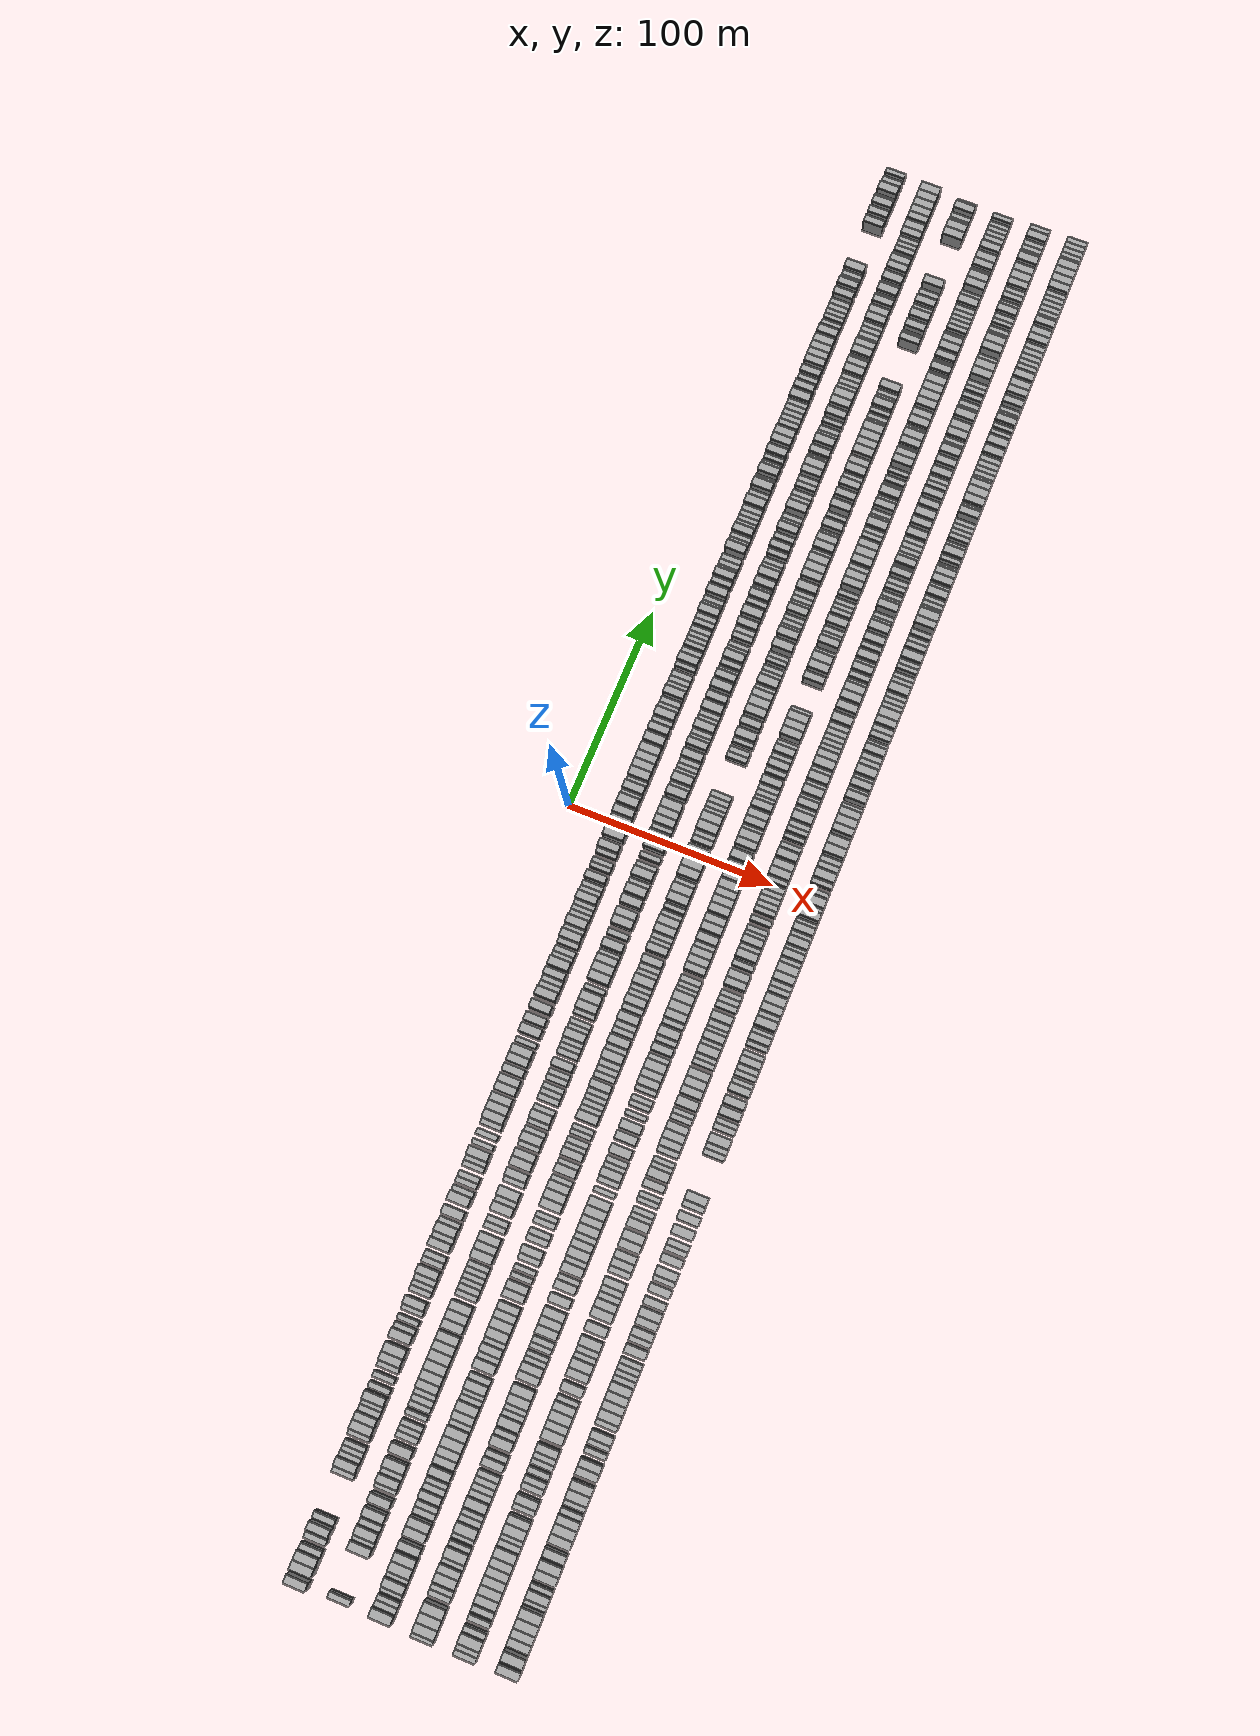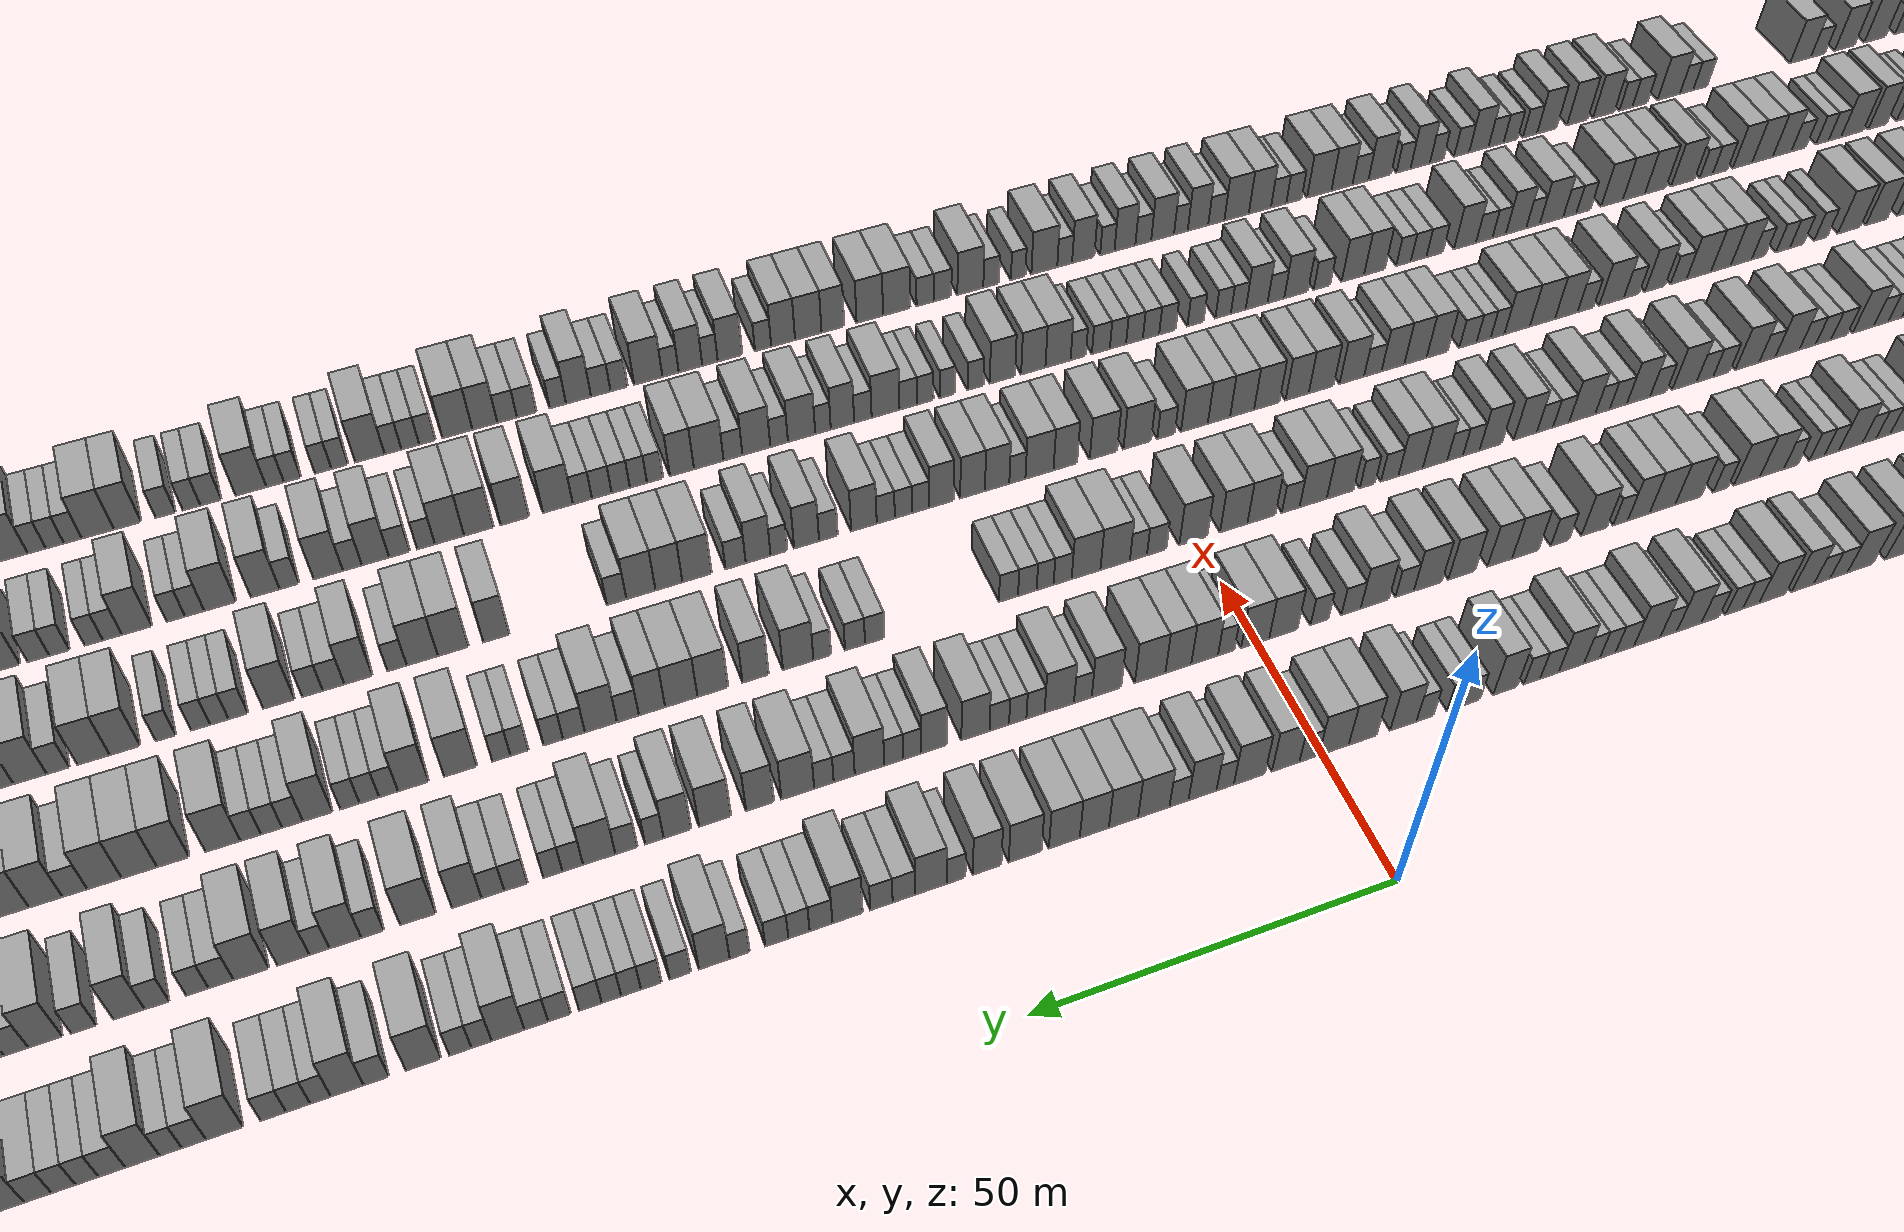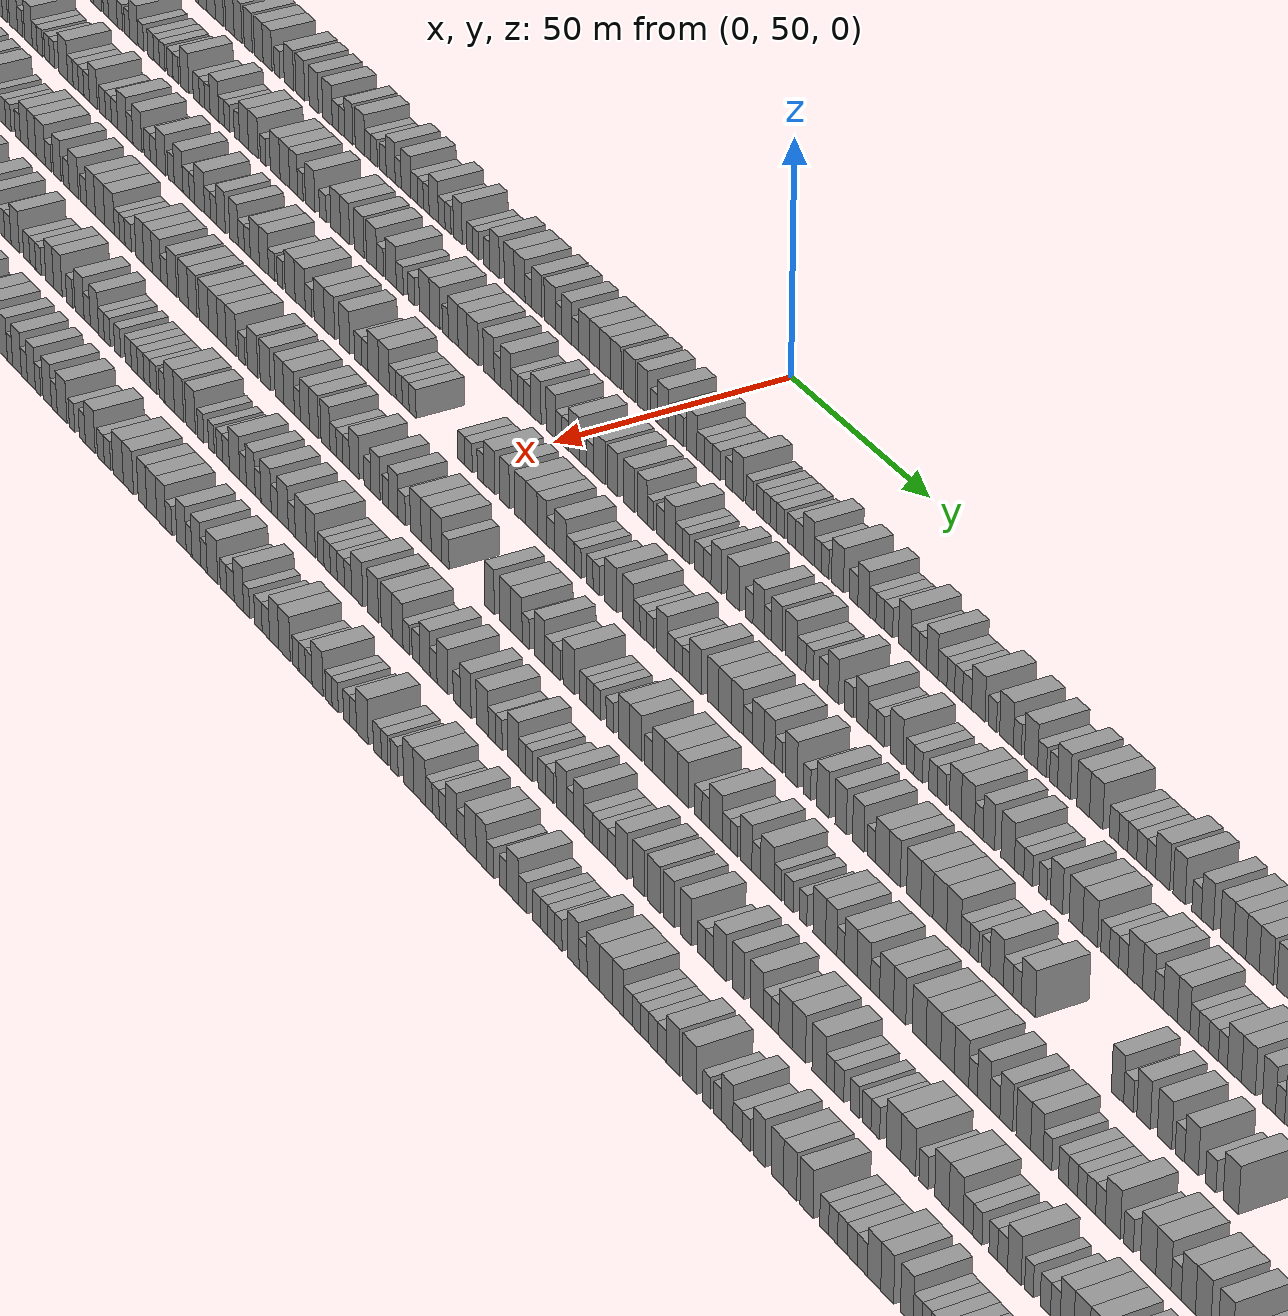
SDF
<sdf version="1.6">
 <world name="default">
  <scene>
   <sky><clouds><speed>12</speed></clouds></sky>
   <ambient>0.4 0.4 0.4 1</ambient>
   <background>0.7 0.7 0.7 1</background>
   <shadows>1</shadows>
  </scene>
  <gravity>0 0 -9.8066</gravity>
  <magnetic_field>6e-06 2.3e-05 -4.2e-05</magnetic_field>
  <physics default="0" name="default_physics" type="ode">
   <ode>
    <solver>
     <type>quick</type>
     <iters>10</iters>
     <sor>1.0</sor>
     <use_dynamic_moi_rescaling>0</use_dynamic_moi_rescaling>
    </solver>
    <constraints>
     <cfm>0</cfm>
     <erp>0.2</erp>
     <contact_max_correcting_vel>100</contact_max_correcting_vel>
     <contact_surface_layer>0.001</contact_surface_layer>
    </constraints>
   </ode>
   <max_step_size>0.004</max_step_size>
   <real_time_factor>1</real_time_factor>
   <real_time_update_rate>250</real_time_update_rate>
  </physics>
  <light name="sun" type="directional">
   <pose>0 0 10 0 0 0</pose>
   <diffuse>0.8 0.8 0.8 1</diffuse>
   <specular>0.2 0.2 0.2 1</specular>
   <attenuation>
    <range>1000</range>
    <constant>0.9</constant>
    <linear>0.01</linear>
    <quadratic>0.001</quadratic>
   </attenuation>
   <direction>-0.5 0.1 -0.9</direction>
  </light>
  <model name="building_1">
   <static>1</static>
   <pose>25.0000 -348.1258 0 0.000000 0.000000 0.000000</pose>
   <link name="link">
    <pose>0 0 4.50 0 0 0</pose>
    <collision name="collision"><geometry><box><size>10.0000 3.7484 9.0000</size></box></geometry></collision>
    <visual name="visual">
     <cast_shadows>0</cast_shadows>
     <geometry><box><size>10.0000 3.7484 9.0000</size></box></geometry>
     <material>
      <script>
       <uri>model://grey_wall/materials/scripts</uri>
       <uri>model://grey_wall/materials/textures</uri>
       <name>vrc/grey_wall</name>
      </script>
     </material>
    </visual>
   </link>
  </model>
  <model name="building_2">
   <static>1</static>
   <pose>25.0000 -342.2072 0 0.000000 0.000000 0.000000</pose>
   <link name="link">
    <pose>0 0 4.50 0 0 0</pose>
    <collision name="collision"><geometry><box><size>10.0000 4.0888 9.0000</size></box></geometry></collision>
    <visual name="visual">
     <cast_shadows>0</cast_shadows>
     <geometry><box><size>10.0000 4.0888 9.0000</size></box></geometry>
     <material>
      <script>
       <uri>model://grey_wall/materials/scripts</uri>
       <uri>model://grey_wall/materials/textures</uri>
       <name>vrc/grey_wall</name>
      </script>
     </material>
    </visual>
   </link>
  </model>
  <model name="building_3">
   <static>1</static>
   <pose>25.0000 -338.1127 0 0.000000 0.000000 0.000000</pose>
   <link name="link">
    <pose>0 0 4.50 0 0 0</pose>
    <collision name="collision"><geometry><box><size>10.0000 4.1001 9.0000</size></box></geometry></collision>
    <visual name="visual">
     <cast_shadows>0</cast_shadows>
     <geometry><box><size>10.0000 4.1001 9.0000</size></box></geometry>
     <material>
      <script>
       <uri>model://grey_wall/materials/scripts</uri>
       <uri>model://grey_wall/materials/textures</uri>
       <name>vrc/grey_wall</name>
      </script>
     </material>
    </visual>
   </link>
  </model>
  <model name="building_4">
   <static>1</static>
   <pose>25.0000 -334.6447 0 0.000000 0.000000 0.000000</pose>
   <link name="link">
    <pose>0 0 3.00 0 0 0</pose>
    <collision name="collision"><geometry><box><size>10.0000 2.8359 6.0000</size></box></geometry></collision>
    <visual name="visual">
     <cast_shadows>0</cast_shadows>
     <geometry><box><size>10.0000 2.8359 6.0000</size></box></geometry>
     <material>
      <script>
       <uri>model://grey_wall/materials/scripts</uri>
       <uri>model://grey_wall/materials/textures</uri>
       <name>vrc/grey_wall</name>
      </script>
     </material>
    </visual>
   </link>
  </model>
  <model name="building_5">
   <static>1</static>
   <pose>25.0000 -329.8384 0 0.000000 0.000000 0.000000</pose>
   <link name="link">
    <pose>0 0 3.00 0 0 0</pose>
    <collision name="collision"><geometry><box><size>10.0000 2.7767 6.0000</size></box></geometry></collision>
    <visual name="visual">
     <cast_shadows>0</cast_shadows>
     <geometry><box><size>10.0000 2.7767 6.0000</size></box></geometry>
     <material>
      <script>
       <uri>model://grey_wall/materials/scripts</uri>
       <uri>model://grey_wall/materials/textures</uri>
       <name>vrc/grey_wall</name>
      </script>
     </material>
    </visual>
   </link>
  </model>
  <model name="building_6">
   <static>1</static>
   <pose>25.0000 -325.6081 0 0.000000 0.000000 0.000000</pose>
   <link name="link">
    <pose>0 0 4.50 0 0 0</pose>
    <collision name="collision"><geometry><box><size>10.0000 3.6839 9.0000</size></box></geometry></collision>
    <visual name="visual">
     <cast_shadows>0</cast_shadows>
     <geometry><box><size>10.0000 3.6839 9.0000</size></box></geometry>
     <material>
      <script>
       <uri>model://grey_wall/materials/scripts</uri>
       <uri>model://grey_wall/materials/textures</uri>
       <name>vrc/grey_wall</name>
      </script>
     </material>
    </visual>
   </link>
  </model>
  <model name="building_7">
   <static>1</static>
   <pose>25.0000 -321.3060 0 0.000000 0.000000 0.000000</pose>
   <link name="link">
    <pose>0 0 3.00 0 0 0</pose>
    <collision name="collision"><geometry><box><size>10.0000 2.9201 6.0000</size></box></geometry></collision>
    <visual name="visual">
     <cast_shadows>0</cast_shadows>
     <geometry><box><size>10.0000 2.9201 6.0000</size></box></geometry>
     <material>
      <script>
       <uri>model://grey_wall/materials/scripts</uri>
       <uri>model://grey_wall/materials/textures</uri>
       <name>vrc/grey_wall</name>
      </script>
     </material>
    </visual>
   </link>
  </model>
  <model name="building_8">
   <static>1</static>
   <pose>25.0000 -301.5321 0 0.000000 0.000000 0.000000</pose>
   <link name="link">
    <pose>0 0 3.00 0 0 0</pose>
    <collision name="collision"><geometry><box><size>10.0000 2.8759 6.0000</size></box></geometry></collision>
    <visual name="visual">
     <cast_shadows>0</cast_shadows>
     <geometry><box><size>10.0000 2.8759 6.0000</size></box></geometry>
     <material>
      <script>
       <uri>model://grey_wall/materials/scripts</uri>
       <uri>model://grey_wall/materials/textures</uri>
       <name>vrc/grey_wall</name>
      </script>
     </material>
    </visual>
   </link>
  </model>
  <model name="building_9">
   <static>1</static>
   <pose>25.0000 -298.1190 0 0.000000 0.000000 0.000000</pose>
   <link name="link">
    <pose>0 0 4.50 0 0 0</pose>
    <collision name="collision"><geometry><box><size>10.0000 3.9503 9.0000</size></box></geometry></collision>
    <visual name="visual">
     <cast_shadows>0</cast_shadows>
     <geometry><box><size>10.0000 3.9503 9.0000</size></box></geometry>
     <material>
      <script>
       <uri>model://grey_wall/materials/scripts</uri>
       <uri>model://grey_wall/materials/textures</uri>
       <name>vrc/grey_wall</name>
      </script>
     </material>
    </visual>
   </link>
  </model>
  <model name="building_10">
   <static>1</static>
   <pose>25.0000 -294.9065 0 0.000000 0.000000 0.000000</pose>
   <link name="link">
    <pose>0 0 3.00 0 0 0</pose>
    <collision name="collision"><geometry><box><size>10.0000 2.4746 6.0000</size></box></geometry></collision>
    <visual name="visual">
     <cast_shadows>0</cast_shadows>
     <geometry><box><size>10.0000 2.4746 6.0000</size></box></geometry>
     <material>
      <script>
       <uri>model://grey_wall/materials/scripts</uri>
       <uri>model://grey_wall/materials/textures</uri>
       <name>vrc/grey_wall</name>
      </script>
     </material>
    </visual>
   </link>
  </model>
  <model name="building_11">
   <static>1</static>
   <pose>25.0000 -292.4646 0 0.000000 0.000000 0.000000</pose>
   <link name="link">
    <pose>0 0 3.00 0 0 0</pose>
    <collision name="collision"><geometry><box><size>10.0000 2.4092 6.0000</size></box></geometry></collision>
    <visual name="visual">
     <cast_shadows>0</cast_shadows>
     <geometry><box><size>10.0000 2.4092 6.0000</size></box></geometry>
     <material>
      <script>
       <uri>model://grey_wall/materials/scripts</uri>
       <uri>model://grey_wall/materials/textures</uri>
       <name>vrc/grey_wall</name>
      </script>
     </material>
    </visual>
   </link>
  </model>
  <model name="building_12">
   <static>1</static>
   <pose>25.0000 -290.0390 0 0.000000 0.000000 0.000000</pose>
   <link name="link">
    <pose>0 0 3.00 0 0 0</pose>
    <collision name="collision"><geometry><box><size>10.0000 2.4420 6.0000</size></box></geometry></collision>
    <visual name="visual">
     <cast_shadows>0</cast_shadows>
     <geometry><box><size>10.0000 2.4420 6.0000</size></box></geometry>
     <material>
      <script>
       <uri>model://grey_wall/materials/scripts</uri>
       <uri>model://grey_wall/materials/textures</uri>
       <name>vrc/grey_wall</name>
      </script>
     </material>
    </visual>
   </link>
  </model>
  <model name="building_13">
   <static>1</static>
   <pose>25.0000 -285.4829 0 0.000000 0.000000 0.000000</pose>
   <link name="link">
    <pose>0 0 3.00 0 0 0</pose>
    <collision name="collision"><geometry><box><size>10.0000 2.6702 6.0000</size></box></geometry></collision>
    <visual name="visual">
     <cast_shadows>0</cast_shadows>
     <geometry><box><size>10.0000 2.6702 6.0000</size></box></geometry>
     <material>
      <script>
       <uri>model://grey_wall/materials/scripts</uri>
       <uri>model://grey_wall/materials/textures</uri>
       <name>vrc/grey_wall</name>
      </script>
     </material>
    </visual>
   </link>
  </model>
  <model name="building_14">
   <static>1</static>
   <pose>25.0000 -282.1232 0 0.000000 0.000000 0.000000</pose>
   <link name="link">
    <pose>0 0 4.50 0 0 0</pose>
    <collision name="collision"><geometry><box><size>10.0000 4.0493 9.0000</size></box></geometry></collision>
    <visual name="visual">
     <cast_shadows>0</cast_shadows>
     <geometry><box><size>10.0000 4.0493 9.0000</size></box></geometry>
     <material>
      <script>
       <uri>model://grey_wall/materials/scripts</uri>
       <uri>model://grey_wall/materials/textures</uri>
       <name>vrc/grey_wall</name>
      </script>
     </material>
    </visual>
   </link>
  </model>
  <model name="building_15">
   <static>1</static>
   <pose>25.0000 -278.2878 0 0.000000 0.000000 0.000000</pose>
   <link name="link">
    <pose>0 0 4.50 0 0 0</pose>
    <collision name="collision"><geometry><box><size>10.0000 3.6216 9.0000</size></box></geometry></collision>
    <visual name="visual">
     <cast_shadows>0</cast_shadows>
     <geometry><box><size>10.0000 3.6216 9.0000</size></box></geometry>
     <material>
      <script>
       <uri>model://grey_wall/materials/scripts</uri>
       <uri>model://grey_wall/materials/textures</uri>
       <name>vrc/grey_wall</name>
      </script>
     </material>
    </visual>
   </link>
  </model>
  <model name="building_16">
   <static>1</static>
   <pose>25.0000 -275.0232 0 0.000000 0.000000 0.000000</pose>
   <link name="link">
    <pose>0 0 3.00 0 0 0</pose>
    <collision name="collision"><geometry><box><size>10.0000 2.9075 6.0000</size></box></geometry></collision>
    <visual name="visual">
     <cast_shadows>0</cast_shadows>
     <geometry><box><size>10.0000 2.9075 6.0000</size></box></geometry>
     <material>
      <script>
       <uri>model://grey_wall/materials/scripts</uri>
       <uri>model://grey_wall/materials/textures</uri>
       <name>vrc/grey_wall</name>
      </script>
     </material>
    </visual>
   </link>
  </model>
  <model name="building_17">
   <static>1</static>
   <pose>25.0000 -272.3607 0 0.000000 0.000000 0.000000</pose>
   <link name="link">
    <pose>0 0 3.00 0 0 0</pose>
    <collision name="collision"><geometry><box><size>10.0000 2.4175 6.0000</size></box></geometry></collision>
    <visual name="visual">
     <cast_shadows>0</cast_shadows>
     <geometry><box><size>10.0000 2.4175 6.0000</size></box></geometry>
     <material>
      <script>
       <uri>model://grey_wall/materials/scripts</uri>
       <uri>model://grey_wall/materials/textures</uri>
       <name>vrc/grey_wall</name>
      </script>
     </material>
    </visual>
   </link>
  </model>
  <model name="building_18">
   <static>1</static>
   <pose>25.0000 -269.2411 0 0.000000 0.000000 0.000000</pose>
   <link name="link">
    <pose>0 0 4.50 0 0 0</pose>
    <collision name="collision"><geometry><box><size>10.0000 3.8217 9.0000</size></box></geometry></collision>
    <visual name="visual">
     <cast_shadows>0</cast_shadows>
     <geometry><box><size>10.0000 3.8217 9.0000</size></box></geometry>
     <material>
      <script>
       <uri>model://grey_wall/materials/scripts</uri>
       <uri>model://grey_wall/materials/textures</uri>
       <name>vrc/grey_wall</name>
      </script>
     </material>
    </visual>
   </link>
  </model>
  <model name="building_19">
   <static>1</static>
   <pose>25.0000 -264.9265 0 0.000000 0.000000 0.000000</pose>
   <link name="link">
    <pose>0 0 3.00 0 0 0</pose>
    <collision name="collision"><geometry><box><size>10.0000 2.8074 6.0000</size></box></geometry></collision>
    <visual name="visual">
     <cast_shadows>0</cast_shadows>
     <geometry><box><size>10.0000 2.8074 6.0000</size></box></geometry>
     <material>
      <script>
       <uri>model://grey_wall/materials/scripts</uri>
       <uri>model://grey_wall/materials/textures</uri>
       <name>vrc/grey_wall</name>
      </script>
     </material>
    </visual>
   </link>
  </model>
  <model name="building_20">
   <static>1</static>
   <pose>25.0000 -260.2096 0 0.000000 0.000000 0.000000</pose>
   <link name="link">
    <pose>0 0 3.00 0 0 0</pose>
    <collision name="collision"><geometry><box><size>10.0000 2.6264 6.0000</size></box></geometry></collision>
    <visual name="visual">
     <cast_shadows>0</cast_shadows>
     <geometry><box><size>10.0000 2.6264 6.0000</size></box></geometry>
     <material>
      <script>
       <uri>model://grey_wall/materials/scripts</uri>
       <uri>model://grey_wall/materials/textures</uri>
       <name>vrc/grey_wall</name>
      </script>
     </material>
    </visual>
   </link>
  </model>
  <model name="building_21">
   <static>1</static>
   <pose>25.0000 -255.4781 0 0.000000 0.000000 0.000000</pose>
   <link name="link">
    <pose>0 0 3.00 0 0 0</pose>
    <collision name="collision"><geometry><box><size>10.0000 2.8368 6.0000</size></box></geometry></collision>
    <visual name="visual">
     <cast_shadows>0</cast_shadows>
     <geometry><box><size>10.0000 2.8368 6.0000</size></box></geometry>
     <material>
      <script>
       <uri>model://grey_wall/materials/scripts</uri>
       <uri>model://grey_wall/materials/textures</uri>
       <name>vrc/grey_wall</name>
      </script>
     </material>
    </visual>
   </link>
  </model>
  <model name="building_22">
   <static>1</static>
   <pose>25.0000 -252.1929 0 0.000000 0.000000 0.000000</pose>
   <link name="link">
    <pose>0 0 4.50 0 0 0</pose>
    <collision name="collision"><geometry><box><size>10.0000 3.7335 9.0000</size></box></geometry></collision>
    <visual name="visual">
     <cast_shadows>0</cast_shadows>
     <geometry><box><size>10.0000 3.7335 9.0000</size></box></geometry>
     <material>
      <script>
       <uri>model://grey_wall/materials/scripts</uri>
       <uri>model://grey_wall/materials/textures</uri>
       <name>vrc/grey_wall</name>
      </script>
     </material>
    </visual>
   </link>
  </model>
  <model name="building_23">
   <static>1</static>
   <pose>25.0000 -248.1454 0 0.000000 0.000000 0.000000</pose>
   <link name="link">
    <pose>0 0 4.50 0 0 0</pose>
    <collision name="collision"><geometry><box><size>10.0000 4.3615 9.0000</size></box></geometry></collision>
    <visual name="visual">
     <cast_shadows>0</cast_shadows>
     <geometry><box><size>10.0000 4.3615 9.0000</size></box></geometry>
     <material>
      <script>
       <uri>model://grey_wall/materials/scripts</uri>
       <uri>model://grey_wall/materials/textures</uri>
       <name>vrc/grey_wall</name>
      </script>
     </material>
    </visual>
   </link>
  </model>
  <model name="building_24">
   <static>1</static>
   <pose>25.0000 -241.8456 0 0.000000 0.000000 0.000000</pose>
   <link name="link">
    <pose>0 0 4.50 0 0 0</pose>
    <collision name="collision"><geometry><box><size>10.0000 4.2381 9.0000</size></box></geometry></collision>
    <visual name="visual">
     <cast_shadows>0</cast_shadows>
     <geometry><box><size>10.0000 4.2381 9.0000</size></box></geometry>
     <material>
      <script>
       <uri>model://grey_wall/materials/scripts</uri>
       <uri>model://grey_wall/materials/textures</uri>
       <name>vrc/grey_wall</name>
      </script>
     </material>
    </visual>
   </link>
  </model>
  <model name="building_25">
   <static>1</static>
   <pose>25.0000 -238.4380 0 0.000000 0.000000 0.000000</pose>
   <link name="link">
    <pose>0 0 3.00 0 0 0</pose>
    <collision name="collision"><geometry><box><size>10.0000 2.5771 6.0000</size></box></geometry></collision>
    <visual name="visual">
     <cast_shadows>0</cast_shadows>
     <geometry><box><size>10.0000 2.5771 6.0000</size></box></geometry>
     <material>
      <script>
       <uri>model://grey_wall/materials/scripts</uri>
       <uri>model://grey_wall/materials/textures</uri>
       <name>vrc/grey_wall</name>
      </script>
     </material>
    </visual>
   </link>
  </model>
  <model name="building_26">
   <static>1</static>
   <pose>25.0000 -234.9004 0 0.000000 0.000000 0.000000</pose>
   <link name="link">
    <pose>0 0 3.00 0 0 0</pose>
    <collision name="collision"><geometry><box><size>10.0000 2.4980 6.0000</size></box></geometry></collision>
    <visual name="visual">
     <cast_shadows>0</cast_shadows>
     <geometry><box><size>10.0000 2.4980 6.0000</size></box></geometry>
     <material>
      <script>
       <uri>model://grey_wall/materials/scripts</uri>
       <uri>model://grey_wall/materials/textures</uri>
       <name>vrc/grey_wall</name>
      </script>
     </material>
    </visual>
   </link>
  </model>
  <model name="building_27">
   <static>1</static>
   <pose>25.0000 -230.3771 0 0.000000 0.000000 0.000000</pose>
   <link name="link">
    <pose>0 0 3.00 0 0 0</pose>
    <collision name="collision"><geometry><box><size>10.0000 2.5487 6.0000</size></box></geometry></collision>
    <visual name="visual">
     <cast_shadows>0</cast_shadows>
     <geometry><box><size>10.0000 2.5487 6.0000</size></box></geometry>
     <material>
      <script>
       <uri>model://grey_wall/materials/scripts</uri>
       <uri>model://grey_wall/materials/textures</uri>
       <name>vrc/grey_wall</name>
      </script>
     </material>
    </visual>
   </link>
  </model>
  <model name="building_28">
   <static>1</static>
   <pose>25.0000 -227.2078 0 0.000000 0.000000 0.000000</pose>
   <link name="link">
    <pose>0 0 4.50 0 0 0</pose>
    <collision name="collision"><geometry><box><size>10.0000 3.7900 9.0000</size></box></geometry></collision>
    <visual name="visual">
     <cast_shadows>0</cast_shadows>
     <geometry><box><size>10.0000 3.7900 9.0000</size></box></geometry>
     <material>
      <script>
       <uri>model://grey_wall/materials/scripts</uri>
       <uri>model://grey_wall/materials/textures</uri>
       <name>vrc/grey_wall</name>
      </script>
     </material>
    </visual>
   </link>
  </model>
  <model name="building_29">
   <static>1</static>
   <pose>25.0000 -222.0278 0 0.000000 0.000000 0.000000</pose>
   <link name="link">
    <pose>0 0 3.00 0 0 0</pose>
    <collision name="collision"><geometry><box><size>10.0000 2.5699 6.0000</size></box></geometry></collision>
    <visual name="visual">
     <cast_shadows>0</cast_shadows>
     <geometry><box><size>10.0000 2.5699 6.0000</size></box></geometry>
     <material>
      <script>
       <uri>model://grey_wall/materials/scripts</uri>
       <uri>model://grey_wall/materials/textures</uri>
       <name>vrc/grey_wall</name>
      </script>
     </material>
    </visual>
   </link>
  </model>
  <model name="building_30">
   <static>1</static>
   <pose>25.0000 -219.5362 0 0.000000 0.000000 0.000000</pose>
   <link name="link">
    <pose>0 0 3.00 0 0 0</pose>
    <collision name="collision"><geometry><box><size>10.0000 2.4133 6.0000</size></box></geometry></collision>
    <visual name="visual">
     <cast_shadows>0</cast_shadows>
     <geometry><box><size>10.0000 2.4133 6.0000</size></box></geometry>
     <material>
      <script>
       <uri>model://grey_wall/materials/scripts</uri>
       <uri>model://grey_wall/materials/textures</uri>
       <name>vrc/grey_wall</name>
      </script>
     </material>
    </visual>
   </link>
  </model>
  <model name="building_31">
   <static>1</static>
   <pose>25.0000 -216.8375 0 0.000000 0.000000 0.000000</pose>
   <link name="link">
    <pose>0 0 3.00 0 0 0</pose>
    <collision name="collision"><geometry><box><size>10.0000 2.9841 6.0000</size></box></geometry></collision>
    <visual name="visual">
     <cast_shadows>0</cast_shadows>
     <geometry><box><size>10.0000 2.9841 6.0000</size></box></geometry>
     <material>
      <script>
       <uri>model://grey_wall/materials/scripts</uri>
       <uri>model://grey_wall/materials/textures</uri>
       <name>vrc/grey_wall</name>
      </script>
     </material>
    </visual>
   </link>
  </model>
  <model name="building_32">
   <static>1</static>
   <pose>25.0000 -213.4018 0 0.000000 0.000000 0.000000</pose>
   <link name="link">
    <pose>0 0 4.50 0 0 0</pose>
    <collision name="collision"><geometry><box><size>10.0000 3.8874 9.0000</size></box></geometry></collision>
    <visual name="visual">
     <cast_shadows>0</cast_shadows>
     <geometry><box><size>10.0000 3.8874 9.0000</size></box></geometry>
     <material>
      <script>
       <uri>model://grey_wall/materials/scripts</uri>
       <uri>model://grey_wall/materials/textures</uri>
       <name>vrc/grey_wall</name>
      </script>
     </material>
    </visual>
   </link>
  </model>
  <model name="building_33">
   <static>1</static>
   <pose>25.0000 -209.0826 0 0.000000 0.000000 0.000000</pose>
   <link name="link">
    <pose>0 0 3.00 0 0 0</pose>
    <collision name="collision"><geometry><box><size>10.0000 2.7510 6.0000</size></box></geometry></collision>
    <visual name="visual">
     <cast_shadows>0</cast_shadows>
     <geometry><box><size>10.0000 2.7510 6.0000</size></box></geometry>
     <material>
      <script>
       <uri>model://grey_wall/materials/scripts</uri>
       <uri>model://grey_wall/materials/textures</uri>
       <name>vrc/grey_wall</name>
      </script>
     </material>
    </visual>
   </link>
  </model>
  <model name="building_34">
   <static>1</static>
   <pose>25.0000 -206.2779 0 0.000000 0.000000 0.000000</pose>
   <link name="link">
    <pose>0 0 3.00 0 0 0</pose>
    <collision name="collision"><geometry><box><size>10.0000 2.8583 6.0000</size></box></geometry></collision>
    <visual name="visual">
     <cast_shadows>0</cast_shadows>
     <geometry><box><size>10.0000 2.8583 6.0000</size></box></geometry>
     <material>
      <script>
       <uri>model://grey_wall/materials/scripts</uri>
       <uri>model://grey_wall/materials/textures</uri>
       <name>vrc/grey_wall</name>
      </script>
     </material>
    </visual>
   </link>
  </model>
  <model name="building_35">
   <static>1</static>
   <pose>25.0000 -200.9639 0 0.000000 0.000000 0.000000</pose>
   <link name="link">
    <pose>0 0 4.50 0 0 0</pose>
    <collision name="collision"><geometry><box><size>10.0000 3.7698 9.0000</size></box></geometry></collision>
    <visual name="visual">
     <cast_shadows>0</cast_shadows>
     <geometry><box><size>10.0000 3.7698 9.0000</size></box></geometry>
     <material>
      <script>
       <uri>model://grey_wall/materials/scripts</uri>
       <uri>model://grey_wall/materials/textures</uri>
       <name>vrc/grey_wall</name>
      </script>
     </material>
    </visual>
   </link>
  </model>
  <model name="building_36">
   <static>1</static>
   <pose>25.0000 -197.6932 0 0.000000 0.000000 0.000000</pose>
   <link name="link">
    <pose>0 0 3.00 0 0 0</pose>
    <collision name="collision"><geometry><box><size>10.0000 2.7715 6.0000</size></box></geometry></collision>
    <visual name="visual">
     <cast_shadows>0</cast_shadows>
     <geometry><box><size>10.0000 2.7715 6.0000</size></box></geometry>
     <material>
      <script>
       <uri>model://grey_wall/materials/scripts</uri>
       <uri>model://grey_wall/materials/textures</uri>
       <name>vrc/grey_wall</name>
      </script>
     </material>
    </visual>
   </link>
  </model>
  <model name="building_37">
   <static>1</static>
   <pose>25.0000 -194.2032 0 0.000000 0.000000 0.000000</pose>
   <link name="link">
    <pose>0 0 4.50 0 0 0</pose>
    <collision name="collision"><geometry><box><size>10.0000 4.2087 9.0000</size></box></geometry></collision>
    <visual name="visual">
     <cast_shadows>0</cast_shadows>
     <geometry><box><size>10.0000 4.2087 9.0000</size></box></geometry>
     <material>
      <script>
       <uri>model://grey_wall/materials/scripts</uri>
       <uri>model://grey_wall/materials/textures</uri>
       <name>vrc/grey_wall</name>
      </script>
     </material>
    </visual>
   </link>
  </model>
  <model name="building_38">
   <static>1</static>
   <pose>25.0000 -190.8479 0 0.000000 0.000000 0.000000</pose>
   <link name="link">
    <pose>0 0 3.00 0 0 0</pose>
    <collision name="collision"><geometry><box><size>10.0000 2.5019 6.0000</size></box></geometry></collision>
    <visual name="visual">
     <cast_shadows>0</cast_shadows>
     <geometry><box><size>10.0000 2.5019 6.0000</size></box></geometry>
     <material>
      <script>
       <uri>model://grey_wall/materials/scripts</uri>
       <uri>model://grey_wall/materials/textures</uri>
       <name>vrc/grey_wall</name>
      </script>
     </material>
    </visual>
   </link>
  </model>
  <model name="building_39">
   <static>1</static>
   <pose>25.0000 -186.4623 0 0.000000 0.000000 0.000000</pose>
   <link name="link">
    <pose>0 0 4.50 0 0 0</pose>
    <collision name="collision"><geometry><box><size>10.0000 4.2692 9.0000</size></box></geometry></collision>
    <visual name="visual">
     <cast_shadows>0</cast_shadows>
     <geometry><box><size>10.0000 4.2692 9.0000</size></box></geometry>
     <material>
      <script>
       <uri>model://grey_wall/materials/scripts</uri>
       <uri>model://grey_wall/materials/textures</uri>
       <name>vrc/grey_wall</name>
      </script>
     </material>
    </visual>
   </link>
  </model>
  <model name="building_40">
   <static>1</static>
   <pose>25.0000 -180.0829 0 0.000000 0.000000 0.000000</pose>
   <link name="link">
    <pose>0 0 4.50 0 0 0</pose>
    <collision name="collision"><geometry><box><size>10.0000 4.4897 9.0000</size></box></geometry></collision>
    <visual name="visual">
     <cast_shadows>0</cast_shadows>
     <geometry><box><size>10.0000 4.4897 9.0000</size></box></geometry>
     <material>
      <script>
       <uri>model://grey_wall/materials/scripts</uri>
       <uri>model://grey_wall/materials/textures</uri>
       <name>vrc/grey_wall</name>
      </script>
     </material>
    </visual>
   </link>
  </model>
  <model name="building_41">
   <static>1</static>
   <pose>25.0000 -176.4945 0 0.000000 0.000000 0.000000</pose>
   <link name="link">
    <pose>0 0 3.00 0 0 0</pose>
    <collision name="collision"><geometry><box><size>10.0000 2.6871 6.0000</size></box></geometry></collision>
    <visual name="visual">
     <cast_shadows>0</cast_shadows>
     <geometry><box><size>10.0000 2.6871 6.0000</size></box></geometry>
     <material>
      <script>
       <uri>model://grey_wall/materials/scripts</uri>
       <uri>model://grey_wall/materials/textures</uri>
       <name>vrc/grey_wall</name>
      </script>
     </material>
    </visual>
   </link>
  </model>
  <model name="building_42">
   <static>1</static>
   <pose>25.0000 -172.7683 0 0.000000 0.000000 0.000000</pose>
   <link name="link">
    <pose>0 0 3.00 0 0 0</pose>
    <collision name="collision"><geometry><box><size>10.0000 2.7653 6.0000</size></box></geometry></collision>
    <visual name="visual">
     <cast_shadows>0</cast_shadows>
     <geometry><box><size>10.0000 2.7653 6.0000</size></box></geometry>
     <material>
      <script>
       <uri>model://grey_wall/materials/scripts</uri>
       <uri>model://grey_wall/materials/textures</uri>
       <name>vrc/grey_wall</name>
      </script>
     </material>
    </visual>
   </link>
  </model>
  <model name="building_43">
   <static>1</static>
   <pose>25.0000 -169.9595 0 0.000000 0.000000 0.000000</pose>
   <link name="link">
    <pose>0 0 3.00 0 0 0</pose>
    <collision name="collision"><geometry><box><size>10.0000 2.8523 6.0000</size></box></geometry></collision>
    <visual name="visual">
     <cast_shadows>0</cast_shadows>
     <geometry><box><size>10.0000 2.8523 6.0000</size></box></geometry>
     <material>
      <script>
       <uri>model://grey_wall/materials/scripts</uri>
       <uri>model://grey_wall/materials/textures</uri>
       <name>vrc/grey_wall</name>
      </script>
     </material>
    </visual>
   </link>
  </model>
  <model name="building_44">
   <static>1</static>
   <pose>25.0000 -165.2083 0 0.000000 0.000000 0.000000</pose>
   <link name="link">
    <pose>0 0 3.00 0 0 0</pose>
    <collision name="collision"><geometry><box><size>10.0000 2.6502 6.0000</size></box></geometry></collision>
    <visual name="visual">
     <cast_shadows>0</cast_shadows>
     <geometry><box><size>10.0000 2.6502 6.0000</size></box></geometry>
     <material>
      <script>
       <uri>model://grey_wall/materials/scripts</uri>
       <uri>model://grey_wall/materials/textures</uri>
       <name>vrc/grey_wall</name>
      </script>
     </material>
    </visual>
   </link>
  </model>
  <model name="building_45">
   <static>1</static>
   <pose>25.0000 -162.6723 0 0.000000 0.000000 0.000000</pose>
   <link name="link">
    <pose>0 0 3.00 0 0 0</pose>
    <collision name="collision"><geometry><box><size>10.0000 2.4218 6.0000</size></box></geometry></collision>
    <visual name="visual">
     <cast_shadows>0</cast_shadows>
     <geometry><box><size>10.0000 2.4218 6.0000</size></box></geometry>
     <material>
      <script>
       <uri>model://grey_wall/materials/scripts</uri>
       <uri>model://grey_wall/materials/textures</uri>
       <name>vrc/grey_wall</name>
      </script>
     </material>
    </visual>
   </link>
  </model>
  <model name="building_46">
   <static>1</static>
   <pose>25.0000 -159.3870 0 0.000000 0.000000 0.000000</pose>
   <link name="link">
    <pose>0 0 4.50 0 0 0</pose>
    <collision name="collision"><geometry><box><size>10.0000 4.1486 9.0000</size></box></geometry></collision>
    <visual name="visual">
     <cast_shadows>0</cast_shadows>
     <geometry><box><size>10.0000 4.1486 9.0000</size></box></geometry>
     <material>
      <script>
       <uri>model://grey_wall/materials/scripts</uri>
       <uri>model://grey_wall/materials/textures</uri>
       <name>vrc/grey_wall</name>
      </script>
     </material>
    </visual>
   </link>
  </model>
  <model name="building_47">
   <static>1</static>
   <pose>25.0000 -155.0709 0 0.000000 0.000000 0.000000</pose>
   <link name="link">
    <pose>0 0 3.00 0 0 0</pose>
    <collision name="collision"><geometry><box><size>10.0000 2.4835 6.0000</size></box></geometry></collision>
    <visual name="visual">
     <cast_shadows>0</cast_shadows>
     <geometry><box><size>10.0000 2.4835 6.0000</size></box></geometry>
     <material>
      <script>
       <uri>model://grey_wall/materials/scripts</uri>
       <uri>model://grey_wall/materials/textures</uri>
       <name>vrc/grey_wall</name>
      </script>
     </material>
    </visual>
   </link>
  </model>
  <model name="building_48">
   <static>1</static>
   <pose>25.0000 -150.4321 0 0.000000 0.000000 0.000000</pose>
   <link name="link">
    <pose>0 0 3.00 0 0 0</pose>
    <collision name="collision"><geometry><box><size>10.0000 2.7941 6.0000</size></box></geometry></collision>
    <visual name="visual">
     <cast_shadows>0</cast_shadows>
     <geometry><box><size>10.0000 2.7941 6.0000</size></box></geometry>
     <material>
      <script>
       <uri>model://grey_wall/materials/scripts</uri>
       <uri>model://grey_wall/materials/textures</uri>
       <name>vrc/grey_wall</name>
      </script>
     </material>
    </visual>
   </link>
  </model>
  <model name="building_49">
   <static>1</static>
   <pose>25.0000 -145.6958 0 0.000000 0.000000 0.000000</pose>
   <link name="link">
    <pose>0 0 3.00 0 0 0</pose>
    <collision name="collision"><geometry><box><size>10.0000 2.6785 6.0000</size></box></geometry></collision>
    <visual name="visual">
     <cast_shadows>0</cast_shadows>
     <geometry><box><size>10.0000 2.6785 6.0000</size></box></geometry>
     <material>
      <script>
       <uri>model://grey_wall/materials/scripts</uri>
       <uri>model://grey_wall/materials/textures</uri>
       <name>vrc/grey_wall</name>
      </script>
     </material>
    </visual>
   </link>
  </model>
  <model name="building_50">
   <static>1</static>
   <pose>25.0000 -142.2751 0 0.000000 0.000000 0.000000</pose>
   <link name="link">
    <pose>0 0 4.50 0 0 0</pose>
    <collision name="collision"><geometry><box><size>10.0000 4.1628 9.0000</size></box></geometry></collision>
    <visual name="visual">
     <cast_shadows>0</cast_shadows>
     <geometry><box><size>10.0000 4.1628 9.0000</size></box></geometry>
     <material>
      <script>
       <uri>model://grey_wall/materials/scripts</uri>
       <uri>model://grey_wall/materials/textures</uri>
       <name>vrc/grey_wall</name>
      </script>
     </material>
    </visual>
   </link>
  </model>
  <model name="building_51">
   <static>1</static>
   <pose>25.0000 -138.1461 0 0.000000 0.000000 0.000000</pose>
   <link name="link">
    <pose>0 0 4.50 0 0 0</pose>
    <collision name="collision"><geometry><box><size>10.0000 4.0952 9.0000</size></box></geometry></collision>
    <visual name="visual">
     <cast_shadows>0</cast_shadows>
     <geometry><box><size>10.0000 4.0952 9.0000</size></box></geometry>
     <material>
      <script>
       <uri>model://grey_wall/materials/scripts</uri>
       <uri>model://grey_wall/materials/textures</uri>
       <name>vrc/grey_wall</name>
      </script>
     </material>
    </visual>
   </link>
  </model>
  <model name="building_52">
   <static>1</static>
   <pose>25.0000 -134.1554 0 0.000000 0.000000 0.000000</pose>
   <link name="link">
    <pose>0 0 4.50 0 0 0</pose>
    <collision name="collision"><geometry><box><size>10.0000 3.8862 9.0000</size></box></geometry></collision>
    <visual name="visual">
     <cast_shadows>0</cast_shadows>
     <geometry><box><size>10.0000 3.8862 9.0000</size></box></geometry>
     <material>
      <script>
       <uri>model://grey_wall/materials/scripts</uri>
       <uri>model://grey_wall/materials/textures</uri>
       <name>vrc/grey_wall</name>
      </script>
     </material>
    </visual>
   </link>
  </model>
  <model name="building_53">
   <static>1</static>
   <pose>25.0000 -129.2157 0 0.000000 0.000000 0.000000</pose>
   <link name="link">
    <pose>0 0 4.50 0 0 0</pose>
    <collision name="collision"><geometry><box><size>10.0000 3.9932 9.0000</size></box></geometry></collision>
    <visual name="visual">
     <cast_shadows>0</cast_shadows>
     <geometry><box><size>10.0000 3.9932 9.0000</size></box></geometry>
     <material>
      <script>
       <uri>model://grey_wall/materials/scripts</uri>
       <uri>model://grey_wall/materials/textures</uri>
       <name>vrc/grey_wall</name>
      </script>
     </material>
    </visual>
   </link>
  </model>
  <model name="building_54">
   <static>1</static>
   <pose>25.0000 -125.3410 0 0.000000 0.000000 0.000000</pose>
   <link name="link">
    <pose>0 0 4.50 0 0 0</pose>
    <collision name="collision"><geometry><box><size>10.0000 3.7561 9.0000</size></box></geometry></collision>
    <visual name="visual">
     <cast_shadows>0</cast_shadows>
     <geometry><box><size>10.0000 3.7561 9.0000</size></box></geometry>
     <material>
      <script>
       <uri>model://grey_wall/materials/scripts</uri>
       <uri>model://grey_wall/materials/textures</uri>
       <name>vrc/grey_wall</name>
      </script>
     </material>
    </visual>
   </link>
  </model>
  <model name="building_55">
   <static>1</static>
   <pose>25.0000 -120.5500 0 0.000000 0.000000 0.000000</pose>
   <link name="link">
    <pose>0 0 4.50 0 0 0</pose>
    <collision name="collision"><geometry><box><size>10.0000 3.8260 9.0000</size></box></geometry></collision>
    <visual name="visual">
     <cast_shadows>0</cast_shadows>
     <geometry><box><size>10.0000 3.8260 9.0000</size></box></geometry>
     <material>
      <script>
       <uri>model://grey_wall/materials/scripts</uri>
       <uri>model://grey_wall/materials/textures</uri>
       <name>vrc/grey_wall</name>
      </script>
     </material>
    </visual>
   </link>
  </model>
  <model name="building_56">
   <static>1</static>
   <pose>25.0000 -115.6265 0 0.000000 0.000000 0.000000</pose>
   <link name="link">
    <pose>0 0 4.50 0 0 0</pose>
    <collision name="collision"><geometry><box><size>10.0000 4.0209 9.0000</size></box></geometry></collision>
    <visual name="visual">
     <cast_shadows>0</cast_shadows>
     <geometry><box><size>10.0000 4.0209 9.0000</size></box></geometry>
     <material>
      <script>
       <uri>model://grey_wall/materials/scripts</uri>
       <uri>model://grey_wall/materials/textures</uri>
       <name>vrc/grey_wall</name>
      </script>
     </material>
    </visual>
   </link>
  </model>
  <model name="building_57">
   <static>1</static>
   <pose>25.0000 -111.5318 0 0.000000 0.000000 0.000000</pose>
   <link name="link">
    <pose>0 0 4.50 0 0 0</pose>
    <collision name="collision"><geometry><box><size>10.0000 4.1685 9.0000</size></box></geometry></collision>
    <visual name="visual">
     <cast_shadows>0</cast_shadows>
     <geometry><box><size>10.0000 4.1685 9.0000</size></box></geometry>
     <material>
      <script>
       <uri>model://grey_wall/materials/scripts</uri>
       <uri>model://grey_wall/materials/textures</uri>
       <name>vrc/grey_wall</name>
      </script>
     </material>
    </visual>
   </link>
  </model>
  <model name="building_58">
   <static>1</static>
   <pose>25.0000 -107.1280 0 0.000000 0.000000 0.000000</pose>
   <link name="link">
    <pose>0 0 3.00 0 0 0</pose>
    <collision name="collision"><geometry><box><size>10.0000 2.6391 6.0000</size></box></geometry></collision>
    <visual name="visual">
     <cast_shadows>0</cast_shadows>
     <geometry><box><size>10.0000 2.6391 6.0000</size></box></geometry>
     <material>
      <script>
       <uri>model://grey_wall/materials/scripts</uri>
       <uri>model://grey_wall/materials/textures</uri>
       <name>vrc/grey_wall</name>
      </script>
     </material>
    </visual>
   </link>
  </model>
  <model name="building_59">
   <static>1</static>
   <pose>25.0000 -101.6160 0 0.000000 0.000000 0.000000</pose>
   <link name="link">
    <pose>0 0 4.50 0 0 0</pose>
    <collision name="collision"><geometry><box><size>10.0000 4.3848 9.0000</size></box></geometry></collision>
    <visual name="visual">
     <cast_shadows>0</cast_shadows>
     <geometry><box><size>10.0000 4.3848 9.0000</size></box></geometry>
     <material>
      <script>
       <uri>model://grey_wall/materials/scripts</uri>
       <uri>model://grey_wall/materials/textures</uri>
       <name>vrc/grey_wall</name>
      </script>
     </material>
    </visual>
   </link>
  </model>
  <model name="building_60">
   <static>1</static>
   <pose>25.0000 -96.4047 0 0.000000 0.000000 0.000000</pose>
   <link name="link">
    <pose>0 0 4.50 0 0 0</pose>
    <collision name="collision"><geometry><box><size>10.0000 4.0377 9.0000</size></box></geometry></collision>
    <visual name="visual">
     <cast_shadows>0</cast_shadows>
     <geometry><box><size>10.0000 4.0377 9.0000</size></box></geometry>
     <material>
      <script>
       <uri>model://grey_wall/materials/scripts</uri>
       <uri>model://grey_wall/materials/textures</uri>
       <name>vrc/grey_wall</name>
      </script>
     </material>
    </visual>
   </link>
  </model>
  <model name="building_61">
   <static>1</static>
   <pose>25.0000 -90.3034 0 0.000000 0.000000 0.000000</pose>
   <link name="link">
    <pose>0 0 4.50 0 0 0</pose>
    <collision name="collision"><geometry><box><size>10.0000 4.1649 9.0000</size></box></geometry></collision>
    <visual name="visual">
     <cast_shadows>0</cast_shadows>
     <geometry><box><size>10.0000 4.1649 9.0000</size></box></geometry>
     <material>
      <script>
       <uri>model://grey_wall/materials/scripts</uri>
       <uri>model://grey_wall/materials/textures</uri>
       <name>vrc/grey_wall</name>
      </script>
     </material>
    </visual>
   </link>
  </model>
  <model name="building_62">
   <static>1</static>
   <pose>25.0000 -84.0807 0 0.000000 0.000000 0.000000</pose>
   <link name="link">
    <pose>0 0 4.50 0 0 0</pose>
    <collision name="collision"><geometry><box><size>10.0000 4.2804 9.0000</size></box></geometry></collision>
    <visual name="visual">
     <cast_shadows>0</cast_shadows>
     <geometry><box><size>10.0000 4.2804 9.0000</size></box></geometry>
     <material>
      <script>
       <uri>model://grey_wall/materials/scripts</uri>
       <uri>model://grey_wall/materials/textures</uri>
       <name>vrc/grey_wall</name>
      </script>
     </material>
    </visual>
   </link>
  </model>
  <model name="building_63">
   <static>1</static>
   <pose>25.0000 -80.4880 0 0.000000 0.000000 0.000000</pose>
   <link name="link">
    <pose>0 0 3.00 0 0 0</pose>
    <collision name="collision"><geometry><box><size>10.0000 2.9050 6.0000</size></box></geometry></collision>
    <visual name="visual">
     <cast_shadows>0</cast_shadows>
     <geometry><box><size>10.0000 2.9050 6.0000</size></box></geometry>
     <material>
      <script>
       <uri>model://grey_wall/materials/scripts</uri>
       <uri>model://grey_wall/materials/textures</uri>
       <name>vrc/grey_wall</name>
      </script>
     </material>
    </visual>
   </link>
  </model>
  <model name="building_64">
   <static>1</static>
   <pose>25.0000 -77.6878 0 0.000000 0.000000 0.000000</pose>
   <link name="link">
    <pose>0 0 3.00 0 0 0</pose>
    <collision name="collision"><geometry><box><size>10.0000 2.6953 6.0000</size></box></geometry></collision>
    <visual name="visual">
     <cast_shadows>0</cast_shadows>
     <geometry><box><size>10.0000 2.6953 6.0000</size></box></geometry>
     <material>
      <script>
       <uri>model://grey_wall/materials/scripts</uri>
       <uri>model://grey_wall/materials/textures</uri>
       <name>vrc/grey_wall</name>
      </script>
     </material>
    </visual>
   </link>
  </model>
  <model name="building_65">
   <static>1</static>
   <pose>25.0000 -74.5116 0 0.000000 0.000000 0.000000</pose>
   <link name="link">
    <pose>0 0 4.50 0 0 0</pose>
    <collision name="collision"><geometry><box><size>10.0000 3.6572 9.0000</size></box></geometry></collision>
    <visual name="visual">
     <cast_shadows>0</cast_shadows>
     <geometry><box><size>10.0000 3.6572 9.0000</size></box></geometry>
     <material>
      <script>
       <uri>model://grey_wall/materials/scripts</uri>
       <uri>model://grey_wall/materials/textures</uri>
       <name>vrc/grey_wall</name>
      </script>
     </material>
    </visual>
   </link>
  </model>
  <model name="building_66">
   <static>1</static>
   <pose>25.0000 -69.5431 0 0.000000 0.000000 0.000000</pose>
   <link name="link">
    <pose>0 0 4.50 0 0 0</pose>
    <collision name="collision"><geometry><box><size>10.0000 4.2797 9.0000</size></box></geometry></collision>
    <visual name="visual">
     <cast_shadows>0</cast_shadows>
     <geometry><box><size>10.0000 4.2797 9.0000</size></box></geometry>
     <material>
      <script>
       <uri>model://grey_wall/materials/scripts</uri>
       <uri>model://grey_wall/materials/textures</uri>
       <name>vrc/grey_wall</name>
      </script>
     </material>
    </visual>
   </link>
  </model>
  <model name="building_67">
   <static>1</static>
   <pose>25.0000 -66.0903 0 0.000000 0.000000 0.000000</pose>
   <link name="link">
    <pose>0 0 3.00 0 0 0</pose>
    <collision name="collision"><geometry><box><size>10.0000 2.6259 6.0000</size></box></geometry></collision>
    <visual name="visual">
     <cast_shadows>0</cast_shadows>
     <geometry><box><size>10.0000 2.6259 6.0000</size></box></geometry>
     <material>
      <script>
       <uri>model://grey_wall/materials/scripts</uri>
       <uri>model://grey_wall/materials/textures</uri>
       <name>vrc/grey_wall</name>
      </script>
     </material>
    </visual>
   </link>
  </model>
  <model name="building_68">
   <static>1</static>
   <pose>25.0000 -63.3361 0 0.000000 0.000000 0.000000</pose>
   <link name="link">
    <pose>0 0 3.00 0 0 0</pose>
    <collision name="collision"><geometry><box><size>10.0000 2.8825 6.0000</size></box></geometry></collision>
    <visual name="visual">
     <cast_shadows>0</cast_shadows>
     <geometry><box><size>10.0000 2.8825 6.0000</size></box></geometry>
     <material>
      <script>
       <uri>model://grey_wall/materials/scripts</uri>
       <uri>model://grey_wall/materials/textures</uri>
       <name>vrc/grey_wall</name>
      </script>
     </material>
    </visual>
   </link>
  </model>
  <model name="building_69">
   <static>1</static>
   <pose>25.0000 -59.4682 0 0.000000 0.000000 0.000000</pose>
   <link name="link">
    <pose>0 0 3.00 0 0 0</pose>
    <collision name="collision"><geometry><box><size>10.0000 2.8532 6.0000</size></box></geometry></collision>
    <visual name="visual">
     <cast_shadows>0</cast_shadows>
     <geometry><box><size>10.0000 2.8532 6.0000</size></box></geometry>
     <material>
      <script>
       <uri>model://grey_wall/materials/scripts</uri>
       <uri>model://grey_wall/materials/textures</uri>
       <name>vrc/grey_wall</name>
      </script>
     </material>
    </visual>
   </link>
  </model>
  <model name="building_70">
   <static>1</static>
   <pose>25.0000 -56.0699 0 0.000000 0.000000 0.000000</pose>
   <link name="link">
    <pose>0 0 4.50 0 0 0</pose>
    <collision name="collision"><geometry><box><size>10.0000 3.9436 9.0000</size></box></geometry></collision>
    <visual name="visual">
     <cast_shadows>0</cast_shadows>
     <geometry><box><size>10.0000 3.9436 9.0000</size></box></geometry>
     <material>
      <script>
       <uri>model://grey_wall/materials/scripts</uri>
       <uri>model://grey_wall/materials/textures</uri>
       <name>vrc/grey_wall</name>
      </script>
     </material>
    </visual>
   </link>
  </model>
  <model name="building_71">
   <static>1</static>
   <pose>25.0000 -52.7900 0 0.000000 0.000000 0.000000</pose>
   <link name="link">
    <pose>0 0 3.00 0 0 0</pose>
    <collision name="collision"><geometry><box><size>10.0000 2.6162 6.0000</size></box></geometry></collision>
    <visual name="visual">
     <cast_shadows>0</cast_shadows>
     <geometry><box><size>10.0000 2.6162 6.0000</size></box></geometry>
     <material>
      <script>
       <uri>model://grey_wall/materials/scripts</uri>
       <uri>model://grey_wall/materials/textures</uri>
       <name>vrc/grey_wall</name>
      </script>
     </material>
    </visual>
   </link>
  </model>
  <model name="building_72">
   <static>1</static>
   <pose>25.0000 -49.3965 0 0.000000 0.000000 0.000000</pose>
   <link name="link">
    <pose>0 0 4.50 0 0 0</pose>
    <collision name="collision"><geometry><box><size>10.0000 4.1708 9.0000</size></box></geometry></collision>
    <visual name="visual">
     <cast_shadows>0</cast_shadows>
     <geometry><box><size>10.0000 4.1708 9.0000</size></box></geometry>
     <material>
      <script>
       <uri>model://grey_wall/materials/scripts</uri>
       <uri>model://grey_wall/materials/textures</uri>
       <name>vrc/grey_wall</name>
      </script>
     </material>
    </visual>
   </link>
  </model>
  <model name="building_73">
   <static>1</static>
   <pose>25.0000 -45.8571 0 0.000000 0.000000 0.000000</pose>
   <link name="link">
    <pose>0 0 3.00 0 0 0</pose>
    <collision name="collision"><geometry><box><size>10.0000 2.9080 6.0000</size></box></geometry></collision>
    <visual name="visual">
     <cast_shadows>0</cast_shadows>
     <geometry><box><size>10.0000 2.9080 6.0000</size></box></geometry>
     <material>
      <script>
       <uri>model://grey_wall/materials/scripts</uri>
       <uri>model://grey_wall/materials/textures</uri>
       <name>vrc/grey_wall</name>
      </script>
     </material>
    </visual>
   </link>
  </model>
  <model name="building_74">
   <static>1</static>
   <pose>25.0000 -43.1696 0 0.000000 0.000000 0.000000</pose>
   <link name="link">
    <pose>0 0 3.00 0 0 0</pose>
    <collision name="collision"><geometry><box><size>10.0000 2.4669 6.0000</size></box></geometry></collision>
    <visual name="visual">
     <cast_shadows>0</cast_shadows>
     <geometry><box><size>10.0000 2.4669 6.0000</size></box></geometry>
     <material>
      <script>
       <uri>model://grey_wall/materials/scripts</uri>
       <uri>model://grey_wall/materials/textures</uri>
       <name>vrc/grey_wall</name>
      </script>
     </material>
    </visual>
   </link>
  </model>
  <model name="building_75">
   <static>1</static>
   <pose>25.0000 -40.7005 0 0.000000 0.000000 0.000000</pose>
   <link name="link">
    <pose>0 0 3.00 0 0 0</pose>
    <collision name="collision"><geometry><box><size>10.0000 2.4714 6.0000</size></box></geometry></collision>
    <visual name="visual">
     <cast_shadows>0</cast_shadows>
     <geometry><box><size>10.0000 2.4714 6.0000</size></box></geometry>
     <material>
      <script>
       <uri>model://grey_wall/materials/scripts</uri>
       <uri>model://grey_wall/materials/textures</uri>
       <name>vrc/grey_wall</name>
      </script>
     </material>
    </visual>
   </link>
  </model>
  <model name="building_76">
   <static>1</static>
   <pose>25.0000 -37.4976 0 0.000000 0.000000 0.000000</pose>
   <link name="link">
    <pose>0 0 4.50 0 0 0</pose>
    <collision name="collision"><geometry><box><size>10.0000 3.9343 9.0000</size></box></geometry></collision>
    <visual name="visual">
     <cast_shadows>0</cast_shadows>
     <geometry><box><size>10.0000 3.9343 9.0000</size></box></geometry>
     <material>
      <script>
       <uri>model://grey_wall/materials/scripts</uri>
       <uri>model://grey_wall/materials/textures</uri>
       <name>vrc/grey_wall</name>
      </script>
     </material>
    </visual>
   </link>
  </model>
  <model name="building_77">
   <static>1</static>
   <pose>25.0000 -34.1008 0 0.000000 0.000000 0.000000</pose>
   <link name="link">
    <pose>0 0 3.00 0 0 0</pose>
    <collision name="collision"><geometry><box><size>10.0000 2.8594 6.0000</size></box></geometry></collision>
    <visual name="visual">
     <cast_shadows>0</cast_shadows>
     <geometry><box><size>10.0000 2.8594 6.0000</size></box></geometry>
     <material>
      <script>
       <uri>model://grey_wall/materials/scripts</uri>
       <uri>model://grey_wall/materials/textures</uri>
       <name>vrc/grey_wall</name>
      </script>
     </material>
    </visual>
   </link>
  </model>
  <model name="building_78">
   <static>1</static>
   <pose>25.0000 -31.4041 0 0.000000 0.000000 0.000000</pose>
   <link name="link">
    <pose>0 0 3.00 0 0 0</pose>
    <collision name="collision"><geometry><box><size>10.0000 2.5339 6.0000</size></box></geometry></collision>
    <visual name="visual">
     <cast_shadows>0</cast_shadows>
     <geometry><box><size>10.0000 2.5339 6.0000</size></box></geometry>
     <material>
      <script>
       <uri>model://grey_wall/materials/scripts</uri>
       <uri>model://grey_wall/materials/textures</uri>
       <name>vrc/grey_wall</name>
      </script>
     </material>
    </visual>
   </link>
  </model>
  <model name="building_79">
   <static>1</static>
   <pose>25.0000 -27.2897 0 0.000000 0.000000 0.000000</pose>
   <link name="link">
    <pose>0 0 4.50 0 0 0</pose>
    <collision name="collision"><geometry><box><size>10.0000 3.6949 9.0000</size></box></geometry></collision>
    <visual name="visual">
     <cast_shadows>0</cast_shadows>
     <geometry><box><size>10.0000 3.6949 9.0000</size></box></geometry>
     <material>
      <script>
       <uri>model://grey_wall/materials/scripts</uri>
       <uri>model://grey_wall/materials/textures</uri>
       <name>vrc/grey_wall</name>
      </script>
     </material>
    </visual>
   </link>
  </model>
  <model name="building_80">
   <static>1</static>
   <pose>25.0000 -22.1949 0 0.000000 0.000000 0.000000</pose>
   <link name="link">
    <pose>0 0 3.00 0 0 0</pose>
    <collision name="collision"><geometry><box><size>10.0000 2.4945 6.0000</size></box></geometry></collision>
    <visual name="visual">
     <cast_shadows>0</cast_shadows>
     <geometry><box><size>10.0000 2.4945 6.0000</size></box></geometry>
     <material>
      <script>
       <uri>model://grey_wall/materials/scripts</uri>
       <uri>model://grey_wall/materials/textures</uri>
       <name>vrc/grey_wall</name>
      </script>
     </material>
    </visual>
   </link>
  </model>
  <model name="building_81">
   <static>1</static>
   <pose>25.0000 -19.7006 0 0.000000 0.000000 0.000000</pose>
   <link name="link">
    <pose>0 0 3.00 0 0 0</pose>
    <collision name="collision"><geometry><box><size>10.0000 2.4941 6.0000</size></box></geometry></collision>
    <visual name="visual">
     <cast_shadows>0</cast_shadows>
     <geometry><box><size>10.0000 2.4941 6.0000</size></box></geometry>
     <material>
      <script>
       <uri>model://grey_wall/materials/scripts</uri>
       <uri>model://grey_wall/materials/textures</uri>
       <name>vrc/grey_wall</name>
      </script>
     </material>
    </visual>
   </link>
  </model>
  <model name="building_82">
   <static>1</static>
   <pose>25.0000 -15.1579 0 0.000000 0.000000 0.000000</pose>
   <link name="link">
    <pose>0 0 3.00 0 0 0</pose>
    <collision name="collision"><geometry><box><size>10.0000 2.5913 6.0000</size></box></geometry></collision>
    <visual name="visual">
     <cast_shadows>0</cast_shadows>
     <geometry><box><size>10.0000 2.5913 6.0000</size></box></geometry>
     <material>
      <script>
       <uri>model://grey_wall/materials/scripts</uri>
       <uri>model://grey_wall/materials/textures</uri>
       <name>vrc/grey_wall</name>
      </script>
     </material>
    </visual>
   </link>
  </model>
  <model name="building_83">
   <static>1</static>
   <pose>25.0000 -11.9035 0 0.000000 0.000000 0.000000</pose>
   <link name="link">
    <pose>0 0 4.50 0 0 0</pose>
    <collision name="collision"><geometry><box><size>10.0000 3.9176 9.0000</size></box></geometry></collision>
    <visual name="visual">
     <cast_shadows>0</cast_shadows>
     <geometry><box><size>10.0000 3.9176 9.0000</size></box></geometry>
     <material>
      <script>
       <uri>model://grey_wall/materials/scripts</uri>
       <uri>model://grey_wall/materials/textures</uri>
       <name>vrc/grey_wall</name>
      </script>
     </material>
    </visual>
   </link>
  </model>
  <model name="building_84">
   <static>1</static>
   <pose>25.0000 -5.8807 0 0.000000 0.000000 0.000000</pose>
   <link name="link">
    <pose>0 0 4.50 0 0 0</pose>
    <collision name="collision"><geometry><box><size>10.0000 4.1279 9.0000</size></box></geometry></collision>
    <visual name="visual">
     <cast_shadows>0</cast_shadows>
     <geometry><box><size>10.0000 4.1279 9.0000</size></box></geometry>
     <material>
      <script>
       <uri>model://grey_wall/materials/scripts</uri>
       <uri>model://grey_wall/materials/textures</uri>
       <name>vrc/grey_wall</name>
      </script>
     </material>
    </visual>
   </link>
  </model>
  <model name="building_85">
   <static>1</static>
   <pose>25.0000 -1.6255 0 0.000000 0.000000 0.000000</pose>
   <link name="link">
    <pose>0 0 4.50 0 0 0</pose>
    <collision name="collision"><geometry><box><size>10.0000 4.3826 9.0000</size></box></geometry></collision>
    <visual name="visual">
     <cast_shadows>0</cast_shadows>
     <geometry><box><size>10.0000 4.3826 9.0000</size></box></geometry>
     <material>
      <script>
       <uri>model://grey_wall/materials/scripts</uri>
       <uri>model://grey_wall/materials/textures</uri>
       <name>vrc/grey_wall</name>
      </script>
     </material>
    </visual>
   </link>
  </model>
  <model name="building_86">
   <static>1</static>
   <pose>25.0000 1.9750 0 0.000000 0.000000 0.000000</pose>
   <link name="link">
    <pose>0 0 3.00 0 0 0</pose>
    <collision name="collision"><geometry><box><size>10.0000 2.8184 6.0000</size></box></geometry></collision>
    <visual name="visual">
     <cast_shadows>0</cast_shadows>
     <geometry><box><size>10.0000 2.8184 6.0000</size></box></geometry>
     <material>
      <script>
       <uri>model://grey_wall/materials/scripts</uri>
       <uri>model://grey_wall/materials/textures</uri>
       <name>vrc/grey_wall</name>
      </script>
     </material>
    </visual>
   </link>
  </model>
  <model name="building_87">
   <static>1</static>
   <pose>25.0000 5.3856 0 0.000000 0.000000 0.000000</pose>
   <link name="link">
    <pose>0 0 4.50 0 0 0</pose>
    <collision name="collision"><geometry><box><size>10.0000 4.0027 9.0000</size></box></geometry></collision>
    <visual name="visual">
     <cast_shadows>0</cast_shadows>
     <geometry><box><size>10.0000 4.0027 9.0000</size></box></geometry>
     <material>
      <script>
       <uri>model://grey_wall/materials/scripts</uri>
       <uri>model://grey_wall/materials/textures</uri>
       <name>vrc/grey_wall</name>
      </script>
     </material>
    </visual>
   </link>
  </model>
  <model name="building_88">
   <static>1</static>
   <pose>25.0000 10.6264 0 0.000000 0.000000 0.000000</pose>
   <link name="link">
    <pose>0 0 4.50 0 0 0</pose>
    <collision name="collision"><geometry><box><size>10.0000 4.4790 9.0000</size></box></geometry></collision>
    <visual name="visual">
     <cast_shadows>0</cast_shadows>
     <geometry><box><size>10.0000 4.4790 9.0000</size></box></geometry>
     <material>
      <script>
       <uri>model://grey_wall/materials/scripts</uri>
       <uri>model://grey_wall/materials/textures</uri>
       <name>vrc/grey_wall</name>
      </script>
     </material>
    </visual>
   </link>
  </model>
  <model name="building_89">
   <static>1</static>
   <pose>25.0000 14.0957 0 0.000000 0.000000 0.000000</pose>
   <link name="link">
    <pose>0 0 3.00 0 0 0</pose>
    <collision name="collision"><geometry><box><size>10.0000 2.4597 6.0000</size></box></geometry></collision>
    <visual name="visual">
     <cast_shadows>0</cast_shadows>
     <geometry><box><size>10.0000 2.4597 6.0000</size></box></geometry>
     <material>
      <script>
       <uri>model://grey_wall/materials/scripts</uri>
       <uri>model://grey_wall/materials/textures</uri>
       <name>vrc/grey_wall</name>
      </script>
     </material>
    </visual>
   </link>
  </model>
  <model name="building_90">
   <static>1</static>
   <pose>25.0000 17.3226 0 0.000000 0.000000 0.000000</pose>
   <link name="link">
    <pose>0 0 4.50 0 0 0</pose>
    <collision name="collision"><geometry><box><size>10.0000 3.9941 9.0000</size></box></geometry></collision>
    <visual name="visual">
     <cast_shadows>0</cast_shadows>
     <geometry><box><size>10.0000 3.9941 9.0000</size></box></geometry>
     <material>
      <script>
       <uri>model://grey_wall/materials/scripts</uri>
       <uri>model://grey_wall/materials/textures</uri>
       <name>vrc/grey_wall</name>
      </script>
     </material>
    </visual>
   </link>
  </model>
  <model name="building_91">
   <static>1</static>
   <pose>25.0000 20.6604 0 0.000000 0.000000 0.000000</pose>
   <link name="link">
    <pose>0 0 3.00 0 0 0</pose>
    <collision name="collision"><geometry><box><size>10.0000 2.6816 6.0000</size></box></geometry></collision>
    <visual name="visual">
     <cast_shadows>0</cast_shadows>
     <geometry><box><size>10.0000 2.6816 6.0000</size></box></geometry>
     <material>
      <script>
       <uri>model://grey_wall/materials/scripts</uri>
       <uri>model://grey_wall/materials/textures</uri>
       <name>vrc/grey_wall</name>
      </script>
     </material>
    </visual>
   </link>
  </model>
  <model name="building_92">
   <static>1</static>
   <pose>25.0000 24.2157 0 0.000000 0.000000 0.000000</pose>
   <link name="link">
    <pose>0 0 4.50 0 0 0</pose>
    <collision name="collision"><geometry><box><size>10.0000 4.4291 9.0000</size></box></geometry></collision>
    <visual name="visual">
     <cast_shadows>0</cast_shadows>
     <geometry><box><size>10.0000 4.4291 9.0000</size></box></geometry>
     <material>
      <script>
       <uri>model://grey_wall/materials/scripts</uri>
       <uri>model://grey_wall/materials/textures</uri>
       <name>vrc/grey_wall</name>
      </script>
     </material>
    </visual>
   </link>
  </model>
  <model name="building_93">
   <static>1</static>
   <pose>25.0000 28.4661 0 0.000000 0.000000 0.000000</pose>
   <link name="link">
    <pose>0 0 4.50 0 0 0</pose>
    <collision name="collision"><geometry><box><size>10.0000 4.0716 9.0000</size></box></geometry></collision>
    <visual name="visual">
     <cast_shadows>0</cast_shadows>
     <geometry><box><size>10.0000 4.0716 9.0000</size></box></geometry>
     <material>
      <script>
       <uri>model://grey_wall/materials/scripts</uri>
       <uri>model://grey_wall/materials/textures</uri>
       <name>vrc/grey_wall</name>
      </script>
     </material>
    </visual>
   </link>
  </model>
  <model name="building_94">
   <static>1</static>
   <pose>25.0000 32.5150 0 0.000000 0.000000 0.000000</pose>
   <link name="link">
    <pose>0 0 4.50 0 0 0</pose>
    <collision name="collision"><geometry><box><size>10.0000 4.0262 9.0000</size></box></geometry></collision>
    <visual name="visual">
     <cast_shadows>0</cast_shadows>
     <geometry><box><size>10.0000 4.0262 9.0000</size></box></geometry>
     <material>
      <script>
       <uri>model://grey_wall/materials/scripts</uri>
       <uri>model://grey_wall/materials/textures</uri>
       <name>vrc/grey_wall</name>
      </script>
     </material>
    </visual>
   </link>
  </model>
  <model name="building_95">
   <static>1</static>
   <pose>25.0000 36.6616 0 0.000000 0.000000 0.000000</pose>
   <link name="link">
    <pose>0 0 4.50 0 0 0</pose>
    <collision name="collision"><geometry><box><size>10.0000 4.2671 9.0000</size></box></geometry></collision>
    <visual name="visual">
     <cast_shadows>0</cast_shadows>
     <geometry><box><size>10.0000 4.2671 9.0000</size></box></geometry>
     <material>
      <script>
       <uri>model://grey_wall/materials/scripts</uri>
       <uri>model://grey_wall/materials/textures</uri>
       <name>vrc/grey_wall</name>
      </script>
     </material>
    </visual>
   </link>
  </model>
  <model name="building_96">
   <static>1</static>
   <pose>25.0000 42.0311 0 0.000000 0.000000 0.000000</pose>
   <link name="link">
    <pose>0 0 4.50 0 0 0</pose>
    <collision name="collision"><geometry><box><size>10.0000 4.4719 9.0000</size></box></geometry></collision>
    <visual name="visual">
     <cast_shadows>0</cast_shadows>
     <geometry><box><size>10.0000 4.4719 9.0000</size></box></geometry>
     <material>
      <script>
       <uri>model://grey_wall/materials/scripts</uri>
       <uri>model://grey_wall/materials/textures</uri>
       <name>vrc/grey_wall</name>
      </script>
     </material>
    </visual>
   </link>
  </model>
  <model name="building_97">
   <static>1</static>
   <pose>25.0000 47.1933 0 0.000000 0.000000 0.000000</pose>
   <link name="link">
    <pose>0 0 4.50 0 0 0</pose>
    <collision name="collision"><geometry><box><size>10.0000 3.8524 9.0000</size></box></geometry></collision>
    <visual name="visual">
     <cast_shadows>0</cast_shadows>
     <geometry><box><size>10.0000 3.8524 9.0000</size></box></geometry>
     <material>
      <script>
       <uri>model://grey_wall/materials/scripts</uri>
       <uri>model://grey_wall/materials/textures</uri>
       <name>vrc/grey_wall</name>
      </script>
     </material>
    </visual>
   </link>
  </model>
  <model name="building_98">
   <static>1</static>
   <pose>25.0000 51.3858 0 0.000000 0.000000 0.000000</pose>
   <link name="link">
    <pose>0 0 3.00 0 0 0</pose>
    <collision name="collision"><geometry><box><size>10.0000 2.5326 6.0000</size></box></geometry></collision>
    <visual name="visual">
     <cast_shadows>0</cast_shadows>
     <geometry><box><size>10.0000 2.5326 6.0000</size></box></geometry>
     <material>
      <script>
       <uri>model://grey_wall/materials/scripts</uri>
       <uri>model://grey_wall/materials/textures</uri>
       <name>vrc/grey_wall</name>
      </script>
     </material>
    </visual>
   </link>
  </model>
  <model name="building_99">
   <static>1</static>
   <pose>25.0000 54.7364 0 0.000000 0.000000 0.000000</pose>
   <link name="link">
    <pose>0 0 4.50 0 0 0</pose>
    <collision name="collision"><geometry><box><size>10.0000 4.1685 9.0000</size></box></geometry></collision>
    <visual name="visual">
     <cast_shadows>0</cast_shadows>
     <geometry><box><size>10.0000 4.1685 9.0000</size></box></geometry>
     <material>
      <script>
       <uri>model://grey_wall/materials/scripts</uri>
       <uri>model://grey_wall/materials/textures</uri>
       <name>vrc/grey_wall</name>
      </script>
     </material>
    </visual>
   </link>
  </model>
  <model name="building_100">
   <static>1</static>
   <pose>25.0000 58.3189 0 0.000000 0.000000 0.000000</pose>
   <link name="link">
    <pose>0 0 3.00 0 0 0</pose>
    <collision name="collision"><geometry><box><size>10.0000 2.9965 6.0000</size></box></geometry></collision>
    <visual name="visual">
     <cast_shadows>0</cast_shadows>
     <geometry><box><size>10.0000 2.9965 6.0000</size></box></geometry>
     <material>
      <script>
       <uri>model://grey_wall/materials/scripts</uri>
       <uri>model://grey_wall/materials/textures</uri>
       <name>vrc/grey_wall</name>
      </script>
     </material>
    </visual>
   </link>
  </model>
  <model name="building_101">
   <static>1</static>
   <pose>25.0000 61.2905 0 0.000000 0.000000 0.000000</pose>
   <link name="link">
    <pose>0 0 3.00 0 0 0</pose>
    <collision name="collision"><geometry><box><size>10.0000 2.9468 6.0000</size></box></geometry></collision>
    <visual name="visual">
     <cast_shadows>0</cast_shadows>
     <geometry><box><size>10.0000 2.9468 6.0000</size></box></geometry>
     <material>
      <script>
       <uri>model://grey_wall/materials/scripts</uri>
       <uri>model://grey_wall/materials/textures</uri>
       <name>vrc/grey_wall</name>
      </script>
     </material>
    </visual>
   </link>
  </model>
  <model name="building_102">
   <static>1</static>
   <pose>25.0000 65.7381 0 0.000000 0.000000 0.000000</pose>
   <link name="link">
    <pose>0 0 4.50 0 0 0</pose>
    <collision name="collision"><geometry><box><size>10.0000 3.9484 9.0000</size></box></geometry></collision>
    <visual name="visual">
     <cast_shadows>0</cast_shadows>
     <geometry><box><size>10.0000 3.9484 9.0000</size></box></geometry>
     <material>
      <script>
       <uri>model://grey_wall/materials/scripts</uri>
       <uri>model://grey_wall/materials/textures</uri>
       <name>vrc/grey_wall</name>
      </script>
     </material>
    </visual>
   </link>
  </model>
  <model name="building_103">
   <static>1</static>
   <pose>25.0000 69.1969 0 0.000000 0.000000 0.000000</pose>
   <link name="link">
    <pose>0 0 3.00 0 0 0</pose>
    <collision name="collision"><geometry><box><size>10.0000 2.9692 6.0000</size></box></geometry></collision>
    <visual name="visual">
     <cast_shadows>0</cast_shadows>
     <geometry><box><size>10.0000 2.9692 6.0000</size></box></geometry>
     <material>
      <script>
       <uri>model://grey_wall/materials/scripts</uri>
       <uri>model://grey_wall/materials/textures</uri>
       <name>vrc/grey_wall</name>
      </script>
     </material>
    </visual>
   </link>
  </model>
  <model name="building_104">
   <static>1</static>
   <pose>25.0000 72.0563 0 0.000000 0.000000 0.000000</pose>
   <link name="link">
    <pose>0 0 3.00 0 0 0</pose>
    <collision name="collision"><geometry><box><size>10.0000 2.7497 6.0000</size></box></geometry></collision>
    <visual name="visual">
     <cast_shadows>0</cast_shadows>
     <geometry><box><size>10.0000 2.7497 6.0000</size></box></geometry>
     <material>
      <script>
       <uri>model://grey_wall/materials/scripts</uri>
       <uri>model://grey_wall/materials/textures</uri>
       <name>vrc/grey_wall</name>
      </script>
     </material>
    </visual>
   </link>
  </model>
  <model name="building_105">
   <static>1</static>
   <pose>25.0000 74.9197 0 0.000000 0.000000 0.000000</pose>
   <link name="link">
    <pose>0 0 3.00 0 0 0</pose>
    <collision name="collision"><geometry><box><size>10.0000 2.9771 6.0000</size></box></geometry></collision>
    <visual name="visual">
     <cast_shadows>0</cast_shadows>
     <geometry><box><size>10.0000 2.9771 6.0000</size></box></geometry>
     <material>
      <script>
       <uri>model://grey_wall/materials/scripts</uri>
       <uri>model://grey_wall/materials/textures</uri>
       <name>vrc/grey_wall</name>
      </script>
     </material>
    </visual>
   </link>
  </model>
  <model name="building_106">
   <static>1</static>
   <pose>25.0000 79.6851 0 0.000000 0.000000 0.000000</pose>
   <link name="link">
    <pose>0 0 3.00 0 0 0</pose>
    <collision name="collision"><geometry><box><size>10.0000 2.5538 6.0000</size></box></geometry></collision>
    <visual name="visual">
     <cast_shadows>0</cast_shadows>
     <geometry><box><size>10.0000 2.5538 6.0000</size></box></geometry>
     <material>
      <script>
       <uri>model://grey_wall/materials/scripts</uri>
       <uri>model://grey_wall/materials/textures</uri>
       <name>vrc/grey_wall</name>
      </script>
     </material>
    </visual>
   </link>
  </model>
  <model name="building_107">
   <static>1</static>
   <pose>25.0000 82.9162 0 0.000000 0.000000 0.000000</pose>
   <link name="link">
    <pose>0 0 4.50 0 0 0</pose>
    <collision name="collision"><geometry><box><size>10.0000 3.9083 9.0000</size></box></geometry></collision>
    <visual name="visual">
     <cast_shadows>0</cast_shadows>
     <geometry><box><size>10.0000 3.9083 9.0000</size></box></geometry>
     <material>
      <script>
       <uri>model://grey_wall/materials/scripts</uri>
       <uri>model://grey_wall/materials/textures</uri>
       <name>vrc/grey_wall</name>
      </script>
     </material>
    </visual>
   </link>
  </model>
  <model name="building_108">
   <static>1</static>
   <pose>25.0000 87.2199 0 0.000000 0.000000 0.000000</pose>
   <link name="link">
    <pose>0 0 3.00 0 0 0</pose>
    <collision name="collision"><geometry><box><size>10.0000 2.6990 6.0000</size></box></geometry></collision>
    <visual name="visual">
     <cast_shadows>0</cast_shadows>
     <geometry><box><size>10.0000 2.6990 6.0000</size></box></geometry>
     <material>
      <script>
       <uri>model://grey_wall/materials/scripts</uri>
       <uri>model://grey_wall/materials/textures</uri>
       <name>vrc/grey_wall</name>
      </script>
     </material>
    </visual>
   </link>
  </model>
  <model name="building_109">
   <static>1</static>
   <pose>25.0000 90.8690 0 0.000000 0.000000 0.000000</pose>
   <link name="link">
    <pose>0 0 3.00 0 0 0</pose>
    <collision name="collision"><geometry><box><size>10.0000 2.5992 6.0000</size></box></geometry></collision>
    <visual name="visual">
     <cast_shadows>0</cast_shadows>
     <geometry><box><size>10.0000 2.5992 6.0000</size></box></geometry>
     <material>
      <script>
       <uri>model://grey_wall/materials/scripts</uri>
       <uri>model://grey_wall/materials/textures</uri>
       <name>vrc/grey_wall</name>
      </script>
     </material>
    </visual>
   </link>
  </model>
  <model name="building_110">
   <static>1</static>
   <pose>25.0000 93.3935 0 0.000000 0.000000 0.000000</pose>
   <link name="link">
    <pose>0 0 3.00 0 0 0</pose>
    <collision name="collision"><geometry><box><size>10.0000 2.4498 6.0000</size></box></geometry></collision>
    <visual name="visual">
     <cast_shadows>0</cast_shadows>
     <geometry><box><size>10.0000 2.4498 6.0000</size></box></geometry>
     <material>
      <script>
       <uri>model://grey_wall/materials/scripts</uri>
       <uri>model://grey_wall/materials/textures</uri>
       <name>vrc/grey_wall</name>
      </script>
     </material>
    </visual>
   </link>
  </model>
  <model name="building_111">
   <static>1</static>
   <pose>25.0000 95.8264 0 0.000000 0.000000 0.000000</pose>
   <link name="link">
    <pose>0 0 3.00 0 0 0</pose>
    <collision name="collision"><geometry><box><size>10.0000 2.4160 6.0000</size></box></geometry></collision>
    <visual name="visual">
     <cast_shadows>0</cast_shadows>
     <geometry><box><size>10.0000 2.4160 6.0000</size></box></geometry>
     <material>
      <script>
       <uri>model://grey_wall/materials/scripts</uri>
       <uri>model://grey_wall/materials/textures</uri>
       <name>vrc/grey_wall</name>
      </script>
     </material>
    </visual>
   </link>
  </model>
  <model name="building_112">
   <static>1</static>
   <pose>25.0000 98.4387 0 0.000000 0.000000 0.000000</pose>
   <link name="link">
    <pose>0 0 3.00 0 0 0</pose>
    <collision name="collision"><geometry><box><size>10.0000 2.8087 6.0000</size></box></geometry></collision>
    <visual name="visual">
     <cast_shadows>0</cast_shadows>
     <geometry><box><size>10.0000 2.8087 6.0000</size></box></geometry>
     <material>
      <script>
       <uri>model://grey_wall/materials/scripts</uri>
       <uri>model://grey_wall/materials/textures</uri>
       <name>vrc/grey_wall</name>
      </script>
     </material>
    </visual>
   </link>
  </model>
  <model name="building_113">
   <static>1</static>
   <pose>25.0000 102.2338 0 0.000000 0.000000 0.000000</pose>
   <link name="link">
    <pose>0 0 3.00 0 0 0</pose>
    <collision name="collision"><geometry><box><size>10.0000 2.7815 6.0000</size></box></geometry></collision>
    <visual name="visual">
     <cast_shadows>0</cast_shadows>
     <geometry><box><size>10.0000 2.7815 6.0000</size></box></geometry>
     <material>
      <script>
       <uri>model://grey_wall/materials/scripts</uri>
       <uri>model://grey_wall/materials/textures</uri>
       <name>vrc/grey_wall</name>
      </script>
     </material>
    </visual>
   </link>
  </model>
  <model name="building_114">
   <static>1</static>
   <pose>25.0000 105.0807 0 0.000000 0.000000 0.000000</pose>
   <link name="link">
    <pose>0 0 3.00 0 0 0</pose>
    <collision name="collision"><geometry><box><size>10.0000 2.9123 6.0000</size></box></geometry></collision>
    <visual name="visual">
     <cast_shadows>0</cast_shadows>
     <geometry><box><size>10.0000 2.9123 6.0000</size></box></geometry>
     <material>
      <script>
       <uri>model://grey_wall/materials/scripts</uri>
       <uri>model://grey_wall/materials/textures</uri>
       <name>vrc/grey_wall</name>
      </script>
     </material>
    </visual>
   </link>
  </model>
  <model name="building_115">
   <static>1</static>
   <pose>25.0000 108.5226 0 0.000000 0.000000 0.000000</pose>
   <link name="link">
    <pose>0 0 4.50 0 0 0</pose>
    <collision name="collision"><geometry><box><size>10.0000 3.9714 9.0000</size></box></geometry></collision>
    <visual name="visual">
     <cast_shadows>0</cast_shadows>
     <geometry><box><size>10.0000 3.9714 9.0000</size></box></geometry>
     <material>
      <script>
       <uri>model://grey_wall/materials/scripts</uri>
       <uri>model://grey_wall/materials/textures</uri>
       <name>vrc/grey_wall</name>
      </script>
     </material>
    </visual>
   </link>
  </model>
  <model name="building_116">
   <static>1</static>
   <pose>25.0000 111.7250 0 0.000000 0.000000 0.000000</pose>
   <link name="link">
    <pose>0 0 3.00 0 0 0</pose>
    <collision name="collision"><geometry><box><size>10.0000 2.4335 6.0000</size></box></geometry></collision>
    <visual name="visual">
     <cast_shadows>0</cast_shadows>
     <geometry><box><size>10.0000 2.4335 6.0000</size></box></geometry>
     <material>
      <script>
       <uri>model://grey_wall/materials/scripts</uri>
       <uri>model://grey_wall/materials/textures</uri>
       <name>vrc/grey_wall</name>
      </script>
     </material>
    </visual>
   </link>
  </model>
  <model name="building_117">
   <static>1</static>
   <pose>25.0000 114.2732 0 0.000000 0.000000 0.000000</pose>
   <link name="link">
    <pose>0 0 3.00 0 0 0</pose>
    <collision name="collision"><geometry><box><size>10.0000 2.6630 6.0000</size></box></geometry></collision>
    <visual name="visual">
     <cast_shadows>0</cast_shadows>
     <geometry><box><size>10.0000 2.6630 6.0000</size></box></geometry>
     <material>
      <script>
       <uri>model://grey_wall/materials/scripts</uri>
       <uri>model://grey_wall/materials/textures</uri>
       <name>vrc/grey_wall</name>
      </script>
     </material>
    </visual>
   </link>
  </model>
  <model name="building_118">
   <static>1</static>
   <pose>25.0000 118.7036 0 0.000000 0.000000 0.000000</pose>
   <link name="link">
    <pose>0 0 4.50 0 0 0</pose>
    <collision name="collision"><geometry><box><size>10.0000 4.1977 9.0000</size></box></geometry></collision>
    <visual name="visual">
     <cast_shadows>0</cast_shadows>
     <geometry><box><size>10.0000 4.1977 9.0000</size></box></geometry>
     <material>
      <script>
       <uri>model://grey_wall/materials/scripts</uri>
       <uri>model://grey_wall/materials/textures</uri>
       <name>vrc/grey_wall</name>
      </script>
     </material>
    </visual>
   </link>
  </model>
  <model name="building_119">
   <static>1</static>
   <pose>25.0000 124.2835 0 0.000000 0.000000 0.000000</pose>
   <link name="link">
    <pose>0 0 3.00 0 0 0</pose>
    <collision name="collision"><geometry><box><size>10.0000 2.9621 6.0000</size></box></geometry></collision>
    <visual name="visual">
     <cast_shadows>0</cast_shadows>
     <geometry><box><size>10.0000 2.9621 6.0000</size></box></geometry>
     <material>
      <script>
       <uri>model://grey_wall/materials/scripts</uri>
       <uri>model://grey_wall/materials/textures</uri>
       <name>vrc/grey_wall</name>
      </script>
     </material>
    </visual>
   </link>
  </model>
  <model name="building_120">
   <static>1</static>
   <pose>25.0000 127.6969 0 0.000000 0.000000 0.000000</pose>
   <link name="link">
    <pose>0 0 4.50 0 0 0</pose>
    <collision name="collision"><geometry><box><size>10.0000 3.8647 9.0000</size></box></geometry></collision>
    <visual name="visual">
     <cast_shadows>0</cast_shadows>
     <geometry><box><size>10.0000 3.8647 9.0000</size></box></geometry>
     <material>
      <script>
       <uri>model://grey_wall/materials/scripts</uri>
       <uri>model://grey_wall/materials/textures</uri>
       <name>vrc/grey_wall</name>
      </script>
     </material>
    </visual>
   </link>
  </model>
  <model name="building_121">
   <static>1</static>
   <pose>25.0000 130.8299 0 0.000000 0.000000 0.000000</pose>
   <link name="link">
    <pose>0 0 3.00 0 0 0</pose>
    <collision name="collision"><geometry><box><size>10.0000 2.4013 6.0000</size></box></geometry></collision>
    <visual name="visual">
     <cast_shadows>0</cast_shadows>
     <geometry><box><size>10.0000 2.4013 6.0000</size></box></geometry>
     <material>
      <script>
       <uri>model://grey_wall/materials/scripts</uri>
       <uri>model://grey_wall/materials/textures</uri>
       <name>vrc/grey_wall</name>
      </script>
     </material>
    </visual>
   </link>
  </model>
  <model name="building_122">
   <static>1</static>
   <pose>25.0000 133.4220 0 0.000000 0.000000 0.000000</pose>
   <link name="link">
    <pose>0 0 3.00 0 0 0</pose>
    <collision name="collision"><geometry><box><size>10.0000 2.7829 6.0000</size></box></geometry></collision>
    <visual name="visual">
     <cast_shadows>0</cast_shadows>
     <geometry><box><size>10.0000 2.7829 6.0000</size></box></geometry>
     <material>
      <script>
       <uri>model://grey_wall/materials/scripts</uri>
       <uri>model://grey_wall/materials/textures</uri>
       <name>vrc/grey_wall</name>
      </script>
     </material>
    </visual>
   </link>
  </model>
  <model name="building_123">
   <static>1</static>
   <pose>25.0000 136.2915 0 0.000000 0.000000 0.000000</pose>
   <link name="link">
    <pose>0 0 3.00 0 0 0</pose>
    <collision name="collision"><geometry><box><size>10.0000 2.9561 6.0000</size></box></geometry></collision>
    <visual name="visual">
     <cast_shadows>0</cast_shadows>
     <geometry><box><size>10.0000 2.9561 6.0000</size></box></geometry>
     <material>
      <script>
       <uri>model://grey_wall/materials/scripts</uri>
       <uri>model://grey_wall/materials/textures</uri>
       <name>vrc/grey_wall</name>
      </script>
     </material>
    </visual>
   </link>
  </model>
  <model name="building_124">
   <static>1</static>
   <pose>25.0000 141.8852 0 0.000000 0.000000 0.000000</pose>
   <link name="link">
    <pose>0 0 4.50 0 0 0</pose>
    <collision name="collision"><geometry><box><size>10.0000 4.2313 9.0000</size></box></geometry></collision>
    <visual name="visual">
     <cast_shadows>0</cast_shadows>
     <geometry><box><size>10.0000 4.2313 9.0000</size></box></geometry>
     <material>
      <script>
       <uri>model://grey_wall/materials/scripts</uri>
       <uri>model://grey_wall/materials/textures</uri>
       <name>vrc/grey_wall</name>
      </script>
     </material>
    </visual>
   </link>
  </model>
  <model name="building_125">
   <static>1</static>
   <pose>25.0000 145.3755 0 0.000000 0.000000 0.000000</pose>
   <link name="link">
    <pose>0 0 3.00 0 0 0</pose>
    <collision name="collision"><geometry><box><size>10.0000 2.7493 6.0000</size></box></geometry></collision>
    <visual name="visual">
     <cast_shadows>0</cast_shadows>
     <geometry><box><size>10.0000 2.7493 6.0000</size></box></geometry>
     <material>
      <script>
       <uri>model://grey_wall/materials/scripts</uri>
       <uri>model://grey_wall/materials/textures</uri>
       <name>vrc/grey_wall</name>
      </script>
     </material>
    </visual>
   </link>
  </model>
  <model name="building_126">
   <static>1</static>
   <pose>25.0000 148.0064 0 0.000000 0.000000 0.000000</pose>
   <link name="link">
    <pose>0 0 3.00 0 0 0</pose>
    <collision name="collision"><geometry><box><size>10.0000 2.5124 6.0000</size></box></geometry></collision>
    <visual name="visual">
     <cast_shadows>0</cast_shadows>
     <geometry><box><size>10.0000 2.5124 6.0000</size></box></geometry>
     <material>
      <script>
       <uri>model://grey_wall/materials/scripts</uri>
       <uri>model://grey_wall/materials/textures</uri>
       <name>vrc/grey_wall</name>
      </script>
     </material>
    </visual>
   </link>
  </model>
  <model name="building_127">
   <static>1</static>
   <pose>25.0000 151.1794 0 0.000000 0.000000 0.000000</pose>
   <link name="link">
    <pose>0 0 4.50 0 0 0</pose>
    <collision name="collision"><geometry><box><size>10.0000 3.8335 9.0000</size></box></geometry></collision>
    <visual name="visual">
     <cast_shadows>0</cast_shadows>
     <geometry><box><size>10.0000 3.8335 9.0000</size></box></geometry>
     <material>
      <script>
       <uri>model://grey_wall/materials/scripts</uri>
       <uri>model://grey_wall/materials/textures</uri>
       <name>vrc/grey_wall</name>
      </script>
     </material>
    </visual>
   </link>
  </model>
  <model name="building_128">
   <static>1</static>
   <pose>25.0000 154.5914 0 0.000000 0.000000 0.000000</pose>
   <link name="link">
    <pose>0 0 3.00 0 0 0</pose>
    <collision name="collision"><geometry><box><size>10.0000 2.9905 6.0000</size></box></geometry></collision>
    <visual name="visual">
     <cast_shadows>0</cast_shadows>
     <geometry><box><size>10.0000 2.9905 6.0000</size></box></geometry>
     <material>
      <script>
       <uri>model://grey_wall/materials/scripts</uri>
       <uri>model://grey_wall/materials/textures</uri>
       <name>vrc/grey_wall</name>
      </script>
     </material>
    </visual>
   </link>
  </model>
  <model name="building_129">
   <static>1</static>
   <pose>25.0000 157.3601 0 0.000000 0.000000 0.000000</pose>
   <link name="link">
    <pose>0 0 3.00 0 0 0</pose>
    <collision name="collision"><geometry><box><size>10.0000 2.5469 6.0000</size></box></geometry></collision>
    <visual name="visual">
     <cast_shadows>0</cast_shadows>
     <geometry><box><size>10.0000 2.5469 6.0000</size></box></geometry>
     <material>
      <script>
       <uri>model://grey_wall/materials/scripts</uri>
       <uri>model://grey_wall/materials/textures</uri>
       <name>vrc/grey_wall</name>
      </script>
     </material>
    </visual>
   </link>
  </model>
  <model name="building_130">
   <static>1</static>
   <pose>25.0000 159.9580 0 0.000000 0.000000 0.000000</pose>
   <link name="link">
    <pose>0 0 3.00 0 0 0</pose>
    <collision name="collision"><geometry><box><size>10.0000 2.6490 6.0000</size></box></geometry></collision>
    <visual name="visual">
     <cast_shadows>0</cast_shadows>
     <geometry><box><size>10.0000 2.6490 6.0000</size></box></geometry>
     <material>
      <script>
       <uri>model://grey_wall/materials/scripts</uri>
       <uri>model://grey_wall/materials/textures</uri>
       <name>vrc/grey_wall</name>
      </script>
     </material>
    </visual>
   </link>
  </model>
  <model name="building_131">
   <static>1</static>
   <pose>25.0000 162.7813 0 0.000000 0.000000 0.000000</pose>
   <link name="link">
    <pose>0 0 3.00 0 0 0</pose>
    <collision name="collision"><geometry><box><size>10.0000 2.9976 6.0000</size></box></geometry></collision>
    <visual name="visual">
     <cast_shadows>0</cast_shadows>
     <geometry><box><size>10.0000 2.9976 6.0000</size></box></geometry>
     <material>
      <script>
       <uri>model://grey_wall/materials/scripts</uri>
       <uri>model://grey_wall/materials/textures</uri>
       <name>vrc/grey_wall</name>
      </script>
     </material>
    </visual>
   </link>
  </model>
  <model name="building_132">
   <static>1</static>
   <pose>25.0000 166.4922 0 0.000000 0.000000 0.000000</pose>
   <link name="link">
    <pose>0 0 4.50 0 0 0</pose>
    <collision name="collision"><geometry><box><size>10.0000 4.4241 9.0000</size></box></geometry></collision>
    <visual name="visual">
     <cast_shadows>0</cast_shadows>
     <geometry><box><size>10.0000 4.4241 9.0000</size></box></geometry>
     <material>
      <script>
       <uri>model://grey_wall/materials/scripts</uri>
       <uri>model://grey_wall/materials/textures</uri>
       <name>vrc/grey_wall</name>
      </script>
     </material>
    </visual>
   </link>
  </model>
  <model name="building_133">
   <static>1</static>
   <pose>25.0000 171.0801 0 0.000000 0.000000 0.000000</pose>
   <link name="link">
    <pose>0 0 3.00 0 0 0</pose>
    <collision name="collision"><geometry><box><size>10.0000 2.7517 6.0000</size></box></geometry></collision>
    <visual name="visual">
     <cast_shadows>0</cast_shadows>
     <geometry><box><size>10.0000 2.7517 6.0000</size></box></geometry>
     <material>
      <script>
       <uri>model://grey_wall/materials/scripts</uri>
       <uri>model://grey_wall/materials/textures</uri>
       <name>vrc/grey_wall</name>
      </script>
     </material>
    </visual>
   </link>
  </model>
  <model name="building_134">
   <static>1</static>
   <pose>25.0000 175.6868 0 0.000000 0.000000 0.000000</pose>
   <link name="link">
    <pose>0 0 4.50 0 0 0</pose>
    <collision name="collision"><geometry><box><size>10.0000 4.4618 9.0000</size></box></geometry></collision>
    <visual name="visual">
     <cast_shadows>0</cast_shadows>
     <geometry><box><size>10.0000 4.4618 9.0000</size></box></geometry>
     <material>
      <script>
       <uri>model://grey_wall/materials/scripts</uri>
       <uri>model://grey_wall/materials/textures</uri>
       <name>vrc/grey_wall</name>
      </script>
     </material>
    </visual>
   </link>
  </model>
  <model name="building_135">
   <static>1</static>
   <pose>25.0000 179.2139 0 0.000000 0.000000 0.000000</pose>
   <link name="link">
    <pose>0 0 3.00 0 0 0</pose>
    <collision name="collision"><geometry><box><size>10.0000 2.5924 6.0000</size></box></geometry></collision>
    <visual name="visual">
     <cast_shadows>0</cast_shadows>
     <geometry><box><size>10.0000 2.5924 6.0000</size></box></geometry>
     <material>
      <script>
       <uri>model://grey_wall/materials/scripts</uri>
       <uri>model://grey_wall/materials/textures</uri>
       <name>vrc/grey_wall</name>
      </script>
     </material>
    </visual>
   </link>
  </model>
  <model name="building_136">
   <static>1</static>
   <pose>25.0000 183.6178 0 0.000000 0.000000 0.000000</pose>
   <link name="link">
    <pose>0 0 4.50 0 0 0</pose>
    <collision name="collision"><geometry><box><size>10.0000 4.2154 9.0000</size></box></geometry></collision>
    <visual name="visual">
     <cast_shadows>0</cast_shadows>
     <geometry><box><size>10.0000 4.2154 9.0000</size></box></geometry>
     <material>
      <script>
       <uri>model://grey_wall/materials/scripts</uri>
       <uri>model://grey_wall/materials/textures</uri>
       <name>vrc/grey_wall</name>
      </script>
     </material>
    </visual>
   </link>
  </model>
  <model name="building_137">
   <static>1</static>
   <pose>25.0000 187.1260 0 0.000000 0.000000 0.000000</pose>
   <link name="link">
    <pose>0 0 3.00 0 0 0</pose>
    <collision name="collision"><geometry><box><size>10.0000 2.8010 6.0000</size></box></geometry></collision>
    <visual name="visual">
     <cast_shadows>0</cast_shadows>
     <geometry><box><size>10.0000 2.8010 6.0000</size></box></geometry>
     <material>
      <script>
       <uri>model://grey_wall/materials/scripts</uri>
       <uri>model://grey_wall/materials/textures</uri>
       <name>vrc/grey_wall</name>
      </script>
     </material>
    </visual>
   </link>
  </model>
  <model name="building_138">
   <static>1</static>
   <pose>25.0000 190.7882 0 0.000000 0.000000 0.000000</pose>
   <link name="link">
    <pose>0 0 3.00 0 0 0</pose>
    <collision name="collision"><geometry><box><size>10.0000 2.5234 6.0000</size></box></geometry></collision>
    <visual name="visual">
     <cast_shadows>0</cast_shadows>
     <geometry><box><size>10.0000 2.5234 6.0000</size></box></geometry>
     <material>
      <script>
       <uri>model://grey_wall/materials/scripts</uri>
       <uri>model://grey_wall/materials/textures</uri>
       <name>vrc/grey_wall</name>
      </script>
     </material>
    </visual>
   </link>
  </model>
  <model name="building_139">
   <static>1</static>
   <pose>25.0000 194.1031 0 0.000000 0.000000 0.000000</pose>
   <link name="link">
    <pose>0 0 4.50 0 0 0</pose>
    <collision name="collision"><geometry><box><size>10.0000 4.1064 9.0000</size></box></geometry></collision>
    <visual name="visual">
     <cast_shadows>0</cast_shadows>
     <geometry><box><size>10.0000 4.1064 9.0000</size></box></geometry>
     <material>
      <script>
       <uri>model://grey_wall/materials/scripts</uri>
       <uri>model://grey_wall/materials/textures</uri>
       <name>vrc/grey_wall</name>
      </script>
     </material>
    </visual>
   </link>
  </model>
  <model name="building_140">
   <static>1</static>
   <pose>25.0000 200.1590 0 0.000000 0.000000 0.000000</pose>
   <link name="link">
    <pose>0 0 4.50 0 0 0</pose>
    <collision name="collision"><geometry><box><size>10.0000 4.0054 9.0000</size></box></geometry></collision>
    <visual name="visual">
     <cast_shadows>0</cast_shadows>
     <geometry><box><size>10.0000 4.0054 9.0000</size></box></geometry>
     <material>
      <script>
       <uri>model://grey_wall/materials/scripts</uri>
       <uri>model://grey_wall/materials/textures</uri>
       <name>vrc/grey_wall</name>
      </script>
     </material>
    </visual>
   </link>
  </model>
  <model name="building_141">
   <static>1</static>
   <pose>25.0000 204.2304 0 0.000000 0.000000 0.000000</pose>
   <link name="link">
    <pose>0 0 4.50 0 0 0</pose>
    <collision name="collision"><geometry><box><size>10.0000 4.1374 9.0000</size></box></geometry></collision>
    <visual name="visual">
     <cast_shadows>0</cast_shadows>
     <geometry><box><size>10.0000 4.1374 9.0000</size></box></geometry>
     <material>
      <script>
       <uri>model://grey_wall/materials/scripts</uri>
       <uri>model://grey_wall/materials/textures</uri>
       <name>vrc/grey_wall</name>
      </script>
     </material>
    </visual>
   </link>
  </model>
  <model name="building_142">
   <static>1</static>
   <pose>25.0000 209.7519 0 0.000000 0.000000 0.000000</pose>
   <link name="link">
    <pose>0 0 3.00 0 0 0</pose>
    <collision name="collision"><geometry><box><size>10.0000 2.9057 6.0000</size></box></geometry></collision>
    <visual name="visual">
     <cast_shadows>0</cast_shadows>
     <geometry><box><size>10.0000 2.9057 6.0000</size></box></geometry>
     <material>
      <script>
       <uri>model://grey_wall/materials/scripts</uri>
       <uri>model://grey_wall/materials/textures</uri>
       <name>vrc/grey_wall</name>
      </script>
     </material>
    </visual>
   </link>
  </model>
  <model name="building_143">
   <static>1</static>
   <pose>25.0000 212.5921 0 0.000000 0.000000 0.000000</pose>
   <link name="link">
    <pose>0 0 3.00 0 0 0</pose>
    <collision name="collision"><geometry><box><size>10.0000 2.7747 6.0000</size></box></geometry></collision>
    <visual name="visual">
     <cast_shadows>0</cast_shadows>
     <geometry><box><size>10.0000 2.7747 6.0000</size></box></geometry>
     <material>
      <script>
       <uri>model://grey_wall/materials/scripts</uri>
       <uri>model://grey_wall/materials/textures</uri>
       <name>vrc/grey_wall</name>
      </script>
     </material>
    </visual>
   </link>
  </model>
  <model name="building_144">
   <static>1</static>
   <pose>25.0000 215.3852 0 0.000000 0.000000 0.000000</pose>
   <link name="link">
    <pose>0 0 3.00 0 0 0</pose>
    <collision name="collision"><geometry><box><size>10.0000 2.8116 6.0000</size></box></geometry></collision>
    <visual name="visual">
     <cast_shadows>0</cast_shadows>
     <geometry><box><size>10.0000 2.8116 6.0000</size></box></geometry>
     <material>
      <script>
       <uri>model://grey_wall/materials/scripts</uri>
       <uri>model://grey_wall/materials/textures</uri>
       <name>vrc/grey_wall</name>
      </script>
     </material>
    </visual>
   </link>
  </model>
  <model name="building_145">
   <static>1</static>
   <pose>25.0000 218.2593 0 0.000000 0.000000 0.000000</pose>
   <link name="link">
    <pose>0 0 3.00 0 0 0</pose>
    <collision name="collision"><geometry><box><size>10.0000 2.9365 6.0000</size></box></geometry></collision>
    <visual name="visual">
     <cast_shadows>0</cast_shadows>
     <geometry><box><size>10.0000 2.9365 6.0000</size></box></geometry>
     <material>
      <script>
       <uri>model://grey_wall/materials/scripts</uri>
       <uri>model://grey_wall/materials/textures</uri>
       <name>vrc/grey_wall</name>
      </script>
     </material>
    </visual>
   </link>
  </model>
  <model name="building_146">
   <static>1</static>
   <pose>25.0000 221.0781 0 0.000000 0.000000 0.000000</pose>
   <link name="link">
    <pose>0 0 3.00 0 0 0</pose>
    <collision name="collision"><geometry><box><size>10.0000 2.7011 6.0000</size></box></geometry></collision>
    <visual name="visual">
     <cast_shadows>0</cast_shadows>
     <geometry><box><size>10.0000 2.7011 6.0000</size></box></geometry>
     <material>
      <script>
       <uri>model://grey_wall/materials/scripts</uri>
       <uri>model://grey_wall/materials/textures</uri>
       <name>vrc/grey_wall</name>
      </script>
     </material>
    </visual>
   </link>
  </model>
  <model name="building_147">
   <static>1</static>
   <pose>25.0000 224.6262 0 0.000000 0.000000 0.000000</pose>
   <link name="link">
    <pose>0 0 4.50 0 0 0</pose>
    <collision name="collision"><geometry><box><size>10.0000 4.3952 9.0000</size></box></geometry></collision>
    <visual name="visual">
     <cast_shadows>0</cast_shadows>
     <geometry><box><size>10.0000 4.3952 9.0000</size></box></geometry>
     <material>
      <script>
       <uri>model://grey_wall/materials/scripts</uri>
       <uri>model://grey_wall/materials/textures</uri>
       <name>vrc/grey_wall</name>
      </script>
     </material>
    </visual>
   </link>
  </model>
  <model name="building_148">
   <static>1</static>
   <pose>25.0000 229.6574 0 0.000000 0.000000 0.000000</pose>
   <link name="link">
    <pose>0 0 4.50 0 0 0</pose>
    <collision name="collision"><geometry><box><size>10.0000 3.6674 9.0000</size></box></geometry></collision>
    <visual name="visual">
     <cast_shadows>0</cast_shadows>
     <geometry><box><size>10.0000 3.6674 9.0000</size></box></geometry>
     <material>
      <script>
       <uri>model://grey_wall/materials/scripts</uri>
       <uri>model://grey_wall/materials/textures</uri>
       <name>vrc/grey_wall</name>
      </script>
     </material>
    </visual>
   </link>
  </model>
  <model name="building_149">
   <static>1</static>
   <pose>25.0000 234.8963 0 0.000000 0.000000 0.000000</pose>
   <link name="link">
    <pose>0 0 3.00 0 0 0</pose>
    <collision name="collision"><geometry><box><size>10.0000 2.8103 6.0000</size></box></geometry></collision>
    <visual name="visual">
     <cast_shadows>0</cast_shadows>
     <geometry><box><size>10.0000 2.8103 6.0000</size></box></geometry>
     <material>
      <script>
       <uri>model://grey_wall/materials/scripts</uri>
       <uri>model://grey_wall/materials/textures</uri>
       <name>vrc/grey_wall</name>
      </script>
     </material>
    </visual>
   </link>
  </model>
  <model name="building_150">
   <static>1</static>
   <pose>25.0000 238.1025 0 0.000000 0.000000 0.000000</pose>
   <link name="link">
    <pose>0 0 4.50 0 0 0</pose>
    <collision name="collision"><geometry><box><size>10.0000 3.6022 9.0000</size></box></geometry></collision>
    <visual name="visual">
     <cast_shadows>0</cast_shadows>
     <geometry><box><size>10.0000 3.6022 9.0000</size></box></geometry>
     <material>
      <script>
       <uri>model://grey_wall/materials/scripts</uri>
       <uri>model://grey_wall/materials/textures</uri>
       <name>vrc/grey_wall</name>
      </script>
     </material>
    </visual>
   </link>
  </model>
  <model name="building_151">
   <static>1</static>
   <pose>25.0000 243.8329 0 0.000000 0.000000 0.000000</pose>
   <link name="link">
    <pose>0 0 4.50 0 0 0</pose>
    <collision name="collision"><geometry><box><size>10.0000 3.8587 9.0000</size></box></geometry></collision>
    <visual name="visual">
     <cast_shadows>0</cast_shadows>
     <geometry><box><size>10.0000 3.8587 9.0000</size></box></geometry>
     <material>
      <script>
       <uri>model://grey_wall/materials/scripts</uri>
       <uri>model://grey_wall/materials/textures</uri>
       <name>vrc/grey_wall</name>
      </script>
     </material>
    </visual>
   </link>
  </model>
  <model name="building_152">
   <static>1</static>
   <pose>25.0000 247.6191 0 0.000000 0.000000 0.000000</pose>
   <link name="link">
    <pose>0 0 4.50 0 0 0</pose>
    <collision name="collision"><geometry><box><size>10.0000 3.7137 9.0000</size></box></geometry></collision>
    <visual name="visual">
     <cast_shadows>0</cast_shadows>
     <geometry><box><size>10.0000 3.7137 9.0000</size></box></geometry>
     <material>
      <script>
       <uri>model://grey_wall/materials/scripts</uri>
       <uri>model://grey_wall/materials/textures</uri>
       <name>vrc/grey_wall</name>
      </script>
     </material>
    </visual>
   </link>
  </model>
  <model name="building_153">
   <static>1</static>
   <pose>25.0000 251.4085 0 0.000000 0.000000 0.000000</pose>
   <link name="link">
    <pose>0 0 4.50 0 0 0</pose>
    <collision name="collision"><geometry><box><size>10.0000 3.8651 9.0000</size></box></geometry></collision>
    <visual name="visual">
     <cast_shadows>0</cast_shadows>
     <geometry><box><size>10.0000 3.8651 9.0000</size></box></geometry>
     <material>
      <script>
       <uri>model://grey_wall/materials/scripts</uri>
       <uri>model://grey_wall/materials/textures</uri>
       <name>vrc/grey_wall</name>
      </script>
     </material>
    </visual>
   </link>
  </model>
  <model name="building_154">
   <static>1</static>
   <pose>25.0000 255.4189 0 0.000000 0.000000 0.000000</pose>
   <link name="link">
    <pose>0 0 4.50 0 0 0</pose>
    <collision name="collision"><geometry><box><size>10.0000 4.1557 9.0000</size></box></geometry></collision>
    <visual name="visual">
     <cast_shadows>0</cast_shadows>
     <geometry><box><size>10.0000 4.1557 9.0000</size></box></geometry>
     <material>
      <script>
       <uri>model://grey_wall/materials/scripts</uri>
       <uri>model://grey_wall/materials/textures</uri>
       <name>vrc/grey_wall</name>
      </script>
     </material>
    </visual>
   </link>
  </model>
  <model name="building_155">
   <static>1</static>
   <pose>25.0000 260.5180 0 0.000000 0.000000 0.000000</pose>
   <link name="link">
    <pose>0 0 4.50 0 0 0</pose>
    <collision name="collision"><geometry><box><size>10.0000 4.0425 9.0000</size></box></geometry></collision>
    <visual name="visual">
     <cast_shadows>0</cast_shadows>
     <geometry><box><size>10.0000 4.0425 9.0000</size></box></geometry>
     <material>
      <script>
       <uri>model://grey_wall/materials/scripts</uri>
       <uri>model://grey_wall/materials/textures</uri>
       <name>vrc/grey_wall</name>
      </script>
     </material>
    </visual>
   </link>
  </model>
  <model name="building_156">
   <static>1</static>
   <pose>25.0000 265.7465 0 0.000000 0.000000 0.000000</pose>
   <link name="link">
    <pose>0 0 3.00 0 0 0</pose>
    <collision name="collision"><geometry><box><size>10.0000 2.4146 6.0000</size></box></geometry></collision>
    <visual name="visual">
     <cast_shadows>0</cast_shadows>
     <geometry><box><size>10.0000 2.4146 6.0000</size></box></geometry>
     <material>
      <script>
       <uri>model://grey_wall/materials/scripts</uri>
       <uri>model://grey_wall/materials/textures</uri>
       <name>vrc/grey_wall</name>
      </script>
     </material>
    </visual>
   </link>
  </model>
  <model name="building_157">
   <static>1</static>
   <pose>25.0000 269.2082 0 0.000000 0.000000 0.000000</pose>
   <link name="link">
    <pose>0 0 3.00 0 0 0</pose>
    <collision name="collision"><geometry><box><size>10.0000 2.5088 6.0000</size></box></geometry></collision>
    <visual name="visual">
     <cast_shadows>0</cast_shadows>
     <geometry><box><size>10.0000 2.5088 6.0000</size></box></geometry>
     <material>
      <script>
       <uri>model://grey_wall/materials/scripts</uri>
       <uri>model://grey_wall/materials/textures</uri>
       <name>vrc/grey_wall</name>
      </script>
     </material>
    </visual>
   </link>
  </model>
  <model name="building_158">
   <static>1</static>
   <pose>25.0000 271.7677 0 0.000000 0.000000 0.000000</pose>
   <link name="link">
    <pose>0 0 3.00 0 0 0</pose>
    <collision name="collision"><geometry><box><size>10.0000 2.6101 6.0000</size></box></geometry></collision>
    <visual name="visual">
     <cast_shadows>0</cast_shadows>
     <geometry><box><size>10.0000 2.6101 6.0000</size></box></geometry>
     <material>
      <script>
       <uri>model://grey_wall/materials/scripts</uri>
       <uri>model://grey_wall/materials/textures</uri>
       <name>vrc/grey_wall</name>
      </script>
     </material>
    </visual>
   </link>
  </model>
  <model name="building_159">
   <static>1</static>
   <pose>25.0000 274.5508 0 0.000000 0.000000 0.000000</pose>
   <link name="link">
    <pose>0 0 3.00 0 0 0</pose>
    <collision name="collision"><geometry><box><size>10.0000 2.9561 6.0000</size></box></geometry></collision>
    <visual name="visual">
     <cast_shadows>0</cast_shadows>
     <geometry><box><size>10.0000 2.9561 6.0000</size></box></geometry>
     <material>
      <script>
       <uri>model://grey_wall/materials/scripts</uri>
       <uri>model://grey_wall/materials/textures</uri>
       <name>vrc/grey_wall</name>
      </script>
     </material>
    </visual>
   </link>
  </model>
  <model name="building_160">
   <static>1</static>
   <pose>25.0000 277.5053 0 0.000000 0.000000 0.000000</pose>
   <link name="link">
    <pose>0 0 3.00 0 0 0</pose>
    <collision name="collision"><geometry><box><size>10.0000 2.9529 6.0000</size></box></geometry></collision>
    <visual name="visual">
     <cast_shadows>0</cast_shadows>
     <geometry><box><size>10.0000 2.9529 6.0000</size></box></geometry>
     <material>
      <script>
       <uri>model://grey_wall/materials/scripts</uri>
       <uri>model://grey_wall/materials/textures</uri>
       <name>vrc/grey_wall</name>
      </script>
     </material>
    </visual>
   </link>
  </model>
  <model name="building_161">
   <static>1</static>
   <pose>25.0000 281.9099 0 0.000000 0.000000 0.000000</pose>
   <link name="link">
    <pose>0 0 4.50 0 0 0</pose>
    <collision name="collision"><geometry><box><size>10.0000 3.8561 9.0000</size></box></geometry></collision>
    <visual name="visual">
     <cast_shadows>0</cast_shadows>
     <geometry><box><size>10.0000 3.8561 9.0000</size></box></geometry>
     <material>
      <script>
       <uri>model://grey_wall/materials/scripts</uri>
       <uri>model://grey_wall/materials/textures</uri>
       <name>vrc/grey_wall</name>
      </script>
     </material>
    </visual>
   </link>
  </model>
  <model name="building_162">
   <static>1</static>
   <pose>25.0000 287.6745 0 0.000000 0.000000 0.000000</pose>
   <link name="link">
    <pose>0 0 4.50 0 0 0</pose>
    <collision name="collision"><geometry><box><size>10.0000 3.6731 9.0000</size></box></geometry></collision>
    <visual name="visual">
     <cast_shadows>0</cast_shadows>
     <geometry><box><size>10.0000 3.6731 9.0000</size></box></geometry>
     <material>
      <script>
       <uri>model://grey_wall/materials/scripts</uri>
       <uri>model://grey_wall/materials/textures</uri>
       <name>vrc/grey_wall</name>
      </script>
     </material>
    </visual>
   </link>
  </model>
  <model name="building_163">
   <static>1</static>
   <pose>25.0000 290.9023 0 0.000000 0.000000 0.000000</pose>
   <link name="link">
    <pose>0 0 3.00 0 0 0</pose>
    <collision name="collision"><geometry><box><size>10.0000 2.7825 6.0000</size></box></geometry></collision>
    <visual name="visual">
     <cast_shadows>0</cast_shadows>
     <geometry><box><size>10.0000 2.7825 6.0000</size></box></geometry>
     <material>
      <script>
       <uri>model://grey_wall/materials/scripts</uri>
       <uri>model://grey_wall/materials/textures</uri>
       <name>vrc/grey_wall</name>
      </script>
     </material>
    </visual>
   </link>
  </model>
  <model name="building_164">
   <static>1</static>
   <pose>25.0000 293.6774 0 0.000000 0.000000 0.000000</pose>
   <link name="link">
    <pose>0 0 3.00 0 0 0</pose>
    <collision name="collision"><geometry><box><size>10.0000 2.7676 6.0000</size></box></geometry></collision>
    <visual name="visual">
     <cast_shadows>0</cast_shadows>
     <geometry><box><size>10.0000 2.7676 6.0000</size></box></geometry>
     <material>
      <script>
       <uri>model://grey_wall/materials/scripts</uri>
       <uri>model://grey_wall/materials/textures</uri>
       <name>vrc/grey_wall</name>
      </script>
     </material>
    </visual>
   </link>
  </model>
  <model name="building_165">
   <static>1</static>
   <pose>25.0000 297.2891 0 0.000000 0.000000 0.000000</pose>
   <link name="link">
    <pose>0 0 4.50 0 0 0</pose>
    <collision name="collision"><geometry><box><size>10.0000 4.4560 9.0000</size></box></geometry></collision>
    <visual name="visual">
     <cast_shadows>0</cast_shadows>
     <geometry><box><size>10.0000 4.4560 9.0000</size></box></geometry>
     <material>
      <script>
       <uri>model://grey_wall/materials/scripts</uri>
       <uri>model://grey_wall/materials/textures</uri>
       <name>vrc/grey_wall</name>
      </script>
     </material>
    </visual>
   </link>
  </model>
  <model name="building_166">
   <static>1</static>
   <pose>25.0000 323.0089 0 0.000000 0.000000 0.000000</pose>
   <link name="link">
    <pose>0 0 4.50 0 0 0</pose>
    <collision name="collision"><geometry><box><size>10.0000 3.6612 9.0000</size></box></geometry></collision>
    <visual name="visual">
     <cast_shadows>0</cast_shadows>
     <geometry><box><size>10.0000 3.6612 9.0000</size></box></geometry>
     <material>
      <script>
       <uri>model://grey_wall/materials/scripts</uri>
       <uri>model://grey_wall/materials/textures</uri>
       <name>vrc/grey_wall</name>
      </script>
     </material>
    </visual>
   </link>
  </model>
  <model name="building_167">
   <static>1</static>
   <pose>25.0000 328.6678 0 0.000000 0.000000 0.000000</pose>
   <link name="link">
    <pose>0 0 4.50 0 0 0</pose>
    <collision name="collision"><geometry><box><size>10.0000 3.6567 9.0000</size></box></geometry></collision>
    <visual name="visual">
     <cast_shadows>0</cast_shadows>
     <geometry><box><size>10.0000 3.6567 9.0000</size></box></geometry>
     <material>
      <script>
       <uri>model://grey_wall/materials/scripts</uri>
       <uri>model://grey_wall/materials/textures</uri>
       <name>vrc/grey_wall</name>
      </script>
     </material>
    </visual>
   </link>
  </model>
  <model name="building_168">
   <static>1</static>
   <pose>25.0000 334.5279 0 0.000000 0.000000 0.000000</pose>
   <link name="link">
    <pose>0 0 4.50 0 0 0</pose>
    <collision name="collision"><geometry><box><size>10.0000 4.0635 9.0000</size></box></geometry></collision>
    <visual name="visual">
     <cast_shadows>0</cast_shadows>
     <geometry><box><size>10.0000 4.0635 9.0000</size></box></geometry>
     <material>
      <script>
       <uri>model://grey_wall/materials/scripts</uri>
       <uri>model://grey_wall/materials/textures</uri>
       <name>vrc/grey_wall</name>
      </script>
     </material>
    </visual>
   </link>
  </model>
  <model name="building_169">
   <static>1</static>
   <pose>25.0000 337.8894 0 0.000000 0.000000 0.000000</pose>
   <link name="link">
    <pose>0 0 3.00 0 0 0</pose>
    <collision name="collision"><geometry><box><size>10.0000 2.6595 6.0000</size></box></geometry></collision>
    <visual name="visual">
     <cast_shadows>0</cast_shadows>
     <geometry><box><size>10.0000 2.6595 6.0000</size></box></geometry>
     <material>
      <script>
       <uri>model://grey_wall/materials/scripts</uri>
       <uri>model://grey_wall/materials/textures</uri>
       <name>vrc/grey_wall</name>
      </script>
     </material>
    </visual>
   </link>
  </model>
  <model name="building_170">
   <static>1</static>
   <pose>25.0000 342.4454 0 0.000000 0.000000 0.000000</pose>
   <link name="link">
    <pose>0 0 4.50 0 0 0</pose>
    <collision name="collision"><geometry><box><size>10.0000 4.4525 9.0000</size></box></geometry></collision>
    <visual name="visual">
     <cast_shadows>0</cast_shadows>
     <geometry><box><size>10.0000 4.4525 9.0000</size></box></geometry>
     <material>
      <script>
       <uri>model://grey_wall/materials/scripts</uri>
       <uri>model://grey_wall/materials/textures</uri>
       <name>vrc/grey_wall</name>
      </script>
     </material>
    </visual>
   </link>
  </model>
  <model name="building_171">
   <static>1</static>
   <pose>25.0000 348.1455 0 0.000000 0.000000 0.000000</pose>
   <link name="link">
    <pose>0 0 3.00 0 0 0</pose>
    <collision name="collision"><geometry><box><size>10.0000 2.9476 6.0000</size></box></geometry></collision>
    <visual name="visual">
     <cast_shadows>0</cast_shadows>
     <geometry><box><size>10.0000 2.9476 6.0000</size></box></geometry>
     <material>
      <script>
       <uri>model://grey_wall/materials/scripts</uri>
       <uri>model://grey_wall/materials/textures</uri>
       <name>vrc/grey_wall</name>
      </script>
     </material>
    </visual>
   </link>
  </model>
  <model name="building_172">
   <static>1</static>
   <pose>25.0000 352.9757 0 0.000000 0.000000 0.000000</pose>
   <link name="link">
    <pose>0 0 3.00 0 0 0</pose>
    <collision name="collision"><geometry><box><size>10.0000 2.7128 6.0000</size></box></geometry></collision>
    <visual name="visual">
     <cast_shadows>0</cast_shadows>
     <geometry><box><size>10.0000 2.7128 6.0000</size></box></geometry>
     <material>
      <script>
       <uri>model://grey_wall/materials/scripts</uri>
       <uri>model://grey_wall/materials/textures</uri>
       <name>vrc/grey_wall</name>
      </script>
     </material>
    </visual>
   </link>
  </model>
  <model name="building_173">
   <static>1</static>
   <pose>44.0000 -347.5915 0 0.000000 0.000000 0.000000</pose>
   <link name="link">
    <pose>0 0 3.00 0 0 0</pose>
    <collision name="collision"><geometry><box><size>10.0000 2.8170 6.0000</size></box></geometry></collision>
    <visual name="visual">
     <cast_shadows>0</cast_shadows>
     <geometry><box><size>10.0000 2.8170 6.0000</size></box></geometry>
     <material>
      <script>
       <uri>model://grey_wall/materials/scripts</uri>
       <uri>model://grey_wall/materials/textures</uri>
       <name>vrc/grey_wall</name>
      </script>
     </material>
    </visual>
   </link>
  </model>
  <model name="building_174">
   <static>1</static>
   <pose>44.0000 -326.3279 0 0.000000 0.000000 0.000000</pose>
   <link name="link">
    <pose>0 0 4.50 0 0 0</pose>
    <collision name="collision"><geometry><box><size>10.0000 3.9034 9.0000</size></box></geometry></collision>
    <visual name="visual">
     <cast_shadows>0</cast_shadows>
     <geometry><box><size>10.0000 3.9034 9.0000</size></box></geometry>
     <material>
      <script>
       <uri>model://grey_wall/materials/scripts</uri>
       <uri>model://grey_wall/materials/textures</uri>
       <name>vrc/grey_wall</name>
      </script>
     </material>
    </visual>
   </link>
  </model>
  <model name="building_175">
   <static>1</static>
   <pose>44.0000 -323.1210 0 0.000000 0.000000 0.000000</pose>
   <link name="link">
    <pose>0 0 3.00 0 0 0</pose>
    <collision name="collision"><geometry><box><size>10.0000 2.5105 6.0000</size></box></geometry></collision>
    <visual name="visual">
     <cast_shadows>0</cast_shadows>
     <geometry><box><size>10.0000 2.5105 6.0000</size></box></geometry>
     <material>
      <script>
       <uri>model://grey_wall/materials/scripts</uri>
       <uri>model://grey_wall/materials/textures</uri>
       <name>vrc/grey_wall</name>
      </script>
     </material>
    </visual>
   </link>
  </model>
  <model name="building_176">
   <static>1</static>
   <pose>44.0000 -319.8290 0 0.000000 0.000000 0.000000</pose>
   <link name="link">
    <pose>0 0 4.50 0 0 0</pose>
    <collision name="collision"><geometry><box><size>10.0000 4.0735 9.0000</size></box></geometry></collision>
    <visual name="visual">
     <cast_shadows>0</cast_shadows>
     <geometry><box><size>10.0000 4.0735 9.0000</size></box></geometry>
     <material>
      <script>
       <uri>model://grey_wall/materials/scripts</uri>
       <uri>model://grey_wall/materials/textures</uri>
       <name>vrc/grey_wall</name>
      </script>
     </material>
    </visual>
   </link>
  </model>
  <model name="building_177">
   <static>1</static>
   <pose>44.0000 -316.3915 0 0.000000 0.000000 0.000000</pose>
   <link name="link">
    <pose>0 0 3.00 0 0 0</pose>
    <collision name="collision"><geometry><box><size>10.0000 2.8015 6.0000</size></box></geometry></collision>
    <visual name="visual">
     <cast_shadows>0</cast_shadows>
     <geometry><box><size>10.0000 2.8015 6.0000</size></box></geometry>
     <material>
      <script>
       <uri>model://grey_wall/materials/scripts</uri>
       <uri>model://grey_wall/materials/textures</uri>
       <name>vrc/grey_wall</name>
      </script>
     </material>
    </visual>
   </link>
  </model>
  <model name="building_178">
   <static>1</static>
   <pose>44.0000 -311.9618 0 0.000000 0.000000 0.000000</pose>
   <link name="link">
    <pose>0 0 4.50 0 0 0</pose>
    <collision name="collision"><geometry><box><size>10.0000 4.0581 9.0000</size></box></geometry></collision>
    <visual name="visual">
     <cast_shadows>0</cast_shadows>
     <geometry><box><size>10.0000 4.0581 9.0000</size></box></geometry>
     <material>
      <script>
       <uri>model://grey_wall/materials/scripts</uri>
       <uri>model://grey_wall/materials/textures</uri>
       <name>vrc/grey_wall</name>
      </script>
     </material>
    </visual>
   </link>
  </model>
  <model name="building_179">
   <static>1</static>
   <pose>44.0000 -305.9661 0 0.000000 0.000000 0.000000</pose>
   <link name="link">
    <pose>0 0 4.50 0 0 0</pose>
    <collision name="collision"><geometry><box><size>10.0000 3.9331 9.0000</size></box></geometry></collision>
    <visual name="visual">
     <cast_shadows>0</cast_shadows>
     <geometry><box><size>10.0000 3.9331 9.0000</size></box></geometry>
     <material>
      <script>
       <uri>model://grey_wall/materials/scripts</uri>
       <uri>model://grey_wall/materials/textures</uri>
       <name>vrc/grey_wall</name>
      </script>
     </material>
    </visual>
   </link>
  </model>
  <model name="building_180">
   <static>1</static>
   <pose>44.0000 -300.7584 0 0.000000 0.000000 0.000000</pose>
   <link name="link">
    <pose>0 0 3.00 0 0 0</pose>
    <collision name="collision"><geometry><box><size>10.0000 2.4824 6.0000</size></box></geometry></collision>
    <visual name="visual">
     <cast_shadows>0</cast_shadows>
     <geometry><box><size>10.0000 2.4824 6.0000</size></box></geometry>
     <material>
      <script>
       <uri>model://grey_wall/materials/scripts</uri>
       <uri>model://grey_wall/materials/textures</uri>
       <name>vrc/grey_wall</name>
      </script>
     </material>
    </visual>
   </link>
  </model>
  <model name="building_181">
   <static>1</static>
   <pose>44.0000 -297.6415 0 0.000000 0.000000 0.000000</pose>
   <link name="link">
    <pose>0 0 4.50 0 0 0</pose>
    <collision name="collision"><geometry><box><size>10.0000 3.7515 9.0000</size></box></geometry></collision>
    <visual name="visual">
     <cast_shadows>0</cast_shadows>
     <geometry><box><size>10.0000 3.7515 9.0000</size></box></geometry>
     <material>
      <script>
       <uri>model://grey_wall/materials/scripts</uri>
       <uri>model://grey_wall/materials/textures</uri>
       <name>vrc/grey_wall</name>
      </script>
     </material>
    </visual>
   </link>
  </model>
  <model name="building_182">
   <static>1</static>
   <pose>44.0000 -294.3470 0 0.000000 0.000000 0.000000</pose>
   <link name="link">
    <pose>0 0 3.00 0 0 0</pose>
    <collision name="collision"><geometry><box><size>10.0000 2.8374 6.0000</size></box></geometry></collision>
    <visual name="visual">
     <cast_shadows>0</cast_shadows>
     <geometry><box><size>10.0000 2.8374 6.0000</size></box></geometry>
     <material>
      <script>
       <uri>model://grey_wall/materials/scripts</uri>
       <uri>model://grey_wall/materials/textures</uri>
       <name>vrc/grey_wall</name>
      </script>
     </material>
    </visual>
   </link>
  </model>
  <model name="building_183">
   <static>1</static>
   <pose>44.0000 -290.7730 0 0.000000 0.000000 0.000000</pose>
   <link name="link">
    <pose>0 0 4.50 0 0 0</pose>
    <collision name="collision"><geometry><box><size>10.0000 4.3106 9.0000</size></box></geometry></collision>
    <visual name="visual">
     <cast_shadows>0</cast_shadows>
     <geometry><box><size>10.0000 4.3106 9.0000</size></box></geometry>
     <material>
      <script>
       <uri>model://grey_wall/materials/scripts</uri>
       <uri>model://grey_wall/materials/textures</uri>
       <name>vrc/grey_wall</name>
      </script>
     </material>
    </visual>
   </link>
  </model>
  <model name="building_184">
   <static>1</static>
   <pose>44.0000 -284.4178 0 0.000000 0.000000 0.000000</pose>
   <link name="link">
    <pose>0 0 4.50 0 0 0</pose>
    <collision name="collision"><geometry><box><size>10.0000 4.3997 9.0000</size></box></geometry></collision>
    <visual name="visual">
     <cast_shadows>0</cast_shadows>
     <geometry><box><size>10.0000 4.3997 9.0000</size></box></geometry>
     <material>
      <script>
       <uri>model://grey_wall/materials/scripts</uri>
       <uri>model://grey_wall/materials/textures</uri>
       <name>vrc/grey_wall</name>
      </script>
     </material>
    </visual>
   </link>
  </model>
  <model name="building_185">
   <static>1</static>
   <pose>44.0000 -278.8177 0 0.000000 0.000000 0.000000</pose>
   <link name="link">
    <pose>0 0 3.00 0 0 0</pose>
    <collision name="collision"><geometry><box><size>10.0000 2.8006 6.0000</size></box></geometry></collision>
    <visual name="visual">
     <cast_shadows>0</cast_shadows>
     <geometry><box><size>10.0000 2.8006 6.0000</size></box></geometry>
     <material>
      <script>
       <uri>model://grey_wall/materials/scripts</uri>
       <uri>model://grey_wall/materials/textures</uri>
       <name>vrc/grey_wall</name>
      </script>
     </material>
    </visual>
   </link>
  </model>
  <model name="building_186">
   <static>1</static>
   <pose>44.0000 -276.1673 0 0.000000 0.000000 0.000000</pose>
   <link name="link">
    <pose>0 0 3.00 0 0 0</pose>
    <collision name="collision"><geometry><box><size>10.0000 2.5003 6.0000</size></box></geometry></collision>
    <visual name="visual">
     <cast_shadows>0</cast_shadows>
     <geometry><box><size>10.0000 2.5003 6.0000</size></box></geometry>
     <material>
      <script>
       <uri>model://grey_wall/materials/scripts</uri>
       <uri>model://grey_wall/materials/textures</uri>
       <name>vrc/grey_wall</name>
      </script>
     </material>
    </visual>
   </link>
  </model>
  <model name="building_187">
   <static>1</static>
   <pose>44.0000 -273.6014 0 0.000000 0.000000 0.000000</pose>
   <link name="link">
    <pose>0 0 3.00 0 0 0</pose>
    <collision name="collision"><geometry><box><size>10.0000 2.6316 6.0000</size></box></geometry></collision>
    <visual name="visual">
     <cast_shadows>0</cast_shadows>
     <geometry><box><size>10.0000 2.6316 6.0000</size></box></geometry>
     <material>
      <script>
       <uri>model://grey_wall/materials/scripts</uri>
       <uri>model://grey_wall/materials/textures</uri>
       <name>vrc/grey_wall</name>
      </script>
     </material>
    </visual>
   </link>
  </model>
  <model name="building_188">
   <static>1</static>
   <pose>44.0000 -269.0796 0 0.000000 0.000000 0.000000</pose>
   <link name="link">
    <pose>0 0 3.00 0 0 0</pose>
    <collision name="collision"><geometry><box><size>10.0000 2.4119 6.0000</size></box></geometry></collision>
    <visual name="visual">
     <cast_shadows>0</cast_shadows>
     <geometry><box><size>10.0000 2.4119 6.0000</size></box></geometry>
     <material>
      <script>
       <uri>model://grey_wall/materials/scripts</uri>
       <uri>model://grey_wall/materials/textures</uri>
       <name>vrc/grey_wall</name>
      </script>
     </material>
    </visual>
   </link>
  </model>
  <model name="building_189">
   <static>1</static>
   <pose>44.0000 -265.5521 0 0.000000 0.000000 0.000000</pose>
   <link name="link">
    <pose>0 0 3.00 0 0 0</pose>
    <collision name="collision"><geometry><box><size>10.0000 2.6431 6.0000</size></box></geometry></collision>
    <visual name="visual">
     <cast_shadows>0</cast_shadows>
     <geometry><box><size>10.0000 2.6431 6.0000</size></box></geometry>
     <material>
      <script>
       <uri>model://grey_wall/materials/scripts</uri>
       <uri>model://grey_wall/materials/textures</uri>
       <name>vrc/grey_wall</name>
      </script>
     </material>
    </visual>
   </link>
  </model>
  <model name="building_190">
   <static>1</static>
   <pose>44.0000 -262.7664 0 0.000000 0.000000 0.000000</pose>
   <link name="link">
    <pose>0 0 3.00 0 0 0</pose>
    <collision name="collision"><geometry><box><size>10.0000 2.9283 6.0000</size></box></geometry></collision>
    <visual name="visual">
     <cast_shadows>0</cast_shadows>
     <geometry><box><size>10.0000 2.9283 6.0000</size></box></geometry>
     <material>
      <script>
       <uri>model://grey_wall/materials/scripts</uri>
       <uri>model://grey_wall/materials/textures</uri>
       <name>vrc/grey_wall</name>
      </script>
     </material>
    </visual>
   </link>
  </model>
  <model name="building_191">
   <static>1</static>
   <pose>44.0000 -259.8717 0 0.000000 0.000000 0.000000</pose>
   <link name="link">
    <pose>0 0 3.00 0 0 0</pose>
    <collision name="collision"><geometry><box><size>10.0000 2.8611 6.0000</size></box></geometry></collision>
    <visual name="visual">
     <cast_shadows>0</cast_shadows>
     <geometry><box><size>10.0000 2.8611 6.0000</size></box></geometry>
     <material>
      <script>
       <uri>model://grey_wall/materials/scripts</uri>
       <uri>model://grey_wall/materials/textures</uri>
       <name>vrc/grey_wall</name>
      </script>
     </material>
    </visual>
   </link>
  </model>
  <model name="building_192">
   <static>1</static>
   <pose>44.0000 -256.5457 0 0.000000 0.000000 0.000000</pose>
   <link name="link">
    <pose>0 0 4.50 0 0 0</pose>
    <collision name="collision"><geometry><box><size>10.0000 3.7911 9.0000</size></box></geometry></collision>
    <visual name="visual">
     <cast_shadows>0</cast_shadows>
     <geometry><box><size>10.0000 3.7911 9.0000</size></box></geometry>
     <material>
      <script>
       <uri>model://grey_wall/materials/scripts</uri>
       <uri>model://grey_wall/materials/textures</uri>
       <name>vrc/grey_wall</name>
      </script>
     </material>
    </visual>
   </link>
  </model>
  <model name="building_193">
   <static>1</static>
   <pose>44.0000 -252.5332 0 0.000000 0.000000 0.000000</pose>
   <link name="link">
    <pose>0 0 4.50 0 0 0</pose>
    <collision name="collision"><geometry><box><size>10.0000 4.2337 9.0000</size></box></geometry></collision>
    <visual name="visual">
     <cast_shadows>0</cast_shadows>
     <geometry><box><size>10.0000 4.2337 9.0000</size></box></geometry>
     <material>
      <script>
       <uri>model://grey_wall/materials/scripts</uri>
       <uri>model://grey_wall/materials/textures</uri>
       <name>vrc/grey_wall</name>
      </script>
     </material>
    </visual>
   </link>
  </model>
  <model name="building_194">
   <static>1</static>
   <pose>44.0000 -248.2084 0 0.000000 0.000000 0.000000</pose>
   <link name="link">
    <pose>0 0 4.50 0 0 0</pose>
    <collision name="collision"><geometry><box><size>10.0000 4.4159 9.0000</size></box></geometry></collision>
    <visual name="visual">
     <cast_shadows>0</cast_shadows>
     <geometry><box><size>10.0000 4.4159 9.0000</size></box></geometry>
     <material>
      <script>
       <uri>model://grey_wall/materials/scripts</uri>
       <uri>model://grey_wall/materials/textures</uri>
       <name>vrc/grey_wall</name>
      </script>
     </material>
    </visual>
   </link>
  </model>
  <model name="building_195">
   <static>1</static>
   <pose>44.0000 -243.7559 0 0.000000 0.000000 0.000000</pose>
   <link name="link">
    <pose>0 0 4.50 0 0 0</pose>
    <collision name="collision"><geometry><box><size>10.0000 4.4892 9.0000</size></box></geometry></collision>
    <visual name="visual">
     <cast_shadows>0</cast_shadows>
     <geometry><box><size>10.0000 4.4892 9.0000</size></box></geometry>
     <material>
      <script>
       <uri>model://grey_wall/materials/scripts</uri>
       <uri>model://grey_wall/materials/textures</uri>
       <name>vrc/grey_wall</name>
      </script>
     </material>
    </visual>
   </link>
  </model>
  <model name="building_196">
   <static>1</static>
   <pose>44.0000 -239.4496 0 0.000000 0.000000 0.000000</pose>
   <link name="link">
    <pose>0 0 4.50 0 0 0</pose>
    <collision name="collision"><geometry><box><size>10.0000 4.1235 9.0000</size></box></geometry></collision>
    <visual name="visual">
     <cast_shadows>0</cast_shadows>
     <geometry><box><size>10.0000 4.1235 9.0000</size></box></geometry>
     <material>
      <script>
       <uri>model://grey_wall/materials/scripts</uri>
       <uri>model://grey_wall/materials/textures</uri>
       <name>vrc/grey_wall</name>
      </script>
     </material>
    </visual>
   </link>
  </model>
  <model name="building_197">
   <static>1</static>
   <pose>44.0000 -235.2757 0 0.000000 0.000000 0.000000</pose>
   <link name="link">
    <pose>0 0 4.50 0 0 0</pose>
    <collision name="collision"><geometry><box><size>10.0000 4.2243 9.0000</size></box></geometry></collision>
    <visual name="visual">
     <cast_shadows>0</cast_shadows>
     <geometry><box><size>10.0000 4.2243 9.0000</size></box></geometry>
     <material>
      <script>
       <uri>model://grey_wall/materials/scripts</uri>
       <uri>model://grey_wall/materials/textures</uri>
       <name>vrc/grey_wall</name>
      </script>
     </material>
    </visual>
   </link>
  </model>
  <model name="building_198">
   <static>1</static>
   <pose>44.0000 -230.0866 0 0.000000 0.000000 0.000000</pose>
   <link name="link">
    <pose>0 0 4.50 0 0 0</pose>
    <collision name="collision"><geometry><box><size>10.0000 4.1537 9.0000</size></box></geometry></collision>
    <visual name="visual">
     <cast_shadows>0</cast_shadows>
     <geometry><box><size>10.0000 4.1537 9.0000</size></box></geometry>
     <material>
      <script>
       <uri>model://grey_wall/materials/scripts</uri>
       <uri>model://grey_wall/materials/textures</uri>
       <name>vrc/grey_wall</name>
      </script>
     </material>
    </visual>
   </link>
  </model>
  <model name="building_199">
   <static>1</static>
   <pose>44.0000 -225.8986 0 0.000000 0.000000 0.000000</pose>
   <link name="link">
    <pose>0 0 4.50 0 0 0</pose>
    <collision name="collision"><geometry><box><size>10.0000 4.2223 9.0000</size></box></geometry></collision>
    <visual name="visual">
     <cast_shadows>0</cast_shadows>
     <geometry><box><size>10.0000 4.2223 9.0000</size></box></geometry>
     <material>
      <script>
       <uri>model://grey_wall/materials/scripts</uri>
       <uri>model://grey_wall/materials/textures</uri>
       <name>vrc/grey_wall</name>
      </script>
     </material>
    </visual>
   </link>
  </model>
  <model name="building_200">
   <static>1</static>
   <pose>44.0000 -221.7266 0 0.000000 0.000000 0.000000</pose>
   <link name="link">
    <pose>0 0 4.50 0 0 0</pose>
    <collision name="collision"><geometry><box><size>10.0000 4.1217 9.0000</size></box></geometry></collision>
    <visual name="visual">
     <cast_shadows>0</cast_shadows>
     <geometry><box><size>10.0000 4.1217 9.0000</size></box></geometry>
     <material>
      <script>
       <uri>model://grey_wall/materials/scripts</uri>
       <uri>model://grey_wall/materials/textures</uri>
       <name>vrc/grey_wall</name>
      </script>
     </material>
    </visual>
   </link>
  </model>
  <model name="building_201">
   <static>1</static>
   <pose>44.0000 -216.3591 0 0.000000 0.000000 0.000000</pose>
   <link name="link">
    <pose>0 0 3.00 0 0 0</pose>
    <collision name="collision"><geometry><box><size>10.0000 2.6135 6.0000</size></box></geometry></collision>
    <visual name="visual">
     <cast_shadows>0</cast_shadows>
     <geometry><box><size>10.0000 2.6135 6.0000</size></box></geometry>
     <material>
      <script>
       <uri>model://grey_wall/materials/scripts</uri>
       <uri>model://grey_wall/materials/textures</uri>
       <name>vrc/grey_wall</name>
      </script>
     </material>
    </visual>
   </link>
  </model>
  <model name="building_202">
   <static>1</static>
   <pose>44.0000 -213.6155 0 0.000000 0.000000 0.000000</pose>
   <link name="link">
    <pose>0 0 3.00 0 0 0</pose>
    <collision name="collision"><geometry><box><size>10.0000 2.8737 6.0000</size></box></geometry></collision>
    <visual name="visual">
     <cast_shadows>0</cast_shadows>
     <geometry><box><size>10.0000 2.8737 6.0000</size></box></geometry>
     <material>
      <script>
       <uri>model://grey_wall/materials/scripts</uri>
       <uri>model://grey_wall/materials/textures</uri>
       <name>vrc/grey_wall</name>
      </script>
     </material>
    </visual>
   </link>
  </model>
  <model name="building_203">
   <static>1</static>
   <pose>44.0000 -210.9670 0 0.000000 0.000000 0.000000</pose>
   <link name="link">
    <pose>0 0 3.00 0 0 0</pose>
    <collision name="collision"><geometry><box><size>10.0000 2.4234 6.0000</size></box></geometry></collision>
    <visual name="visual">
     <cast_shadows>0</cast_shadows>
     <geometry><box><size>10.0000 2.4234 6.0000</size></box></geometry>
     <material>
      <script>
       <uri>model://grey_wall/materials/scripts</uri>
       <uri>model://grey_wall/materials/textures</uri>
       <name>vrc/grey_wall</name>
      </script>
     </material>
    </visual>
   </link>
  </model>
  <model name="building_204">
   <static>1</static>
   <pose>44.0000 -208.4758 0 0.000000 0.000000 0.000000</pose>
   <link name="link">
    <pose>0 0 3.00 0 0 0</pose>
    <collision name="collision"><geometry><box><size>10.0000 2.5591 6.0000</size></box></geometry></collision>
    <visual name="visual">
     <cast_shadows>0</cast_shadows>
     <geometry><box><size>10.0000 2.5591 6.0000</size></box></geometry>
     <material>
      <script>
       <uri>model://grey_wall/materials/scripts</uri>
       <uri>model://grey_wall/materials/textures</uri>
       <name>vrc/grey_wall</name>
      </script>
     </material>
    </visual>
   </link>
  </model>
  <model name="building_205">
   <static>1</static>
   <pose>44.0000 -205.8997 0 0.000000 0.000000 0.000000</pose>
   <link name="link">
    <pose>0 0 3.00 0 0 0</pose>
    <collision name="collision"><geometry><box><size>10.0000 2.5930 6.0000</size></box></geometry></collision>
    <visual name="visual">
     <cast_shadows>0</cast_shadows>
     <geometry><box><size>10.0000 2.5930 6.0000</size></box></geometry>
     <material>
      <script>
       <uri>model://grey_wall/materials/scripts</uri>
       <uri>model://grey_wall/materials/textures</uri>
       <name>vrc/grey_wall</name>
      </script>
     </material>
    </visual>
   </link>
  </model>
  <model name="building_206">
   <static>1</static>
   <pose>44.0000 -203.2627 0 0.000000 0.000000 0.000000</pose>
   <link name="link">
    <pose>0 0 3.00 0 0 0</pose>
    <collision name="collision"><geometry><box><size>10.0000 2.6810 6.0000</size></box></geometry></collision>
    <visual name="visual">
     <cast_shadows>0</cast_shadows>
     <geometry><box><size>10.0000 2.6810 6.0000</size></box></geometry>
     <material>
      <script>
       <uri>model://grey_wall/materials/scripts</uri>
       <uri>model://grey_wall/materials/textures</uri>
       <name>vrc/grey_wall</name>
      </script>
     </material>
    </visual>
   </link>
  </model>
  <model name="building_207">
   <static>1</static>
   <pose>44.0000 -198.7807 0 0.000000 0.000000 0.000000</pose>
   <link name="link">
    <pose>0 0 4.50 0 0 0</pose>
    <collision name="collision"><geometry><box><size>10.0000 4.2829 9.0000</size></box></geometry></collision>
    <visual name="visual">
     <cast_shadows>0</cast_shadows>
     <geometry><box><size>10.0000 4.2829 9.0000</size></box></geometry>
     <material>
      <script>
       <uri>model://grey_wall/materials/scripts</uri>
       <uri>model://grey_wall/materials/textures</uri>
       <name>vrc/grey_wall</name>
      </script>
     </material>
    </visual>
   </link>
  </model>
  <model name="building_208">
   <static>1</static>
   <pose>44.0000 -194.8047 0 0.000000 0.000000 0.000000</pose>
   <link name="link">
    <pose>0 0 4.50 0 0 0</pose>
    <collision name="collision"><geometry><box><size>10.0000 3.6692 9.0000</size></box></geometry></collision>
    <visual name="visual">
     <cast_shadows>0</cast_shadows>
     <geometry><box><size>10.0000 3.6692 9.0000</size></box></geometry>
     <material>
      <script>
       <uri>model://grey_wall/materials/scripts</uri>
       <uri>model://grey_wall/materials/textures</uri>
       <name>vrc/grey_wall</name>
      </script>
     </material>
    </visual>
   </link>
  </model>
  <model name="building_209">
   <static>1</static>
   <pose>44.0000 -190.9910 0 0.000000 0.000000 0.000000</pose>
   <link name="link">
    <pose>0 0 4.50 0 0 0</pose>
    <collision name="collision"><geometry><box><size>10.0000 3.9582 9.0000</size></box></geometry></collision>
    <visual name="visual">
     <cast_shadows>0</cast_shadows>
     <geometry><box><size>10.0000 3.9582 9.0000</size></box></geometry>
     <material>
      <script>
       <uri>model://grey_wall/materials/scripts</uri>
       <uri>model://grey_wall/materials/textures</uri>
       <name>vrc/grey_wall</name>
      </script>
     </material>
    </visual>
   </link>
  </model>
  <model name="building_210">
   <static>1</static>
   <pose>44.0000 -185.6369 0 0.000000 0.000000 0.000000</pose>
   <link name="link">
    <pose>0 0 3.00 0 0 0</pose>
    <collision name="collision"><geometry><box><size>10.0000 2.7499 6.0000</size></box></geometry></collision>
    <visual name="visual">
     <cast_shadows>0</cast_shadows>
     <geometry><box><size>10.0000 2.7499 6.0000</size></box></geometry>
     <material>
      <script>
       <uri>model://grey_wall/materials/scripts</uri>
       <uri>model://grey_wall/materials/textures</uri>
       <name>vrc/grey_wall</name>
      </script>
     </material>
    </visual>
   </link>
  </model>
  <model name="building_211">
   <static>1</static>
   <pose>44.0000 -182.8170 0 0.000000 0.000000 0.000000</pose>
   <link name="link">
    <pose>0 0 3.00 0 0 0</pose>
    <collision name="collision"><geometry><box><size>10.0000 2.8900 6.0000</size></box></geometry></collision>
    <visual name="visual">
     <cast_shadows>0</cast_shadows>
     <geometry><box><size>10.0000 2.8900 6.0000</size></box></geometry>
     <material>
      <script>
       <uri>model://grey_wall/materials/scripts</uri>
       <uri>model://grey_wall/materials/textures</uri>
       <name>vrc/grey_wall</name>
      </script>
     </material>
    </visual>
   </link>
  </model>
  <model name="building_212">
   <static>1</static>
   <pose>44.0000 -177.2403 0 0.000000 0.000000 0.000000</pose>
   <link name="link">
    <pose>0 0 4.50 0 0 0</pose>
    <collision name="collision"><geometry><box><size>10.0000 4.2633 9.0000</size></box></geometry></collision>
    <visual name="visual">
     <cast_shadows>0</cast_shadows>
     <geometry><box><size>10.0000 4.2633 9.0000</size></box></geometry>
     <material>
      <script>
       <uri>model://grey_wall/materials/scripts</uri>
       <uri>model://grey_wall/materials/textures</uri>
       <name>vrc/grey_wall</name>
      </script>
     </material>
    </visual>
   </link>
  </model>
  <model name="building_213">
   <static>1</static>
   <pose>44.0000 -173.7747 0 0.000000 0.000000 0.000000</pose>
   <link name="link">
    <pose>0 0 3.00 0 0 0</pose>
    <collision name="collision"><geometry><box><size>10.0000 2.6679 6.0000</size></box></geometry></collision>
    <visual name="visual">
     <cast_shadows>0</cast_shadows>
     <geometry><box><size>10.0000 2.6679 6.0000</size></box></geometry>
     <material>
      <script>
       <uri>model://grey_wall/materials/scripts</uri>
       <uri>model://grey_wall/materials/textures</uri>
       <name>vrc/grey_wall</name>
      </script>
     </material>
    </visual>
   </link>
  </model>
  <model name="building_214">
   <static>1</static>
   <pose>44.0000 -170.2261 0 0.000000 0.000000 0.000000</pose>
   <link name="link">
    <pose>0 0 4.50 0 0 0</pose>
    <collision name="collision"><geometry><box><size>10.0000 4.4292 9.0000</size></box></geometry></collision>
    <visual name="visual">
     <cast_shadows>0</cast_shadows>
     <geometry><box><size>10.0000 4.4292 9.0000</size></box></geometry>
     <material>
      <script>
       <uri>model://grey_wall/materials/scripts</uri>
       <uri>model://grey_wall/materials/textures</uri>
       <name>vrc/grey_wall</name>
      </script>
     </material>
    </visual>
   </link>
  </model>
  <model name="building_215">
   <static>1</static>
   <pose>44.0000 -164.7394 0 0.000000 0.000000 0.000000</pose>
   <link name="link">
    <pose>0 0 3.00 0 0 0</pose>
    <collision name="collision"><geometry><box><size>10.0000 2.5443 6.0000</size></box></geometry></collision>
    <visual name="visual">
     <cast_shadows>0</cast_shadows>
     <geometry><box><size>10.0000 2.5443 6.0000</size></box></geometry>
     <material>
      <script>
       <uri>model://grey_wall/materials/scripts</uri>
       <uri>model://grey_wall/materials/textures</uri>
       <name>vrc/grey_wall</name>
      </script>
     </material>
    </visual>
   </link>
  </model>
  <model name="building_216">
   <static>1</static>
   <pose>44.0000 -161.5590 0 0.000000 0.000000 0.000000</pose>
   <link name="link">
    <pose>0 0 4.50 0 0 0</pose>
    <collision name="collision"><geometry><box><size>10.0000 3.8164 9.0000</size></box></geometry></collision>
    <visual name="visual">
     <cast_shadows>0</cast_shadows>
     <geometry><box><size>10.0000 3.8164 9.0000</size></box></geometry>
     <material>
      <script>
       <uri>model://grey_wall/materials/scripts</uri>
       <uri>model://grey_wall/materials/textures</uri>
       <name>vrc/grey_wall</name>
      </script>
     </material>
    </visual>
   </link>
  </model>
  <model name="building_217">
   <static>1</static>
   <pose>44.0000 -156.5576 0 0.000000 0.000000 0.000000</pose>
   <link name="link">
    <pose>0 0 4.50 0 0 0</pose>
    <collision name="collision"><geometry><box><size>10.0000 4.1865 9.0000</size></box></geometry></collision>
    <visual name="visual">
     <cast_shadows>0</cast_shadows>
     <geometry><box><size>10.0000 4.1865 9.0000</size></box></geometry>
     <material>
      <script>
       <uri>model://grey_wall/materials/scripts</uri>
       <uri>model://grey_wall/materials/textures</uri>
       <name>vrc/grey_wall</name>
      </script>
     </material>
    </visual>
   </link>
  </model>
  <model name="building_218">
   <static>1</static>
   <pose>44.0000 -152.5551 0 0.000000 0.000000 0.000000</pose>
   <link name="link">
    <pose>0 0 4.50 0 0 0</pose>
    <collision name="collision"><geometry><box><size>10.0000 3.8185 9.0000</size></box></geometry></collision>
    <visual name="visual">
     <cast_shadows>0</cast_shadows>
     <geometry><box><size>10.0000 3.8185 9.0000</size></box></geometry>
     <material>
      <script>
       <uri>model://grey_wall/materials/scripts</uri>
       <uri>model://grey_wall/materials/textures</uri>
       <name>vrc/grey_wall</name>
      </script>
     </material>
    </visual>
   </link>
  </model>
  <model name="building_219">
   <static>1</static>
   <pose>44.0000 -148.3747 0 0.000000 0.000000 0.000000</pose>
   <link name="link">
    <pose>0 0 3.00 0 0 0</pose>
    <collision name="collision"><geometry><box><size>10.0000 2.5425 6.0000</size></box></geometry></collision>
    <visual name="visual">
     <cast_shadows>0</cast_shadows>
     <geometry><box><size>10.0000 2.5425 6.0000</size></box></geometry>
     <material>
      <script>
       <uri>model://grey_wall/materials/scripts</uri>
       <uri>model://grey_wall/materials/textures</uri>
       <name>vrc/grey_wall</name>
      </script>
     </material>
    </visual>
   </link>
  </model>
  <model name="building_220">
   <static>1</static>
   <pose>44.0000 -144.9630 0 0.000000 0.000000 0.000000</pose>
   <link name="link">
    <pose>0 0 4.50 0 0 0</pose>
    <collision name="collision"><geometry><box><size>10.0000 4.2809 9.0000</size></box></geometry></collision>
    <visual name="visual">
     <cast_shadows>0</cast_shadows>
     <geometry><box><size>10.0000 4.2809 9.0000</size></box></geometry>
     <material>
      <script>
       <uri>model://grey_wall/materials/scripts</uri>
       <uri>model://grey_wall/materials/textures</uri>
       <name>vrc/grey_wall</name>
      </script>
     </material>
    </visual>
   </link>
  </model>
  <model name="building_221">
   <static>1</static>
   <pose>44.0000 -141.4853 0 0.000000 0.000000 0.000000</pose>
   <link name="link">
    <pose>0 0 3.00 0 0 0</pose>
    <collision name="collision"><geometry><box><size>10.0000 2.6745 6.0000</size></box></geometry></collision>
    <visual name="visual">
     <cast_shadows>0</cast_shadows>
     <geometry><box><size>10.0000 2.6745 6.0000</size></box></geometry>
     <material>
      <script>
       <uri>model://grey_wall/materials/scripts</uri>
       <uri>model://grey_wall/materials/textures</uri>
       <name>vrc/grey_wall</name>
      </script>
     </material>
    </visual>
   </link>
  </model>
  <model name="building_222">
   <static>1</static>
   <pose>44.0000 -137.9323 0 0.000000 0.000000 0.000000</pose>
   <link name="link">
    <pose>0 0 3.00 0 0 0</pose>
    <collision name="collision"><geometry><box><size>10.0000 2.4314 6.0000</size></box></geometry></collision>
    <visual name="visual">
     <cast_shadows>0</cast_shadows>
     <geometry><box><size>10.0000 2.4314 6.0000</size></box></geometry>
     <material>
      <script>
       <uri>model://grey_wall/materials/scripts</uri>
       <uri>model://grey_wall/materials/textures</uri>
       <name>vrc/grey_wall</name>
      </script>
     </material>
    </visual>
   </link>
  </model>
  <model name="building_223">
   <static>1</static>
   <pose>44.0000 -134.7167 0 0.000000 0.000000 0.000000</pose>
   <link name="link">
    <pose>0 0 4.50 0 0 0</pose>
    <collision name="collision"><geometry><box><size>10.0000 3.9998 9.0000</size></box></geometry></collision>
    <visual name="visual">
     <cast_shadows>0</cast_shadows>
     <geometry><box><size>10.0000 3.9998 9.0000</size></box></geometry>
     <material>
      <script>
       <uri>model://grey_wall/materials/scripts</uri>
       <uri>model://grey_wall/materials/textures</uri>
       <name>vrc/grey_wall</name>
      </script>
     </material>
    </visual>
   </link>
  </model>
  <model name="building_224">
   <static>1</static>
   <pose>44.0000 -131.3244 0 0.000000 0.000000 0.000000</pose>
   <link name="link">
    <pose>0 0 3.00 0 0 0</pose>
    <collision name="collision"><geometry><box><size>10.0000 2.7848 6.0000</size></box></geometry></collision>
    <visual name="visual">
     <cast_shadows>0</cast_shadows>
     <geometry><box><size>10.0000 2.7848 6.0000</size></box></geometry>
     <material>
      <script>
       <uri>model://grey_wall/materials/scripts</uri>
       <uri>model://grey_wall/materials/textures</uri>
       <name>vrc/grey_wall</name>
      </script>
     </material>
    </visual>
   </link>
  </model>
  <model name="building_225">
   <static>1</static>
   <pose>44.0000 -126.4768 0 0.000000 0.000000 0.000000</pose>
   <link name="link">
    <pose>0 0 3.00 0 0 0</pose>
    <collision name="collision"><geometry><box><size>10.0000 2.9105 6.0000</size></box></geometry></collision>
    <visual name="visual">
     <cast_shadows>0</cast_shadows>
     <geometry><box><size>10.0000 2.9105 6.0000</size></box></geometry>
     <material>
      <script>
       <uri>model://grey_wall/materials/scripts</uri>
       <uri>model://grey_wall/materials/textures</uri>
       <name>vrc/grey_wall</name>
      </script>
     </material>
    </visual>
   </link>
  </model>
  <model name="building_226">
   <static>1</static>
   <pose>44.0000 -123.6899 0 0.000000 0.000000 0.000000</pose>
   <link name="link">
    <pose>0 0 3.00 0 0 0</pose>
    <collision name="collision"><geometry><box><size>10.0000 2.6633 6.0000</size></box></geometry></collision>
    <visual name="visual">
     <cast_shadows>0</cast_shadows>
     <geometry><box><size>10.0000 2.6633 6.0000</size></box></geometry>
     <material>
      <script>
       <uri>model://grey_wall/materials/scripts</uri>
       <uri>model://grey_wall/materials/textures</uri>
       <name>vrc/grey_wall</name>
      </script>
     </material>
    </visual>
   </link>
  </model>
  <model name="building_227">
   <static>1</static>
   <pose>44.0000 -121.0398 0 0.000000 0.000000 0.000000</pose>
   <link name="link">
    <pose>0 0 3.00 0 0 0</pose>
    <collision name="collision"><geometry><box><size>10.0000 2.6369 6.0000</size></box></geometry></collision>
    <visual name="visual">
     <cast_shadows>0</cast_shadows>
     <geometry><box><size>10.0000 2.6369 6.0000</size></box></geometry>
     <material>
      <script>
       <uri>model://grey_wall/materials/scripts</uri>
       <uri>model://grey_wall/materials/textures</uri>
       <name>vrc/grey_wall</name>
      </script>
     </material>
    </visual>
   </link>
  </model>
  <model name="building_228">
   <static>1</static>
   <pose>44.0000 -117.3161 0 0.000000 0.000000 0.000000</pose>
   <link name="link">
    <pose>0 0 3.00 0 0 0</pose>
    <collision name="collision"><geometry><box><size>10.0000 2.8104 6.0000</size></box></geometry></collision>
    <visual name="visual">
     <cast_shadows>0</cast_shadows>
     <geometry><box><size>10.0000 2.8104 6.0000</size></box></geometry>
     <material>
      <script>
       <uri>model://grey_wall/materials/scripts</uri>
       <uri>model://grey_wall/materials/textures</uri>
       <name>vrc/grey_wall</name>
      </script>
     </material>
    </visual>
   </link>
  </model>
  <model name="building_229">
   <static>1</static>
   <pose>44.0000 -114.5744 0 0.000000 0.000000 0.000000</pose>
   <link name="link">
    <pose>0 0 3.00 0 0 0</pose>
    <collision name="collision"><geometry><box><size>10.0000 2.6731 6.0000</size></box></geometry></collision>
    <visual name="visual">
     <cast_shadows>0</cast_shadows>
     <geometry><box><size>10.0000 2.6731 6.0000</size></box></geometry>
     <material>
      <script>
       <uri>model://grey_wall/materials/scripts</uri>
       <uri>model://grey_wall/materials/textures</uri>
       <name>vrc/grey_wall</name>
      </script>
     </material>
    </visual>
   </link>
  </model>
  <model name="building_230">
   <static>1</static>
   <pose>44.0000 -110.2824 0 0.000000 0.000000 0.000000</pose>
   <link name="link">
    <pose>0 0 4.50 0 0 0</pose>
    <collision name="collision"><geometry><box><size>10.0000 3.9110 9.0000</size></box></geometry></collision>
    <visual name="visual">
     <cast_shadows>0</cast_shadows>
     <geometry><box><size>10.0000 3.9110 9.0000</size></box></geometry>
     <material>
      <script>
       <uri>model://grey_wall/materials/scripts</uri>
       <uri>model://grey_wall/materials/textures</uri>
       <name>vrc/grey_wall</name>
      </script>
     </material>
    </visual>
   </link>
  </model>
  <model name="building_231">
   <static>1</static>
   <pose>44.0000 -104.8564 0 0.000000 0.000000 0.000000</pose>
   <link name="link">
    <pose>0 0 3.00 0 0 0</pose>
    <collision name="collision"><geometry><box><size>10.0000 2.9410 6.0000</size></box></geometry></collision>
    <visual name="visual">
     <cast_shadows>0</cast_shadows>
     <geometry><box><size>10.0000 2.9410 6.0000</size></box></geometry>
     <material>
      <script>
       <uri>model://grey_wall/materials/scripts</uri>
       <uri>model://grey_wall/materials/textures</uri>
       <name>vrc/grey_wall</name>
      </script>
     </material>
    </visual>
   </link>
  </model>
  <model name="building_232">
   <static>1</static>
   <pose>44.0000 -102.1391 0 0.000000 0.000000 0.000000</pose>
   <link name="link">
    <pose>0 0 3.00 0 0 0</pose>
    <collision name="collision"><geometry><box><size>10.0000 2.4936 6.0000</size></box></geometry></collision>
    <visual name="visual">
     <cast_shadows>0</cast_shadows>
     <geometry><box><size>10.0000 2.4936 6.0000</size></box></geometry>
     <material>
      <script>
       <uri>model://grey_wall/materials/scripts</uri>
       <uri>model://grey_wall/materials/textures</uri>
       <name>vrc/grey_wall</name>
      </script>
     </material>
    </visual>
   </link>
  </model>
  <model name="building_233">
   <static>1</static>
   <pose>44.0000 -99.6777 0 0.000000 0.000000 0.000000</pose>
   <link name="link">
    <pose>0 0 3.00 0 0 0</pose>
    <collision name="collision"><geometry><box><size>10.0000 2.4291 6.0000</size></box></geometry></collision>
    <visual name="visual">
     <cast_shadows>0</cast_shadows>
     <geometry><box><size>10.0000 2.4291 6.0000</size></box></geometry>
     <material>
      <script>
       <uri>model://grey_wall/materials/scripts</uri>
       <uri>model://grey_wall/materials/textures</uri>
       <name>vrc/grey_wall</name>
      </script>
     </material>
    </visual>
   </link>
  </model>
  <model name="building_234">
   <static>1</static>
   <pose>44.0000 -96.4054 0 0.000000 0.000000 0.000000</pose>
   <link name="link">
    <pose>0 0 4.50 0 0 0</pose>
    <collision name="collision"><geometry><box><size>10.0000 4.1155 9.0000</size></box></geometry></collision>
    <visual name="visual">
     <cast_shadows>0</cast_shadows>
     <geometry><box><size>10.0000 4.1155 9.0000</size></box></geometry>
     <material>
      <script>
       <uri>model://grey_wall/materials/scripts</uri>
       <uri>model://grey_wall/materials/textures</uri>
       <name>vrc/grey_wall</name>
      </script>
     </material>
    </visual>
   </link>
  </model>
  <model name="building_235">
   <static>1</static>
   <pose>44.0000 -93.0726 0 0.000000 0.000000 0.000000</pose>
   <link name="link">
    <pose>0 0 3.00 0 0 0</pose>
    <collision name="collision"><geometry><box><size>10.0000 2.5501 6.0000</size></box></geometry></collision>
    <visual name="visual">
     <cast_shadows>0</cast_shadows>
     <geometry><box><size>10.0000 2.5501 6.0000</size></box></geometry>
     <material>
      <script>
       <uri>model://grey_wall/materials/scripts</uri>
       <uri>model://grey_wall/materials/textures</uri>
       <name>vrc/grey_wall</name>
      </script>
     </material>
    </visual>
   </link>
  </model>
  <model name="building_236">
   <static>1</static>
   <pose>44.0000 -90.5318 0 0.000000 0.000000 0.000000</pose>
   <link name="link">
    <pose>0 0 3.00 0 0 0</pose>
    <collision name="collision"><geometry><box><size>10.0000 2.5314 6.0000</size></box></geometry></collision>
    <visual name="visual">
     <cast_shadows>0</cast_shadows>
     <geometry><box><size>10.0000 2.5314 6.0000</size></box></geometry>
     <material>
      <script>
       <uri>model://grey_wall/materials/scripts</uri>
       <uri>model://grey_wall/materials/textures</uri>
       <name>vrc/grey_wall</name>
      </script>
     </material>
    </visual>
   </link>
  </model>
  <model name="building_237">
   <static>1</static>
   <pose>44.0000 -86.0445 0 0.000000 0.000000 0.000000</pose>
   <link name="link">
    <pose>0 0 3.00 0 0 0</pose>
    <collision name="collision"><geometry><box><size>10.0000 2.4433 6.0000</size></box></geometry></collision>
    <visual name="visual">
     <cast_shadows>0</cast_shadows>
     <geometry><box><size>10.0000 2.4433 6.0000</size></box></geometry>
     <material>
      <script>
       <uri>model://grey_wall/materials/scripts</uri>
       <uri>model://grey_wall/materials/textures</uri>
       <name>vrc/grey_wall</name>
      </script>
     </material>
    </visual>
   </link>
  </model>
  <model name="building_238">
   <static>1</static>
   <pose>44.0000 -82.7851 0 0.000000 0.000000 0.000000</pose>
   <link name="link">
    <pose>0 0 4.50 0 0 0</pose>
    <collision name="collision"><geometry><box><size>10.0000 4.0754 9.0000</size></box></geometry></collision>
    <visual name="visual">
     <cast_shadows>0</cast_shadows>
     <geometry><box><size>10.0000 4.0754 9.0000</size></box></geometry>
     <material>
      <script>
       <uri>model://grey_wall/materials/scripts</uri>
       <uri>model://grey_wall/materials/textures</uri>
       <name>vrc/grey_wall</name>
      </script>
     </material>
    </visual>
   </link>
  </model>
  <model name="building_239">
   <static>1</static>
   <pose>44.0000 -78.5192 0 0.000000 0.000000 0.000000</pose>
   <link name="link">
    <pose>0 0 4.50 0 0 0</pose>
    <collision name="collision"><geometry><box><size>10.0000 4.4563 9.0000</size></box></geometry></collision>
    <visual name="visual">
     <cast_shadows>0</cast_shadows>
     <geometry><box><size>10.0000 4.4563 9.0000</size></box></geometry>
     <material>
      <script>
       <uri>model://grey_wall/materials/scripts</uri>
       <uri>model://grey_wall/materials/textures</uri>
       <name>vrc/grey_wall</name>
      </script>
     </material>
    </visual>
   </link>
  </model>
  <model name="building_240">
   <static>1</static>
   <pose>44.0000 -74.0498 0 0.000000 0.000000 0.000000</pose>
   <link name="link">
    <pose>0 0 3.00 0 0 0</pose>
    <collision name="collision"><geometry><box><size>10.0000 2.4825 6.0000</size></box></geometry></collision>
    <visual name="visual">
     <cast_shadows>0</cast_shadows>
     <geometry><box><size>10.0000 2.4825 6.0000</size></box></geometry>
     <material>
      <script>
       <uri>model://grey_wall/materials/scripts</uri>
       <uri>model://grey_wall/materials/textures</uri>
       <name>vrc/grey_wall</name>
      </script>
     </material>
    </visual>
   </link>
  </model>
  <model name="building_241">
   <static>1</static>
   <pose>44.0000 -68.6111 0 0.000000 0.000000 0.000000</pose>
   <link name="link">
    <pose>0 0 4.50 0 0 0</pose>
    <collision name="collision"><geometry><box><size>10.0000 4.3949 9.0000</size></box></geometry></collision>
    <visual name="visual">
     <cast_shadows>0</cast_shadows>
     <geometry><box><size>10.0000 4.3949 9.0000</size></box></geometry>
     <material>
      <script>
       <uri>model://grey_wall/materials/scripts</uri>
       <uri>model://grey_wall/materials/textures</uri>
       <name>vrc/grey_wall</name>
      </script>
     </material>
    </visual>
   </link>
  </model>
  <model name="building_242">
   <static>1</static>
   <pose>44.0000 -64.2810 0 0.000000 0.000000 0.000000</pose>
   <link name="link">
    <pose>0 0 4.50 0 0 0</pose>
    <collision name="collision"><geometry><box><size>10.0000 4.2653 9.0000</size></box></geometry></collision>
    <visual name="visual">
     <cast_shadows>0</cast_shadows>
     <geometry><box><size>10.0000 4.2653 9.0000</size></box></geometry>
     <material>
      <script>
       <uri>model://grey_wall/materials/scripts</uri>
       <uri>model://grey_wall/materials/textures</uri>
       <name>vrc/grey_wall</name>
      </script>
     </material>
    </visual>
   </link>
  </model>
  <model name="building_243">
   <static>1</static>
   <pose>44.0000 -60.3481 0 0.000000 0.000000 0.000000</pose>
   <link name="link">
    <pose>0 0 4.50 0 0 0</pose>
    <collision name="collision"><geometry><box><size>10.0000 3.6004 9.0000</size></box></geometry></collision>
    <visual name="visual">
     <cast_shadows>0</cast_shadows>
     <geometry><box><size>10.0000 3.6004 9.0000</size></box></geometry>
     <material>
      <script>
       <uri>model://grey_wall/materials/scripts</uri>
       <uri>model://grey_wall/materials/textures</uri>
       <name>vrc/grey_wall</name>
      </script>
     </material>
    </visual>
   </link>
  </model>
  <model name="building_244">
   <static>1</static>
   <pose>44.0000 -57.3349 0 0.000000 0.000000 0.000000</pose>
   <link name="link">
    <pose>0 0 3.00 0 0 0</pose>
    <collision name="collision"><geometry><box><size>10.0000 2.4258 6.0000</size></box></geometry></collision>
    <visual name="visual">
     <cast_shadows>0</cast_shadows>
     <geometry><box><size>10.0000 2.4258 6.0000</size></box></geometry>
     <material>
      <script>
       <uri>model://grey_wall/materials/scripts</uri>
       <uri>model://grey_wall/materials/textures</uri>
       <name>vrc/grey_wall</name>
      </script>
     </material>
    </visual>
   </link>
  </model>
  <model name="building_245">
   <static>1</static>
   <pose>44.0000 -53.0179 0 0.000000 0.000000 0.000000</pose>
   <link name="link">
    <pose>0 0 4.50 0 0 0</pose>
    <collision name="collision"><geometry><box><size>10.0000 4.2082 9.0000</size></box></geometry></collision>
    <visual name="visual">
     <cast_shadows>0</cast_shadows>
     <geometry><box><size>10.0000 4.2082 9.0000</size></box></geometry>
     <material>
      <script>
       <uri>model://grey_wall/materials/scripts</uri>
       <uri>model://grey_wall/materials/textures</uri>
       <name>vrc/grey_wall</name>
      </script>
     </material>
    </visual>
   </link>
  </model>
  <model name="building_246">
   <static>1</static>
   <pose>44.0000 -47.4243 0 0.000000 0.000000 0.000000</pose>
   <link name="link">
    <pose>0 0 3.00 0 0 0</pose>
    <collision name="collision"><geometry><box><size>10.0000 2.9789 6.0000</size></box></geometry></collision>
    <visual name="visual">
     <cast_shadows>0</cast_shadows>
     <geometry><box><size>10.0000 2.9789 6.0000</size></box></geometry>
     <material>
      <script>
       <uri>model://grey_wall/materials/scripts</uri>
       <uri>model://grey_wall/materials/textures</uri>
       <name>vrc/grey_wall</name>
      </script>
     </material>
    </visual>
   </link>
  </model>
  <model name="building_247">
   <static>1</static>
   <pose>44.0000 -41.8098 0 0.000000 0.000000 0.000000</pose>
   <link name="link">
    <pose>0 0 4.50 0 0 0</pose>
    <collision name="collision"><geometry><box><size>10.0000 4.2501 9.0000</size></box></geometry></collision>
    <visual name="visual">
     <cast_shadows>0</cast_shadows>
     <geometry><box><size>10.0000 4.2501 9.0000</size></box></geometry>
     <material>
      <script>
       <uri>model://grey_wall/materials/scripts</uri>
       <uri>model://grey_wall/materials/textures</uri>
       <name>vrc/grey_wall</name>
      </script>
     </material>
    </visual>
   </link>
  </model>
  <model name="building_248">
   <static>1</static>
   <pose>44.0000 -37.7242 0 0.000000 0.000000 0.000000</pose>
   <link name="link">
    <pose>0 0 4.50 0 0 0</pose>
    <collision name="collision"><geometry><box><size>10.0000 3.9211 9.0000</size></box></geometry></collision>
    <visual name="visual">
     <cast_shadows>0</cast_shadows>
     <geometry><box><size>10.0000 3.9211 9.0000</size></box></geometry>
     <material>
      <script>
       <uri>model://grey_wall/materials/scripts</uri>
       <uri>model://grey_wall/materials/textures</uri>
       <name>vrc/grey_wall</name>
      </script>
     </material>
    </visual>
   </link>
  </model>
  <model name="building_249">
   <static>1</static>
   <pose>44.0000 -31.6392 0 0.000000 0.000000 0.000000</pose>
   <link name="link">
    <pose>0 0 4.50 0 0 0</pose>
    <collision name="collision"><geometry><box><size>10.0000 4.2490 9.0000</size></box></geometry></collision>
    <visual name="visual">
     <cast_shadows>0</cast_shadows>
     <geometry><box><size>10.0000 4.2490 9.0000</size></box></geometry>
     <material>
      <script>
       <uri>model://grey_wall/materials/scripts</uri>
       <uri>model://grey_wall/materials/textures</uri>
       <name>vrc/grey_wall</name>
      </script>
     </material>
    </visual>
   </link>
  </model>
  <model name="building_250">
   <static>1</static>
   <pose>44.0000 -26.3021 0 0.000000 0.000000 0.000000</pose>
   <link name="link">
    <pose>0 0 4.50 0 0 0</pose>
    <collision name="collision"><geometry><box><size>10.0000 4.4252 9.0000</size></box></geometry></collision>
    <visual name="visual">
     <cast_shadows>0</cast_shadows>
     <geometry><box><size>10.0000 4.4252 9.0000</size></box></geometry>
     <material>
      <script>
       <uri>model://grey_wall/materials/scripts</uri>
       <uri>model://grey_wall/materials/textures</uri>
       <name>vrc/grey_wall</name>
      </script>
     </material>
    </visual>
   </link>
  </model>
  <model name="building_251">
   <static>1</static>
   <pose>44.0000 -22.6522 0 0.000000 0.000000 0.000000</pose>
   <link name="link">
    <pose>0 0 3.00 0 0 0</pose>
    <collision name="collision"><geometry><box><size>10.0000 2.8745 6.0000</size></box></geometry></collision>
    <visual name="visual">
     <cast_shadows>0</cast_shadows>
     <geometry><box><size>10.0000 2.8745 6.0000</size></box></geometry>
     <material>
      <script>
       <uri>model://grey_wall/materials/scripts</uri>
       <uri>model://grey_wall/materials/textures</uri>
       <name>vrc/grey_wall</name>
      </script>
     </material>
    </visual>
   </link>
  </model>
  <model name="building_252">
   <static>1</static>
   <pose>44.0000 -18.0150 0 0.000000 0.000000 0.000000</pose>
   <link name="link">
    <pose>0 0 4.50 0 0 0</pose>
    <collision name="collision"><geometry><box><size>10.0000 4.3998 9.0000</size></box></geometry></collision>
    <visual name="visual">
     <cast_shadows>0</cast_shadows>
     <geometry><box><size>10.0000 4.3998 9.0000</size></box></geometry>
     <material>
      <script>
       <uri>model://grey_wall/materials/scripts</uri>
       <uri>model://grey_wall/materials/textures</uri>
       <name>vrc/grey_wall</name>
      </script>
     </material>
    </visual>
   </link>
  </model>
  <model name="building_253">
   <static>1</static>
   <pose>44.0000 -14.3287 0 0.000000 0.000000 0.000000</pose>
   <link name="link">
    <pose>0 0 3.00 0 0 0</pose>
    <collision name="collision"><geometry><box><size>10.0000 2.9728 6.0000</size></box></geometry></collision>
    <visual name="visual">
     <cast_shadows>0</cast_shadows>
     <geometry><box><size>10.0000 2.9728 6.0000</size></box></geometry>
     <material>
      <script>
       <uri>model://grey_wall/materials/scripts</uri>
       <uri>model://grey_wall/materials/textures</uri>
       <name>vrc/grey_wall</name>
      </script>
     </material>
    </visual>
   </link>
  </model>
  <model name="building_254">
   <static>1</static>
   <pose>44.0000 -9.4655 0 0.000000 0.000000 0.000000</pose>
   <link name="link">
    <pose>0 0 3.00 0 0 0</pose>
    <collision name="collision"><geometry><box><size>10.0000 2.7535 6.0000</size></box></geometry></collision>
    <visual name="visual">
     <cast_shadows>0</cast_shadows>
     <geometry><box><size>10.0000 2.7535 6.0000</size></box></geometry>
     <material>
      <script>
       <uri>model://grey_wall/materials/scripts</uri>
       <uri>model://grey_wall/materials/textures</uri>
       <name>vrc/grey_wall</name>
      </script>
     </material>
    </visual>
   </link>
  </model>
  <model name="building_255">
   <static>1</static>
   <pose>44.0000 -3.9467 0 0.000000 0.000000 0.000000</pose>
   <link name="link">
    <pose>0 0 4.50 0 0 0</pose>
    <collision name="collision"><geometry><box><size>10.0000 4.2841 9.0000</size></box></geometry></collision>
    <visual name="visual">
     <cast_shadows>0</cast_shadows>
     <geometry><box><size>10.0000 4.2841 9.0000</size></box></geometry>
     <material>
      <script>
       <uri>model://grey_wall/materials/scripts</uri>
       <uri>model://grey_wall/materials/textures</uri>
       <name>vrc/grey_wall</name>
      </script>
     </material>
    </visual>
   </link>
  </model>
  <model name="building_256">
   <static>1</static>
   <pose>44.0000 0.3203 0 0.000000 0.000000 0.000000</pose>
   <link name="link">
    <pose>0 0 4.50 0 0 0</pose>
    <collision name="collision"><geometry><box><size>10.0000 4.2499 9.0000</size></box></geometry></collision>
    <visual name="visual">
     <cast_shadows>0</cast_shadows>
     <geometry><box><size>10.0000 4.2499 9.0000</size></box></geometry>
     <material>
      <script>
       <uri>model://grey_wall/materials/scripts</uri>
       <uri>model://grey_wall/materials/textures</uri>
       <name>vrc/grey_wall</name>
      </script>
     </material>
    </visual>
   </link>
  </model>
  <model name="building_257">
   <static>1</static>
   <pose>44.0000 4.6780 0 0.000000 0.000000 0.000000</pose>
   <link name="link">
    <pose>0 0 3.00 0 0 0</pose>
    <collision name="collision"><geometry><box><size>10.0000 2.4655 6.0000</size></box></geometry></collision>
    <visual name="visual">
     <cast_shadows>0</cast_shadows>
     <geometry><box><size>10.0000 2.4655 6.0000</size></box></geometry>
     <material>
      <script>
       <uri>model://grey_wall/materials/scripts</uri>
       <uri>model://grey_wall/materials/textures</uri>
       <name>vrc/grey_wall</name>
      </script>
     </material>
    </visual>
   </link>
  </model>
  <model name="building_258">
   <static>1</static>
   <pose>44.0000 7.8958 0 0.000000 0.000000 0.000000</pose>
   <link name="link">
    <pose>0 0 4.50 0 0 0</pose>
    <collision name="collision"><geometry><box><size>10.0000 3.9700 9.0000</size></box></geometry></collision>
    <visual name="visual">
     <cast_shadows>0</cast_shadows>
     <geometry><box><size>10.0000 3.9700 9.0000</size></box></geometry>
     <material>
      <script>
       <uri>model://grey_wall/materials/scripts</uri>
       <uri>model://grey_wall/materials/textures</uri>
       <name>vrc/grey_wall</name>
      </script>
     </material>
    </visual>
   </link>
  </model>
  <model name="building_259">
   <static>1</static>
   <pose>44.0000 11.8018 0 0.000000 0.000000 0.000000</pose>
   <link name="link">
    <pose>0 0 4.50 0 0 0</pose>
    <collision name="collision"><geometry><box><size>10.0000 3.8419 9.0000</size></box></geometry></collision>
    <visual name="visual">
     <cast_shadows>0</cast_shadows>
     <geometry><box><size>10.0000 3.8419 9.0000</size></box></geometry>
     <material>
      <script>
       <uri>model://grey_wall/materials/scripts</uri>
       <uri>model://grey_wall/materials/textures</uri>
       <name>vrc/grey_wall</name>
      </script>
     </material>
    </visual>
   </link>
  </model>
  <model name="building_260">
   <static>1</static>
   <pose>44.0000 15.9686 0 0.000000 0.000000 0.000000</pose>
   <link name="link">
    <pose>0 0 4.50 0 0 0</pose>
    <collision name="collision"><geometry><box><size>10.0000 4.4917 9.0000</size></box></geometry></collision>
    <visual name="visual">
     <cast_shadows>0</cast_shadows>
     <geometry><box><size>10.0000 4.4917 9.0000</size></box></geometry>
     <material>
      <script>
       <uri>model://grey_wall/materials/scripts</uri>
       <uri>model://grey_wall/materials/textures</uri>
       <name>vrc/grey_wall</name>
      </script>
     </material>
    </visual>
   </link>
  </model>
  <model name="building_261">
   <static>1</static>
   <pose>44.0000 22.3629 0 0.000000 0.000000 0.000000</pose>
   <link name="link">
    <pose>0 0 4.50 0 0 0</pose>
    <collision name="collision"><geometry><box><size>10.0000 4.2969 9.0000</size></box></geometry></collision>
    <visual name="visual">
     <cast_shadows>0</cast_shadows>
     <geometry><box><size>10.0000 4.2969 9.0000</size></box></geometry>
     <material>
      <script>
       <uri>model://grey_wall/materials/scripts</uri>
       <uri>model://grey_wall/materials/textures</uri>
       <name>vrc/grey_wall</name>
      </script>
     </material>
    </visual>
   </link>
  </model>
  <model name="building_262">
   <static>1</static>
   <pose>44.0000 25.8017 0 0.000000 0.000000 0.000000</pose>
   <link name="link">
    <pose>0 0 3.00 0 0 0</pose>
    <collision name="collision"><geometry><box><size>10.0000 2.5808 6.0000</size></box></geometry></collision>
    <visual name="visual">
     <cast_shadows>0</cast_shadows>
     <geometry><box><size>10.0000 2.5808 6.0000</size></box></geometry>
     <material>
      <script>
       <uri>model://grey_wall/materials/scripts</uri>
       <uri>model://grey_wall/materials/textures</uri>
       <name>vrc/grey_wall</name>
      </script>
     </material>
    </visual>
   </link>
  </model>
  <model name="building_263">
   <static>1</static>
   <pose>44.0000 29.2100 0 0.000000 0.000000 0.000000</pose>
   <link name="link">
    <pose>0 0 4.50 0 0 0</pose>
    <collision name="collision"><geometry><box><size>10.0000 4.2358 9.0000</size></box></geometry></collision>
    <visual name="visual">
     <cast_shadows>0</cast_shadows>
     <geometry><box><size>10.0000 4.2358 9.0000</size></box></geometry>
     <material>
      <script>
       <uri>model://grey_wall/materials/scripts</uri>
       <uri>model://grey_wall/materials/textures</uri>
       <name>vrc/grey_wall</name>
      </script>
     </material>
    </visual>
   </link>
  </model>
  <model name="building_264">
   <static>1</static>
   <pose>44.0000 32.6251 0 0.000000 0.000000 0.000000</pose>
   <link name="link">
    <pose>0 0 3.00 0 0 0</pose>
    <collision name="collision"><geometry><box><size>10.0000 2.5943 6.0000</size></box></geometry></collision>
    <visual name="visual">
     <cast_shadows>0</cast_shadows>
     <geometry><box><size>10.0000 2.5943 6.0000</size></box></geometry>
     <material>
      <script>
       <uri>model://grey_wall/materials/scripts</uri>
       <uri>model://grey_wall/materials/textures</uri>
       <name>vrc/grey_wall</name>
      </script>
     </material>
    </visual>
   </link>
  </model>
  <model name="building_265">
   <static>1</static>
   <pose>44.0000 35.1582 0 0.000000 0.000000 0.000000</pose>
   <link name="link">
    <pose>0 0 3.00 0 0 0</pose>
    <collision name="collision"><geometry><box><size>10.0000 2.4719 6.0000</size></box></geometry></collision>
    <visual name="visual">
     <cast_shadows>0</cast_shadows>
     <geometry><box><size>10.0000 2.4719 6.0000</size></box></geometry>
     <material>
      <script>
       <uri>model://grey_wall/materials/scripts</uri>
       <uri>model://grey_wall/materials/textures</uri>
       <name>vrc/grey_wall</name>
      </script>
     </material>
    </visual>
   </link>
  </model>
  <model name="building_266">
   <static>1</static>
   <pose>44.0000 37.7846 0 0.000000 0.000000 0.000000</pose>
   <link name="link">
    <pose>0 0 3.00 0 0 0</pose>
    <collision name="collision"><geometry><box><size>10.0000 2.7810 6.0000</size></box></geometry></collision>
    <visual name="visual">
     <cast_shadows>0</cast_shadows>
     <geometry><box><size>10.0000 2.7810 6.0000</size></box></geometry>
     <material>
      <script>
       <uri>model://grey_wall/materials/scripts</uri>
       <uri>model://grey_wall/materials/textures</uri>
       <name>vrc/grey_wall</name>
      </script>
     </material>
    </visual>
   </link>
  </model>
  <model name="building_267">
   <static>1</static>
   <pose>44.0000 41.1670 0 0.000000 0.000000 0.000000</pose>
   <link name="link">
    <pose>0 0 4.50 0 0 0</pose>
    <collision name="collision"><geometry><box><size>10.0000 3.9839 9.0000</size></box></geometry></collision>
    <visual name="visual">
     <cast_shadows>0</cast_shadows>
     <geometry><box><size>10.0000 3.9839 9.0000</size></box></geometry>
     <material>
      <script>
       <uri>model://grey_wall/materials/scripts</uri>
       <uri>model://grey_wall/materials/textures</uri>
       <name>vrc/grey_wall</name>
      </script>
     </material>
    </visual>
   </link>
  </model>
  <model name="building_268">
   <static>1</static>
   <pose>44.0000 46.9710 0 0.000000 0.000000 0.000000</pose>
   <link name="link">
    <pose>0 0 4.50 0 0 0</pose>
    <collision name="collision"><geometry><box><size>10.0000 3.6241 9.0000</size></box></geometry></collision>
    <visual name="visual">
     <cast_shadows>0</cast_shadows>
     <geometry><box><size>10.0000 3.6241 9.0000</size></box></geometry>
     <material>
      <script>
       <uri>model://grey_wall/materials/scripts</uri>
       <uri>model://grey_wall/materials/textures</uri>
       <name>vrc/grey_wall</name>
      </script>
     </material>
    </visual>
   </link>
  </model>
  <model name="building_269">
   <static>1</static>
   <pose>44.0000 50.0210 0 0.000000 0.000000 0.000000</pose>
   <link name="link">
    <pose>0 0 3.00 0 0 0</pose>
    <collision name="collision"><geometry><box><size>10.0000 2.4760 6.0000</size></box></geometry></collision>
    <visual name="visual">
     <cast_shadows>0</cast_shadows>
     <geometry><box><size>10.0000 2.4760 6.0000</size></box></geometry>
     <material>
      <script>
       <uri>model://grey_wall/materials/scripts</uri>
       <uri>model://grey_wall/materials/textures</uri>
       <name>vrc/grey_wall</name>
      </script>
     </material>
    </visual>
   </link>
  </model>
  <model name="building_270">
   <static>1</static>
   <pose>44.0000 52.5815 0 0.000000 0.000000 0.000000</pose>
   <link name="link">
    <pose>0 0 3.00 0 0 0</pose>
    <collision name="collision"><geometry><box><size>10.0000 2.6448 6.0000</size></box></geometry></collision>
    <visual name="visual">
     <cast_shadows>0</cast_shadows>
     <geometry><box><size>10.0000 2.6448 6.0000</size></box></geometry>
     <material>
      <script>
       <uri>model://grey_wall/materials/scripts</uri>
       <uri>model://grey_wall/materials/textures</uri>
       <name>vrc/grey_wall</name>
      </script>
     </material>
    </visual>
   </link>
  </model>
  <model name="building_271">
   <static>1</static>
   <pose>44.0000 55.9416 0 0.000000 0.000000 0.000000</pose>
   <link name="link">
    <pose>0 0 4.50 0 0 0</pose>
    <collision name="collision"><geometry><box><size>10.0000 4.0754 9.0000</size></box></geometry></collision>
    <visual name="visual">
     <cast_shadows>0</cast_shadows>
     <geometry><box><size>10.0000 4.0754 9.0000</size></box></geometry>
     <material>
      <script>
       <uri>model://grey_wall/materials/scripts</uri>
       <uri>model://grey_wall/materials/textures</uri>
       <name>vrc/grey_wall</name>
      </script>
     </material>
    </visual>
   </link>
  </model>
  <model name="building_272">
   <static>1</static>
   <pose>44.0000 59.4231 0 0.000000 0.000000 0.000000</pose>
   <link name="link">
    <pose>0 0 3.00 0 0 0</pose>
    <collision name="collision"><geometry><box><size>10.0000 2.8878 6.0000</size></box></geometry></collision>
    <visual name="visual">
     <cast_shadows>0</cast_shadows>
     <geometry><box><size>10.0000 2.8878 6.0000</size></box></geometry>
     <material>
      <script>
       <uri>model://grey_wall/materials/scripts</uri>
       <uri>model://grey_wall/materials/textures</uri>
       <name>vrc/grey_wall</name>
      </script>
     </material>
    </visual>
   </link>
  </model>
  <model name="building_273">
   <static>1</static>
   <pose>44.0000 62.1952 0 0.000000 0.000000 0.000000</pose>
   <link name="link">
    <pose>0 0 3.00 0 0 0</pose>
    <collision name="collision"><geometry><box><size>10.0000 2.6564 6.0000</size></box></geometry></collision>
    <visual name="visual">
     <cast_shadows>0</cast_shadows>
     <geometry><box><size>10.0000 2.6564 6.0000</size></box></geometry>
     <material>
      <script>
       <uri>model://grey_wall/materials/scripts</uri>
       <uri>model://grey_wall/materials/textures</uri>
       <name>vrc/grey_wall</name>
      </script>
     </material>
    </visual>
   </link>
  </model>
  <model name="building_274">
   <static>1</static>
   <pose>44.0000 65.7457 0 0.000000 0.000000 0.000000</pose>
   <link name="link">
    <pose>0 0 4.50 0 0 0</pose>
    <collision name="collision"><geometry><box><size>10.0000 4.4445 9.0000</size></box></geometry></collision>
    <visual name="visual">
     <cast_shadows>0</cast_shadows>
     <geometry><box><size>10.0000 4.4445 9.0000</size></box></geometry>
     <material>
      <script>
       <uri>model://grey_wall/materials/scripts</uri>
       <uri>model://grey_wall/materials/textures</uri>
       <name>vrc/grey_wall</name>
      </script>
     </material>
    </visual>
   </link>
  </model>
  <model name="building_275">
   <static>1</static>
   <pose>44.0000 70.8506 0 0.000000 0.000000 0.000000</pose>
   <link name="link">
    <pose>0 0 4.50 0 0 0</pose>
    <collision name="collision"><geometry><box><size>10.0000 3.7655 9.0000</size></box></geometry></collision>
    <visual name="visual">
     <cast_shadows>0</cast_shadows>
     <geometry><box><size>10.0000 3.7655 9.0000</size></box></geometry>
     <material>
      <script>
       <uri>model://grey_wall/materials/scripts</uri>
       <uri>model://grey_wall/materials/textures</uri>
       <name>vrc/grey_wall</name>
      </script>
     </material>
    </visual>
   </link>
  </model>
  <model name="building_276">
   <static>1</static>
   <pose>44.0000 76.8749 0 0.000000 0.000000 0.000000</pose>
   <link name="link">
    <pose>0 0 4.50 0 0 0</pose>
    <collision name="collision"><geometry><box><size>10.0000 4.2829 9.0000</size></box></geometry></collision>
    <visual name="visual">
     <cast_shadows>0</cast_shadows>
     <geometry><box><size>10.0000 4.2829 9.0000</size></box></geometry>
     <material>
      <script>
       <uri>model://grey_wall/materials/scripts</uri>
       <uri>model://grey_wall/materials/textures</uri>
       <name>vrc/grey_wall</name>
      </script>
     </material>
    </visual>
   </link>
  </model>
  <model name="building_277">
   <static>1</static>
   <pose>44.0000 81.8533 0 0.000000 0.000000 0.000000</pose>
   <link name="link">
    <pose>0 0 4.50 0 0 0</pose>
    <collision name="collision"><geometry><box><size>10.0000 3.6740 9.0000</size></box></geometry></collision>
    <visual name="visual">
     <cast_shadows>0</cast_shadows>
     <geometry><box><size>10.0000 3.6740 9.0000</size></box></geometry>
     <material>
      <script>
       <uri>model://grey_wall/materials/scripts</uri>
       <uri>model://grey_wall/materials/textures</uri>
       <name>vrc/grey_wall</name>
      </script>
     </material>
    </visual>
   </link>
  </model>
  <model name="building_278">
   <static>1</static>
   <pose>44.0000 84.8981 0 0.000000 0.000000 0.000000</pose>
   <link name="link">
    <pose>0 0 3.00 0 0 0</pose>
    <collision name="collision"><geometry><box><size>10.0000 2.4155 6.0000</size></box></geometry></collision>
    <visual name="visual">
     <cast_shadows>0</cast_shadows>
     <geometry><box><size>10.0000 2.4155 6.0000</size></box></geometry>
     <material>
      <script>
       <uri>model://grey_wall/materials/scripts</uri>
       <uri>model://grey_wall/materials/textures</uri>
       <name>vrc/grey_wall</name>
      </script>
     </material>
    </visual>
   </link>
  </model>
  <model name="building_279">
   <static>1</static>
   <pose>44.0000 88.5542 0 0.000000 0.000000 0.000000</pose>
   <link name="link">
    <pose>0 0 3.00 0 0 0</pose>
    <collision name="collision"><geometry><box><size>10.0000 2.8967 6.0000</size></box></geometry></collision>
    <visual name="visual">
     <cast_shadows>0</cast_shadows>
     <geometry><box><size>10.0000 2.8967 6.0000</size></box></geometry>
     <material>
      <script>
       <uri>model://grey_wall/materials/scripts</uri>
       <uri>model://grey_wall/materials/textures</uri>
       <name>vrc/grey_wall</name>
      </script>
     </material>
    </visual>
   </link>
  </model>
  <model name="building_280">
   <static>1</static>
   <pose>44.0000 92.1007 0 0.000000 0.000000 0.000000</pose>
   <link name="link">
    <pose>0 0 4.50 0 0 0</pose>
    <collision name="collision"><geometry><box><size>10.0000 4.1963 9.0000</size></box></geometry></collision>
    <visual name="visual">
     <cast_shadows>0</cast_shadows>
     <geometry><box><size>10.0000 4.1963 9.0000</size></box></geometry>
     <material>
      <script>
       <uri>model://grey_wall/materials/scripts</uri>
       <uri>model://grey_wall/materials/textures</uri>
       <name>vrc/grey_wall</name>
      </script>
     </material>
    </visual>
   </link>
  </model>
  <model name="building_281">
   <static>1</static>
   <pose>44.0000 95.5311 0 0.000000 0.000000 0.000000</pose>
   <link name="link">
    <pose>0 0 3.00 0 0 0</pose>
    <collision name="collision"><geometry><box><size>10.0000 2.6646 6.0000</size></box></geometry></collision>
    <visual name="visual">
     <cast_shadows>0</cast_shadows>
     <geometry><box><size>10.0000 2.6646 6.0000</size></box></geometry>
     <material>
      <script>
       <uri>model://grey_wall/materials/scripts</uri>
       <uri>model://grey_wall/materials/textures</uri>
       <name>vrc/grey_wall</name>
      </script>
     </material>
    </visual>
   </link>
  </model>
  <model name="building_282">
   <static>1</static>
   <pose>44.0000 98.0911 0 0.000000 0.000000 0.000000</pose>
   <link name="link">
    <pose>0 0 3.00 0 0 0</pose>
    <collision name="collision"><geometry><box><size>10.0000 2.4554 6.0000</size></box></geometry></collision>
    <visual name="visual">
     <cast_shadows>0</cast_shadows>
     <geometry><box><size>10.0000 2.4554 6.0000</size></box></geometry>
     <material>
      <script>
       <uri>model://grey_wall/materials/scripts</uri>
       <uri>model://grey_wall/materials/textures</uri>
       <name>vrc/grey_wall</name>
      </script>
     </material>
    </visual>
   </link>
  </model>
  <model name="building_283">
   <static>1</static>
   <pose>44.0000 102.8122 0 0.000000 0.000000 0.000000</pose>
   <link name="link">
    <pose>0 0 3.00 0 0 0</pose>
    <collision name="collision"><geometry><box><size>10.0000 2.9869 6.0000</size></box></geometry></collision>
    <visual name="visual">
     <cast_shadows>0</cast_shadows>
     <geometry><box><size>10.0000 2.9869 6.0000</size></box></geometry>
     <material>
      <script>
       <uri>model://grey_wall/materials/scripts</uri>
       <uri>model://grey_wall/materials/textures</uri>
       <name>vrc/grey_wall</name>
      </script>
     </material>
    </visual>
   </link>
  </model>
  <model name="building_284">
   <static>1</static>
   <pose>44.0000 105.7350 0 0.000000 0.000000 0.000000</pose>
   <link name="link">
    <pose>0 0 3.00 0 0 0</pose>
    <collision name="collision"><geometry><box><size>10.0000 2.8587 6.0000</size></box></geometry></collision>
    <visual name="visual">
     <cast_shadows>0</cast_shadows>
     <geometry><box><size>10.0000 2.8587 6.0000</size></box></geometry>
     <material>
      <script>
       <uri>model://grey_wall/materials/scripts</uri>
       <uri>model://grey_wall/materials/textures</uri>
       <name>vrc/grey_wall</name>
      </script>
     </material>
    </visual>
   </link>
  </model>
  <model name="building_285">
   <static>1</static>
   <pose>44.0000 109.0394 0 0.000000 0.000000 0.000000</pose>
   <link name="link">
    <pose>0 0 4.50 0 0 0</pose>
    <collision name="collision"><geometry><box><size>10.0000 3.7499 9.0000</size></box></geometry></collision>
    <visual name="visual">
     <cast_shadows>0</cast_shadows>
     <geometry><box><size>10.0000 3.7499 9.0000</size></box></geometry>
     <material>
      <script>
       <uri>model://grey_wall/materials/scripts</uri>
       <uri>model://grey_wall/materials/textures</uri>
       <name>vrc/grey_wall</name>
      </script>
     </material>
    </visual>
   </link>
  </model>
  <model name="building_286">
   <static>1</static>
   <pose>44.0000 115.1559 0 0.000000 0.000000 0.000000</pose>
   <link name="link">
    <pose>0 0 4.50 0 0 0</pose>
    <collision name="collision"><geometry><box><size>10.0000 4.4832 9.0000</size></box></geometry></collision>
    <visual name="visual">
     <cast_shadows>0</cast_shadows>
     <geometry><box><size>10.0000 4.4832 9.0000</size></box></geometry>
     <material>
      <script>
       <uri>model://grey_wall/materials/scripts</uri>
       <uri>model://grey_wall/materials/textures</uri>
       <name>vrc/grey_wall</name>
      </script>
     </material>
    </visual>
   </link>
  </model>
  <model name="building_287">
   <static>1</static>
   <pose>44.0000 120.7952 0 0.000000 0.000000 0.000000</pose>
   <link name="link">
    <pose>0 0 3.00 0 0 0</pose>
    <collision name="collision"><geometry><box><size>10.0000 2.7954 6.0000</size></box></geometry></collision>
    <visual name="visual">
     <cast_shadows>0</cast_shadows>
     <geometry><box><size>10.0000 2.7954 6.0000</size></box></geometry>
     <material>
      <script>
       <uri>model://grey_wall/materials/scripts</uri>
       <uri>model://grey_wall/materials/textures</uri>
       <name>vrc/grey_wall</name>
      </script>
     </material>
    </visual>
   </link>
  </model>
  <model name="building_288">
   <static>1</static>
   <pose>44.0000 124.1482 0 0.000000 0.000000 0.000000</pose>
   <link name="link">
    <pose>0 0 4.50 0 0 0</pose>
    <collision name="collision"><geometry><box><size>10.0000 3.9106 9.0000</size></box></geometry></collision>
    <visual name="visual">
     <cast_shadows>0</cast_shadows>
     <geometry><box><size>10.0000 3.9106 9.0000</size></box></geometry>
     <material>
      <script>
       <uri>model://grey_wall/materials/scripts</uri>
       <uri>model://grey_wall/materials/textures</uri>
       <name>vrc/grey_wall</name>
      </script>
     </material>
    </visual>
   </link>
  </model>
  <model name="building_289">
   <static>1</static>
   <pose>44.0000 127.3404 0 0.000000 0.000000 0.000000</pose>
   <link name="link">
    <pose>0 0 3.00 0 0 0</pose>
    <collision name="collision"><geometry><box><size>10.0000 2.4738 6.0000</size></box></geometry></collision>
    <visual name="visual">
     <cast_shadows>0</cast_shadows>
     <geometry><box><size>10.0000 2.4738 6.0000</size></box></geometry>
     <material>
      <script>
       <uri>model://grey_wall/materials/scripts</uri>
       <uri>model://grey_wall/materials/textures</uri>
       <name>vrc/grey_wall</name>
      </script>
     </material>
    </visual>
   </link>
  </model>
  <model name="building_290">
   <static>1</static>
   <pose>44.0000 130.5202 0 0.000000 0.000000 0.000000</pose>
   <link name="link">
    <pose>0 0 4.50 0 0 0</pose>
    <collision name="collision"><geometry><box><size>10.0000 3.8858 9.0000</size></box></geometry></collision>
    <visual name="visual">
     <cast_shadows>0</cast_shadows>
     <geometry><box><size>10.0000 3.8858 9.0000</size></box></geometry>
     <material>
      <script>
       <uri>model://grey_wall/materials/scripts</uri>
       <uri>model://grey_wall/materials/textures</uri>
       <name>vrc/grey_wall</name>
      </script>
     </material>
    </visual>
   </link>
  </model>
  <model name="building_291">
   <static>1</static>
   <pose>44.0000 135.5930 0 0.000000 0.000000 0.000000</pose>
   <link name="link">
    <pose>0 0 4.50 0 0 0</pose>
    <collision name="collision"><geometry><box><size>10.0000 4.2598 9.0000</size></box></geometry></collision>
    <visual name="visual">
     <cast_shadows>0</cast_shadows>
     <geometry><box><size>10.0000 4.2598 9.0000</size></box></geometry>
     <material>
      <script>
       <uri>model://grey_wall/materials/scripts</uri>
       <uri>model://grey_wall/materials/textures</uri>
       <name>vrc/grey_wall</name>
      </script>
     </material>
    </visual>
   </link>
  </model>
  <model name="building_292">
   <static>1</static>
   <pose>44.0000 139.2191 0 0.000000 0.000000 0.000000</pose>
   <link name="link">
    <pose>0 0 3.00 0 0 0</pose>
    <collision name="collision"><geometry><box><size>10.0000 2.9923 6.0000</size></box></geometry></collision>
    <visual name="visual">
     <cast_shadows>0</cast_shadows>
     <geometry><box><size>10.0000 2.9923 6.0000</size></box></geometry>
     <material>
      <script>
       <uri>model://grey_wall/materials/scripts</uri>
       <uri>model://grey_wall/materials/textures</uri>
       <name>vrc/grey_wall</name>
      </script>
     </material>
    </visual>
   </link>
  </model>
  <model name="building_293">
   <static>1</static>
   <pose>44.0000 142.0519 0 0.000000 0.000000 0.000000</pose>
   <link name="link">
    <pose>0 0 3.00 0 0 0</pose>
    <collision name="collision"><geometry><box><size>10.0000 2.6733 6.0000</size></box></geometry></collision>
    <visual name="visual">
     <cast_shadows>0</cast_shadows>
     <geometry><box><size>10.0000 2.6733 6.0000</size></box></geometry>
     <material>
      <script>
       <uri>model://grey_wall/materials/scripts</uri>
       <uri>model://grey_wall/materials/textures</uri>
       <name>vrc/grey_wall</name>
      </script>
     </material>
    </visual>
   </link>
  </model>
  <model name="building_294">
   <static>1</static>
   <pose>44.0000 146.8311 0 0.000000 0.000000 0.000000</pose>
   <link name="link">
    <pose>0 0 3.00 0 0 0</pose>
    <collision name="collision"><geometry><box><size>10.0000 2.8851 6.0000</size></box></geometry></collision>
    <visual name="visual">
     <cast_shadows>0</cast_shadows>
     <geometry><box><size>10.0000 2.8851 6.0000</size></box></geometry>
     <material>
      <script>
       <uri>model://grey_wall/materials/scripts</uri>
       <uri>model://grey_wall/materials/textures</uri>
       <name>vrc/grey_wall</name>
      </script>
     </material>
    </visual>
   </link>
  </model>
  <model name="building_295">
   <static>1</static>
   <pose>44.0000 150.1090 0 0.000000 0.000000 0.000000</pose>
   <link name="link">
    <pose>0 0 4.50 0 0 0</pose>
    <collision name="collision"><geometry><box><size>10.0000 3.6707 9.0000</size></box></geometry></collision>
    <visual name="visual">
     <cast_shadows>0</cast_shadows>
     <geometry><box><size>10.0000 3.6707 9.0000</size></box></geometry>
     <material>
      <script>
       <uri>model://grey_wall/materials/scripts</uri>
       <uri>model://grey_wall/materials/textures</uri>
       <name>vrc/grey_wall</name>
      </script>
     </material>
    </visual>
   </link>
  </model>
  <model name="building_296">
   <static>1</static>
   <pose>44.0000 155.4129 0 0.000000 0.000000 0.000000</pose>
   <link name="link">
    <pose>0 0 3.00 0 0 0</pose>
    <collision name="collision"><geometry><box><size>10.0000 2.9372 6.0000</size></box></geometry></collision>
    <visual name="visual">
     <cast_shadows>0</cast_shadows>
     <geometry><box><size>10.0000 2.9372 6.0000</size></box></geometry>
     <material>
      <script>
       <uri>model://grey_wall/materials/scripts</uri>
       <uri>model://grey_wall/materials/textures</uri>
       <name>vrc/grey_wall</name>
      </script>
     </material>
    </visual>
   </link>
  </model>
  <model name="building_297">
   <static>1</static>
   <pose>44.0000 159.8414 0 0.000000 0.000000 0.000000</pose>
   <link name="link">
    <pose>0 0 4.50 0 0 0</pose>
    <collision name="collision"><geometry><box><size>10.0000 3.9198 9.0000</size></box></geometry></collision>
    <visual name="visual">
     <cast_shadows>0</cast_shadows>
     <geometry><box><size>10.0000 3.9198 9.0000</size></box></geometry>
     <material>
      <script>
       <uri>model://grey_wall/materials/scripts</uri>
       <uri>model://grey_wall/materials/textures</uri>
       <name>vrc/grey_wall</name>
      </script>
     </material>
    </visual>
   </link>
  </model>
  <model name="building_298">
   <static>1</static>
   <pose>44.0000 163.1957 0 0.000000 0.000000 0.000000</pose>
   <link name="link">
    <pose>0 0 3.00 0 0 0</pose>
    <collision name="collision"><geometry><box><size>10.0000 2.7887 6.0000</size></box></geometry></collision>
    <visual name="visual">
     <cast_shadows>0</cast_shadows>
     <geometry><box><size>10.0000 2.7887 6.0000</size></box></geometry>
     <material>
      <script>
       <uri>model://grey_wall/materials/scripts</uri>
       <uri>model://grey_wall/materials/textures</uri>
       <name>vrc/grey_wall</name>
      </script>
     </material>
    </visual>
   </link>
  </model>
  <model name="building_299">
   <static>1</static>
   <pose>44.0000 165.9279 0 0.000000 0.000000 0.000000</pose>
   <link name="link">
    <pose>0 0 3.00 0 0 0</pose>
    <collision name="collision"><geometry><box><size>10.0000 2.6757 6.0000</size></box></geometry></collision>
    <visual name="visual">
     <cast_shadows>0</cast_shadows>
     <geometry><box><size>10.0000 2.6757 6.0000</size></box></geometry>
     <material>
      <script>
       <uri>model://grey_wall/materials/scripts</uri>
       <uri>model://grey_wall/materials/textures</uri>
       <name>vrc/grey_wall</name>
      </script>
     </material>
    </visual>
   </link>
  </model>
  <model name="building_300">
   <static>1</static>
   <pose>44.0000 171.4238 0 0.000000 0.000000 0.000000</pose>
   <link name="link">
    <pose>0 0 4.50 0 0 0</pose>
    <collision name="collision"><geometry><box><size>10.0000 4.3161 9.0000</size></box></geometry></collision>
    <visual name="visual">
     <cast_shadows>0</cast_shadows>
     <geometry><box><size>10.0000 4.3161 9.0000</size></box></geometry>
     <material>
      <script>
       <uri>model://grey_wall/materials/scripts</uri>
       <uri>model://grey_wall/materials/textures</uri>
       <name>vrc/grey_wall</name>
      </script>
     </material>
    </visual>
   </link>
  </model>
  <model name="building_301">
   <static>1</static>
   <pose>44.0000 175.8638 0 0.000000 0.000000 0.000000</pose>
   <link name="link">
    <pose>0 0 3.00 0 0 0</pose>
    <collision name="collision"><geometry><box><size>10.0000 2.5638 6.0000</size></box></geometry></collision>
    <visual name="visual">
     <cast_shadows>0</cast_shadows>
     <geometry><box><size>10.0000 2.5638 6.0000</size></box></geometry>
     <material>
      <script>
       <uri>model://grey_wall/materials/scripts</uri>
       <uri>model://grey_wall/materials/textures</uri>
       <name>vrc/grey_wall</name>
      </script>
     </material>
    </visual>
   </link>
  </model>
  <model name="building_302">
   <static>1</static>
   <pose>44.0000 178.5440 0 0.000000 0.000000 0.000000</pose>
   <link name="link">
    <pose>0 0 3.00 0 0 0</pose>
    <collision name="collision"><geometry><box><size>10.0000 2.7967 6.0000</size></box></geometry></collision>
    <visual name="visual">
     <cast_shadows>0</cast_shadows>
     <geometry><box><size>10.0000 2.7967 6.0000</size></box></geometry>
     <material>
      <script>
       <uri>model://grey_wall/materials/scripts</uri>
       <uri>model://grey_wall/materials/textures</uri>
       <name>vrc/grey_wall</name>
      </script>
     </material>
    </visual>
   </link>
  </model>
  <model name="building_303">
   <static>1</static>
   <pose>44.0000 183.3404 0 0.000000 0.000000 0.000000</pose>
   <link name="link">
    <pose>0 0 3.00 0 0 0</pose>
    <collision name="collision"><geometry><box><size>10.0000 2.7961 6.0000</size></box></geometry></collision>
    <visual name="visual">
     <cast_shadows>0</cast_shadows>
     <geometry><box><size>10.0000 2.7961 6.0000</size></box></geometry>
     <material>
      <script>
       <uri>model://grey_wall/materials/scripts</uri>
       <uri>model://grey_wall/materials/textures</uri>
       <name>vrc/grey_wall</name>
      </script>
     </material>
    </visual>
   </link>
  </model>
  <model name="building_304">
   <static>1</static>
   <pose>44.0000 186.2108 0 0.000000 0.000000 0.000000</pose>
   <link name="link">
    <pose>0 0 3.00 0 0 0</pose>
    <collision name="collision"><geometry><box><size>10.0000 2.9447 6.0000</size></box></geometry></collision>
    <visual name="visual">
     <cast_shadows>0</cast_shadows>
     <geometry><box><size>10.0000 2.9447 6.0000</size></box></geometry>
     <material>
      <script>
       <uri>model://grey_wall/materials/scripts</uri>
       <uri>model://grey_wall/materials/textures</uri>
       <name>vrc/grey_wall</name>
      </script>
     </material>
    </visual>
   </link>
  </model>
  <model name="building_305">
   <static>1</static>
   <pose>44.0000 190.5857 0 0.000000 0.000000 0.000000</pose>
   <link name="link">
    <pose>0 0 4.50 0 0 0</pose>
    <collision name="collision"><geometry><box><size>10.0000 3.8052 9.0000</size></box></geometry></collision>
    <visual name="visual">
     <cast_shadows>0</cast_shadows>
     <geometry><box><size>10.0000 3.8052 9.0000</size></box></geometry>
     <material>
      <script>
       <uri>model://grey_wall/materials/scripts</uri>
       <uri>model://grey_wall/materials/textures</uri>
       <name>vrc/grey_wall</name>
      </script>
     </material>
    </visual>
   </link>
  </model>
  <model name="building_306">
   <static>1</static>
   <pose>44.0000 194.6431 0 0.000000 0.000000 0.000000</pose>
   <link name="link">
    <pose>0 0 4.50 0 0 0</pose>
    <collision name="collision"><geometry><box><size>10.0000 4.3095 9.0000</size></box></geometry></collision>
    <visual name="visual">
     <cast_shadows>0</cast_shadows>
     <geometry><box><size>10.0000 4.3095 9.0000</size></box></geometry>
     <material>
      <script>
       <uri>model://grey_wall/materials/scripts</uri>
       <uri>model://grey_wall/materials/textures</uri>
       <name>vrc/grey_wall</name>
      </script>
     </material>
    </visual>
   </link>
  </model>
  <model name="building_307">
   <static>1</static>
   <pose>44.0000 198.1488 0 0.000000 0.000000 0.000000</pose>
   <link name="link">
    <pose>0 0 3.00 0 0 0</pose>
    <collision name="collision"><geometry><box><size>10.0000 2.7019 6.0000</size></box></geometry></collision>
    <visual name="visual">
     <cast_shadows>0</cast_shadows>
     <geometry><box><size>10.0000 2.7019 6.0000</size></box></geometry>
     <material>
      <script>
       <uri>model://grey_wall/materials/scripts</uri>
       <uri>model://grey_wall/materials/textures</uri>
       <name>vrc/grey_wall</name>
      </script>
     </material>
    </visual>
   </link>
  </model>
  <model name="building_308">
   <static>1</static>
   <pose>44.0000 201.3424 0 0.000000 0.000000 0.000000</pose>
   <link name="link">
    <pose>0 0 4.50 0 0 0</pose>
    <collision name="collision"><geometry><box><size>10.0000 3.6854 9.0000</size></box></geometry></collision>
    <visual name="visual">
     <cast_shadows>0</cast_shadows>
     <geometry><box><size>10.0000 3.6854 9.0000</size></box></geometry>
     <material>
      <script>
       <uri>model://grey_wall/materials/scripts</uri>
       <uri>model://grey_wall/materials/textures</uri>
       <name>vrc/grey_wall</name>
      </script>
     </material>
    </visual>
   </link>
  </model>
  <model name="building_309">
   <static>1</static>
   <pose>44.0000 207.3023 0 0.000000 0.000000 0.000000</pose>
   <link name="link">
    <pose>0 0 4.50 0 0 0</pose>
    <collision name="collision"><geometry><box><size>10.0000 4.2344 9.0000</size></box></geometry></collision>
    <visual name="visual">
     <cast_shadows>0</cast_shadows>
     <geometry><box><size>10.0000 4.2344 9.0000</size></box></geometry>
     <material>
      <script>
       <uri>model://grey_wall/materials/scripts</uri>
       <uri>model://grey_wall/materials/textures</uri>
       <name>vrc/grey_wall</name>
      </script>
     </material>
    </visual>
   </link>
  </model>
  <model name="building_310">
   <static>1</static>
   <pose>44.0000 210.9108 0 0.000000 0.000000 0.000000</pose>
   <link name="link">
    <pose>0 0 3.00 0 0 0</pose>
    <collision name="collision"><geometry><box><size>10.0000 2.9826 6.0000</size></box></geometry></collision>
    <visual name="visual">
     <cast_shadows>0</cast_shadows>
     <geometry><box><size>10.0000 2.9826 6.0000</size></box></geometry>
     <material>
      <script>
       <uri>model://grey_wall/materials/scripts</uri>
       <uri>model://grey_wall/materials/textures</uri>
       <name>vrc/grey_wall</name>
      </script>
     </material>
    </visual>
   </link>
  </model>
  <model name="building_311">
   <static>1</static>
   <pose>44.0000 213.7410 0 0.000000 0.000000 0.000000</pose>
   <link name="link">
    <pose>0 0 3.00 0 0 0</pose>
    <collision name="collision"><geometry><box><size>10.0000 2.6779 6.0000</size></box></geometry></collision>
    <visual name="visual">
     <cast_shadows>0</cast_shadows>
     <geometry><box><size>10.0000 2.6779 6.0000</size></box></geometry>
     <material>
      <script>
       <uri>model://grey_wall/materials/scripts</uri>
       <uri>model://grey_wall/materials/textures</uri>
       <name>vrc/grey_wall</name>
      </script>
     </material>
    </visual>
   </link>
  </model>
  <model name="building_312">
   <static>1</static>
   <pose>44.0000 218.3348 0 0.000000 0.000000 0.000000</pose>
   <link name="link">
    <pose>0 0 3.00 0 0 0</pose>
    <collision name="collision"><geometry><box><size>10.0000 2.5097 6.0000</size></box></geometry></collision>
    <visual name="visual">
     <cast_shadows>0</cast_shadows>
     <geometry><box><size>10.0000 2.5097 6.0000</size></box></geometry>
     <material>
      <script>
       <uri>model://grey_wall/materials/scripts</uri>
       <uri>model://grey_wall/materials/textures</uri>
       <name>vrc/grey_wall</name>
      </script>
     </material>
    </visual>
   </link>
  </model>
  <model name="building_313">
   <static>1</static>
   <pose>44.0000 222.4960 0 0.000000 0.000000 0.000000</pose>
   <link name="link">
    <pose>0 0 4.50 0 0 0</pose>
    <collision name="collision"><geometry><box><size>10.0000 3.8126 9.0000</size></box></geometry></collision>
    <visual name="visual">
     <cast_shadows>0</cast_shadows>
     <geometry><box><size>10.0000 3.8126 9.0000</size></box></geometry>
     <material>
      <script>
       <uri>model://grey_wall/materials/scripts</uri>
       <uri>model://grey_wall/materials/textures</uri>
       <name>vrc/grey_wall</name>
      </script>
     </material>
    </visual>
   </link>
  </model>
  <model name="building_314">
   <static>1</static>
   <pose>44.0000 228.4842 0 0.000000 0.000000 0.000000</pose>
   <link name="link">
    <pose>0 0 4.50 0 0 0</pose>
    <collision name="collision"><geometry><box><size>10.0000 4.1638 9.0000</size></box></geometry></collision>
    <visual name="visual">
     <cast_shadows>0</cast_shadows>
     <geometry><box><size>10.0000 4.1638 9.0000</size></box></geometry>
     <material>
      <script>
       <uri>model://grey_wall/materials/scripts</uri>
       <uri>model://grey_wall/materials/textures</uri>
       <name>vrc/grey_wall</name>
      </script>
     </material>
    </visual>
   </link>
  </model>
  <model name="building_315">
   <static>1</static>
   <pose>44.0000 232.8150 0 0.000000 0.000000 0.000000</pose>
   <link name="link">
    <pose>0 0 4.50 0 0 0</pose>
    <collision name="collision"><geometry><box><size>10.0000 4.4979 9.0000</size></box></geometry></collision>
    <visual name="visual">
     <cast_shadows>0</cast_shadows>
     <geometry><box><size>10.0000 4.4979 9.0000</size></box></geometry>
     <material>
      <script>
       <uri>model://grey_wall/materials/scripts</uri>
       <uri>model://grey_wall/materials/textures</uri>
       <name>vrc/grey_wall</name>
      </script>
     </material>
    </visual>
   </link>
  </model>
  <model name="building_316">
   <static>1</static>
   <pose>44.0000 237.3608 0 0.000000 0.000000 0.000000</pose>
   <link name="link">
    <pose>0 0 3.00 0 0 0</pose>
    <collision name="collision"><geometry><box><size>10.0000 2.5938 6.0000</size></box></geometry></collision>
    <visual name="visual">
     <cast_shadows>0</cast_shadows>
     <geometry><box><size>10.0000 2.5938 6.0000</size></box></geometry>
     <material>
      <script>
       <uri>model://grey_wall/materials/scripts</uri>
       <uri>model://grey_wall/materials/textures</uri>
       <name>vrc/grey_wall</name>
      </script>
     </material>
    </visual>
   </link>
  </model>
  <model name="building_317">
   <static>1</static>
   <pose>44.0000 240.0627 0 0.000000 0.000000 0.000000</pose>
   <link name="link">
    <pose>0 0 3.00 0 0 0</pose>
    <collision name="collision"><geometry><box><size>10.0000 2.8099 6.0000</size></box></geometry></collision>
    <visual name="visual">
     <cast_shadows>0</cast_shadows>
     <geometry><box><size>10.0000 2.8099 6.0000</size></box></geometry>
     <material>
      <script>
       <uri>model://grey_wall/materials/scripts</uri>
       <uri>model://grey_wall/materials/textures</uri>
       <name>vrc/grey_wall</name>
      </script>
     </material>
    </visual>
   </link>
  </model>
  <model name="building_318">
   <static>1</static>
   <pose>44.0000 242.8304 0 0.000000 0.000000 0.000000</pose>
   <link name="link">
    <pose>0 0 3.00 0 0 0</pose>
    <collision name="collision"><geometry><box><size>10.0000 2.7255 6.0000</size></box></geometry></collision>
    <visual name="visual">
     <cast_shadows>0</cast_shadows>
     <geometry><box><size>10.0000 2.7255 6.0000</size></box></geometry>
     <material>
      <script>
       <uri>model://grey_wall/materials/scripts</uri>
       <uri>model://grey_wall/materials/textures</uri>
       <name>vrc/grey_wall</name>
      </script>
     </material>
    </visual>
   </link>
  </model>
  <model name="building_319">
   <static>1</static>
   <pose>44.0000 246.3780 0 0.000000 0.000000 0.000000</pose>
   <link name="link">
    <pose>0 0 4.50 0 0 0</pose>
    <collision name="collision"><geometry><box><size>10.0000 4.3696 9.0000</size></box></geometry></collision>
    <visual name="visual">
     <cast_shadows>0</cast_shadows>
     <geometry><box><size>10.0000 4.3696 9.0000</size></box></geometry>
     <material>
      <script>
       <uri>model://grey_wall/materials/scripts</uri>
       <uri>model://grey_wall/materials/textures</uri>
       <name>vrc/grey_wall</name>
      </script>
     </material>
    </visual>
   </link>
  </model>
  <model name="building_320">
   <static>1</static>
   <pose>44.0000 250.3717 0 0.000000 0.000000 0.000000</pose>
   <link name="link">
    <pose>0 0 4.50 0 0 0</pose>
    <collision name="collision"><geometry><box><size>10.0000 3.6177 9.0000</size></box></geometry></collision>
    <visual name="visual">
     <cast_shadows>0</cast_shadows>
     <geometry><box><size>10.0000 3.6177 9.0000</size></box></geometry>
     <material>
      <script>
       <uri>model://grey_wall/materials/scripts</uri>
       <uri>model://grey_wall/materials/textures</uri>
       <name>vrc/grey_wall</name>
      </script>
     </material>
    </visual>
   </link>
  </model>
  <model name="building_321">
   <static>1</static>
   <pose>44.0000 253.4458 0 0.000000 0.000000 0.000000</pose>
   <link name="link">
    <pose>0 0 3.00 0 0 0</pose>
    <collision name="collision"><geometry><box><size>10.0000 2.5305 6.0000</size></box></geometry></collision>
    <visual name="visual">
     <cast_shadows>0</cast_shadows>
     <geometry><box><size>10.0000 2.5305 6.0000</size></box></geometry>
     <material>
      <script>
       <uri>model://grey_wall/materials/scripts</uri>
       <uri>model://grey_wall/materials/textures</uri>
       <name>vrc/grey_wall</name>
      </script>
     </material>
    </visual>
   </link>
  </model>
  <model name="building_322">
   <static>1</static>
   <pose>44.0000 256.7995 0 0.000000 0.000000 0.000000</pose>
   <link name="link">
    <pose>0 0 4.50 0 0 0</pose>
    <collision name="collision"><geometry><box><size>10.0000 4.1769 9.0000</size></box></geometry></collision>
    <visual name="visual">
     <cast_shadows>0</cast_shadows>
     <geometry><box><size>10.0000 4.1769 9.0000</size></box></geometry>
     <material>
      <script>
       <uri>model://grey_wall/materials/scripts</uri>
       <uri>model://grey_wall/materials/textures</uri>
       <name>vrc/grey_wall</name>
      </script>
     </material>
    </visual>
   </link>
  </model>
  <model name="building_323">
   <static>1</static>
   <pose>44.0000 260.7114 0 0.000000 0.000000 0.000000</pose>
   <link name="link">
    <pose>0 0 4.50 0 0 0</pose>
    <collision name="collision"><geometry><box><size>10.0000 3.6469 9.0000</size></box></geometry></collision>
    <visual name="visual">
     <cast_shadows>0</cast_shadows>
     <geometry><box><size>10.0000 3.6469 9.0000</size></box></geometry>
     <material>
      <script>
       <uri>model://grey_wall/materials/scripts</uri>
       <uri>model://grey_wall/materials/textures</uri>
       <name>vrc/grey_wall</name>
      </script>
     </material>
    </visual>
   </link>
  </model>
  <model name="building_324">
   <static>1</static>
   <pose>44.0000 263.7607 0 0.000000 0.000000 0.000000</pose>
   <link name="link">
    <pose>0 0 3.00 0 0 0</pose>
    <collision name="collision"><geometry><box><size>10.0000 2.4517 6.0000</size></box></geometry></collision>
    <visual name="visual">
     <cast_shadows>0</cast_shadows>
     <geometry><box><size>10.0000 2.4517 6.0000</size></box></geometry>
     <material>
      <script>
       <uri>model://grey_wall/materials/scripts</uri>
       <uri>model://grey_wall/materials/textures</uri>
       <name>vrc/grey_wall</name>
      </script>
     </material>
    </visual>
   </link>
  </model>
  <model name="building_325">
   <static>1</static>
   <pose>44.0000 266.4668 0 0.000000 0.000000 0.000000</pose>
   <link name="link">
    <pose>0 0 3.00 0 0 0</pose>
    <collision name="collision"><geometry><box><size>10.0000 2.9605 6.0000</size></box></geometry></collision>
    <visual name="visual">
     <cast_shadows>0</cast_shadows>
     <geometry><box><size>10.0000 2.9605 6.0000</size></box></geometry>
     <material>
      <script>
       <uri>model://grey_wall/materials/scripts</uri>
       <uri>model://grey_wall/materials/textures</uri>
       <name>vrc/grey_wall</name>
      </script>
     </material>
    </visual>
   </link>
  </model>
  <model name="building_326">
   <static>1</static>
   <pose>44.0000 269.3784 0 0.000000 0.000000 0.000000</pose>
   <link name="link">
    <pose>0 0 3.00 0 0 0</pose>
    <collision name="collision"><geometry><box><size>10.0000 2.8626 6.0000</size></box></geometry></collision>
    <visual name="visual">
     <cast_shadows>0</cast_shadows>
     <geometry><box><size>10.0000 2.8626 6.0000</size></box></geometry>
     <material>
      <script>
       <uri>model://grey_wall/materials/scripts</uri>
       <uri>model://grey_wall/materials/textures</uri>
       <name>vrc/grey_wall</name>
      </script>
     </material>
    </visual>
   </link>
  </model>
  <model name="building_327">
   <static>1</static>
   <pose>44.0000 272.0693 0 0.000000 0.000000 0.000000</pose>
   <link name="link">
    <pose>0 0 3.00 0 0 0</pose>
    <collision name="collision"><geometry><box><size>10.0000 2.5192 6.0000</size></box></geometry></collision>
    <visual name="visual">
     <cast_shadows>0</cast_shadows>
     <geometry><box><size>10.0000 2.5192 6.0000</size></box></geometry>
     <material>
      <script>
       <uri>model://grey_wall/materials/scripts</uri>
       <uri>model://grey_wall/materials/textures</uri>
       <name>vrc/grey_wall</name>
      </script>
     </material>
    </visual>
   </link>
  </model>
  <model name="building_328">
   <static>1</static>
   <pose>44.0000 275.3515 0 0.000000 0.000000 0.000000</pose>
   <link name="link">
    <pose>0 0 4.50 0 0 0</pose>
    <collision name="collision"><geometry><box><size>10.0000 4.0453 9.0000</size></box></geometry></collision>
    <visual name="visual">
     <cast_shadows>0</cast_shadows>
     <geometry><box><size>10.0000 4.0453 9.0000</size></box></geometry>
     <material>
      <script>
       <uri>model://grey_wall/materials/scripts</uri>
       <uri>model://grey_wall/materials/textures</uri>
       <name>vrc/grey_wall</name>
      </script>
     </material>
    </visual>
   </link>
  </model>
  <model name="building_329">
   <static>1</static>
   <pose>44.0000 279.3405 0 0.000000 0.000000 0.000000</pose>
   <link name="link">
    <pose>0 0 4.50 0 0 0</pose>
    <collision name="collision"><geometry><box><size>10.0000 3.9327 9.0000</size></box></geometry></collision>
    <visual name="visual">
     <cast_shadows>0</cast_shadows>
     <geometry><box><size>10.0000 3.9327 9.0000</size></box></geometry>
     <material>
      <script>
       <uri>model://grey_wall/materials/scripts</uri>
       <uri>model://grey_wall/materials/textures</uri>
       <name>vrc/grey_wall</name>
      </script>
     </material>
    </visual>
   </link>
  </model>
  <model name="building_330">
   <static>1</static>
   <pose>44.0000 285.1563 0 0.000000 0.000000 0.000000</pose>
   <link name="link">
    <pose>0 0 4.50 0 0 0</pose>
    <collision name="collision"><geometry><box><size>10.0000 3.6989 9.0000</size></box></geometry></collision>
    <visual name="visual">
     <cast_shadows>0</cast_shadows>
     <geometry><box><size>10.0000 3.6989 9.0000</size></box></geometry>
     <material>
      <script>
       <uri>model://grey_wall/materials/scripts</uri>
       <uri>model://grey_wall/materials/textures</uri>
       <name>vrc/grey_wall</name>
      </script>
     </material>
    </visual>
   </link>
  </model>
  <model name="building_331">
   <static>1</static>
   <pose>44.0000 288.2702 0 0.000000 0.000000 0.000000</pose>
   <link name="link">
    <pose>0 0 3.00 0 0 0</pose>
    <collision name="collision"><geometry><box><size>10.0000 2.5289 6.0000</size></box></geometry></collision>
    <visual name="visual">
     <cast_shadows>0</cast_shadows>
     <geometry><box><size>10.0000 2.5289 6.0000</size></box></geometry>
     <material>
      <script>
       <uri>model://grey_wall/materials/scripts</uri>
       <uri>model://grey_wall/materials/textures</uri>
       <name>vrc/grey_wall</name>
      </script>
     </material>
    </visual>
   </link>
  </model>
  <model name="building_332">
   <static>1</static>
   <pose>44.0000 291.7521 0 0.000000 0.000000 0.000000</pose>
   <link name="link">
    <pose>0 0 4.50 0 0 0</pose>
    <collision name="collision"><geometry><box><size>10.0000 4.4348 9.0000</size></box></geometry></collision>
    <visual name="visual">
     <cast_shadows>0</cast_shadows>
     <geometry><box><size>10.0000 4.4348 9.0000</size></box></geometry>
     <material>
      <script>
       <uri>model://grey_wall/materials/scripts</uri>
       <uri>model://grey_wall/materials/textures</uri>
       <name>vrc/grey_wall</name>
      </script>
     </material>
    </visual>
   </link>
  </model>
  <model name="building_333">
   <static>1</static>
   <pose>44.0000 295.1700 0 0.000000 0.000000 0.000000</pose>
   <link name="link">
    <pose>0 0 3.00 0 0 0</pose>
    <collision name="collision"><geometry><box><size>10.0000 2.4010 6.0000</size></box></geometry></collision>
    <visual name="visual">
     <cast_shadows>0</cast_shadows>
     <geometry><box><size>10.0000 2.4010 6.0000</size></box></geometry>
     <material>
      <script>
       <uri>model://grey_wall/materials/scripts</uri>
       <uri>model://grey_wall/materials/textures</uri>
       <name>vrc/grey_wall</name>
      </script>
     </material>
    </visual>
   </link>
  </model>
  <model name="building_334">
   <static>1</static>
   <pose>44.0000 298.5556 0 0.000000 0.000000 0.000000</pose>
   <link name="link">
    <pose>0 0 4.50 0 0 0</pose>
    <collision name="collision"><geometry><box><size>10.0000 4.3702 9.0000</size></box></geometry></collision>
    <visual name="visual">
     <cast_shadows>0</cast_shadows>
     <geometry><box><size>10.0000 4.3702 9.0000</size></box></geometry>
     <material>
      <script>
       <uri>model://grey_wall/materials/scripts</uri>
       <uri>model://grey_wall/materials/textures</uri>
       <name>vrc/grey_wall</name>
      </script>
     </material>
    </visual>
   </link>
  </model>
  <model name="building_335">
   <static>1</static>
   <pose>44.0000 304.6776 0 0.000000 0.000000 0.000000</pose>
   <link name="link">
    <pose>0 0 4.50 0 0 0</pose>
    <collision name="collision"><geometry><box><size>10.0000 3.8738 9.0000</size></box></geometry></collision>
    <visual name="visual">
     <cast_shadows>0</cast_shadows>
     <geometry><box><size>10.0000 3.8738 9.0000</size></box></geometry>
     <material>
      <script>
       <uri>model://grey_wall/materials/scripts</uri>
       <uri>model://grey_wall/materials/textures</uri>
       <name>vrc/grey_wall</name>
      </script>
     </material>
    </visual>
   </link>
  </model>
  <model name="building_336">
   <static>1</static>
   <pose>44.0000 308.5405 0 0.000000 0.000000 0.000000</pose>
   <link name="link">
    <pose>0 0 4.50 0 0 0</pose>
    <collision name="collision"><geometry><box><size>10.0000 3.8520 9.0000</size></box></geometry></collision>
    <visual name="visual">
     <cast_shadows>0</cast_shadows>
     <geometry><box><size>10.0000 3.8520 9.0000</size></box></geometry>
     <material>
      <script>
       <uri>model://grey_wall/materials/scripts</uri>
       <uri>model://grey_wall/materials/textures</uri>
       <name>vrc/grey_wall</name>
      </script>
     </material>
    </visual>
   </link>
  </model>
  <model name="building_337">
   <static>1</static>
   <pose>44.0000 311.7348 0 0.000000 0.000000 0.000000</pose>
   <link name="link">
    <pose>0 0 3.00 0 0 0</pose>
    <collision name="collision"><geometry><box><size>10.0000 2.5368 6.0000</size></box></geometry></collision>
    <visual name="visual">
     <cast_shadows>0</cast_shadows>
     <geometry><box><size>10.0000 2.5368 6.0000</size></box></geometry>
     <material>
      <script>
       <uri>model://grey_wall/materials/scripts</uri>
       <uri>model://grey_wall/materials/textures</uri>
       <name>vrc/grey_wall</name>
      </script>
     </material>
    </visual>
   </link>
  </model>
  <model name="building_338">
   <static>1</static>
   <pose>44.0000 315.4791 0 0.000000 0.000000 0.000000</pose>
   <link name="link">
    <pose>0 0 3.00 0 0 0</pose>
    <collision name="collision"><geometry><box><size>10.0000 2.9518 6.0000</size></box></geometry></collision>
    <visual name="visual">
     <cast_shadows>0</cast_shadows>
     <geometry><box><size>10.0000 2.9518 6.0000</size></box></geometry>
     <material>
      <script>
       <uri>model://grey_wall/materials/scripts</uri>
       <uri>model://grey_wall/materials/textures</uri>
       <name>vrc/grey_wall</name>
      </script>
     </material>
    </visual>
   </link>
  </model>
  <model name="building_339">
   <static>1</static>
   <pose>44.0000 318.2250 0 0.000000 0.000000 0.000000</pose>
   <link name="link">
    <pose>0 0 3.00 0 0 0</pose>
    <collision name="collision"><geometry><box><size>10.0000 2.5399 6.0000</size></box></geometry></collision>
    <visual name="visual">
     <cast_shadows>0</cast_shadows>
     <geometry><box><size>10.0000 2.5399 6.0000</size></box></geometry>
     <material>
      <script>
       <uri>model://grey_wall/materials/scripts</uri>
       <uri>model://grey_wall/materials/textures</uri>
       <name>vrc/grey_wall</name>
      </script>
     </material>
    </visual>
   </link>
  </model>
  <model name="building_340">
   <static>1</static>
   <pose>44.0000 320.8242 0 0.000000 0.000000 0.000000</pose>
   <link name="link">
    <pose>0 0 3.00 0 0 0</pose>
    <collision name="collision"><geometry><box><size>10.0000 2.6586 6.0000</size></box></geometry></collision>
    <visual name="visual">
     <cast_shadows>0</cast_shadows>
     <geometry><box><size>10.0000 2.6586 6.0000</size></box></geometry>
     <material>
      <script>
       <uri>model://grey_wall/materials/scripts</uri>
       <uri>model://grey_wall/materials/textures</uri>
       <name>vrc/grey_wall</name>
      </script>
     </material>
    </visual>
   </link>
  </model>
  <model name="building_341">
   <static>1</static>
   <pose>44.0000 324.0611 0 0.000000 0.000000 0.000000</pose>
   <link name="link">
    <pose>0 0 4.50 0 0 0</pose>
    <collision name="collision"><geometry><box><size>10.0000 3.8152 9.0000</size></box></geometry></collision>
    <visual name="visual">
     <cast_shadows>0</cast_shadows>
     <geometry><box><size>10.0000 3.8152 9.0000</size></box></geometry>
     <material>
      <script>
       <uri>model://grey_wall/materials/scripts</uri>
       <uri>model://grey_wall/materials/textures</uri>
       <name>vrc/grey_wall</name>
      </script>
     </material>
    </visual>
   </link>
  </model>
  <model name="building_342">
   <static>1</static>
   <pose>44.0000 328.0256 0 0.000000 0.000000 0.000000</pose>
   <link name="link">
    <pose>0 0 4.50 0 0 0</pose>
    <collision name="collision"><geometry><box><size>10.0000 4.1137 9.0000</size></box></geometry></collision>
    <visual name="visual">
     <cast_shadows>0</cast_shadows>
     <geometry><box><size>10.0000 4.1137 9.0000</size></box></geometry>
     <material>
      <script>
       <uri>model://grey_wall/materials/scripts</uri>
       <uri>model://grey_wall/materials/textures</uri>
       <name>vrc/grey_wall</name>
      </script>
     </material>
    </visual>
   </link>
  </model>
  <model name="building_343">
   <static>1</static>
   <pose>44.0000 332.9286 0 0.000000 0.000000 0.000000</pose>
   <link name="link">
    <pose>0 0 4.50 0 0 0</pose>
    <collision name="collision"><geometry><box><size>10.0000 3.6924 9.0000</size></box></geometry></collision>
    <visual name="visual">
     <cast_shadows>0</cast_shadows>
     <geometry><box><size>10.0000 3.6924 9.0000</size></box></geometry>
     <material>
      <script>
       <uri>model://grey_wall/materials/scripts</uri>
       <uri>model://grey_wall/materials/textures</uri>
       <name>vrc/grey_wall</name>
      </script>
     </material>
    </visual>
   </link>
  </model>
  <model name="building_344">
   <static>1</static>
   <pose>44.0000 336.7940 0 0.000000 0.000000 0.000000</pose>
   <link name="link">
    <pose>0 0 4.50 0 0 0</pose>
    <collision name="collision"><geometry><box><size>10.0000 4.0385 9.0000</size></box></geometry></collision>
    <visual name="visual">
     <cast_shadows>0</cast_shadows>
     <geometry><box><size>10.0000 4.0385 9.0000</size></box></geometry>
     <material>
      <script>
       <uri>model://grey_wall/materials/scripts</uri>
       <uri>model://grey_wall/materials/textures</uri>
       <name>vrc/grey_wall</name>
      </script>
     </material>
    </visual>
   </link>
  </model>
  <model name="building_345">
   <static>1</static>
   <pose>44.0000 340.9139 0 0.000000 0.000000 0.000000</pose>
   <link name="link">
    <pose>0 0 4.50 0 0 0</pose>
    <collision name="collision"><geometry><box><size>10.0000 4.2012 9.0000</size></box></geometry></collision>
    <visual name="visual">
     <cast_shadows>0</cast_shadows>
     <geometry><box><size>10.0000 4.2012 9.0000</size></box></geometry>
     <material>
      <script>
       <uri>model://grey_wall/materials/scripts</uri>
       <uri>model://grey_wall/materials/textures</uri>
       <name>vrc/grey_wall</name>
      </script>
     </material>
    </visual>
   </link>
  </model>
  <model name="building_346">
   <static>1</static>
   <pose>44.0000 345.1844 0 0.000000 0.000000 0.000000</pose>
   <link name="link">
    <pose>0 0 4.50 0 0 0</pose>
    <collision name="collision"><geometry><box><size>10.0000 4.3399 9.0000</size></box></geometry></collision>
    <visual name="visual">
     <cast_shadows>0</cast_shadows>
     <geometry><box><size>10.0000 4.3399 9.0000</size></box></geometry>
     <material>
      <script>
       <uri>model://grey_wall/materials/scripts</uri>
       <uri>model://grey_wall/materials/textures</uri>
       <name>vrc/grey_wall</name>
      </script>
     </material>
    </visual>
   </link>
  </model>
  <model name="building_347">
   <static>1</static>
   <pose>44.0000 349.5711 0 0.000000 0.000000 0.000000</pose>
   <link name="link">
    <pose>0 0 4.50 0 0 0</pose>
    <collision name="collision"><geometry><box><size>10.0000 4.4335 9.0000</size></box></geometry></collision>
    <visual name="visual">
     <cast_shadows>0</cast_shadows>
     <geometry><box><size>10.0000 4.4335 9.0000</size></box></geometry>
     <material>
      <script>
       <uri>model://grey_wall/materials/scripts</uri>
       <uri>model://grey_wall/materials/textures</uri>
       <name>vrc/grey_wall</name>
      </script>
     </material>
    </visual>
   </link>
  </model>
  <model name="building_348">
   <static>1</static>
   <pose>63.0000 -346.9010 0 0.000000 0.000000 0.000000</pose>
   <link name="link">
    <pose>0 0 4.50 0 0 0</pose>
    <collision name="collision"><geometry><box><size>10.0000 4.1980 9.0000</size></box></geometry></collision>
    <visual name="visual">
     <cast_shadows>0</cast_shadows>
     <geometry><box><size>10.0000 4.1980 9.0000</size></box></geometry>
     <material>
      <script>
       <uri>model://grey_wall/materials/scripts</uri>
       <uri>model://grey_wall/materials/textures</uri>
       <name>vrc/grey_wall</name>
      </script>
     </material>
    </visual>
   </link>
  </model>
  <model name="building_349">
   <static>1</static>
   <pose>63.0000 -343.4154 0 0.000000 0.000000 0.000000</pose>
   <link name="link">
    <pose>0 0 3.00 0 0 0</pose>
    <collision name="collision"><geometry><box><size>10.0000 2.7731 6.0000</size></box></geometry></collision>
    <visual name="visual">
     <cast_shadows>0</cast_shadows>
     <geometry><box><size>10.0000 2.7731 6.0000</size></box></geometry>
     <material>
      <script>
       <uri>model://grey_wall/materials/scripts</uri>
       <uri>model://grey_wall/materials/textures</uri>
       <name>vrc/grey_wall</name>
      </script>
     </material>
    </visual>
   </link>
  </model>
  <model name="building_350">
   <static>1</static>
   <pose>63.0000 -340.8067 0 0.000000 0.000000 0.000000</pose>
   <link name="link">
    <pose>0 0 3.00 0 0 0</pose>
    <collision name="collision"><geometry><box><size>10.0000 2.4443 6.0000</size></box></geometry></collision>
    <visual name="visual">
     <cast_shadows>0</cast_shadows>
     <geometry><box><size>10.0000 2.4443 6.0000</size></box></geometry>
     <material>
      <script>
       <uri>model://grey_wall/materials/scripts</uri>
       <uri>model://grey_wall/materials/textures</uri>
       <name>vrc/grey_wall</name>
      </script>
     </material>
    </visual>
   </link>
  </model>
  <model name="building_351">
   <static>1</static>
   <pose>63.0000 -337.3330 0 0.000000 0.000000 0.000000</pose>
   <link name="link">
    <pose>0 0 3.00 0 0 0</pose>
    <collision name="collision"><geometry><box><size>10.0000 2.5032 6.0000</size></box></geometry></collision>
    <visual name="visual">
     <cast_shadows>0</cast_shadows>
     <geometry><box><size>10.0000 2.5032 6.0000</size></box></geometry>
     <material>
      <script>
       <uri>model://grey_wall/materials/scripts</uri>
       <uri>model://grey_wall/materials/textures</uri>
       <name>vrc/grey_wall</name>
      </script>
     </material>
    </visual>
   </link>
  </model>
  <model name="building_352">
   <static>1</static>
   <pose>63.0000 -334.1559 0 0.000000 0.000000 0.000000</pose>
   <link name="link">
    <pose>0 0 4.50 0 0 0</pose>
    <collision name="collision"><geometry><box><size>10.0000 3.8510 9.0000</size></box></geometry></collision>
    <visual name="visual">
     <cast_shadows>0</cast_shadows>
     <geometry><box><size>10.0000 3.8510 9.0000</size></box></geometry>
     <material>
      <script>
       <uri>model://grey_wall/materials/scripts</uri>
       <uri>model://grey_wall/materials/textures</uri>
       <name>vrc/grey_wall</name>
      </script>
     </material>
    </visual>
   </link>
  </model>
  <model name="building_353">
   <static>1</static>
   <pose>63.0000 -330.9422 0 0.000000 0.000000 0.000000</pose>
   <link name="link">
    <pose>0 0 3.00 0 0 0</pose>
    <collision name="collision"><geometry><box><size>10.0000 2.5764 6.0000</size></box></geometry></collision>
    <visual name="visual">
     <cast_shadows>0</cast_shadows>
     <geometry><box><size>10.0000 2.5764 6.0000</size></box></geometry>
     <material>
      <script>
       <uri>model://grey_wall/materials/scripts</uri>
       <uri>model://grey_wall/materials/textures</uri>
       <name>vrc/grey_wall</name>
      </script>
     </material>
    </visual>
   </link>
  </model>
  <model name="building_354">
   <static>1</static>
   <pose>63.0000 -327.4999 0 0.000000 0.000000 0.000000</pose>
   <link name="link">
    <pose>0 0 4.50 0 0 0</pose>
    <collision name="collision"><geometry><box><size>10.0000 4.3082 9.0000</size></box></geometry></collision>
    <visual name="visual">
     <cast_shadows>0</cast_shadows>
     <geometry><box><size>10.0000 4.3082 9.0000</size></box></geometry>
     <material>
      <script>
       <uri>model://grey_wall/materials/scripts</uri>
       <uri>model://grey_wall/materials/textures</uri>
       <name>vrc/grey_wall</name>
      </script>
     </material>
    </visual>
   </link>
  </model>
  <model name="building_355">
   <static>1</static>
   <pose>63.0000 -323.3483 0 0.000000 0.000000 0.000000</pose>
   <link name="link">
    <pose>0 0 4.50 0 0 0</pose>
    <collision name="collision"><geometry><box><size>10.0000 3.9948 9.0000</size></box></geometry></collision>
    <visual name="visual">
     <cast_shadows>0</cast_shadows>
     <geometry><box><size>10.0000 3.9948 9.0000</size></box></geometry>
     <material>
      <script>
       <uri>model://grey_wall/materials/scripts</uri>
       <uri>model://grey_wall/materials/textures</uri>
       <name>vrc/grey_wall</name>
      </script>
     </material>
    </visual>
   </link>
  </model>
  <model name="building_356">
   <static>1</static>
   <pose>63.0000 -318.4736 0 0.000000 0.000000 0.000000</pose>
   <link name="link">
    <pose>0 0 4.50 0 0 0</pose>
    <collision name="collision"><geometry><box><size>10.0000 3.7547 9.0000</size></box></geometry></collision>
    <visual name="visual">
     <cast_shadows>0</cast_shadows>
     <geometry><box><size>10.0000 3.7547 9.0000</size></box></geometry>
     <material>
      <script>
       <uri>model://grey_wall/materials/scripts</uri>
       <uri>model://grey_wall/materials/textures</uri>
       <name>vrc/grey_wall</name>
      </script>
     </material>
    </visual>
   </link>
  </model>
  <model name="building_357">
   <static>1</static>
   <pose>63.0000 -312.5669 0 0.000000 0.000000 0.000000</pose>
   <link name="link">
    <pose>0 0 4.50 0 0 0</pose>
    <collision name="collision"><geometry><box><size>10.0000 4.0587 9.0000</size></box></geometry></collision>
    <visual name="visual">
     <cast_shadows>0</cast_shadows>
     <geometry><box><size>10.0000 4.0587 9.0000</size></box></geometry>
     <material>
      <script>
       <uri>model://grey_wall/materials/scripts</uri>
       <uri>model://grey_wall/materials/textures</uri>
       <name>vrc/grey_wall</name>
      </script>
     </material>
    </visual>
   </link>
  </model>
  <model name="building_358">
   <static>1</static>
   <pose>63.0000 -308.4994 0 0.000000 0.000000 0.000000</pose>
   <link name="link">
    <pose>0 0 4.50 0 0 0</pose>
    <collision name="collision"><geometry><box><size>10.0000 4.0764 9.0000</size></box></geometry></collision>
    <visual name="visual">
     <cast_shadows>0</cast_shadows>
     <geometry><box><size>10.0000 4.0764 9.0000</size></box></geometry>
     <material>
      <script>
       <uri>model://grey_wall/materials/scripts</uri>
       <uri>model://grey_wall/materials/textures</uri>
       <name>vrc/grey_wall</name>
      </script>
     </material>
    </visual>
   </link>
  </model>
  <model name="building_359">
   <static>1</static>
   <pose>63.0000 -303.9782 0 0.000000 0.000000 0.000000</pose>
   <link name="link">
    <pose>0 0 3.00 0 0 0</pose>
    <collision name="collision"><geometry><box><size>10.0000 2.9660 6.0000</size></box></geometry></collision>
    <visual name="visual">
     <cast_shadows>0</cast_shadows>
     <geometry><box><size>10.0000 2.9660 6.0000</size></box></geometry>
     <material>
      <script>
       <uri>model://grey_wall/materials/scripts</uri>
       <uri>model://grey_wall/materials/textures</uri>
       <name>vrc/grey_wall</name>
      </script>
     </material>
    </visual>
   </link>
  </model>
  <model name="building_360">
   <static>1</static>
   <pose>63.0000 -301.1115 0 0.000000 0.000000 0.000000</pose>
   <link name="link">
    <pose>0 0 3.00 0 0 0</pose>
    <collision name="collision"><geometry><box><size>10.0000 2.7674 6.0000</size></box></geometry></collision>
    <visual name="visual">
     <cast_shadows>0</cast_shadows>
     <geometry><box><size>10.0000 2.7674 6.0000</size></box></geometry>
     <material>
      <script>
       <uri>model://grey_wall/materials/scripts</uri>
       <uri>model://grey_wall/materials/textures</uri>
       <name>vrc/grey_wall</name>
      </script>
     </material>
    </visual>
   </link>
  </model>
  <model name="building_361">
   <static>1</static>
   <pose>63.0000 -296.8896 0 0.000000 0.000000 0.000000</pose>
   <link name="link">
    <pose>0 0 4.50 0 0 0</pose>
    <collision name="collision"><geometry><box><size>10.0000 3.6764 9.0000</size></box></geometry></collision>
    <visual name="visual">
     <cast_shadows>0</cast_shadows>
     <geometry><box><size>10.0000 3.6764 9.0000</size></box></geometry>
     <material>
      <script>
       <uri>model://grey_wall/materials/scripts</uri>
       <uri>model://grey_wall/materials/textures</uri>
       <name>vrc/grey_wall</name>
      </script>
     </material>
    </visual>
   </link>
  </model>
  <model name="building_362">
   <static>1</static>
   <pose>63.0000 -293.6010 0 0.000000 0.000000 0.000000</pose>
   <link name="link">
    <pose>0 0 3.00 0 0 0</pose>
    <collision name="collision"><geometry><box><size>10.0000 2.9008 6.0000</size></box></geometry></collision>
    <visual name="visual">
     <cast_shadows>0</cast_shadows>
     <geometry><box><size>10.0000 2.9008 6.0000</size></box></geometry>
     <material>
      <script>
       <uri>model://grey_wall/materials/scripts</uri>
       <uri>model://grey_wall/materials/textures</uri>
       <name>vrc/grey_wall</name>
      </script>
     </material>
    </visual>
   </link>
  </model>
  <model name="building_363">
   <static>1</static>
   <pose>63.0000 -290.9128 0 0.000000 0.000000 0.000000</pose>
   <link name="link">
    <pose>0 0 3.00 0 0 0</pose>
    <collision name="collision"><geometry><box><size>10.0000 2.4757 6.0000</size></box></geometry></collision>
    <visual name="visual">
     <cast_shadows>0</cast_shadows>
     <geometry><box><size>10.0000 2.4757 6.0000</size></box></geometry>
     <material>
      <script>
       <uri>model://grey_wall/materials/scripts</uri>
       <uri>model://grey_wall/materials/textures</uri>
       <name>vrc/grey_wall</name>
      </script>
     </material>
    </visual>
   </link>
  </model>
  <model name="building_364">
   <static>1</static>
   <pose>63.0000 -286.6892 0 0.000000 0.000000 0.000000</pose>
   <link name="link">
    <pose>0 0 4.50 0 0 0</pose>
    <collision name="collision"><geometry><box><size>10.0000 3.9715 9.0000</size></box></geometry></collision>
    <visual name="visual">
     <cast_shadows>0</cast_shadows>
     <geometry><box><size>10.0000 3.9715 9.0000</size></box></geometry>
     <material>
      <script>
       <uri>model://grey_wall/materials/scripts</uri>
       <uri>model://grey_wall/materials/textures</uri>
       <name>vrc/grey_wall</name>
      </script>
     </material>
    </visual>
   </link>
  </model>
  <model name="building_365">
   <static>1</static>
   <pose>63.0000 -281.8565 0 0.000000 0.000000 0.000000</pose>
   <link name="link">
    <pose>0 0 4.50 0 0 0</pose>
    <collision name="collision"><geometry><box><size>10.0000 3.6940 9.0000</size></box></geometry></collision>
    <visual name="visual">
     <cast_shadows>0</cast_shadows>
     <geometry><box><size>10.0000 3.6940 9.0000</size></box></geometry>
     <material>
      <script>
       <uri>model://grey_wall/materials/scripts</uri>
       <uri>model://grey_wall/materials/textures</uri>
       <name>vrc/grey_wall</name>
      </script>
     </material>
    </visual>
   </link>
  </model>
  <model name="building_366">
   <static>1</static>
   <pose>63.0000 -278.1014 0 0.000000 0.000000 0.000000</pose>
   <link name="link">
    <pose>0 0 4.50 0 0 0</pose>
    <collision name="collision"><geometry><box><size>10.0000 3.8161 9.0000</size></box></geometry></collision>
    <visual name="visual">
     <cast_shadows>0</cast_shadows>
     <geometry><box><size>10.0000 3.8161 9.0000</size></box></geometry>
     <material>
      <script>
       <uri>model://grey_wall/materials/scripts</uri>
       <uri>model://grey_wall/materials/textures</uri>
       <name>vrc/grey_wall</name>
      </script>
     </material>
    </visual>
   </link>
  </model>
  <model name="building_367">
   <static>1</static>
   <pose>63.0000 -273.9947 0 0.000000 0.000000 0.000000</pose>
   <link name="link">
    <pose>0 0 4.50 0 0 0</pose>
    <collision name="collision"><geometry><box><size>10.0000 4.3972 9.0000</size></box></geometry></collision>
    <visual name="visual">
     <cast_shadows>0</cast_shadows>
     <geometry><box><size>10.0000 4.3972 9.0000</size></box></geometry>
     <material>
      <script>
       <uri>model://grey_wall/materials/scripts</uri>
       <uri>model://grey_wall/materials/textures</uri>
       <name>vrc/grey_wall</name>
      </script>
     </material>
    </visual>
   </link>
  </model>
  <model name="building_368">
   <static>1</static>
   <pose>63.0000 -269.5645 0 0.000000 0.000000 0.000000</pose>
   <link name="link">
    <pose>0 0 4.50 0 0 0</pose>
    <collision name="collision"><geometry><box><size>10.0000 4.4633 9.0000</size></box></geometry></collision>
    <visual name="visual">
     <cast_shadows>0</cast_shadows>
     <geometry><box><size>10.0000 4.4633 9.0000</size></box></geometry>
     <material>
      <script>
       <uri>model://grey_wall/materials/scripts</uri>
       <uri>model://grey_wall/materials/textures</uri>
       <name>vrc/grey_wall</name>
      </script>
     </material>
    </visual>
   </link>
  </model>
  <model name="building_369">
   <static>1</static>
   <pose>63.0000 -265.8776 0 0.000000 0.000000 0.000000</pose>
   <link name="link">
    <pose>0 0 3.00 0 0 0</pose>
    <collision name="collision"><geometry><box><size>10.0000 2.9104 6.0000</size></box></geometry></collision>
    <visual name="visual">
     <cast_shadows>0</cast_shadows>
     <geometry><box><size>10.0000 2.9104 6.0000</size></box></geometry>
     <material>
      <script>
       <uri>model://grey_wall/materials/scripts</uri>
       <uri>model://grey_wall/materials/textures</uri>
       <name>vrc/grey_wall</name>
      </script>
     </material>
    </visual>
   </link>
  </model>
  <model name="building_370">
   <static>1</static>
   <pose>63.0000 -262.5702 0 0.000000 0.000000 0.000000</pose>
   <link name="link">
    <pose>0 0 4.50 0 0 0</pose>
    <collision name="collision"><geometry><box><size>10.0000 3.7043 9.0000</size></box></geometry></collision>
    <visual name="visual">
     <cast_shadows>0</cast_shadows>
     <geometry><box><size>10.0000 3.7043 9.0000</size></box></geometry>
     <material>
      <script>
       <uri>model://grey_wall/materials/scripts</uri>
       <uri>model://grey_wall/materials/textures</uri>
       <name>vrc/grey_wall</name>
      </script>
     </material>
    </visual>
   </link>
  </model>
  <model name="building_371">
   <static>1</static>
   <pose>63.0000 -258.5419 0 0.000000 0.000000 0.000000</pose>
   <link name="link">
    <pose>0 0 4.50 0 0 0</pose>
    <collision name="collision"><geometry><box><size>10.0000 4.3522 9.0000</size></box></geometry></collision>
    <visual name="visual">
     <cast_shadows>0</cast_shadows>
     <geometry><box><size>10.0000 4.3522 9.0000</size></box></geometry>
     <material>
      <script>
       <uri>model://grey_wall/materials/scripts</uri>
       <uri>model://grey_wall/materials/textures</uri>
       <name>vrc/grey_wall</name>
      </script>
     </material>
    </visual>
   </link>
  </model>
  <model name="building_372">
   <static>1</static>
   <pose>63.0000 -255.0656 0 0.000000 0.000000 0.000000</pose>
   <link name="link">
    <pose>0 0 3.00 0 0 0</pose>
    <collision name="collision"><geometry><box><size>10.0000 2.6005 6.0000</size></box></geometry></collision>
    <visual name="visual">
     <cast_shadows>0</cast_shadows>
     <geometry><box><size>10.0000 2.6005 6.0000</size></box></geometry>
     <material>
      <script>
       <uri>model://grey_wall/materials/scripts</uri>
       <uri>model://grey_wall/materials/textures</uri>
       <name>vrc/grey_wall</name>
      </script>
     </material>
    </visual>
   </link>
  </model>
  <model name="building_373">
   <static>1</static>
   <pose>63.0000 -252.5535 0 0.000000 0.000000 0.000000</pose>
   <link name="link">
    <pose>0 0 3.00 0 0 0</pose>
    <collision name="collision"><geometry><box><size>10.0000 2.4236 6.0000</size></box></geometry></collision>
    <visual name="visual">
     <cast_shadows>0</cast_shadows>
     <geometry><box><size>10.0000 2.4236 6.0000</size></box></geometry>
     <material>
      <script>
       <uri>model://grey_wall/materials/scripts</uri>
       <uri>model://grey_wall/materials/textures</uri>
       <name>vrc/grey_wall</name>
      </script>
     </material>
    </visual>
   </link>
  </model>
  <model name="building_374">
   <static>1</static>
   <pose>63.0000 -249.2365 0 0.000000 0.000000 0.000000</pose>
   <link name="link">
    <pose>0 0 4.50 0 0 0</pose>
    <collision name="collision"><geometry><box><size>10.0000 4.2103 9.0000</size></box></geometry></collision>
    <visual name="visual">
     <cast_shadows>0</cast_shadows>
     <geometry><box><size>10.0000 4.2103 9.0000</size></box></geometry>
     <material>
      <script>
       <uri>model://grey_wall/materials/scripts</uri>
       <uri>model://grey_wall/materials/textures</uri>
       <name>vrc/grey_wall</name>
      </script>
     </material>
    </visual>
   </link>
  </model>
  <model name="building_375">
   <static>1</static>
   <pose>63.0000 -245.6490 0 0.000000 0.000000 0.000000</pose>
   <link name="link">
    <pose>0 0 3.00 0 0 0</pose>
    <collision name="collision"><geometry><box><size>10.0000 2.9649 6.0000</size></box></geometry></collision>
    <visual name="visual">
     <cast_shadows>0</cast_shadows>
     <geometry><box><size>10.0000 2.9649 6.0000</size></box></geometry>
     <material>
      <script>
       <uri>model://grey_wall/materials/scripts</uri>
       <uri>model://grey_wall/materials/textures</uri>
       <name>vrc/grey_wall</name>
      </script>
     </material>
    </visual>
   </link>
  </model>
  <model name="building_376">
   <static>1</static>
   <pose>63.0000 -239.9661 0 0.000000 0.000000 0.000000</pose>
   <link name="link">
    <pose>0 0 4.50 0 0 0</pose>
    <collision name="collision"><geometry><box><size>10.0000 4.4007 9.0000</size></box></geometry></collision>
    <visual name="visual">
     <cast_shadows>0</cast_shadows>
     <geometry><box><size>10.0000 4.4007 9.0000</size></box></geometry>
     <material>
      <script>
       <uri>model://grey_wall/materials/scripts</uri>
       <uri>model://grey_wall/materials/textures</uri>
       <name>vrc/grey_wall</name>
      </script>
     </material>
    </visual>
   </link>
  </model>
  <model name="building_377">
   <static>1</static>
   <pose>63.0000 -236.3128 0 0.000000 0.000000 0.000000</pose>
   <link name="link">
    <pose>0 0 3.00 0 0 0</pose>
    <collision name="collision"><geometry><box><size>10.0000 2.9060 6.0000</size></box></geometry></collision>
    <visual name="visual">
     <cast_shadows>0</cast_shadows>
     <geometry><box><size>10.0000 2.9060 6.0000</size></box></geometry>
     <material>
      <script>
       <uri>model://grey_wall/materials/scripts</uri>
       <uri>model://grey_wall/materials/textures</uri>
       <name>vrc/grey_wall</name>
      </script>
     </material>
    </visual>
   </link>
  </model>
  <model name="building_378">
   <static>1</static>
   <pose>63.0000 -233.0045 0 0.000000 0.000000 0.000000</pose>
   <link name="link">
    <pose>0 0 4.50 0 0 0</pose>
    <collision name="collision"><geometry><box><size>10.0000 3.7107 9.0000</size></box></geometry></collision>
    <visual name="visual">
     <cast_shadows>0</cast_shadows>
     <geometry><box><size>10.0000 3.7107 9.0000</size></box></geometry>
     <material>
      <script>
       <uri>model://grey_wall/materials/scripts</uri>
       <uri>model://grey_wall/materials/textures</uri>
       <name>vrc/grey_wall</name>
      </script>
     </material>
    </visual>
   </link>
  </model>
  <model name="building_379">
   <static>1</static>
   <pose>63.0000 -229.7938 0 0.000000 0.000000 0.000000</pose>
   <link name="link">
    <pose>0 0 3.00 0 0 0</pose>
    <collision name="collision"><geometry><box><size>10.0000 2.7106 6.0000</size></box></geometry></collision>
    <visual name="visual">
     <cast_shadows>0</cast_shadows>
     <geometry><box><size>10.0000 2.7106 6.0000</size></box></geometry>
     <material>
      <script>
       <uri>model://grey_wall/materials/scripts</uri>
       <uri>model://grey_wall/materials/textures</uri>
       <name>vrc/grey_wall</name>
      </script>
     </material>
    </visual>
   </link>
  </model>
  <model name="building_380">
   <static>1</static>
   <pose>63.0000 -226.2833 0 0.000000 0.000000 0.000000</pose>
   <link name="link">
    <pose>0 0 4.50 0 0 0</pose>
    <collision name="collision"><geometry><box><size>10.0000 4.3103 9.0000</size></box></geometry></collision>
    <visual name="visual">
     <cast_shadows>0</cast_shadows>
     <geometry><box><size>10.0000 4.3103 9.0000</size></box></geometry>
     <material>
      <script>
       <uri>model://grey_wall/materials/scripts</uri>
       <uri>model://grey_wall/materials/textures</uri>
       <name>vrc/grey_wall</name>
      </script>
     </material>
    </visual>
   </link>
  </model>
  <model name="building_381">
   <static>1</static>
   <pose>63.0000 -221.9607 0 0.000000 0.000000 0.000000</pose>
   <link name="link">
    <pose>0 0 4.50 0 0 0</pose>
    <collision name="collision"><geometry><box><size>10.0000 4.3350 9.0000</size></box></geometry></collision>
    <visual name="visual">
     <cast_shadows>0</cast_shadows>
     <geometry><box><size>10.0000 4.3350 9.0000</size></box></geometry>
     <material>
      <script>
       <uri>model://grey_wall/materials/scripts</uri>
       <uri>model://grey_wall/materials/textures</uri>
       <name>vrc/grey_wall</name>
      </script>
     </material>
    </visual>
   </link>
  </model>
  <model name="building_382">
   <static>1</static>
   <pose>63.0000 -217.9499 0 0.000000 0.000000 0.000000</pose>
   <link name="link">
    <pose>0 0 4.50 0 0 0</pose>
    <collision name="collision"><geometry><box><size>10.0000 3.6866 9.0000</size></box></geometry></collision>
    <visual name="visual">
     <cast_shadows>0</cast_shadows>
     <geometry><box><size>10.0000 3.6866 9.0000</size></box></geometry>
     <material>
      <script>
       <uri>model://grey_wall/materials/scripts</uri>
       <uri>model://grey_wall/materials/textures</uri>
       <name>vrc/grey_wall</name>
      </script>
     </material>
    </visual>
   </link>
  </model>
  <model name="building_383">
   <static>1</static>
   <pose>63.0000 -214.2915 0 0.000000 0.000000 0.000000</pose>
   <link name="link">
    <pose>0 0 4.50 0 0 0</pose>
    <collision name="collision"><geometry><box><size>10.0000 3.6303 9.0000</size></box></geometry></collision>
    <visual name="visual">
     <cast_shadows>0</cast_shadows>
     <geometry><box><size>10.0000 3.6303 9.0000</size></box></geometry>
     <material>
      <script>
       <uri>model://grey_wall/materials/scripts</uri>
       <uri>model://grey_wall/materials/textures</uri>
       <name>vrc/grey_wall</name>
      </script>
     </material>
    </visual>
   </link>
  </model>
  <model name="building_384">
   <static>1</static>
   <pose>63.0000 -208.6681 0 0.000000 0.000000 0.000000</pose>
   <link name="link">
    <pose>0 0 4.50 0 0 0</pose>
    <collision name="collision"><geometry><box><size>10.0000 3.6164 9.0000</size></box></geometry></collision>
    <visual name="visual">
     <cast_shadows>0</cast_shadows>
     <geometry><box><size>10.0000 3.6164 9.0000</size></box></geometry>
     <material>
      <script>
       <uri>model://grey_wall/materials/scripts</uri>
       <uri>model://grey_wall/materials/textures</uri>
       <name>vrc/grey_wall</name>
      </script>
     </material>
    </visual>
   </link>
  </model>
  <model name="building_385">
   <static>1</static>
   <pose>63.0000 -204.9426 0 0.000000 0.000000 0.000000</pose>
   <link name="link">
    <pose>0 0 4.50 0 0 0</pose>
    <collision name="collision"><geometry><box><size>10.0000 3.8346 9.0000</size></box></geometry></collision>
    <visual name="visual">
     <cast_shadows>0</cast_shadows>
     <geometry><box><size>10.0000 3.8346 9.0000</size></box></geometry>
     <material>
      <script>
       <uri>model://grey_wall/materials/scripts</uri>
       <uri>model://grey_wall/materials/textures</uri>
       <name>vrc/grey_wall</name>
      </script>
     </material>
    </visual>
   </link>
  </model>
  <model name="building_386">
   <static>1</static>
   <pose>63.0000 -200.7146 0 0.000000 0.000000 0.000000</pose>
   <link name="link">
    <pose>0 0 3.00 0 0 0</pose>
    <collision name="collision"><geometry><box><size>10.0000 2.6213 6.0000</size></box></geometry></collision>
    <visual name="visual">
     <cast_shadows>0</cast_shadows>
     <geometry><box><size>10.0000 2.6213 6.0000</size></box></geometry>
     <material>
      <script>
       <uri>model://grey_wall/materials/scripts</uri>
       <uri>model://grey_wall/materials/textures</uri>
       <name>vrc/grey_wall</name>
      </script>
     </material>
    </visual>
   </link>
  </model>
  <model name="building_387">
   <static>1</static>
   <pose>63.0000 -197.1488 0 0.000000 0.000000 0.000000</pose>
   <link name="link">
    <pose>0 0 3.00 0 0 0</pose>
    <collision name="collision"><geometry><box><size>10.0000 2.5104 6.0000</size></box></geometry></collision>
    <visual name="visual">
     <cast_shadows>0</cast_shadows>
     <geometry><box><size>10.0000 2.5104 6.0000</size></box></geometry>
     <material>
      <script>
       <uri>model://grey_wall/materials/scripts</uri>
       <uri>model://grey_wall/materials/textures</uri>
       <name>vrc/grey_wall</name>
      </script>
     </material>
    </visual>
   </link>
  </model>
  <model name="building_388">
   <static>1</static>
   <pose>63.0000 -192.4408 0 0.000000 0.000000 0.000000</pose>
   <link name="link">
    <pose>0 0 3.00 0 0 0</pose>
    <collision name="collision"><geometry><box><size>10.0000 2.9055 6.0000</size></box></geometry></collision>
    <visual name="visual">
     <cast_shadows>0</cast_shadows>
     <geometry><box><size>10.0000 2.9055 6.0000</size></box></geometry>
     <material>
      <script>
       <uri>model://grey_wall/materials/scripts</uri>
       <uri>model://grey_wall/materials/textures</uri>
       <name>vrc/grey_wall</name>
      </script>
     </material>
    </visual>
   </link>
  </model>
  <model name="building_389">
   <static>1</static>
   <pose>63.0000 -189.0952 0 0.000000 0.000000 0.000000</pose>
   <link name="link">
    <pose>0 0 4.50 0 0 0</pose>
    <collision name="collision"><geometry><box><size>10.0000 3.7857 9.0000</size></box></geometry></collision>
    <visual name="visual">
     <cast_shadows>0</cast_shadows>
     <geometry><box><size>10.0000 3.7857 9.0000</size></box></geometry>
     <material>
      <script>
       <uri>model://grey_wall/materials/scripts</uri>
       <uri>model://grey_wall/materials/textures</uri>
       <name>vrc/grey_wall</name>
      </script>
     </material>
    </visual>
   </link>
  </model>
  <model name="building_390">
   <static>1</static>
   <pose>63.0000 -183.7101 0 0.000000 0.000000 0.000000</pose>
   <link name="link">
    <pose>0 0 3.00 0 0 0</pose>
    <collision name="collision"><geometry><box><size>10.0000 2.9845 6.0000</size></box></geometry></collision>
    <visual name="visual">
     <cast_shadows>0</cast_shadows>
     <geometry><box><size>10.0000 2.9845 6.0000</size></box></geometry>
     <material>
      <script>
       <uri>model://grey_wall/materials/scripts</uri>
       <uri>model://grey_wall/materials/textures</uri>
       <name>vrc/grey_wall</name>
      </script>
     </material>
    </visual>
   </link>
  </model>
  <model name="building_391">
   <static>1</static>
   <pose>63.0000 -180.7538 0 0.000000 0.000000 0.000000</pose>
   <link name="link">
    <pose>0 0 3.00 0 0 0</pose>
    <collision name="collision"><geometry><box><size>10.0000 2.9281 6.0000</size></box></geometry></collision>
    <visual name="visual">
     <cast_shadows>0</cast_shadows>
     <geometry><box><size>10.0000 2.9281 6.0000</size></box></geometry>
     <material>
      <script>
       <uri>model://grey_wall/materials/scripts</uri>
       <uri>model://grey_wall/materials/textures</uri>
       <name>vrc/grey_wall</name>
      </script>
     </material>
    </visual>
   </link>
  </model>
  <model name="building_392">
   <static>1</static>
   <pose>63.0000 -175.8990 0 0.000000 0.000000 0.000000</pose>
   <link name="link">
    <pose>0 0 3.00 0 0 0</pose>
    <collision name="collision"><geometry><box><size>10.0000 2.7815 6.0000</size></box></geometry></collision>
    <visual name="visual">
     <cast_shadows>0</cast_shadows>
     <geometry><box><size>10.0000 2.7815 6.0000</size></box></geometry>
     <material>
      <script>
       <uri>model://grey_wall/materials/scripts</uri>
       <uri>model://grey_wall/materials/textures</uri>
       <name>vrc/grey_wall</name>
      </script>
     </material>
    </visual>
   </link>
  </model>
  <model name="building_393">
   <static>1</static>
   <pose>63.0000 -173.2251 0 0.000000 0.000000 0.000000</pose>
   <link name="link">
    <pose>0 0 3.00 0 0 0</pose>
    <collision name="collision"><geometry><box><size>10.0000 2.5663 6.0000</size></box></geometry></collision>
    <visual name="visual">
     <cast_shadows>0</cast_shadows>
     <geometry><box><size>10.0000 2.5663 6.0000</size></box></geometry>
     <material>
      <script>
       <uri>model://grey_wall/materials/scripts</uri>
       <uri>model://grey_wall/materials/textures</uri>
       <name>vrc/grey_wall</name>
      </script>
     </material>
    </visual>
   </link>
  </model>
  <model name="building_394">
   <static>1</static>
   <pose>63.0000 -167.9006 0 0.000000 0.000000 0.000000</pose>
   <link name="link">
    <pose>0 0 4.50 0 0 0</pose>
    <collision name="collision"><geometry><box><size>10.0000 4.0827 9.0000</size></box></geometry></collision>
    <visual name="visual">
     <cast_shadows>0</cast_shadows>
     <geometry><box><size>10.0000 4.0827 9.0000</size></box></geometry>
     <material>
      <script>
       <uri>model://grey_wall/materials/scripts</uri>
       <uri>model://grey_wall/materials/textures</uri>
       <name>vrc/grey_wall</name>
      </script>
     </material>
    </visual>
   </link>
  </model>
  <model name="building_395">
   <static>1</static>
   <pose>63.0000 -163.7403 0 0.000000 0.000000 0.000000</pose>
   <link name="link">
    <pose>0 0 4.50 0 0 0</pose>
    <collision name="collision"><geometry><box><size>10.0000 4.2379 9.0000</size></box></geometry></collision>
    <visual name="visual">
     <cast_shadows>0</cast_shadows>
     <geometry><box><size>10.0000 4.2379 9.0000</size></box></geometry>
     <material>
      <script>
       <uri>model://grey_wall/materials/scripts</uri>
       <uri>model://grey_wall/materials/textures</uri>
       <name>vrc/grey_wall</name>
      </script>
     </material>
    </visual>
   </link>
  </model>
  <model name="building_396">
   <static>1</static>
   <pose>63.0000 -159.6708 0 0.000000 0.000000 0.000000</pose>
   <link name="link">
    <pose>0 0 4.50 0 0 0</pose>
    <collision name="collision"><geometry><box><size>10.0000 3.9012 9.0000</size></box></geometry></collision>
    <visual name="visual">
     <cast_shadows>0</cast_shadows>
     <geometry><box><size>10.0000 3.9012 9.0000</size></box></geometry>
     <material>
      <script>
       <uri>model://grey_wall/materials/scripts</uri>
       <uri>model://grey_wall/materials/textures</uri>
       <name>vrc/grey_wall</name>
      </script>
     </material>
    </visual>
   </link>
  </model>
  <model name="building_397">
   <static>1</static>
   <pose>63.0000 -156.4261 0 0.000000 0.000000 0.000000</pose>
   <link name="link">
    <pose>0 0 3.00 0 0 0</pose>
    <collision name="collision"><geometry><box><size>10.0000 2.5882 6.0000</size></box></geometry></collision>
    <visual name="visual">
     <cast_shadows>0</cast_shadows>
     <geometry><box><size>10.0000 2.5882 6.0000</size></box></geometry>
     <material>
      <script>
       <uri>model://grey_wall/materials/scripts</uri>
       <uri>model://grey_wall/materials/textures</uri>
       <name>vrc/grey_wall</name>
      </script>
     </material>
    </visual>
   </link>
  </model>
  <model name="building_398">
   <static>1</static>
   <pose>63.0000 -152.1057 0 0.000000 0.000000 0.000000</pose>
   <link name="link">
    <pose>0 0 4.50 0 0 0</pose>
    <collision name="collision"><geometry><box><size>10.0000 4.0525 9.0000</size></box></geometry></collision>
    <visual name="visual">
     <cast_shadows>0</cast_shadows>
     <geometry><box><size>10.0000 4.0525 9.0000</size></box></geometry>
     <material>
      <script>
       <uri>model://grey_wall/materials/scripts</uri>
       <uri>model://grey_wall/materials/textures</uri>
       <name>vrc/grey_wall</name>
      </script>
     </material>
    </visual>
   </link>
  </model>
  <model name="building_399">
   <static>1</static>
   <pose>63.0000 -148.7836 0 0.000000 0.000000 0.000000</pose>
   <link name="link">
    <pose>0 0 3.00 0 0 0</pose>
    <collision name="collision"><geometry><box><size>10.0000 2.5918 6.0000</size></box></geometry></collision>
    <visual name="visual">
     <cast_shadows>0</cast_shadows>
     <geometry><box><size>10.0000 2.5918 6.0000</size></box></geometry>
     <material>
      <script>
       <uri>model://grey_wall/materials/scripts</uri>
       <uri>model://grey_wall/materials/textures</uri>
       <name>vrc/grey_wall</name>
      </script>
     </material>
    </visual>
   </link>
  </model>
  <model name="building_400">
   <static>1</static>
   <pose>63.0000 -144.5955 0 0.000000 0.000000 0.000000</pose>
   <link name="link">
    <pose>0 0 4.50 0 0 0</pose>
    <collision name="collision"><geometry><box><size>10.0000 3.7842 9.0000</size></box></geometry></collision>
    <visual name="visual">
     <cast_shadows>0</cast_shadows>
     <geometry><box><size>10.0000 3.7842 9.0000</size></box></geometry>
     <material>
      <script>
       <uri>model://grey_wall/materials/scripts</uri>
       <uri>model://grey_wall/materials/textures</uri>
       <name>vrc/grey_wall</name>
      </script>
     </material>
    </visual>
   </link>
  </model>
  <model name="building_401">
   <static>1</static>
   <pose>63.0000 -141.4828 0 0.000000 0.000000 0.000000</pose>
   <link name="link">
    <pose>0 0 3.00 0 0 0</pose>
    <collision name="collision"><geometry><box><size>10.0000 2.4413 6.0000</size></box></geometry></collision>
    <visual name="visual">
     <cast_shadows>0</cast_shadows>
     <geometry><box><size>10.0000 2.4413 6.0000</size></box></geometry>
     <material>
      <script>
       <uri>model://grey_wall/materials/scripts</uri>
       <uri>model://grey_wall/materials/textures</uri>
       <name>vrc/grey_wall</name>
      </script>
     </material>
    </visual>
   </link>
  </model>
  <model name="building_402">
   <static>1</static>
   <pose>63.0000 -138.8406 0 0.000000 0.000000 0.000000</pose>
   <link name="link">
    <pose>0 0 3.00 0 0 0</pose>
    <collision name="collision"><geometry><box><size>10.0000 2.8430 6.0000</size></box></geometry></collision>
    <visual name="visual">
     <cast_shadows>0</cast_shadows>
     <geometry><box><size>10.0000 2.8430 6.0000</size></box></geometry>
     <material>
      <script>
       <uri>model://grey_wall/materials/scripts</uri>
       <uri>model://grey_wall/materials/textures</uri>
       <name>vrc/grey_wall</name>
      </script>
     </material>
    </visual>
   </link>
  </model>
  <model name="building_403">
   <static>1</static>
   <pose>63.0000 -135.2013 0 0.000000 0.000000 0.000000</pose>
   <link name="link">
    <pose>0 0 3.00 0 0 0</pose>
    <collision name="collision"><geometry><box><size>10.0000 2.4356 6.0000</size></box></geometry></collision>
    <visual name="visual">
     <cast_shadows>0</cast_shadows>
     <geometry><box><size>10.0000 2.4356 6.0000</size></box></geometry>
     <material>
      <script>
       <uri>model://grey_wall/materials/scripts</uri>
       <uri>model://grey_wall/materials/textures</uri>
       <name>vrc/grey_wall</name>
      </script>
     </material>
    </visual>
   </link>
  </model>
  <model name="building_404">
   <static>1</static>
   <pose>63.0000 -132.7485 0 0.000000 0.000000 0.000000</pose>
   <link name="link">
    <pose>0 0 3.00 0 0 0</pose>
    <collision name="collision"><geometry><box><size>10.0000 2.4699 6.0000</size></box></geometry></collision>
    <visual name="visual">
     <cast_shadows>0</cast_shadows>
     <geometry><box><size>10.0000 2.4699 6.0000</size></box></geometry>
     <material>
      <script>
       <uri>model://grey_wall/materials/scripts</uri>
       <uri>model://grey_wall/materials/textures</uri>
       <name>vrc/grey_wall</name>
      </script>
     </material>
    </visual>
   </link>
  </model>
  <model name="building_405">
   <static>1</static>
   <pose>63.0000 -127.3451 0 0.000000 0.000000 0.000000</pose>
   <link name="link">
    <pose>0 0 4.50 0 0 0</pose>
    <collision name="collision"><geometry><box><size>10.0000 4.3370 9.0000</size></box></geometry></collision>
    <visual name="visual">
     <cast_shadows>0</cast_shadows>
     <geometry><box><size>10.0000 4.3370 9.0000</size></box></geometry>
     <material>
      <script>
       <uri>model://grey_wall/materials/scripts</uri>
       <uri>model://grey_wall/materials/textures</uri>
       <name>vrc/grey_wall</name>
      </script>
     </material>
    </visual>
   </link>
  </model>
  <model name="building_406">
   <static>1</static>
   <pose>63.0000 -123.8718 0 0.000000 0.000000 0.000000</pose>
   <link name="link">
    <pose>0 0 3.00 0 0 0</pose>
    <collision name="collision"><geometry><box><size>10.0000 2.6096 6.0000</size></box></geometry></collision>
    <visual name="visual">
     <cast_shadows>0</cast_shadows>
     <geometry><box><size>10.0000 2.6096 6.0000</size></box></geometry>
     <material>
      <script>
       <uri>model://grey_wall/materials/scripts</uri>
       <uri>model://grey_wall/materials/textures</uri>
       <name>vrc/grey_wall</name>
      </script>
     </material>
    </visual>
   </link>
  </model>
  <model name="building_407">
   <static>1</static>
   <pose>63.0000 -121.2201 0 0.000000 0.000000 0.000000</pose>
   <link name="link">
    <pose>0 0 3.00 0 0 0</pose>
    <collision name="collision"><geometry><box><size>10.0000 2.6938 6.0000</size></box></geometry></collision>
    <visual name="visual">
     <cast_shadows>0</cast_shadows>
     <geometry><box><size>10.0000 2.6938 6.0000</size></box></geometry>
     <material>
      <script>
       <uri>model://grey_wall/materials/scripts</uri>
       <uri>model://grey_wall/materials/textures</uri>
       <name>vrc/grey_wall</name>
      </script>
     </material>
    </visual>
   </link>
  </model>
  <model name="building_408">
   <static>1</static>
   <pose>63.0000 -118.5775 0 0.000000 0.000000 0.000000</pose>
   <link name="link">
    <pose>0 0 3.00 0 0 0</pose>
    <collision name="collision"><geometry><box><size>10.0000 2.5914 6.0000</size></box></geometry></collision>
    <visual name="visual">
     <cast_shadows>0</cast_shadows>
     <geometry><box><size>10.0000 2.5914 6.0000</size></box></geometry>
     <material>
      <script>
       <uri>model://grey_wall/materials/scripts</uri>
       <uri>model://grey_wall/materials/textures</uri>
       <name>vrc/grey_wall</name>
      </script>
     </material>
    </visual>
   </link>
  </model>
  <model name="building_409">
   <static>1</static>
   <pose>63.0000 -115.9377 0 0.000000 0.000000 0.000000</pose>
   <link name="link">
    <pose>0 0 3.00 0 0 0</pose>
    <collision name="collision"><geometry><box><size>10.0000 2.6881 6.0000</size></box></geometry></collision>
    <visual name="visual">
     <cast_shadows>0</cast_shadows>
     <geometry><box><size>10.0000 2.6881 6.0000</size></box></geometry>
     <material>
      <script>
       <uri>model://grey_wall/materials/scripts</uri>
       <uri>model://grey_wall/materials/textures</uri>
       <name>vrc/grey_wall</name>
      </script>
     </material>
    </visual>
   </link>
  </model>
  <model name="building_410">
   <static>1</static>
   <pose>63.0000 -112.6688 0 0.000000 0.000000 0.000000</pose>
   <link name="link">
    <pose>0 0 4.50 0 0 0</pose>
    <collision name="collision"><geometry><box><size>10.0000 3.8497 9.0000</size></box></geometry></collision>
    <visual name="visual">
     <cast_shadows>0</cast_shadows>
     <geometry><box><size>10.0000 3.8497 9.0000</size></box></geometry>
     <material>
      <script>
       <uri>model://grey_wall/materials/scripts</uri>
       <uri>model://grey_wall/materials/textures</uri>
       <name>vrc/grey_wall</name>
      </script>
     </material>
    </visual>
   </link>
  </model>
  <model name="building_411">
   <static>1</static>
   <pose>63.0000 -108.2793 0 0.000000 0.000000 0.000000</pose>
   <link name="link">
    <pose>0 0 3.00 0 0 0</pose>
    <collision name="collision"><geometry><box><size>10.0000 2.9293 6.0000</size></box></geometry></collision>
    <visual name="visual">
     <cast_shadows>0</cast_shadows>
     <geometry><box><size>10.0000 2.9293 6.0000</size></box></geometry>
     <material>
      <script>
       <uri>model://grey_wall/materials/scripts</uri>
       <uri>model://grey_wall/materials/textures</uri>
       <name>vrc/grey_wall</name>
      </script>
     </material>
    </visual>
   </link>
  </model>
  <model name="building_412">
   <static>1</static>
   <pose>63.0000 -105.4114 0 0.000000 0.000000 0.000000</pose>
   <link name="link">
    <pose>0 0 3.00 0 0 0</pose>
    <collision name="collision"><geometry><box><size>10.0000 2.8065 6.0000</size></box></geometry></collision>
    <visual name="visual">
     <cast_shadows>0</cast_shadows>
     <geometry><box><size>10.0000 2.8065 6.0000</size></box></geometry>
     <material>
      <script>
       <uri>model://grey_wall/materials/scripts</uri>
       <uri>model://grey_wall/materials/textures</uri>
       <name>vrc/grey_wall</name>
      </script>
     </material>
    </visual>
   </link>
  </model>
  <model name="building_413">
   <static>1</static>
   <pose>63.0000 -102.5342 0 0.000000 0.000000 0.000000</pose>
   <link name="link">
    <pose>0 0 3.00 0 0 0</pose>
    <collision name="collision"><geometry><box><size>10.0000 2.9479 6.0000</size></box></geometry></collision>
    <visual name="visual">
     <cast_shadows>0</cast_shadows>
     <geometry><box><size>10.0000 2.9479 6.0000</size></box></geometry>
     <material>
      <script>
       <uri>model://grey_wall/materials/scripts</uri>
       <uri>model://grey_wall/materials/textures</uri>
       <name>vrc/grey_wall</name>
      </script>
     </material>
    </visual>
   </link>
  </model>
  <model name="building_414">
   <static>1</static>
   <pose>63.0000 -98.8764 0 0.000000 0.000000 0.000000</pose>
   <link name="link">
    <pose>0 0 4.50 0 0 0</pose>
    <collision name="collision"><geometry><box><size>10.0000 4.3677 9.0000</size></box></geometry></collision>
    <visual name="visual">
     <cast_shadows>0</cast_shadows>
     <geometry><box><size>10.0000 4.3677 9.0000</size></box></geometry>
     <material>
      <script>
       <uri>model://grey_wall/materials/scripts</uri>
       <uri>model://grey_wall/materials/textures</uri>
       <name>vrc/grey_wall</name>
      </script>
     </material>
    </visual>
   </link>
  </model>
  <model name="building_415">
   <static>1</static>
   <pose>63.0000 -95.2642 0 0.000000 0.000000 0.000000</pose>
   <link name="link">
    <pose>0 0 3.00 0 0 0</pose>
    <collision name="collision"><geometry><box><size>10.0000 2.8566 6.0000</size></box></geometry></collision>
    <visual name="visual">
     <cast_shadows>0</cast_shadows>
     <geometry><box><size>10.0000 2.8566 6.0000</size></box></geometry>
     <material>
      <script>
       <uri>model://grey_wall/materials/scripts</uri>
       <uri>model://grey_wall/materials/textures</uri>
       <name>vrc/grey_wall</name>
      </script>
     </material>
    </visual>
   </link>
  </model>
  <model name="building_416">
   <static>1</static>
   <pose>63.0000 -91.7037 0 0.000000 0.000000 0.000000</pose>
   <link name="link">
    <pose>0 0 4.50 0 0 0</pose>
    <collision name="collision"><geometry><box><size>10.0000 4.2643 9.0000</size></box></geometry></collision>
    <visual name="visual">
     <cast_shadows>0</cast_shadows>
     <geometry><box><size>10.0000 4.2643 9.0000</size></box></geometry>
     <material>
      <script>
       <uri>model://grey_wall/materials/scripts</uri>
       <uri>model://grey_wall/materials/textures</uri>
       <name>vrc/grey_wall</name>
      </script>
     </material>
    </visual>
   </link>
  </model>
  <model name="building_417">
   <static>1</static>
   <pose>63.0000 -87.1186 0 0.000000 0.000000 0.000000</pose>
   <link name="link">
    <pose>0 0 3.00 0 0 0</pose>
    <collision name="collision"><geometry><box><size>10.0000 2.9060 6.0000</size></box></geometry></collision>
    <visual name="visual">
     <cast_shadows>0</cast_shadows>
     <geometry><box><size>10.0000 2.9060 6.0000</size></box></geometry>
     <material>
      <script>
       <uri>model://grey_wall/materials/scripts</uri>
       <uri>model://grey_wall/materials/textures</uri>
       <name>vrc/grey_wall</name>
      </script>
     </material>
    </visual>
   </link>
  </model>
  <model name="building_418">
   <static>1</static>
   <pose>63.0000 -84.1952 0 0.000000 0.000000 0.000000</pose>
   <link name="link">
    <pose>0 0 3.00 0 0 0</pose>
    <collision name="collision"><geometry><box><size>10.0000 2.9407 6.0000</size></box></geometry></collision>
    <visual name="visual">
     <cast_shadows>0</cast_shadows>
     <geometry><box><size>10.0000 2.9407 6.0000</size></box></geometry>
     <material>
      <script>
       <uri>model://grey_wall/materials/scripts</uri>
       <uri>model://grey_wall/materials/textures</uri>
       <name>vrc/grey_wall</name>
      </script>
     </material>
    </visual>
   </link>
  </model>
  <model name="building_419">
   <static>1</static>
   <pose>63.0000 -80.5950 0 0.000000 0.000000 0.000000</pose>
   <link name="link">
    <pose>0 0 4.50 0 0 0</pose>
    <collision name="collision"><geometry><box><size>10.0000 4.2596 9.0000</size></box></geometry></collision>
    <visual name="visual">
     <cast_shadows>0</cast_shadows>
     <geometry><box><size>10.0000 4.2596 9.0000</size></box></geometry>
     <material>
      <script>
       <uri>model://grey_wall/materials/scripts</uri>
       <uri>model://grey_wall/materials/textures</uri>
       <name>vrc/grey_wall</name>
      </script>
     </material>
    </visual>
   </link>
  </model>
  <model name="building_420">
   <static>1</static>
   <pose>63.0000 -76.0301 0 0.000000 0.000000 0.000000</pose>
   <link name="link">
    <pose>0 0 3.00 0 0 0</pose>
    <collision name="collision"><geometry><box><size>10.0000 2.8703 6.0000</size></box></geometry></collision>
    <visual name="visual">
     <cast_shadows>0</cast_shadows>
     <geometry><box><size>10.0000 2.8703 6.0000</size></box></geometry>
     <material>
      <script>
       <uri>model://grey_wall/materials/scripts</uri>
       <uri>model://grey_wall/materials/textures</uri>
       <name>vrc/grey_wall</name>
      </script>
     </material>
    </visual>
   </link>
  </model>
  <model name="building_421">
   <static>1</static>
   <pose>63.0000 -72.5789 0 0.000000 0.000000 0.000000</pose>
   <link name="link">
    <pose>0 0 4.50 0 0 0</pose>
    <collision name="collision"><geometry><box><size>10.0000 4.0320 9.0000</size></box></geometry></collision>
    <visual name="visual">
     <cast_shadows>0</cast_shadows>
     <geometry><box><size>10.0000 4.0320 9.0000</size></box></geometry>
     <material>
      <script>
       <uri>model://grey_wall/materials/scripts</uri>
       <uri>model://grey_wall/materials/textures</uri>
       <name>vrc/grey_wall</name>
      </script>
     </material>
    </visual>
   </link>
  </model>
  <model name="building_422">
   <static>1</static>
   <pose>63.0000 -69.0862 0 0.000000 0.000000 0.000000</pose>
   <link name="link">
    <pose>0 0 3.00 0 0 0</pose>
    <collision name="collision"><geometry><box><size>10.0000 2.9534 6.0000</size></box></geometry></collision>
    <visual name="visual">
     <cast_shadows>0</cast_shadows>
     <geometry><box><size>10.0000 2.9534 6.0000</size></box></geometry>
     <material>
      <script>
       <uri>model://grey_wall/materials/scripts</uri>
       <uri>model://grey_wall/materials/textures</uri>
       <name>vrc/grey_wall</name>
      </script>
     </material>
    </visual>
   </link>
  </model>
  <model name="building_423">
   <static>1</static>
   <pose>63.0000 -66.3754 0 0.000000 0.000000 0.000000</pose>
   <link name="link">
    <pose>0 0 3.00 0 0 0</pose>
    <collision name="collision"><geometry><box><size>10.0000 2.4684 6.0000</size></box></geometry></collision>
    <visual name="visual">
     <cast_shadows>0</cast_shadows>
     <geometry><box><size>10.0000 2.4684 6.0000</size></box></geometry>
     <material>
      <script>
       <uri>model://grey_wall/materials/scripts</uri>
       <uri>model://grey_wall/materials/textures</uri>
       <name>vrc/grey_wall</name>
      </script>
     </material>
    </visual>
   </link>
  </model>
  <model name="building_424">
   <static>1</static>
   <pose>63.0000 -62.9030 0 0.000000 0.000000 0.000000</pose>
   <link name="link">
    <pose>0 0 4.50 0 0 0</pose>
    <collision name="collision"><geometry><box><size>10.0000 4.4764 9.0000</size></box></geometry></collision>
    <visual name="visual">
     <cast_shadows>0</cast_shadows>
     <geometry><box><size>10.0000 4.4764 9.0000</size></box></geometry>
     <material>
      <script>
       <uri>model://grey_wall/materials/scripts</uri>
       <uri>model://grey_wall/materials/textures</uri>
       <name>vrc/grey_wall</name>
      </script>
     </material>
    </visual>
   </link>
  </model>
  <model name="building_425">
   <static>1</static>
   <pose>63.0000 -59.2940 0 0.000000 0.000000 0.000000</pose>
   <link name="link">
    <pose>0 0 3.00 0 0 0</pose>
    <collision name="collision"><geometry><box><size>10.0000 2.7416 6.0000</size></box></geometry></collision>
    <visual name="visual">
     <cast_shadows>0</cast_shadows>
     <geometry><box><size>10.0000 2.7416 6.0000</size></box></geometry>
     <material>
      <script>
       <uri>model://grey_wall/materials/scripts</uri>
       <uri>model://grey_wall/materials/textures</uri>
       <name>vrc/grey_wall</name>
      </script>
     </material>
    </visual>
   </link>
  </model>
  <model name="building_426">
   <static>1</static>
   <pose>63.0000 -56.5559 0 0.000000 0.000000 0.000000</pose>
   <link name="link">
    <pose>0 0 3.00 0 0 0</pose>
    <collision name="collision"><geometry><box><size>10.0000 2.7346 6.0000</size></box></geometry></collision>
    <visual name="visual">
     <cast_shadows>0</cast_shadows>
     <geometry><box><size>10.0000 2.7346 6.0000</size></box></geometry>
     <material>
      <script>
       <uri>model://grey_wall/materials/scripts</uri>
       <uri>model://grey_wall/materials/textures</uri>
       <name>vrc/grey_wall</name>
      </script>
     </material>
    </visual>
   </link>
  </model>
  <model name="building_427">
   <static>1</static>
   <pose>63.0000 -53.2498 0 0.000000 0.000000 0.000000</pose>
   <link name="link">
    <pose>0 0 4.50 0 0 0</pose>
    <collision name="collision"><geometry><box><size>10.0000 3.8777 9.0000</size></box></geometry></collision>
    <visual name="visual">
     <cast_shadows>0</cast_shadows>
     <geometry><box><size>10.0000 3.8777 9.0000</size></box></geometry>
     <material>
      <script>
       <uri>model://grey_wall/materials/scripts</uri>
       <uri>model://grey_wall/materials/textures</uri>
       <name>vrc/grey_wall</name>
      </script>
     </material>
    </visual>
   </link>
  </model>
  <model name="building_428">
   <static>1</static>
   <pose>63.0000 -47.4342 0 0.000000 0.000000 0.000000</pose>
   <link name="link">
    <pose>0 0 4.50 0 0 0</pose>
    <collision name="collision"><geometry><box><size>10.0000 3.7534 9.0000</size></box></geometry></collision>
    <visual name="visual">
     <cast_shadows>0</cast_shadows>
     <geometry><box><size>10.0000 3.7534 9.0000</size></box></geometry>
     <material>
      <script>
       <uri>model://grey_wall/materials/scripts</uri>
       <uri>model://grey_wall/materials/textures</uri>
       <name>vrc/grey_wall</name>
      </script>
     </material>
    </visual>
   </link>
  </model>
  <model name="building_429">
   <static>1</static>
   <pose>63.0000 -44.1875 0 0.000000 0.000000 0.000000</pose>
   <link name="link">
    <pose>0 0 3.00 0 0 0</pose>
    <collision name="collision"><geometry><box><size>10.0000 2.7401 6.0000</size></box></geometry></collision>
    <visual name="visual">
     <cast_shadows>0</cast_shadows>
     <geometry><box><size>10.0000 2.7401 6.0000</size></box></geometry>
     <material>
      <script>
       <uri>model://grey_wall/materials/scripts</uri>
       <uri>model://grey_wall/materials/textures</uri>
       <name>vrc/grey_wall</name>
      </script>
     </material>
    </visual>
   </link>
  </model>
  <model name="building_430">
   <static>1</static>
   <pose>63.0000 -41.5119 0 0.000000 0.000000 0.000000</pose>
   <link name="link">
    <pose>0 0 3.00 0 0 0</pose>
    <collision name="collision"><geometry><box><size>10.0000 2.6111 6.0000</size></box></geometry></collision>
    <visual name="visual">
     <cast_shadows>0</cast_shadows>
     <geometry><box><size>10.0000 2.6111 6.0000</size></box></geometry>
     <material>
      <script>
       <uri>model://grey_wall/materials/scripts</uri>
       <uri>model://grey_wall/materials/textures</uri>
       <name>vrc/grey_wall</name>
      </script>
     </material>
    </visual>
   </link>
  </model>
  <model name="building_431">
   <static>1</static>
   <pose>63.0000 -38.1894 0 0.000000 0.000000 0.000000</pose>
   <link name="link">
    <pose>0 0 4.50 0 0 0</pose>
    <collision name="collision"><geometry><box><size>10.0000 4.0340 9.0000</size></box></geometry></collision>
    <visual name="visual">
     <cast_shadows>0</cast_shadows>
     <geometry><box><size>10.0000 4.0340 9.0000</size></box></geometry>
     <material>
      <script>
       <uri>model://grey_wall/materials/scripts</uri>
       <uri>model://grey_wall/materials/textures</uri>
       <name>vrc/grey_wall</name>
      </script>
     </material>
    </visual>
   </link>
  </model>
  <model name="building_432">
   <static>1</static>
   <pose>63.0000 -34.1788 0 0.000000 0.000000 0.000000</pose>
   <link name="link">
    <pose>0 0 4.50 0 0 0</pose>
    <collision name="collision"><geometry><box><size>10.0000 3.9871 9.0000</size></box></geometry></collision>
    <visual name="visual">
     <cast_shadows>0</cast_shadows>
     <geometry><box><size>10.0000 3.9871 9.0000</size></box></geometry>
     <material>
      <script>
       <uri>model://grey_wall/materials/scripts</uri>
       <uri>model://grey_wall/materials/textures</uri>
       <name>vrc/grey_wall</name>
      </script>
     </material>
    </visual>
   </link>
  </model>
  <model name="building_433">
   <static>1</static>
   <pose>63.0000 -30.7658 0 0.000000 0.000000 0.000000</pose>
   <link name="link">
    <pose>0 0 3.00 0 0 0</pose>
    <collision name="collision"><geometry><box><size>10.0000 2.8389 6.0000</size></box></geometry></collision>
    <visual name="visual">
     <cast_shadows>0</cast_shadows>
     <geometry><box><size>10.0000 2.8389 6.0000</size></box></geometry>
     <material>
      <script>
       <uri>model://grey_wall/materials/scripts</uri>
       <uri>model://grey_wall/materials/textures</uri>
       <name>vrc/grey_wall</name>
      </script>
     </material>
    </visual>
   </link>
  </model>
  <model name="building_434">
   <static>1</static>
   <pose>63.0000 -27.1218 0 0.000000 0.000000 0.000000</pose>
   <link name="link">
    <pose>0 0 3.00 0 0 0</pose>
    <collision name="collision"><geometry><box><size>10.0000 2.4491 6.0000</size></box></geometry></collision>
    <visual name="visual">
     <cast_shadows>0</cast_shadows>
     <geometry><box><size>10.0000 2.4491 6.0000</size></box></geometry>
     <material>
      <script>
       <uri>model://grey_wall/materials/scripts</uri>
       <uri>model://grey_wall/materials/textures</uri>
       <name>vrc/grey_wall</name>
      </script>
     </material>
    </visual>
   </link>
  </model>
  <model name="building_435">
   <static>1</static>
   <pose>63.0000 -22.7321 0 0.000000 0.000000 0.000000</pose>
   <link name="link">
    <pose>0 0 4.50 0 0 0</pose>
    <collision name="collision"><geometry><box><size>10.0000 4.3303 9.0000</size></box></geometry></collision>
    <visual name="visual">
     <cast_shadows>0</cast_shadows>
     <geometry><box><size>10.0000 4.3303 9.0000</size></box></geometry>
     <material>
      <script>
       <uri>model://grey_wall/materials/scripts</uri>
       <uri>model://grey_wall/materials/textures</uri>
       <name>vrc/grey_wall</name>
      </script>
     </material>
    </visual>
   </link>
  </model>
  <model name="building_436">
   <static>1</static>
   <pose>63.0000 -18.3976 0 0.000000 0.000000 0.000000</pose>
   <link name="link">
    <pose>0 0 4.50 0 0 0</pose>
    <collision name="collision"><geometry><box><size>10.0000 4.3386 9.0000</size></box></geometry></collision>
    <visual name="visual">
     <cast_shadows>0</cast_shadows>
     <geometry><box><size>10.0000 4.3386 9.0000</size></box></geometry>
     <material>
      <script>
       <uri>model://grey_wall/materials/scripts</uri>
       <uri>model://grey_wall/materials/textures</uri>
       <name>vrc/grey_wall</name>
      </script>
     </material>
    </visual>
   </link>
  </model>
  <model name="building_437">
   <static>1</static>
   <pose>63.0000 -14.8115 0 0.000000 0.000000 0.000000</pose>
   <link name="link">
    <pose>0 0 3.00 0 0 0</pose>
    <collision name="collision"><geometry><box><size>10.0000 2.8336 6.0000</size></box></geometry></collision>
    <visual name="visual">
     <cast_shadows>0</cast_shadows>
     <geometry><box><size>10.0000 2.8336 6.0000</size></box></geometry>
     <material>
      <script>
       <uri>model://grey_wall/materials/scripts</uri>
       <uri>model://grey_wall/materials/textures</uri>
       <name>vrc/grey_wall</name>
      </script>
     </material>
    </visual>
   </link>
  </model>
  <model name="building_438">
   <static>1</static>
   <pose>63.0000 -10.1738 0 0.000000 0.000000 0.000000</pose>
   <link name="link">
    <pose>0 0 4.50 0 0 0</pose>
    <collision name="collision"><geometry><box><size>10.0000 4.4419 9.0000</size></box></geometry></collision>
    <visual name="visual">
     <cast_shadows>0</cast_shadows>
     <geometry><box><size>10.0000 4.4419 9.0000</size></box></geometry>
     <material>
      <script>
       <uri>model://grey_wall/materials/scripts</uri>
       <uri>model://grey_wall/materials/textures</uri>
       <name>vrc/grey_wall</name>
      </script>
     </material>
    </visual>
   </link>
  </model>
  <model name="building_439">
   <static>1</static>
   <pose>63.0000 -5.8018 0 0.000000 0.000000 0.000000</pose>
   <link name="link">
    <pose>0 0 4.50 0 0 0</pose>
    <collision name="collision"><geometry><box><size>10.0000 4.3022 9.0000</size></box></geometry></collision>
    <visual name="visual">
     <cast_shadows>0</cast_shadows>
     <geometry><box><size>10.0000 4.3022 9.0000</size></box></geometry>
     <material>
      <script>
       <uri>model://grey_wall/materials/scripts</uri>
       <uri>model://grey_wall/materials/textures</uri>
       <name>vrc/grey_wall</name>
      </script>
     </material>
    </visual>
   </link>
  </model>
  <model name="building_440">
   <static>1</static>
   <pose>63.0000 0.5310 0 0.000000 0.000000 0.000000</pose>
   <link name="link">
    <pose>0 0 4.50 0 0 0</pose>
    <collision name="collision"><geometry><box><size>10.0000 4.3633 9.0000</size></box></geometry></collision>
    <visual name="visual">
     <cast_shadows>0</cast_shadows>
     <geometry><box><size>10.0000 4.3633 9.0000</size></box></geometry>
     <material>
      <script>
       <uri>model://grey_wall/materials/scripts</uri>
       <uri>model://grey_wall/materials/textures</uri>
       <name>vrc/grey_wall</name>
      </script>
     </material>
    </visual>
   </link>
  </model>
  <model name="building_441">
   <static>1</static>
   <pose>63.0000 6.2036 0 0.000000 0.000000 0.000000</pose>
   <link name="link">
    <pose>0 0 3.00 0 0 0</pose>
    <collision name="collision"><geometry><box><size>10.0000 2.9820 6.0000</size></box></geometry></collision>
    <visual name="visual">
     <cast_shadows>0</cast_shadows>
     <geometry><box><size>10.0000 2.9820 6.0000</size></box></geometry>
     <material>
      <script>
       <uri>model://grey_wall/materials/scripts</uri>
       <uri>model://grey_wall/materials/textures</uri>
       <name>vrc/grey_wall</name>
      </script>
     </material>
    </visual>
   </link>
  </model>
  <model name="building_442">
   <static>1</static>
   <pose>63.0000 9.0060 0 0.000000 0.000000 0.000000</pose>
   <link name="link">
    <pose>0 0 3.00 0 0 0</pose>
    <collision name="collision"><geometry><box><size>10.0000 2.6228 6.0000</size></box></geometry></collision>
    <visual name="visual">
     <cast_shadows>0</cast_shadows>
     <geometry><box><size>10.0000 2.6228 6.0000</size></box></geometry>
     <material>
      <script>
       <uri>model://grey_wall/materials/scripts</uri>
       <uri>model://grey_wall/materials/textures</uri>
       <name>vrc/grey_wall</name>
      </script>
     </material>
    </visual>
   </link>
  </model>
  <model name="building_443">
   <static>1</static>
   <pose>63.0000 12.5670 0 0.000000 0.000000 0.000000</pose>
   <link name="link">
    <pose>0 0 4.50 0 0 0</pose>
    <collision name="collision"><geometry><box><size>10.0000 4.4991 9.0000</size></box></geometry></collision>
    <visual name="visual">
     <cast_shadows>0</cast_shadows>
     <geometry><box><size>10.0000 4.4991 9.0000</size></box></geometry>
     <material>
      <script>
       <uri>model://grey_wall/materials/scripts</uri>
       <uri>model://grey_wall/materials/textures</uri>
       <name>vrc/grey_wall</name>
      </script>
     </material>
    </visual>
   </link>
  </model>
  <model name="building_444">
   <static>1</static>
   <pose>63.0000 16.9994 0 0.000000 0.000000 0.000000</pose>
   <link name="link">
    <pose>0 0 4.50 0 0 0</pose>
    <collision name="collision"><geometry><box><size>10.0000 4.3657 9.0000</size></box></geometry></collision>
    <visual name="visual">
     <cast_shadows>0</cast_shadows>
     <geometry><box><size>10.0000 4.3657 9.0000</size></box></geometry>
     <material>
      <script>
       <uri>model://grey_wall/materials/scripts</uri>
       <uri>model://grey_wall/materials/textures</uri>
       <name>vrc/grey_wall</name>
      </script>
     </material>
    </visual>
   </link>
  </model>
  <model name="building_445">
   <static>1</static>
   <pose>63.0000 20.5423 0 0.000000 0.000000 0.000000</pose>
   <link name="link">
    <pose>0 0 3.00 0 0 0</pose>
    <collision name="collision"><geometry><box><size>10.0000 2.7200 6.0000</size></box></geometry></collision>
    <visual name="visual">
     <cast_shadows>0</cast_shadows>
     <geometry><box><size>10.0000 2.7200 6.0000</size></box></geometry>
     <material>
      <script>
       <uri>model://grey_wall/materials/scripts</uri>
       <uri>model://grey_wall/materials/textures</uri>
       <name>vrc/grey_wall</name>
      </script>
     </material>
    </visual>
   </link>
  </model>
  <model name="building_446">
   <static>1</static>
   <pose>63.0000 23.1798 0 0.000000 0.000000 0.000000</pose>
   <link name="link">
    <pose>0 0 3.00 0 0 0</pose>
    <collision name="collision"><geometry><box><size>10.0000 2.5550 6.0000</size></box></geometry></collision>
    <visual name="visual">
     <cast_shadows>0</cast_shadows>
     <geometry><box><size>10.0000 2.5550 6.0000</size></box></geometry>
     <material>
      <script>
       <uri>model://grey_wall/materials/scripts</uri>
       <uri>model://grey_wall/materials/textures</uri>
       <name>vrc/grey_wall</name>
      </script>
     </material>
    </visual>
   </link>
  </model>
  <model name="building_447">
   <static>1</static>
   <pose>63.0000 25.8460 0 0.000000 0.000000 0.000000</pose>
   <link name="link">
    <pose>0 0 3.00 0 0 0</pose>
    <collision name="collision"><geometry><box><size>10.0000 2.7776 6.0000</size></box></geometry></collision>
    <visual name="visual">
     <cast_shadows>0</cast_shadows>
     <geometry><box><size>10.0000 2.7776 6.0000</size></box></geometry>
     <material>
      <script>
       <uri>model://grey_wall/materials/scripts</uri>
       <uri>model://grey_wall/materials/textures</uri>
       <name>vrc/grey_wall</name>
      </script>
     </material>
    </visual>
   </link>
  </model>
  <model name="building_448">
   <static>1</static>
   <pose>63.0000 28.6571 0 0.000000 0.000000 0.000000</pose>
   <link name="link">
    <pose>0 0 3.00 0 0 0</pose>
    <collision name="collision"><geometry><box><size>10.0000 2.8447 6.0000</size></box></geometry></collision>
    <visual name="visual">
     <cast_shadows>0</cast_shadows>
     <geometry><box><size>10.0000 2.8447 6.0000</size></box></geometry>
     <material>
      <script>
       <uri>model://grey_wall/materials/scripts</uri>
       <uri>model://grey_wall/materials/textures</uri>
       <name>vrc/grey_wall</name>
      </script>
     </material>
    </visual>
   </link>
  </model>
  <model name="building_449">
   <static>1</static>
   <pose>63.0000 48.2711 0 0.000000 0.000000 0.000000</pose>
   <link name="link">
    <pose>0 0 3.00 0 0 0</pose>
    <collision name="collision"><geometry><box><size>10.0000 2.7944 6.0000</size></box></geometry></collision>
    <visual name="visual">
     <cast_shadows>0</cast_shadows>
     <geometry><box><size>10.0000 2.7944 6.0000</size></box></geometry>
     <material>
      <script>
       <uri>model://grey_wall/materials/scripts</uri>
       <uri>model://grey_wall/materials/textures</uri>
       <name>vrc/grey_wall</name>
      </script>
     </material>
    </visual>
   </link>
  </model>
  <model name="building_450">
   <static>1</static>
   <pose>63.0000 51.1109 0 0.000000 0.000000 0.000000</pose>
   <link name="link">
    <pose>0 0 3.00 0 0 0</pose>
    <collision name="collision"><geometry><box><size>10.0000 2.8853 6.0000</size></box></geometry></collision>
    <visual name="visual">
     <cast_shadows>0</cast_shadows>
     <geometry><box><size>10.0000 2.8853 6.0000</size></box></geometry>
     <material>
      <script>
       <uri>model://grey_wall/materials/scripts</uri>
       <uri>model://grey_wall/materials/textures</uri>
       <name>vrc/grey_wall</name>
      </script>
     </material>
    </visual>
   </link>
  </model>
  <model name="building_451">
   <static>1</static>
   <pose>63.0000 55.8074 0 0.000000 0.000000 0.000000</pose>
   <link name="link">
    <pose>0 0 3.00 0 0 0</pose>
    <collision name="collision"><geometry><box><size>10.0000 2.5078 6.0000</size></box></geometry></collision>
    <visual name="visual">
     <cast_shadows>0</cast_shadows>
     <geometry><box><size>10.0000 2.5078 6.0000</size></box></geometry>
     <material>
      <script>
       <uri>model://grey_wall/materials/scripts</uri>
       <uri>model://grey_wall/materials/textures</uri>
       <name>vrc/grey_wall</name>
      </script>
     </material>
    </visual>
   </link>
  </model>
  <model name="building_452">
   <static>1</static>
   <pose>63.0000 59.2309 0 0.000000 0.000000 0.000000</pose>
   <link name="link">
    <pose>0 0 4.50 0 0 0</pose>
    <collision name="collision"><geometry><box><size>10.0000 4.3391 9.0000</size></box></geometry></collision>
    <visual name="visual">
     <cast_shadows>0</cast_shadows>
     <geometry><box><size>10.0000 4.3391 9.0000</size></box></geometry>
     <material>
      <script>
       <uri>model://grey_wall/materials/scripts</uri>
       <uri>model://grey_wall/materials/textures</uri>
       <name>vrc/grey_wall</name>
      </script>
     </material>
    </visual>
   </link>
  </model>
  <model name="building_453">
   <static>1</static>
   <pose>63.0000 65.2403 0 0.000000 0.000000 0.000000</pose>
   <link name="link">
    <pose>0 0 4.50 0 0 0</pose>
    <collision name="collision"><geometry><box><size>10.0000 3.6797 9.0000</size></box></geometry></collision>
    <visual name="visual">
     <cast_shadows>0</cast_shadows>
     <geometry><box><size>10.0000 3.6797 9.0000</size></box></geometry>
     <material>
      <script>
       <uri>model://grey_wall/materials/scripts</uri>
       <uri>model://grey_wall/materials/textures</uri>
       <name>vrc/grey_wall</name>
      </script>
     </material>
    </visual>
   </link>
  </model>
  <model name="building_454">
   <static>1</static>
   <pose>63.0000 71.2263 0 0.000000 0.000000 0.000000</pose>
   <link name="link">
    <pose>0 0 4.50 0 0 0</pose>
    <collision name="collision"><geometry><box><size>10.0000 4.2923 9.0000</size></box></geometry></collision>
    <visual name="visual">
     <cast_shadows>0</cast_shadows>
     <geometry><box><size>10.0000 4.2923 9.0000</size></box></geometry>
     <material>
      <script>
       <uri>model://grey_wall/materials/scripts</uri>
       <uri>model://grey_wall/materials/textures</uri>
       <name>vrc/grey_wall</name>
      </script>
     </material>
    </visual>
   </link>
  </model>
  <model name="building_455">
   <static>1</static>
   <pose>63.0000 75.6053 0 0.000000 0.000000 0.000000</pose>
   <link name="link">
    <pose>0 0 4.50 0 0 0</pose>
    <collision name="collision"><geometry><box><size>10.0000 4.4658 9.0000</size></box></geometry></collision>
    <visual name="visual">
     <cast_shadows>0</cast_shadows>
     <geometry><box><size>10.0000 4.4658 9.0000</size></box></geometry>
     <material>
      <script>
       <uri>model://grey_wall/materials/scripts</uri>
       <uri>model://grey_wall/materials/textures</uri>
       <name>vrc/grey_wall</name>
      </script>
     </material>
    </visual>
   </link>
  </model>
  <model name="building_456">
   <static>1</static>
   <pose>63.0000 79.6479 0 0.000000 0.000000 0.000000</pose>
   <link name="link">
    <pose>0 0 4.50 0 0 0</pose>
    <collision name="collision"><geometry><box><size>10.0000 3.6194 9.0000</size></box></geometry></collision>
    <visual name="visual">
     <cast_shadows>0</cast_shadows>
     <geometry><box><size>10.0000 3.6194 9.0000</size></box></geometry>
     <material>
      <script>
       <uri>model://grey_wall/materials/scripts</uri>
       <uri>model://grey_wall/materials/textures</uri>
       <name>vrc/grey_wall</name>
      </script>
     </material>
    </visual>
   </link>
  </model>
  <model name="building_457">
   <static>1</static>
   <pose>63.0000 82.9490 0 0.000000 0.000000 0.000000</pose>
   <link name="link">
    <pose>0 0 3.00 0 0 0</pose>
    <collision name="collision"><geometry><box><size>10.0000 2.9828 6.0000</size></box></geometry></collision>
    <visual name="visual">
     <cast_shadows>0</cast_shadows>
     <geometry><box><size>10.0000 2.9828 6.0000</size></box></geometry>
     <material>
      <script>
       <uri>model://grey_wall/materials/scripts</uri>
       <uri>model://grey_wall/materials/textures</uri>
       <name>vrc/grey_wall</name>
      </script>
     </material>
    </visual>
   </link>
  </model>
  <model name="building_458">
   <static>1</static>
   <pose>63.0000 86.6181 0 0.000000 0.000000 0.000000</pose>
   <link name="link">
    <pose>0 0 4.50 0 0 0</pose>
    <collision name="collision"><geometry><box><size>10.0000 4.3553 9.0000</size></box></geometry></collision>
    <visual name="visual">
     <cast_shadows>0</cast_shadows>
     <geometry><box><size>10.0000 4.3553 9.0000</size></box></geometry>
     <material>
      <script>
       <uri>model://grey_wall/materials/scripts</uri>
       <uri>model://grey_wall/materials/textures</uri>
       <name>vrc/grey_wall</name>
      </script>
     </material>
    </visual>
   </link>
  </model>
  <model name="building_459">
   <static>1</static>
   <pose>63.0000 90.2735 0 0.000000 0.000000 0.000000</pose>
   <link name="link">
    <pose>0 0 3.00 0 0 0</pose>
    <collision name="collision"><geometry><box><size>10.0000 2.9556 6.0000</size></box></geometry></collision>
    <visual name="visual">
     <cast_shadows>0</cast_shadows>
     <geometry><box><size>10.0000 2.9556 6.0000</size></box></geometry>
     <material>
      <script>
       <uri>model://grey_wall/materials/scripts</uri>
       <uri>model://grey_wall/materials/textures</uri>
       <name>vrc/grey_wall</name>
      </script>
     </material>
    </visual>
   </link>
  </model>
  <model name="building_460">
   <static>1</static>
   <pose>63.0000 93.0572 0 0.000000 0.000000 0.000000</pose>
   <link name="link">
    <pose>0 0 3.00 0 0 0</pose>
    <collision name="collision"><geometry><box><size>10.0000 2.6119 6.0000</size></box></geometry></collision>
    <visual name="visual">
     <cast_shadows>0</cast_shadows>
     <geometry><box><size>10.0000 2.6119 6.0000</size></box></geometry>
     <material>
      <script>
       <uri>model://grey_wall/materials/scripts</uri>
       <uri>model://grey_wall/materials/textures</uri>
       <name>vrc/grey_wall</name>
      </script>
     </material>
    </visual>
   </link>
  </model>
  <model name="building_461">
   <static>1</static>
   <pose>63.0000 97.5764 0 0.000000 0.000000 0.000000</pose>
   <link name="link">
    <pose>0 0 3.00 0 0 0</pose>
    <collision name="collision"><geometry><box><size>10.0000 2.4265 6.0000</size></box></geometry></collision>
    <visual name="visual">
     <cast_shadows>0</cast_shadows>
     <geometry><box><size>10.0000 2.4265 6.0000</size></box></geometry>
     <material>
      <script>
       <uri>model://grey_wall/materials/scripts</uri>
       <uri>model://grey_wall/materials/textures</uri>
       <name>vrc/grey_wall</name>
      </script>
     </material>
    </visual>
   </link>
  </model>
  <model name="building_462">
   <static>1</static>
   <pose>63.0000 99.9962 0 0.000000 0.000000 0.000000</pose>
   <link name="link">
    <pose>0 0 3.00 0 0 0</pose>
    <collision name="collision"><geometry><box><size>10.0000 2.4131 6.0000</size></box></geometry></collision>
    <visual name="visual">
     <cast_shadows>0</cast_shadows>
     <geometry><box><size>10.0000 2.4131 6.0000</size></box></geometry>
     <material>
      <script>
       <uri>model://grey_wall/materials/scripts</uri>
       <uri>model://grey_wall/materials/textures</uri>
       <name>vrc/grey_wall</name>
      </script>
     </material>
    </visual>
   </link>
  </model>
  <model name="building_463">
   <static>1</static>
   <pose>63.0000 105.3827 0 0.000000 0.000000 0.000000</pose>
   <link name="link">
    <pose>0 0 4.50 0 0 0</pose>
    <collision name="collision"><geometry><box><size>10.0000 4.3598 9.0000</size></box></geometry></collision>
    <visual name="visual">
     <cast_shadows>0</cast_shadows>
     <geometry><box><size>10.0000 4.3598 9.0000</size></box></geometry>
     <material>
      <script>
       <uri>model://grey_wall/materials/scripts</uri>
       <uri>model://grey_wall/materials/textures</uri>
       <name>vrc/grey_wall</name>
      </script>
     </material>
    </visual>
   </link>
  </model>
  <model name="building_464">
   <static>1</static>
   <pose>63.0000 111.5710 0 0.000000 0.000000 0.000000</pose>
   <link name="link">
    <pose>0 0 4.50 0 0 0</pose>
    <collision name="collision"><geometry><box><size>10.0000 4.0169 9.0000</size></box></geometry></collision>
    <visual name="visual">
     <cast_shadows>0</cast_shadows>
     <geometry><box><size>10.0000 4.0169 9.0000</size></box></geometry>
     <material>
      <script>
       <uri>model://grey_wall/materials/scripts</uri>
       <uri>model://grey_wall/materials/textures</uri>
       <name>vrc/grey_wall</name>
      </script>
     </material>
    </visual>
   </link>
  </model>
  <model name="building_465">
   <static>1</static>
   <pose>63.0000 114.8075 0 0.000000 0.000000 0.000000</pose>
   <link name="link">
    <pose>0 0 3.00 0 0 0</pose>
    <collision name="collision"><geometry><box><size>10.0000 2.4559 6.0000</size></box></geometry></collision>
    <visual name="visual">
     <cast_shadows>0</cast_shadows>
     <geometry><box><size>10.0000 2.4559 6.0000</size></box></geometry>
     <material>
      <script>
       <uri>model://grey_wall/materials/scripts</uri>
       <uri>model://grey_wall/materials/textures</uri>
       <name>vrc/grey_wall</name>
      </script>
     </material>
    </visual>
   </link>
  </model>
  <model name="building_466">
   <static>1</static>
   <pose>63.0000 117.2953 0 0.000000 0.000000 0.000000</pose>
   <link name="link">
    <pose>0 0 3.00 0 0 0</pose>
    <collision name="collision"><geometry><box><size>10.0000 2.5198 6.0000</size></box></geometry></collision>
    <visual name="visual">
     <cast_shadows>0</cast_shadows>
     <geometry><box><size>10.0000 2.5198 6.0000</size></box></geometry>
     <material>
      <script>
       <uri>model://grey_wall/materials/scripts</uri>
       <uri>model://grey_wall/materials/textures</uri>
       <name>vrc/grey_wall</name>
      </script>
     </material>
    </visual>
   </link>
  </model>
  <model name="building_467">
   <static>1</static>
   <pose>63.0000 119.7960 0 0.000000 0.000000 0.000000</pose>
   <link name="link">
    <pose>0 0 3.00 0 0 0</pose>
    <collision name="collision"><geometry><box><size>10.0000 2.4814 6.0000</size></box></geometry></collision>
    <visual name="visual">
     <cast_shadows>0</cast_shadows>
     <geometry><box><size>10.0000 2.4814 6.0000</size></box></geometry>
     <material>
      <script>
       <uri>model://grey_wall/materials/scripts</uri>
       <uri>model://grey_wall/materials/textures</uri>
       <name>vrc/grey_wall</name>
      </script>
     </material>
    </visual>
   </link>
  </model>
  <model name="building_468">
   <static>1</static>
   <pose>63.0000 123.9250 0 0.000000 0.000000 0.000000</pose>
   <link name="link">
    <pose>0 0 4.50 0 0 0</pose>
    <collision name="collision"><geometry><box><size>10.0000 3.7767 9.0000</size></box></geometry></collision>
    <visual name="visual">
     <cast_shadows>0</cast_shadows>
     <geometry><box><size>10.0000 3.7767 9.0000</size></box></geometry>
     <material>
      <script>
       <uri>model://grey_wall/materials/scripts</uri>
       <uri>model://grey_wall/materials/textures</uri>
       <name>vrc/grey_wall</name>
      </script>
     </material>
    </visual>
   </link>
  </model>
  <model name="building_469">
   <static>1</static>
   <pose>63.0000 127.1298 0 0.000000 0.000000 0.000000</pose>
   <link name="link">
    <pose>0 0 3.00 0 0 0</pose>
    <collision name="collision"><geometry><box><size>10.0000 2.6327 6.0000</size></box></geometry></collision>
    <visual name="visual">
     <cast_shadows>0</cast_shadows>
     <geometry><box><size>10.0000 2.6327 6.0000</size></box></geometry>
     <material>
      <script>
       <uri>model://grey_wall/materials/scripts</uri>
       <uri>model://grey_wall/materials/textures</uri>
       <name>vrc/grey_wall</name>
      </script>
     </material>
    </visual>
   </link>
  </model>
  <model name="building_470">
   <static>1</static>
   <pose>63.0000 129.7962 0 0.000000 0.000000 0.000000</pose>
   <link name="link">
    <pose>0 0 3.00 0 0 0</pose>
    <collision name="collision"><geometry><box><size>10.0000 2.7000 6.0000</size></box></geometry></collision>
    <visual name="visual">
     <cast_shadows>0</cast_shadows>
     <geometry><box><size>10.0000 2.7000 6.0000</size></box></geometry>
     <material>
      <script>
       <uri>model://grey_wall/materials/scripts</uri>
       <uri>model://grey_wall/materials/textures</uri>
       <name>vrc/grey_wall</name>
      </script>
     </material>
    </visual>
   </link>
  </model>
  <model name="building_471">
   <static>1</static>
   <pose>63.0000 132.4241 0 0.000000 0.000000 0.000000</pose>
   <link name="link">
    <pose>0 0 3.00 0 0 0</pose>
    <collision name="collision"><geometry><box><size>10.0000 2.5558 6.0000</size></box></geometry></collision>
    <visual name="visual">
     <cast_shadows>0</cast_shadows>
     <geometry><box><size>10.0000 2.5558 6.0000</size></box></geometry>
     <material>
      <script>
       <uri>model://grey_wall/materials/scripts</uri>
       <uri>model://grey_wall/materials/textures</uri>
       <name>vrc/grey_wall</name>
      </script>
     </material>
    </visual>
   </link>
  </model>
  <model name="building_472">
   <static>1</static>
   <pose>63.0000 135.9044 0 0.000000 0.000000 0.000000</pose>
   <link name="link">
    <pose>0 0 4.50 0 0 0</pose>
    <collision name="collision"><geometry><box><size>10.0000 4.4050 9.0000</size></box></geometry></collision>
    <visual name="visual">
     <cast_shadows>0</cast_shadows>
     <geometry><box><size>10.0000 4.4050 9.0000</size></box></geometry>
     <material>
      <script>
       <uri>model://grey_wall/materials/scripts</uri>
       <uri>model://grey_wall/materials/textures</uri>
       <name>vrc/grey_wall</name>
      </script>
     </material>
    </visual>
   </link>
  </model>
  <model name="building_473">
   <static>1</static>
   <pose>63.0000 142.0985 0 0.000000 0.000000 0.000000</pose>
   <link name="link">
    <pose>0 0 4.50 0 0 0</pose>
    <collision name="collision"><geometry><box><size>10.0000 3.9832 9.0000</size></box></geometry></collision>
    <visual name="visual">
     <cast_shadows>0</cast_shadows>
     <geometry><box><size>10.0000 3.9832 9.0000</size></box></geometry>
     <material>
      <script>
       <uri>model://grey_wall/materials/scripts</uri>
       <uri>model://grey_wall/materials/textures</uri>
       <name>vrc/grey_wall</name>
      </script>
     </material>
    </visual>
   </link>
  </model>
  <model name="building_474">
   <static>1</static>
   <pose>63.0000 146.2681 0 0.000000 0.000000 0.000000</pose>
   <link name="link">
    <pose>0 0 4.50 0 0 0</pose>
    <collision name="collision"><geometry><box><size>10.0000 4.3560 9.0000</size></box></geometry></collision>
    <visual name="visual">
     <cast_shadows>0</cast_shadows>
     <geometry><box><size>10.0000 4.3560 9.0000</size></box></geometry>
     <material>
      <script>
       <uri>model://grey_wall/materials/scripts</uri>
       <uri>model://grey_wall/materials/textures</uri>
       <name>vrc/grey_wall</name>
      </script>
     </material>
    </visual>
   </link>
  </model>
  <model name="building_475">
   <static>1</static>
   <pose>63.0000 150.5492 0 0.000000 0.000000 0.000000</pose>
   <link name="link">
    <pose>0 0 4.50 0 0 0</pose>
    <collision name="collision"><geometry><box><size>10.0000 4.2063 9.0000</size></box></geometry></collision>
    <visual name="visual">
     <cast_shadows>0</cast_shadows>
     <geometry><box><size>10.0000 4.2063 9.0000</size></box></geometry>
     <material>
      <script>
       <uri>model://grey_wall/materials/scripts</uri>
       <uri>model://grey_wall/materials/textures</uri>
       <name>vrc/grey_wall</name>
      </script>
     </material>
    </visual>
   </link>
  </model>
  <model name="building_476">
   <static>1</static>
   <pose>63.0000 154.1515 0 0.000000 0.000000 0.000000</pose>
   <link name="link">
    <pose>0 0 3.00 0 0 0</pose>
    <collision name="collision"><geometry><box><size>10.0000 2.9981 6.0000</size></box></geometry></collision>
    <visual name="visual">
     <cast_shadows>0</cast_shadows>
     <geometry><box><size>10.0000 2.9981 6.0000</size></box></geometry>
     <material>
      <script>
       <uri>model://grey_wall/materials/scripts</uri>
       <uri>model://grey_wall/materials/textures</uri>
       <name>vrc/grey_wall</name>
      </script>
     </material>
    </visual>
   </link>
  </model>
  <model name="building_477">
   <static>1</static>
   <pose>63.0000 157.6719 0 0.000000 0.000000 0.000000</pose>
   <link name="link">
    <pose>0 0 4.50 0 0 0</pose>
    <collision name="collision"><geometry><box><size>10.0000 4.0427 9.0000</size></box></geometry></collision>
    <visual name="visual">
     <cast_shadows>0</cast_shadows>
     <geometry><box><size>10.0000 4.0427 9.0000</size></box></geometry>
     <material>
      <script>
       <uri>model://grey_wall/materials/scripts</uri>
       <uri>model://grey_wall/materials/textures</uri>
       <name>vrc/grey_wall</name>
      </script>
     </material>
    </visual>
   </link>
  </model>
  <model name="building_478">
   <static>1</static>
   <pose>63.0000 161.5643 0 0.000000 0.000000 0.000000</pose>
   <link name="link">
    <pose>0 0 4.50 0 0 0</pose>
    <collision name="collision"><geometry><box><size>10.0000 3.7421 9.0000</size></box></geometry></collision>
    <visual name="visual">
     <cast_shadows>0</cast_shadows>
     <geometry><box><size>10.0000 3.7421 9.0000</size></box></geometry>
     <material>
      <script>
       <uri>model://grey_wall/materials/scripts</uri>
       <uri>model://grey_wall/materials/textures</uri>
       <name>vrc/grey_wall</name>
      </script>
     </material>
    </visual>
   </link>
  </model>
  <model name="building_479">
   <static>1</static>
   <pose>63.0000 164.7354 0 0.000000 0.000000 0.000000</pose>
   <link name="link">
    <pose>0 0 3.00 0 0 0</pose>
    <collision name="collision"><geometry><box><size>10.0000 2.6002 6.0000</size></box></geometry></collision>
    <visual name="visual">
     <cast_shadows>0</cast_shadows>
     <geometry><box><size>10.0000 2.6002 6.0000</size></box></geometry>
     <material>
      <script>
       <uri>model://grey_wall/materials/scripts</uri>
       <uri>model://grey_wall/materials/textures</uri>
       <name>vrc/grey_wall</name>
      </script>
     </material>
    </visual>
   </link>
  </model>
  <model name="building_480">
   <static>1</static>
   <pose>63.0000 169.0671 0 0.000000 0.000000 0.000000</pose>
   <link name="link">
    <pose>0 0 4.50 0 0 0</pose>
    <collision name="collision"><geometry><box><size>10.0000 4.0632 9.0000</size></box></geometry></collision>
    <visual name="visual">
     <cast_shadows>0</cast_shadows>
     <geometry><box><size>10.0000 4.0632 9.0000</size></box></geometry>
     <material>
      <script>
       <uri>model://grey_wall/materials/scripts</uri>
       <uri>model://grey_wall/materials/textures</uri>
       <name>vrc/grey_wall</name>
      </script>
     </material>
    </visual>
   </link>
  </model>
  <model name="building_481">
   <static>1</static>
   <pose>63.0000 174.3144 0 0.000000 0.000000 0.000000</pose>
   <link name="link">
    <pose>0 0 3.00 0 0 0</pose>
    <collision name="collision"><geometry><box><size>10.0000 2.4313 6.0000</size></box></geometry></collision>
    <visual name="visual">
     <cast_shadows>0</cast_shadows>
     <geometry><box><size>10.0000 2.4313 6.0000</size></box></geometry>
     <material>
      <script>
       <uri>model://grey_wall/materials/scripts</uri>
       <uri>model://grey_wall/materials/textures</uri>
       <name>vrc/grey_wall</name>
      </script>
     </material>
    </visual>
   </link>
  </model>
  <model name="building_482">
   <static>1</static>
   <pose>63.0000 179.5796 0 0.000000 0.000000 0.000000</pose>
   <link name="link">
    <pose>0 0 4.50 0 0 0</pose>
    <collision name="collision"><geometry><box><size>10.0000 4.0991 9.0000</size></box></geometry></collision>
    <visual name="visual">
     <cast_shadows>0</cast_shadows>
     <geometry><box><size>10.0000 4.0991 9.0000</size></box></geometry>
     <material>
      <script>
       <uri>model://grey_wall/materials/scripts</uri>
       <uri>model://grey_wall/materials/textures</uri>
       <name>vrc/grey_wall</name>
      </script>
     </material>
    </visual>
   </link>
  </model>
  <model name="building_483">
   <static>1</static>
   <pose>63.0000 185.5195 0 0.000000 0.000000 0.000000</pose>
   <link name="link">
    <pose>0 0 4.50 0 0 0</pose>
    <collision name="collision"><geometry><box><size>10.0000 3.7808 9.0000</size></box></geometry></collision>
    <visual name="visual">
     <cast_shadows>0</cast_shadows>
     <geometry><box><size>10.0000 3.7808 9.0000</size></box></geometry>
     <material>
      <script>
       <uri>model://grey_wall/materials/scripts</uri>
       <uri>model://grey_wall/materials/textures</uri>
       <name>vrc/grey_wall</name>
      </script>
     </material>
    </visual>
   </link>
  </model>
  <model name="building_484">
   <static>1</static>
   <pose>63.0000 191.2992 0 0.000000 0.000000 0.000000</pose>
   <link name="link">
    <pose>0 0 4.50 0 0 0</pose>
    <collision name="collision"><geometry><box><size>10.0000 3.7786 9.0000</size></box></geometry></collision>
    <visual name="visual">
     <cast_shadows>0</cast_shadows>
     <geometry><box><size>10.0000 3.7786 9.0000</size></box></geometry>
     <material>
      <script>
       <uri>model://grey_wall/materials/scripts</uri>
       <uri>model://grey_wall/materials/textures</uri>
       <name>vrc/grey_wall</name>
      </script>
     </material>
    </visual>
   </link>
  </model>
  <model name="building_485">
   <static>1</static>
   <pose>63.0000 195.5149 0 0.000000 0.000000 0.000000</pose>
   <link name="link">
    <pose>0 0 3.00 0 0 0</pose>
    <collision name="collision"><geometry><box><size>10.0000 2.6527 6.0000</size></box></geometry></collision>
    <visual name="visual">
     <cast_shadows>0</cast_shadows>
     <geometry><box><size>10.0000 2.6527 6.0000</size></box></geometry>
     <material>
      <script>
       <uri>model://grey_wall/materials/scripts</uri>
       <uri>model://grey_wall/materials/textures</uri>
       <name>vrc/grey_wall</name>
      </script>
     </material>
    </visual>
   </link>
  </model>
  <model name="building_486">
   <static>1</static>
   <pose>63.0000 199.0550 0 0.000000 0.000000 0.000000</pose>
   <link name="link">
    <pose>0 0 4.50 0 0 0</pose>
    <collision name="collision"><geometry><box><size>10.0000 4.4275 9.0000</size></box></geometry></collision>
    <visual name="visual">
     <cast_shadows>0</cast_shadows>
     <geometry><box><size>10.0000 4.4275 9.0000</size></box></geometry>
     <material>
      <script>
       <uri>model://grey_wall/materials/scripts</uri>
       <uri>model://grey_wall/materials/textures</uri>
       <name>vrc/grey_wall</name>
      </script>
     </material>
    </visual>
   </link>
  </model>
  <model name="building_487">
   <static>1</static>
   <pose>63.0000 203.1092 0 0.000000 0.000000 0.000000</pose>
   <link name="link">
    <pose>0 0 4.50 0 0 0</pose>
    <collision name="collision"><geometry><box><size>10.0000 3.6809 9.0000</size></box></geometry></collision>
    <visual name="visual">
     <cast_shadows>0</cast_shadows>
     <geometry><box><size>10.0000 3.6809 9.0000</size></box></geometry>
     <material>
      <script>
       <uri>model://grey_wall/materials/scripts</uri>
       <uri>model://grey_wall/materials/textures</uri>
       <name>vrc/grey_wall</name>
      </script>
     </material>
    </visual>
   </link>
  </model>
  <model name="building_488">
   <static>1</static>
   <pose>63.0000 209.1807 0 0.000000 0.000000 0.000000</pose>
   <link name="link">
    <pose>0 0 4.50 0 0 0</pose>
    <collision name="collision"><geometry><box><size>10.0000 4.4621 9.0000</size></box></geometry></collision>
    <visual name="visual">
     <cast_shadows>0</cast_shadows>
     <geometry><box><size>10.0000 4.4621 9.0000</size></box></geometry>
     <material>
      <script>
       <uri>model://grey_wall/materials/scripts</uri>
       <uri>model://grey_wall/materials/textures</uri>
       <name>vrc/grey_wall</name>
      </script>
     </material>
    </visual>
   </link>
  </model>
  <model name="building_489">
   <static>1</static>
   <pose>63.0000 213.3642 0 0.000000 0.000000 0.000000</pose>
   <link name="link">
    <pose>0 0 4.50 0 0 0</pose>
    <collision name="collision"><geometry><box><size>10.0000 3.9049 9.0000</size></box></geometry></collision>
    <visual name="visual">
     <cast_shadows>0</cast_shadows>
     <geometry><box><size>10.0000 3.9049 9.0000</size></box></geometry>
     <material>
      <script>
       <uri>model://grey_wall/materials/scripts</uri>
       <uri>model://grey_wall/materials/textures</uri>
       <name>vrc/grey_wall</name>
      </script>
     </material>
    </visual>
   </link>
  </model>
  <model name="building_490">
   <static>1</static>
   <pose>63.0000 217.5057 0 0.000000 0.000000 0.000000</pose>
   <link name="link">
    <pose>0 0 4.50 0 0 0</pose>
    <collision name="collision"><geometry><box><size>10.0000 4.3782 9.0000</size></box></geometry></collision>
    <visual name="visual">
     <cast_shadows>0</cast_shadows>
     <geometry><box><size>10.0000 4.3782 9.0000</size></box></geometry>
     <material>
      <script>
       <uri>model://grey_wall/materials/scripts</uri>
       <uri>model://grey_wall/materials/textures</uri>
       <name>vrc/grey_wall</name>
      </script>
     </material>
    </visual>
   </link>
  </model>
  <model name="building_491">
   <static>1</static>
   <pose>63.0000 221.9222 0 0.000000 0.000000 0.000000</pose>
   <link name="link">
    <pose>0 0 4.50 0 0 0</pose>
    <collision name="collision"><geometry><box><size>10.0000 4.4547 9.0000</size></box></geometry></collision>
    <visual name="visual">
     <cast_shadows>0</cast_shadows>
     <geometry><box><size>10.0000 4.4547 9.0000</size></box></geometry>
     <material>
      <script>
       <uri>model://grey_wall/materials/scripts</uri>
       <uri>model://grey_wall/materials/textures</uri>
       <name>vrc/grey_wall</name>
      </script>
     </material>
    </visual>
   </link>
  </model>
  <model name="building_492">
   <static>1</static>
   <pose>63.0000 225.5348 0 0.000000 0.000000 0.000000</pose>
   <link name="link">
    <pose>0 0 3.00 0 0 0</pose>
    <collision name="collision"><geometry><box><size>10.0000 2.7705 6.0000</size></box></geometry></collision>
    <visual name="visual">
     <cast_shadows>0</cast_shadows>
     <geometry><box><size>10.0000 2.7705 6.0000</size></box></geometry>
     <material>
      <script>
       <uri>model://grey_wall/materials/scripts</uri>
       <uri>model://grey_wall/materials/textures</uri>
       <name>vrc/grey_wall</name>
      </script>
     </material>
    </visual>
   </link>
  </model>
  <model name="building_493">
   <static>1</static>
   <pose>63.0000 228.2437 0 0.000000 0.000000 0.000000</pose>
   <link name="link">
    <pose>0 0 3.00 0 0 0</pose>
    <collision name="collision"><geometry><box><size>10.0000 2.6472 6.0000</size></box></geometry></collision>
    <visual name="visual">
     <cast_shadows>0</cast_shadows>
     <geometry><box><size>10.0000 2.6472 6.0000</size></box></geometry>
     <material>
      <script>
       <uri>model://grey_wall/materials/scripts</uri>
       <uri>model://grey_wall/materials/textures</uri>
       <name>vrc/grey_wall</name>
      </script>
     </material>
    </visual>
   </link>
  </model>
  <model name="building_494">
   <static>1</static>
   <pose>63.0000 231.8368 0 0.000000 0.000000 0.000000</pose>
   <link name="link">
    <pose>0 0 3.00 0 0 0</pose>
    <collision name="collision"><geometry><box><size>10.0000 2.5389 6.0000</size></box></geometry></collision>
    <visual name="visual">
     <cast_shadows>0</cast_shadows>
     <geometry><box><size>10.0000 2.5389 6.0000</size></box></geometry>
     <material>
      <script>
       <uri>model://grey_wall/materials/scripts</uri>
       <uri>model://grey_wall/materials/textures</uri>
       <name>vrc/grey_wall</name>
      </script>
     </material>
    </visual>
   </link>
  </model>
  <model name="building_495">
   <static>1</static>
   <pose>63.0000 235.1678 0 0.000000 0.000000 0.000000</pose>
   <link name="link">
    <pose>0 0 4.50 0 0 0</pose>
    <collision name="collision"><geometry><box><size>10.0000 4.1231 9.0000</size></box></geometry></collision>
    <visual name="visual">
     <cast_shadows>0</cast_shadows>
     <geometry><box><size>10.0000 4.1231 9.0000</size></box></geometry>
     <material>
      <script>
       <uri>model://grey_wall/materials/scripts</uri>
       <uri>model://grey_wall/materials/textures</uri>
       <name>vrc/grey_wall</name>
      </script>
     </material>
    </visual>
   </link>
  </model>
  <model name="building_496">
   <static>1</static>
   <pose>63.0000 238.7147 0 0.000000 0.000000 0.000000</pose>
   <link name="link">
    <pose>0 0 3.00 0 0 0</pose>
    <collision name="collision"><geometry><box><size>10.0000 2.9708 6.0000</size></box></geometry></collision>
    <visual name="visual">
     <cast_shadows>0</cast_shadows>
     <geometry><box><size>10.0000 2.9708 6.0000</size></box></geometry>
     <material>
      <script>
       <uri>model://grey_wall/materials/scripts</uri>
       <uri>model://grey_wall/materials/textures</uri>
       <name>vrc/grey_wall</name>
      </script>
     </material>
    </visual>
   </link>
  </model>
  <model name="building_497">
   <static>1</static>
   <pose>63.0000 241.4431 0 0.000000 0.000000 0.000000</pose>
   <link name="link">
    <pose>0 0 3.00 0 0 0</pose>
    <collision name="collision"><geometry><box><size>10.0000 2.4859 6.0000</size></box></geometry></collision>
    <visual name="visual">
     <cast_shadows>0</cast_shadows>
     <geometry><box><size>10.0000 2.4859 6.0000</size></box></geometry>
     <material>
      <script>
       <uri>model://grey_wall/materials/scripts</uri>
       <uri>model://grey_wall/materials/textures</uri>
       <name>vrc/grey_wall</name>
      </script>
     </material>
    </visual>
   </link>
  </model>
  <model name="building_498">
   <static>1</static>
   <pose>63.0000 244.8327 0 0.000000 0.000000 0.000000</pose>
   <link name="link">
    <pose>0 0 4.50 0 0 0</pose>
    <collision name="collision"><geometry><box><size>10.0000 4.2933 9.0000</size></box></geometry></collision>
    <visual name="visual">
     <cast_shadows>0</cast_shadows>
     <geometry><box><size>10.0000 4.2933 9.0000</size></box></geometry>
     <material>
      <script>
       <uri>model://grey_wall/materials/scripts</uri>
       <uri>model://grey_wall/materials/textures</uri>
       <name>vrc/grey_wall</name>
      </script>
     </material>
    </visual>
   </link>
  </model>
  <model name="building_499">
   <static>1</static>
   <pose>63.0000 271.3844 0 0.000000 0.000000 0.000000</pose>
   <link name="link">
    <pose>0 0 4.50 0 0 0</pose>
    <collision name="collision"><geometry><box><size>10.0000 3.6034 9.0000</size></box></geometry></collision>
    <visual name="visual">
     <cast_shadows>0</cast_shadows>
     <geometry><box><size>10.0000 3.6034 9.0000</size></box></geometry>
     <material>
      <script>
       <uri>model://grey_wall/materials/scripts</uri>
       <uri>model://grey_wall/materials/textures</uri>
       <name>vrc/grey_wall</name>
      </script>
     </material>
    </visual>
   </link>
  </model>
  <model name="building_500">
   <static>1</static>
   <pose>63.0000 274.5869 0 0.000000 0.000000 0.000000</pose>
   <link name="link">
    <pose>0 0 3.00 0 0 0</pose>
    <collision name="collision"><geometry><box><size>10.0000 2.8017 6.0000</size></box></geometry></collision>
    <visual name="visual">
     <cast_shadows>0</cast_shadows>
     <geometry><box><size>10.0000 2.8017 6.0000</size></box></geometry>
     <material>
      <script>
       <uri>model://grey_wall/materials/scripts</uri>
       <uri>model://grey_wall/materials/textures</uri>
       <name>vrc/grey_wall</name>
      </script>
     </material>
    </visual>
   </link>
  </model>
  <model name="building_501">
   <static>1</static>
   <pose>63.0000 278.9366 0 0.000000 0.000000 0.000000</pose>
   <link name="link">
    <pose>0 0 4.50 0 0 0</pose>
    <collision name="collision"><geometry><box><size>10.0000 3.8977 9.0000</size></box></geometry></collision>
    <visual name="visual">
     <cast_shadows>0</cast_shadows>
     <geometry><box><size>10.0000 3.8977 9.0000</size></box></geometry>
     <material>
      <script>
       <uri>model://grey_wall/materials/scripts</uri>
       <uri>model://grey_wall/materials/textures</uri>
       <name>vrc/grey_wall</name>
      </script>
     </material>
    </visual>
   </link>
  </model>
  <model name="building_502">
   <static>1</static>
   <pose>63.0000 284.9377 0 0.000000 0.000000 0.000000</pose>
   <link name="link">
    <pose>0 0 4.50 0 0 0</pose>
    <collision name="collision"><geometry><box><size>10.0000 4.1046 9.0000</size></box></geometry></collision>
    <visual name="visual">
     <cast_shadows>0</cast_shadows>
     <geometry><box><size>10.0000 4.1046 9.0000</size></box></geometry>
     <material>
      <script>
       <uri>model://grey_wall/materials/scripts</uri>
       <uri>model://grey_wall/materials/textures</uri>
       <name>vrc/grey_wall</name>
      </script>
     </material>
    </visual>
   </link>
  </model>
  <model name="building_503">
   <static>1</static>
   <pose>63.0000 289.3331 0 0.000000 0.000000 0.000000</pose>
   <link name="link">
    <pose>0 0 3.00 0 0 0</pose>
    <collision name="collision"><geometry><box><size>10.0000 2.6863 6.0000</size></box></geometry></collision>
    <visual name="visual">
     <cast_shadows>0</cast_shadows>
     <geometry><box><size>10.0000 2.6863 6.0000</size></box></geometry>
     <material>
      <script>
       <uri>model://grey_wall/materials/scripts</uri>
       <uri>model://grey_wall/materials/textures</uri>
       <name>vrc/grey_wall</name>
      </script>
     </material>
    </visual>
   </link>
  </model>
  <model name="building_504">
   <static>1</static>
   <pose>63.0000 292.6069 0 0.000000 0.000000 0.000000</pose>
   <link name="link">
    <pose>0 0 4.50 0 0 0</pose>
    <collision name="collision"><geometry><box><size>10.0000 3.8612 9.0000</size></box></geometry></collision>
    <visual name="visual">
     <cast_shadows>0</cast_shadows>
     <geometry><box><size>10.0000 3.8612 9.0000</size></box></geometry>
     <material>
      <script>
       <uri>model://grey_wall/materials/scripts</uri>
       <uri>model://grey_wall/materials/textures</uri>
       <name>vrc/grey_wall</name>
      </script>
     </material>
    </visual>
   </link>
  </model>
  <model name="building_505">
   <static>1</static>
   <pose>63.0000 298.0145 0 0.000000 0.000000 0.000000</pose>
   <link name="link">
    <pose>0 0 3.00 0 0 0</pose>
    <collision name="collision"><geometry><box><size>10.0000 2.9541 6.0000</size></box></geometry></collision>
    <visual name="visual">
     <cast_shadows>0</cast_shadows>
     <geometry><box><size>10.0000 2.9541 6.0000</size></box></geometry>
     <material>
      <script>
       <uri>model://grey_wall/materials/scripts</uri>
       <uri>model://grey_wall/materials/textures</uri>
       <name>vrc/grey_wall</name>
      </script>
     </material>
    </visual>
   </link>
  </model>
  <model name="building_506">
   <static>1</static>
   <pose>63.0000 303.6293 0 0.000000 0.000000 0.000000</pose>
   <link name="link">
    <pose>0 0 4.50 0 0 0</pose>
    <collision name="collision"><geometry><box><size>10.0000 4.2753 9.0000</size></box></geometry></collision>
    <visual name="visual">
     <cast_shadows>0</cast_shadows>
     <geometry><box><size>10.0000 4.2753 9.0000</size></box></geometry>
     <material>
      <script>
       <uri>model://grey_wall/materials/scripts</uri>
       <uri>model://grey_wall/materials/textures</uri>
       <name>vrc/grey_wall</name>
      </script>
     </material>
    </visual>
   </link>
  </model>
  <model name="building_507">
   <static>1</static>
   <pose>63.0000 331.3214 0 0.000000 0.000000 0.000000</pose>
   <link name="link">
    <pose>0 0 4.50 0 0 0</pose>
    <collision name="collision"><geometry><box><size>10.0000 4.3696 9.0000</size></box></geometry></collision>
    <visual name="visual">
     <cast_shadows>0</cast_shadows>
     <geometry><box><size>10.0000 4.3696 9.0000</size></box></geometry>
     <material>
      <script>
       <uri>model://grey_wall/materials/scripts</uri>
       <uri>model://grey_wall/materials/textures</uri>
       <name>vrc/grey_wall</name>
      </script>
     </material>
    </visual>
   </link>
  </model>
  <model name="building_508">
   <static>1</static>
   <pose>63.0000 335.6456 0 0.000000 0.000000 0.000000</pose>
   <link name="link">
    <pose>0 0 4.50 0 0 0</pose>
    <collision name="collision"><geometry><box><size>10.0000 4.2788 9.0000</size></box></geometry></collision>
    <visual name="visual">
     <cast_shadows>0</cast_shadows>
     <geometry><box><size>10.0000 4.2788 9.0000</size></box></geometry>
     <material>
      <script>
       <uri>model://grey_wall/materials/scripts</uri>
       <uri>model://grey_wall/materials/textures</uri>
       <name>vrc/grey_wall</name>
      </script>
     </material>
    </visual>
   </link>
  </model>
  <model name="building_509">
   <static>1</static>
   <pose>63.0000 339.2662 0 0.000000 0.000000 0.000000</pose>
   <link name="link">
    <pose>0 0 3.00 0 0 0</pose>
    <collision name="collision"><geometry><box><size>10.0000 2.9624 6.0000</size></box></geometry></collision>
    <visual name="visual">
     <cast_shadows>0</cast_shadows>
     <geometry><box><size>10.0000 2.9624 6.0000</size></box></geometry>
     <material>
      <script>
       <uri>model://grey_wall/materials/scripts</uri>
       <uri>model://grey_wall/materials/textures</uri>
       <name>vrc/grey_wall</name>
      </script>
     </material>
    </visual>
   </link>
  </model>
  <model name="building_510">
   <static>1</static>
   <pose>63.0000 342.1454 0 0.000000 0.000000 0.000000</pose>
   <link name="link">
    <pose>0 0 3.00 0 0 0</pose>
    <collision name="collision"><geometry><box><size>10.0000 2.7959 6.0000</size></box></geometry></collision>
    <visual name="visual">
     <cast_shadows>0</cast_shadows>
     <geometry><box><size>10.0000 2.7959 6.0000</size></box></geometry>
     <material>
      <script>
       <uri>model://grey_wall/materials/scripts</uri>
       <uri>model://grey_wall/materials/textures</uri>
       <name>vrc/grey_wall</name>
      </script>
     </material>
    </visual>
   </link>
  </model>
  <model name="building_511">
   <static>1</static>
   <pose>63.0000 346.5852 0 0.000000 0.000000 0.000000</pose>
   <link name="link">
    <pose>0 0 4.50 0 0 0</pose>
    <collision name="collision"><geometry><box><size>10.0000 4.0839 9.0000</size></box></geometry></collision>
    <visual name="visual">
     <cast_shadows>0</cast_shadows>
     <geometry><box><size>10.0000 4.0839 9.0000</size></box></geometry>
     <material>
      <script>
       <uri>model://grey_wall/materials/scripts</uri>
       <uri>model://grey_wall/materials/textures</uri>
       <name>vrc/grey_wall</name>
      </script>
     </material>
    </visual>
   </link>
  </model>
  <model name="building_512">
   <static>1</static>
   <pose>63.0000 349.9606 0 0.000000 0.000000 0.000000</pose>
   <link name="link">
    <pose>0 0 3.00 0 0 0</pose>
    <collision name="collision"><geometry><box><size>10.0000 2.6670 6.0000</size></box></geometry></collision>
    <visual name="visual">
     <cast_shadows>0</cast_shadows>
     <geometry><box><size>10.0000 2.6670 6.0000</size></box></geometry>
     <material>
      <script>
       <uri>model://grey_wall/materials/scripts</uri>
       <uri>model://grey_wall/materials/textures</uri>
       <name>vrc/grey_wall</name>
      </script>
     </material>
    </visual>
   </link>
  </model>
  <model name="building_513">
   <static>1</static>
   <pose>82.0000 -348.7434 0 0.000000 0.000000 0.000000</pose>
   <link name="link">
    <pose>0 0 3.00 0 0 0</pose>
    <collision name="collision"><geometry><box><size>10.0000 2.5133 6.0000</size></box></geometry></collision>
    <visual name="visual">
     <cast_shadows>0</cast_shadows>
     <geometry><box><size>10.0000 2.5133 6.0000</size></box></geometry>
     <material>
      <script>
       <uri>model://grey_wall/materials/scripts</uri>
       <uri>model://grey_wall/materials/textures</uri>
       <name>vrc/grey_wall</name>
      </script>
     </material>
    </visual>
   </link>
  </model>
  <model name="building_514">
   <static>1</static>
   <pose>82.0000 -345.3967 0 0.000000 0.000000 0.000000</pose>
   <link name="link">
    <pose>0 0 4.50 0 0 0</pose>
    <collision name="collision"><geometry><box><size>10.0000 4.1801 9.0000</size></box></geometry></collision>
    <visual name="visual">
     <cast_shadows>0</cast_shadows>
     <geometry><box><size>10.0000 4.1801 9.0000</size></box></geometry>
     <material>
      <script>
       <uri>model://grey_wall/materials/scripts</uri>
       <uri>model://grey_wall/materials/textures</uri>
       <name>vrc/grey_wall</name>
      </script>
     </material>
    </visual>
   </link>
  </model>
  <model name="building_515">
   <static>1</static>
   <pose>82.0000 -341.1570 0 0.000000 0.000000 0.000000</pose>
   <link name="link">
    <pose>0 0 4.50 0 0 0</pose>
    <collision name="collision"><geometry><box><size>10.0000 4.2993 9.0000</size></box></geometry></collision>
    <visual name="visual">
     <cast_shadows>0</cast_shadows>
     <geometry><box><size>10.0000 4.2993 9.0000</size></box></geometry>
     <material>
      <script>
       <uri>model://grey_wall/materials/scripts</uri>
       <uri>model://grey_wall/materials/textures</uri>
       <name>vrc/grey_wall</name>
      </script>
     </material>
    </visual>
   </link>
  </model>
  <model name="building_516">
   <static>1</static>
   <pose>82.0000 -336.8044 0 0.000000 0.000000 0.000000</pose>
   <link name="link">
    <pose>0 0 4.50 0 0 0</pose>
    <collision name="collision"><geometry><box><size>10.0000 4.4060 9.0000</size></box></geometry></collision>
    <visual name="visual">
     <cast_shadows>0</cast_shadows>
     <geometry><box><size>10.0000 4.4060 9.0000</size></box></geometry>
     <material>
      <script>
       <uri>model://grey_wall/materials/scripts</uri>
       <uri>model://grey_wall/materials/textures</uri>
       <name>vrc/grey_wall</name>
      </script>
     </material>
    </visual>
   </link>
  </model>
  <model name="building_517">
   <static>1</static>
   <pose>82.0000 -331.2815 0 0.000000 0.000000 0.000000</pose>
   <link name="link">
    <pose>0 0 3.00 0 0 0</pose>
    <collision name="collision"><geometry><box><size>10.0000 2.6397 6.0000</size></box></geometry></collision>
    <visual name="visual">
     <cast_shadows>0</cast_shadows>
     <geometry><box><size>10.0000 2.6397 6.0000</size></box></geometry>
     <material>
      <script>
       <uri>model://grey_wall/materials/scripts</uri>
       <uri>model://grey_wall/materials/textures</uri>
       <name>vrc/grey_wall</name>
      </script>
     </material>
    </visual>
   </link>
  </model>
  <model name="building_518">
   <static>1</static>
   <pose>82.0000 -328.7309 0 0.000000 0.000000 0.000000</pose>
   <link name="link">
    <pose>0 0 3.00 0 0 0</pose>
    <collision name="collision"><geometry><box><size>10.0000 2.4615 6.0000</size></box></geometry></collision>
    <visual name="visual">
     <cast_shadows>0</cast_shadows>
     <geometry><box><size>10.0000 2.4615 6.0000</size></box></geometry>
     <material>
      <script>
       <uri>model://grey_wall/materials/scripts</uri>
       <uri>model://grey_wall/materials/textures</uri>
       <name>vrc/grey_wall</name>
      </script>
     </material>
    </visual>
   </link>
  </model>
  <model name="building_519">
   <static>1</static>
   <pose>82.0000 -324.4295 0 0.000000 0.000000 0.000000</pose>
   <link name="link">
    <pose>0 0 4.50 0 0 0</pose>
    <collision name="collision"><geometry><box><size>10.0000 4.1412 9.0000</size></box></geometry></collision>
    <visual name="visual">
     <cast_shadows>0</cast_shadows>
     <geometry><box><size>10.0000 4.1412 9.0000</size></box></geometry>
     <material>
      <script>
       <uri>model://grey_wall/materials/scripts</uri>
       <uri>model://grey_wall/materials/textures</uri>
       <name>vrc/grey_wall</name>
      </script>
     </material>
    </visual>
   </link>
  </model>
  <model name="building_520">
   <static>1</static>
   <pose>82.0000 -320.5524 0 0.000000 0.000000 0.000000</pose>
   <link name="link">
    <pose>0 0 4.50 0 0 0</pose>
    <collision name="collision"><geometry><box><size>10.0000 3.6130 9.0000</size></box></geometry></collision>
    <visual name="visual">
     <cast_shadows>0</cast_shadows>
     <geometry><box><size>10.0000 3.6130 9.0000</size></box></geometry>
     <material>
      <script>
       <uri>model://grey_wall/materials/scripts</uri>
       <uri>model://grey_wall/materials/textures</uri>
       <name>vrc/grey_wall</name>
      </script>
     </material>
    </visual>
   </link>
  </model>
  <model name="building_521">
   <static>1</static>
   <pose>82.0000 -317.4022 0 0.000000 0.000000 0.000000</pose>
   <link name="link">
    <pose>0 0 3.00 0 0 0</pose>
    <collision name="collision"><geometry><box><size>10.0000 2.6873 6.0000</size></box></geometry></collision>
    <visual name="visual">
     <cast_shadows>0</cast_shadows>
     <geometry><box><size>10.0000 2.6873 6.0000</size></box></geometry>
     <material>
      <script>
       <uri>model://grey_wall/materials/scripts</uri>
       <uri>model://grey_wall/materials/textures</uri>
       <name>vrc/grey_wall</name>
      </script>
     </material>
    </visual>
   </link>
  </model>
  <model name="building_522">
   <static>1</static>
   <pose>82.0000 -313.8112 0 0.000000 0.000000 0.000000</pose>
   <link name="link">
    <pose>0 0 4.50 0 0 0</pose>
    <collision name="collision"><geometry><box><size>10.0000 4.4947 9.0000</size></box></geometry></collision>
    <visual name="visual">
     <cast_shadows>0</cast_shadows>
     <geometry><box><size>10.0000 4.4947 9.0000</size></box></geometry>
     <material>
      <script>
       <uri>model://grey_wall/materials/scripts</uri>
       <uri>model://grey_wall/materials/textures</uri>
       <name>vrc/grey_wall</name>
      </script>
     </material>
    </visual>
   </link>
  </model>
  <model name="building_523">
   <static>1</static>
   <pose>82.0000 -310.3334 0 0.000000 0.000000 0.000000</pose>
   <link name="link">
    <pose>0 0 3.00 0 0 0</pose>
    <collision name="collision"><geometry><box><size>10.0000 2.4610 6.0000</size></box></geometry></collision>
    <visual name="visual">
     <cast_shadows>0</cast_shadows>
     <geometry><box><size>10.0000 2.4610 6.0000</size></box></geometry>
     <material>
      <script>
       <uri>model://grey_wall/materials/scripts</uri>
       <uri>model://grey_wall/materials/textures</uri>
       <name>vrc/grey_wall</name>
      </script>
     </material>
    </visual>
   </link>
  </model>
  <model name="building_524">
   <static>1</static>
   <pose>82.0000 -306.8168 0 0.000000 0.000000 0.000000</pose>
   <link name="link">
    <pose>0 0 3.00 0 0 0</pose>
    <collision name="collision"><geometry><box><size>10.0000 2.5723 6.0000</size></box></geometry></collision>
    <visual name="visual">
     <cast_shadows>0</cast_shadows>
     <geometry><box><size>10.0000 2.5723 6.0000</size></box></geometry>
     <material>
      <script>
       <uri>model://grey_wall/materials/scripts</uri>
       <uri>model://grey_wall/materials/textures</uri>
       <name>vrc/grey_wall</name>
      </script>
     </material>
    </visual>
   </link>
  </model>
  <model name="building_525">
   <static>1</static>
   <pose>82.0000 -303.2881 0 0.000000 0.000000 0.000000</pose>
   <link name="link">
    <pose>0 0 4.50 0 0 0</pose>
    <collision name="collision"><geometry><box><size>10.0000 4.4851 9.0000</size></box></geometry></collision>
    <visual name="visual">
     <cast_shadows>0</cast_shadows>
     <geometry><box><size>10.0000 4.4851 9.0000</size></box></geometry>
     <material>
      <script>
       <uri>model://grey_wall/materials/scripts</uri>
       <uri>model://grey_wall/materials/textures</uri>
       <name>vrc/grey_wall</name>
      </script>
     </material>
    </visual>
   </link>
  </model>
  <model name="building_526">
   <static>1</static>
   <pose>82.0000 -299.5982 0 0.000000 0.000000 0.000000</pose>
   <link name="link">
    <pose>0 0 3.00 0 0 0</pose>
    <collision name="collision"><geometry><box><size>10.0000 2.8948 6.0000</size></box></geometry></collision>
    <visual name="visual">
     <cast_shadows>0</cast_shadows>
     <geometry><box><size>10.0000 2.8948 6.0000</size></box></geometry>
     <material>
      <script>
       <uri>model://grey_wall/materials/scripts</uri>
       <uri>model://grey_wall/materials/textures</uri>
       <name>vrc/grey_wall</name>
      </script>
     </material>
    </visual>
   </link>
  </model>
  <model name="building_527">
   <static>1</static>
   <pose>82.0000 -296.9275 0 0.000000 0.000000 0.000000</pose>
   <link name="link">
    <pose>0 0 3.00 0 0 0</pose>
    <collision name="collision"><geometry><box><size>10.0000 2.4465 6.0000</size></box></geometry></collision>
    <visual name="visual">
     <cast_shadows>0</cast_shadows>
     <geometry><box><size>10.0000 2.4465 6.0000</size></box></geometry>
     <material>
      <script>
       <uri>model://grey_wall/materials/scripts</uri>
       <uri>model://grey_wall/materials/textures</uri>
       <name>vrc/grey_wall</name>
      </script>
     </material>
    </visual>
   </link>
  </model>
  <model name="building_528">
   <static>1</static>
   <pose>82.0000 -292.5522 0 0.000000 0.000000 0.000000</pose>
   <link name="link">
    <pose>0 0 4.50 0 0 0</pose>
    <collision name="collision"><geometry><box><size>10.0000 4.3041 9.0000</size></box></geometry></collision>
    <visual name="visual">
     <cast_shadows>0</cast_shadows>
     <geometry><box><size>10.0000 4.3041 9.0000</size></box></geometry>
     <material>
      <script>
       <uri>model://grey_wall/materials/scripts</uri>
       <uri>model://grey_wall/materials/textures</uri>
       <name>vrc/grey_wall</name>
      </script>
     </material>
    </visual>
   </link>
  </model>
  <model name="building_529">
   <static>1</static>
   <pose>82.0000 -288.9078 0 0.000000 0.000000 0.000000</pose>
   <link name="link">
    <pose>0 0 3.00 0 0 0</pose>
    <collision name="collision"><geometry><box><size>10.0000 2.9847 6.0000</size></box></geometry></collision>
    <visual name="visual">
     <cast_shadows>0</cast_shadows>
     <geometry><box><size>10.0000 2.9847 6.0000</size></box></geometry>
     <material>
      <script>
       <uri>model://grey_wall/materials/scripts</uri>
       <uri>model://grey_wall/materials/textures</uri>
       <name>vrc/grey_wall</name>
      </script>
     </material>
    </visual>
   </link>
  </model>
  <model name="building_530">
   <static>1</static>
   <pose>82.0000 -286.0202 0 0.000000 0.000000 0.000000</pose>
   <link name="link">
    <pose>0 0 3.00 0 0 0</pose>
    <collision name="collision"><geometry><box><size>10.0000 2.7906 6.0000</size></box></geometry></collision>
    <visual name="visual">
     <cast_shadows>0</cast_shadows>
     <geometry><box><size>10.0000 2.7906 6.0000</size></box></geometry>
     <material>
      <script>
       <uri>model://grey_wall/materials/scripts</uri>
       <uri>model://grey_wall/materials/textures</uri>
       <name>vrc/grey_wall</name>
      </script>
     </material>
    </visual>
   </link>
  </model>
  <model name="building_531">
   <static>1</static>
   <pose>82.0000 -283.1897 0 0.000000 0.000000 0.000000</pose>
   <link name="link">
    <pose>0 0 3.00 0 0 0</pose>
    <collision name="collision"><geometry><box><size>10.0000 2.8705 6.0000</size></box></geometry></collision>
    <visual name="visual">
     <cast_shadows>0</cast_shadows>
     <geometry><box><size>10.0000 2.8705 6.0000</size></box></geometry>
     <material>
      <script>
       <uri>model://grey_wall/materials/scripts</uri>
       <uri>model://grey_wall/materials/textures</uri>
       <name>vrc/grey_wall</name>
      </script>
     </material>
    </visual>
   </link>
  </model>
  <model name="building_532">
   <static>1</static>
   <pose>82.0000 -280.3255 0 0.000000 0.000000 0.000000</pose>
   <link name="link">
    <pose>0 0 3.00 0 0 0</pose>
    <collision name="collision"><geometry><box><size>10.0000 2.8579 6.0000</size></box></geometry></collision>
    <visual name="visual">
     <cast_shadows>0</cast_shadows>
     <geometry><box><size>10.0000 2.8579 6.0000</size></box></geometry>
     <material>
      <script>
       <uri>model://grey_wall/materials/scripts</uri>
       <uri>model://grey_wall/materials/textures</uri>
       <name>vrc/grey_wall</name>
      </script>
     </material>
    </visual>
   </link>
  </model>
  <model name="building_533">
   <static>1</static>
   <pose>82.0000 -275.0267 0 0.000000 0.000000 0.000000</pose>
   <link name="link">
    <pose>0 0 4.50 0 0 0</pose>
    <collision name="collision"><geometry><box><size>10.0000 3.7397 9.0000</size></box></geometry></collision>
    <visual name="visual">
     <cast_shadows>0</cast_shadows>
     <geometry><box><size>10.0000 3.7397 9.0000</size></box></geometry>
     <material>
      <script>
       <uri>model://grey_wall/materials/scripts</uri>
       <uri>model://grey_wall/materials/textures</uri>
       <name>vrc/grey_wall</name>
      </script>
     </material>
    </visual>
   </link>
  </model>
  <model name="building_534">
   <static>1</static>
   <pose>82.0000 -271.6827 0 0.000000 0.000000 0.000000</pose>
   <link name="link">
    <pose>0 0 3.00 0 0 0</pose>
    <collision name="collision"><geometry><box><size>10.0000 2.9483 6.0000</size></box></geometry></collision>
    <visual name="visual">
     <cast_shadows>0</cast_shadows>
     <geometry><box><size>10.0000 2.9483 6.0000</size></box></geometry>
     <material>
      <script>
       <uri>model://grey_wall/materials/scripts</uri>
       <uri>model://grey_wall/materials/textures</uri>
       <name>vrc/grey_wall</name>
      </script>
     </material>
    </visual>
   </link>
  </model>
  <model name="building_535">
   <static>1</static>
   <pose>82.0000 -265.9795 0 0.000000 0.000000 0.000000</pose>
   <link name="link">
    <pose>0 0 4.50 0 0 0</pose>
    <collision name="collision"><geometry><box><size>10.0000 4.4581 9.0000</size></box></geometry></collision>
    <visual name="visual">
     <cast_shadows>0</cast_shadows>
     <geometry><box><size>10.0000 4.4581 9.0000</size></box></geometry>
     <material>
      <script>
       <uri>model://grey_wall/materials/scripts</uri>
       <uri>model://grey_wall/materials/textures</uri>
       <name>vrc/grey_wall</name>
      </script>
     </material>
    </visual>
   </link>
  </model>
  <model name="building_536">
   <static>1</static>
   <pose>82.0000 -262.2933 0 0.000000 0.000000 0.000000</pose>
   <link name="link">
    <pose>0 0 3.00 0 0 0</pose>
    <collision name="collision"><geometry><box><size>10.0000 2.9142 6.0000</size></box></geometry></collision>
    <visual name="visual">
     <cast_shadows>0</cast_shadows>
     <geometry><box><size>10.0000 2.9142 6.0000</size></box></geometry>
     <material>
      <script>
       <uri>model://grey_wall/materials/scripts</uri>
       <uri>model://grey_wall/materials/textures</uri>
       <name>vrc/grey_wall</name>
      </script>
     </material>
    </visual>
   </link>
  </model>
  <model name="building_537">
   <static>1</static>
   <pose>82.0000 -257.6393 0 0.000000 0.000000 0.000000</pose>
   <link name="link">
    <pose>0 0 4.50 0 0 0</pose>
    <collision name="collision"><geometry><box><size>10.0000 4.3939 9.0000</size></box></geometry></collision>
    <visual name="visual">
     <cast_shadows>0</cast_shadows>
     <geometry><box><size>10.0000 4.3939 9.0000</size></box></geometry>
     <material>
      <script>
       <uri>model://grey_wall/materials/scripts</uri>
       <uri>model://grey_wall/materials/textures</uri>
       <name>vrc/grey_wall</name>
      </script>
     </material>
    </visual>
   </link>
  </model>
  <model name="building_538">
   <static>1</static>
   <pose>82.0000 -254.1129 0 0.000000 0.000000 0.000000</pose>
   <link name="link">
    <pose>0 0 3.00 0 0 0</pose>
    <collision name="collision"><geometry><box><size>10.0000 2.6590 6.0000</size></box></geometry></collision>
    <visual name="visual">
     <cast_shadows>0</cast_shadows>
     <geometry><box><size>10.0000 2.6590 6.0000</size></box></geometry>
     <material>
      <script>
       <uri>model://grey_wall/materials/scripts</uri>
       <uri>model://grey_wall/materials/textures</uri>
       <name>vrc/grey_wall</name>
      </script>
     </material>
    </visual>
   </link>
  </model>
  <model name="building_539">
   <static>1</static>
   <pose>82.0000 -251.4051 0 0.000000 0.000000 0.000000</pose>
   <link name="link">
    <pose>0 0 3.00 0 0 0</pose>
    <collision name="collision"><geometry><box><size>10.0000 2.7565 6.0000</size></box></geometry></collision>
    <visual name="visual">
     <cast_shadows>0</cast_shadows>
     <geometry><box><size>10.0000 2.7565 6.0000</size></box></geometry>
     <material>
      <script>
       <uri>model://grey_wall/materials/scripts</uri>
       <uri>model://grey_wall/materials/textures</uri>
       <name>vrc/grey_wall</name>
      </script>
     </material>
    </visual>
   </link>
  </model>
  <model name="building_540">
   <static>1</static>
   <pose>82.0000 -247.8852 0 0.000000 0.000000 0.000000</pose>
   <link name="link">
    <pose>0 0 4.50 0 0 0</pose>
    <collision name="collision"><geometry><box><size>10.0000 4.2834 9.0000</size></box></geometry></collision>
    <visual name="visual">
     <cast_shadows>0</cast_shadows>
     <geometry><box><size>10.0000 4.2834 9.0000</size></box></geometry>
     <material>
      <script>
       <uri>model://grey_wall/materials/scripts</uri>
       <uri>model://grey_wall/materials/textures</uri>
       <name>vrc/grey_wall</name>
      </script>
     </material>
    </visual>
   </link>
  </model>
  <model name="building_541">
   <static>1</static>
   <pose>82.0000 -243.5542 0 0.000000 0.000000 0.000000</pose>
   <link name="link">
    <pose>0 0 4.50 0 0 0</pose>
    <collision name="collision"><geometry><box><size>10.0000 4.3786 9.0000</size></box></geometry></collision>
    <visual name="visual">
     <cast_shadows>0</cast_shadows>
     <geometry><box><size>10.0000 4.3786 9.0000</size></box></geometry>
     <material>
      <script>
       <uri>model://grey_wall/materials/scripts</uri>
       <uri>model://grey_wall/materials/textures</uri>
       <name>vrc/grey_wall</name>
      </script>
     </material>
    </visual>
   </link>
  </model>
  <model name="building_542">
   <static>1</static>
   <pose>82.0000 -237.5093 0 0.000000 0.000000 0.000000</pose>
   <link name="link">
    <pose>0 0 4.50 0 0 0</pose>
    <collision name="collision"><geometry><box><size>10.0000 3.7112 9.0000</size></box></geometry></collision>
    <visual name="visual">
     <cast_shadows>0</cast_shadows>
     <geometry><box><size>10.0000 3.7112 9.0000</size></box></geometry>
     <material>
      <script>
       <uri>model://grey_wall/materials/scripts</uri>
       <uri>model://grey_wall/materials/textures</uri>
       <name>vrc/grey_wall</name>
      </script>
     </material>
    </visual>
   </link>
  </model>
  <model name="building_543">
   <static>1</static>
   <pose>82.0000 -233.7210 0 0.000000 0.000000 0.000000</pose>
   <link name="link">
    <pose>0 0 4.50 0 0 0</pose>
    <collision name="collision"><geometry><box><size>10.0000 3.8654 9.0000</size></box></geometry></collision>
    <visual name="visual">
     <cast_shadows>0</cast_shadows>
     <geometry><box><size>10.0000 3.8654 9.0000</size></box></geometry>
     <material>
      <script>
       <uri>model://grey_wall/materials/scripts</uri>
       <uri>model://grey_wall/materials/textures</uri>
       <name>vrc/grey_wall</name>
      </script>
     </material>
    </visual>
   </link>
  </model>
  <model name="building_544">
   <static>1</static>
   <pose>82.0000 -230.5209 0 0.000000 0.000000 0.000000</pose>
   <link name="link">
    <pose>0 0 3.00 0 0 0</pose>
    <collision name="collision"><geometry><box><size>10.0000 2.5349 6.0000</size></box></geometry></collision>
    <visual name="visual">
     <cast_shadows>0</cast_shadows>
     <geometry><box><size>10.0000 2.5349 6.0000</size></box></geometry>
     <material>
      <script>
       <uri>model://grey_wall/materials/scripts</uri>
       <uri>model://grey_wall/materials/textures</uri>
       <name>vrc/grey_wall</name>
      </script>
     </material>
    </visual>
   </link>
  </model>
  <model name="building_545">
   <static>1</static>
   <pose>82.0000 -228.0471 0 0.000000 0.000000 0.000000</pose>
   <link name="link">
    <pose>0 0 3.00 0 0 0</pose>
    <collision name="collision"><geometry><box><size>10.0000 2.4128 6.0000</size></box></geometry></collision>
    <visual name="visual">
     <cast_shadows>0</cast_shadows>
     <geometry><box><size>10.0000 2.4128 6.0000</size></box></geometry>
     <material>
      <script>
       <uri>model://grey_wall/materials/scripts</uri>
       <uri>model://grey_wall/materials/textures</uri>
       <name>vrc/grey_wall</name>
      </script>
     </material>
    </visual>
   </link>
  </model>
  <model name="building_546">
   <static>1</static>
   <pose>82.0000 -224.6015 0 0.000000 0.000000 0.000000</pose>
   <link name="link">
    <pose>0 0 3.00 0 0 0</pose>
    <collision name="collision"><geometry><box><size>10.0000 2.4784 6.0000</size></box></geometry></collision>
    <visual name="visual">
     <cast_shadows>0</cast_shadows>
     <geometry><box><size>10.0000 2.4784 6.0000</size></box></geometry>
     <material>
      <script>
       <uri>model://grey_wall/materials/scripts</uri>
       <uri>model://grey_wall/materials/textures</uri>
       <name>vrc/grey_wall</name>
      </script>
     </material>
    </visual>
   </link>
  </model>
  <model name="building_547">
   <static>1</static>
   <pose>82.0000 -221.9022 0 0.000000 0.000000 0.000000</pose>
   <link name="link">
    <pose>0 0 3.00 0 0 0</pose>
    <collision name="collision"><geometry><box><size>10.0000 2.9203 6.0000</size></box></geometry></collision>
    <visual name="visual">
     <cast_shadows>0</cast_shadows>
     <geometry><box><size>10.0000 2.9203 6.0000</size></box></geometry>
     <material>
      <script>
       <uri>model://grey_wall/materials/scripts</uri>
       <uri>model://grey_wall/materials/textures</uri>
       <name>vrc/grey_wall</name>
      </script>
     </material>
    </visual>
   </link>
  </model>
  <model name="building_548">
   <static>1</static>
   <pose>82.0000 -217.4598 0 0.000000 0.000000 0.000000</pose>
   <link name="link">
    <pose>0 0 4.50 0 0 0</pose>
    <collision name="collision"><geometry><box><size>10.0000 3.9645 9.0000</size></box></geometry></collision>
    <visual name="visual">
     <cast_shadows>0</cast_shadows>
     <geometry><box><size>10.0000 3.9645 9.0000</size></box></geometry>
     <material>
      <script>
       <uri>model://grey_wall/materials/scripts</uri>
       <uri>model://grey_wall/materials/textures</uri>
       <name>vrc/grey_wall</name>
      </script>
     </material>
    </visual>
   </link>
  </model>
  <model name="building_549">
   <static>1</static>
   <pose>82.0000 -213.5065 0 0.000000 0.000000 0.000000</pose>
   <link name="link">
    <pose>0 0 4.50 0 0 0</pose>
    <collision name="collision"><geometry><box><size>10.0000 3.9420 9.0000</size></box></geometry></collision>
    <visual name="visual">
     <cast_shadows>0</cast_shadows>
     <geometry><box><size>10.0000 3.9420 9.0000</size></box></geometry>
     <material>
      <script>
       <uri>model://grey_wall/materials/scripts</uri>
       <uri>model://grey_wall/materials/textures</uri>
       <name>vrc/grey_wall</name>
      </script>
     </material>
    </visual>
   </link>
  </model>
  <model name="building_550">
   <static>1</static>
   <pose>82.0000 -209.4273 0 0.000000 0.000000 0.000000</pose>
   <link name="link">
    <pose>0 0 4.50 0 0 0</pose>
    <collision name="collision"><geometry><box><size>10.0000 4.2164 9.0000</size></box></geometry></collision>
    <visual name="visual">
     <cast_shadows>0</cast_shadows>
     <geometry><box><size>10.0000 4.2164 9.0000</size></box></geometry>
     <material>
      <script>
       <uri>model://grey_wall/materials/scripts</uri>
       <uri>model://grey_wall/materials/textures</uri>
       <name>vrc/grey_wall</name>
      </script>
     </material>
    </visual>
   </link>
  </model>
  <model name="building_551">
   <static>1</static>
   <pose>82.0000 -203.2256 0 0.000000 0.000000 0.000000</pose>
   <link name="link">
    <pose>0 0 4.50 0 0 0</pose>
    <collision name="collision"><geometry><box><size>10.0000 4.1872 9.0000</size></box></geometry></collision>
    <visual name="visual">
     <cast_shadows>0</cast_shadows>
     <geometry><box><size>10.0000 4.1872 9.0000</size></box></geometry>
     <material>
      <script>
       <uri>model://grey_wall/materials/scripts</uri>
       <uri>model://grey_wall/materials/textures</uri>
       <name>vrc/grey_wall</name>
      </script>
     </material>
    </visual>
   </link>
  </model>
  <model name="building_552">
   <static>1</static>
   <pose>82.0000 -197.1803 0 0.000000 0.000000 0.000000</pose>
   <link name="link">
    <pose>0 0 4.50 0 0 0</pose>
    <collision name="collision"><geometry><box><size>10.0000 3.9033 9.0000</size></box></geometry></collision>
    <visual name="visual">
     <cast_shadows>0</cast_shadows>
     <geometry><box><size>10.0000 3.9033 9.0000</size></box></geometry>
     <material>
      <script>
       <uri>model://grey_wall/materials/scripts</uri>
       <uri>model://grey_wall/materials/textures</uri>
       <name>vrc/grey_wall</name>
      </script>
     </material>
    </visual>
   </link>
  </model>
  <model name="building_553">
   <static>1</static>
   <pose>82.0000 -193.9284 0 0.000000 0.000000 0.000000</pose>
   <link name="link">
    <pose>0 0 3.00 0 0 0</pose>
    <collision name="collision"><geometry><box><size>10.0000 2.6006 6.0000</size></box></geometry></collision>
    <visual name="visual">
     <cast_shadows>0</cast_shadows>
     <geometry><box><size>10.0000 2.6006 6.0000</size></box></geometry>
     <material>
      <script>
       <uri>model://grey_wall/materials/scripts</uri>
       <uri>model://grey_wall/materials/textures</uri>
       <name>vrc/grey_wall</name>
      </script>
     </material>
    </visual>
   </link>
  </model>
  <model name="building_554">
   <static>1</static>
   <pose>82.0000 -189.4644 0 0.000000 0.000000 0.000000</pose>
   <link name="link">
    <pose>0 0 4.50 0 0 0</pose>
    <collision name="collision"><geometry><box><size>10.0000 4.3275 9.0000</size></box></geometry></collision>
    <visual name="visual">
     <cast_shadows>0</cast_shadows>
     <geometry><box><size>10.0000 4.3275 9.0000</size></box></geometry>
     <material>
      <script>
       <uri>model://grey_wall/materials/scripts</uri>
       <uri>model://grey_wall/materials/textures</uri>
       <name>vrc/grey_wall</name>
      </script>
     </material>
    </visual>
   </link>
  </model>
  <model name="building_555">
   <static>1</static>
   <pose>82.0000 -185.9500 0 0.000000 0.000000 0.000000</pose>
   <link name="link">
    <pose>0 0 3.00 0 0 0</pose>
    <collision name="collision"><geometry><box><size>10.0000 2.7013 6.0000</size></box></geometry></collision>
    <visual name="visual">
     <cast_shadows>0</cast_shadows>
     <geometry><box><size>10.0000 2.7013 6.0000</size></box></geometry>
     <material>
      <script>
       <uri>model://grey_wall/materials/scripts</uri>
       <uri>model://grey_wall/materials/textures</uri>
       <name>vrc/grey_wall</name>
      </script>
     </material>
    </visual>
   </link>
  </model>
  <model name="building_556">
   <static>1</static>
   <pose>82.0000 -182.4614 0 0.000000 0.000000 0.000000</pose>
   <link name="link">
    <pose>0 0 4.50 0 0 0</pose>
    <collision name="collision"><geometry><box><size>10.0000 4.2758 9.0000</size></box></geometry></collision>
    <visual name="visual">
     <cast_shadows>0</cast_shadows>
     <geometry><box><size>10.0000 4.2758 9.0000</size></box></geometry>
     <material>
      <script>
       <uri>model://grey_wall/materials/scripts</uri>
       <uri>model://grey_wall/materials/textures</uri>
       <name>vrc/grey_wall</name>
      </script>
     </material>
    </visual>
   </link>
  </model>
  <model name="building_557">
   <static>1</static>
   <pose>82.0000 -178.5161 0 0.000000 0.000000 0.000000</pose>
   <link name="link">
    <pose>0 0 4.50 0 0 0</pose>
    <collision name="collision"><geometry><box><size>10.0000 3.6148 9.0000</size></box></geometry></collision>
    <visual name="visual">
     <cast_shadows>0</cast_shadows>
     <geometry><box><size>10.0000 3.6148 9.0000</size></box></geometry>
     <material>
      <script>
       <uri>model://grey_wall/materials/scripts</uri>
       <uri>model://grey_wall/materials/textures</uri>
       <name>vrc/grey_wall</name>
      </script>
     </material>
    </visual>
   </link>
  </model>
  <model name="building_558">
   <static>1</static>
   <pose>82.0000 -175.2828 0 0.000000 0.000000 0.000000</pose>
   <link name="link">
    <pose>0 0 3.00 0 0 0</pose>
    <collision name="collision"><geometry><box><size>10.0000 2.8520 6.0000</size></box></geometry></collision>
    <visual name="visual">
     <cast_shadows>0</cast_shadows>
     <geometry><box><size>10.0000 2.8520 6.0000</size></box></geometry>
     <material>
      <script>
       <uri>model://grey_wall/materials/scripts</uri>
       <uri>model://grey_wall/materials/textures</uri>
       <name>vrc/grey_wall</name>
      </script>
     </material>
    </visual>
   </link>
  </model>
  <model name="building_559">
   <static>1</static>
   <pose>82.0000 -171.7832 0 0.000000 0.000000 0.000000</pose>
   <link name="link">
    <pose>0 0 4.50 0 0 0</pose>
    <collision name="collision"><geometry><box><size>10.0000 4.1472 9.0000</size></box></geometry></collision>
    <visual name="visual">
     <cast_shadows>0</cast_shadows>
     <geometry><box><size>10.0000 4.1472 9.0000</size></box></geometry>
     <material>
      <script>
       <uri>model://grey_wall/materials/scripts</uri>
       <uri>model://grey_wall/materials/textures</uri>
       <name>vrc/grey_wall</name>
      </script>
     </material>
    </visual>
   </link>
  </model>
  <model name="building_560">
   <static>1</static>
   <pose>82.0000 -167.8687 0 0.000000 0.000000 0.000000</pose>
   <link name="link">
    <pose>0 0 4.50 0 0 0</pose>
    <collision name="collision"><geometry><box><size>10.0000 3.6818 9.0000</size></box></geometry></collision>
    <visual name="visual">
     <cast_shadows>0</cast_shadows>
     <geometry><box><size>10.0000 3.6818 9.0000</size></box></geometry>
     <material>
      <script>
       <uri>model://grey_wall/materials/scripts</uri>
       <uri>model://grey_wall/materials/textures</uri>
       <name>vrc/grey_wall</name>
      </script>
     </material>
    </visual>
   </link>
  </model>
  <model name="building_561">
   <static>1</static>
   <pose>82.0000 -163.8502 0 0.000000 0.000000 0.000000</pose>
   <link name="link">
    <pose>0 0 4.50 0 0 0</pose>
    <collision name="collision"><geometry><box><size>10.0000 4.3551 9.0000</size></box></geometry></collision>
    <visual name="visual">
     <cast_shadows>0</cast_shadows>
     <geometry><box><size>10.0000 4.3551 9.0000</size></box></geometry>
     <material>
      <script>
       <uri>model://grey_wall/materials/scripts</uri>
       <uri>model://grey_wall/materials/textures</uri>
       <name>vrc/grey_wall</name>
      </script>
     </material>
    </visual>
   </link>
  </model>
  <model name="building_562">
   <static>1</static>
   <pose>82.0000 -159.5356 0 0.000000 0.000000 0.000000</pose>
   <link name="link">
    <pose>0 0 4.50 0 0 0</pose>
    <collision name="collision"><geometry><box><size>10.0000 4.2741 9.0000</size></box></geometry></collision>
    <visual name="visual">
     <cast_shadows>0</cast_shadows>
     <geometry><box><size>10.0000 4.2741 9.0000</size></box></geometry>
     <material>
      <script>
       <uri>model://grey_wall/materials/scripts</uri>
       <uri>model://grey_wall/materials/textures</uri>
       <name>vrc/grey_wall</name>
      </script>
     </material>
    </visual>
   </link>
  </model>
  <model name="building_563">
   <static>1</static>
   <pose>82.0000 -154.1586 0 0.000000 0.000000 0.000000</pose>
   <link name="link">
    <pose>0 0 3.00 0 0 0</pose>
    <collision name="collision"><geometry><box><size>10.0000 2.4799 6.0000</size></box></geometry></collision>
    <visual name="visual">
     <cast_shadows>0</cast_shadows>
     <geometry><box><size>10.0000 2.4799 6.0000</size></box></geometry>
     <material>
      <script>
       <uri>model://grey_wall/materials/scripts</uri>
       <uri>model://grey_wall/materials/textures</uri>
       <name>vrc/grey_wall</name>
      </script>
     </material>
    </visual>
   </link>
  </model>
  <model name="building_564">
   <static>1</static>
   <pose>82.0000 -149.5549 0 0.000000 0.000000 0.000000</pose>
   <link name="link">
    <pose>0 0 3.00 0 0 0</pose>
    <collision name="collision"><geometry><box><size>10.0000 2.7276 6.0000</size></box></geometry></collision>
    <visual name="visual">
     <cast_shadows>0</cast_shadows>
     <geometry><box><size>10.0000 2.7276 6.0000</size></box></geometry>
     <material>
      <script>
       <uri>model://grey_wall/materials/scripts</uri>
       <uri>model://grey_wall/materials/textures</uri>
       <name>vrc/grey_wall</name>
      </script>
     </material>
    </visual>
   </link>
  </model>
  <model name="building_565">
   <static>1</static>
   <pose>82.0000 -146.1520 0 0.000000 0.000000 0.000000</pose>
   <link name="link">
    <pose>0 0 4.50 0 0 0</pose>
    <collision name="collision"><geometry><box><size>10.0000 4.0783 9.0000</size></box></geometry></collision>
    <visual name="visual">
     <cast_shadows>0</cast_shadows>
     <geometry><box><size>10.0000 4.0783 9.0000</size></box></geometry>
     <material>
      <script>
       <uri>model://grey_wall/materials/scripts</uri>
       <uri>model://grey_wall/materials/textures</uri>
       <name>vrc/grey_wall</name>
      </script>
     </material>
    </visual>
   </link>
  </model>
  <model name="building_566">
   <static>1</static>
   <pose>82.0000 -142.8751 0 0.000000 0.000000 0.000000</pose>
   <link name="link">
    <pose>0 0 3.00 0 0 0</pose>
    <collision name="collision"><geometry><box><size>10.0000 2.4755 6.0000</size></box></geometry></collision>
    <visual name="visual">
     <cast_shadows>0</cast_shadows>
     <geometry><box><size>10.0000 2.4755 6.0000</size></box></geometry>
     <material>
      <script>
       <uri>model://grey_wall/materials/scripts</uri>
       <uri>model://grey_wall/materials/textures</uri>
       <name>vrc/grey_wall</name>
      </script>
     </material>
    </visual>
   </link>
  </model>
  <model name="building_567">
   <static>1</static>
   <pose>82.0000 -140.2124 0 0.000000 0.000000 0.000000</pose>
   <link name="link">
    <pose>0 0 3.00 0 0 0</pose>
    <collision name="collision"><geometry><box><size>10.0000 2.8498 6.0000</size></box></geometry></collision>
    <visual name="visual">
     <cast_shadows>0</cast_shadows>
     <geometry><box><size>10.0000 2.8498 6.0000</size></box></geometry>
     <material>
      <script>
       <uri>model://grey_wall/materials/scripts</uri>
       <uri>model://grey_wall/materials/textures</uri>
       <name>vrc/grey_wall</name>
      </script>
     </material>
    </visual>
   </link>
  </model>
  <model name="building_568">
   <static>1</static>
   <pose>82.0000 -135.5611 0 0.000000 0.000000 0.000000</pose>
   <link name="link">
    <pose>0 0 4.50 0 0 0</pose>
    <collision name="collision"><geometry><box><size>10.0000 4.4527 9.0000</size></box></geometry></collision>
    <visual name="visual">
     <cast_shadows>0</cast_shadows>
     <geometry><box><size>10.0000 4.4527 9.0000</size></box></geometry>
     <material>
      <script>
       <uri>model://grey_wall/materials/scripts</uri>
       <uri>model://grey_wall/materials/textures</uri>
       <name>vrc/grey_wall</name>
      </script>
     </material>
    </visual>
   </link>
  </model>
  <model name="building_569">
   <static>1</static>
   <pose>82.0000 -129.2792 0 0.000000 0.000000 0.000000</pose>
   <link name="link">
    <pose>0 0 4.50 0 0 0</pose>
    <collision name="collision"><geometry><box><size>10.0000 4.1110 9.0000</size></box></geometry></collision>
    <visual name="visual">
     <cast_shadows>0</cast_shadows>
     <geometry><box><size>10.0000 4.1110 9.0000</size></box></geometry>
     <material>
      <script>
       <uri>model://grey_wall/materials/scripts</uri>
       <uri>model://grey_wall/materials/textures</uri>
       <name>vrc/grey_wall</name>
      </script>
     </material>
    </visual>
   </link>
  </model>
  <model name="building_570">
   <static>1</static>
   <pose>82.0000 -124.0464 0 0.000000 0.000000 0.000000</pose>
   <link name="link">
    <pose>0 0 4.50 0 0 0</pose>
    <collision name="collision"><geometry><box><size>10.0000 4.3547 9.0000</size></box></geometry></collision>
    <visual name="visual">
     <cast_shadows>0</cast_shadows>
     <geometry><box><size>10.0000 4.3547 9.0000</size></box></geometry>
     <material>
      <script>
       <uri>model://grey_wall/materials/scripts</uri>
       <uri>model://grey_wall/materials/textures</uri>
       <name>vrc/grey_wall</name>
      </script>
     </material>
    </visual>
   </link>
  </model>
  <model name="building_571">
   <static>1</static>
   <pose>82.0000 -118.6269 0 0.000000 0.000000 0.000000</pose>
   <link name="link">
    <pose>0 0 3.00 0 0 0</pose>
    <collision name="collision"><geometry><box><size>10.0000 2.4843 6.0000</size></box></geometry></collision>
    <visual name="visual">
     <cast_shadows>0</cast_shadows>
     <geometry><box><size>10.0000 2.4843 6.0000</size></box></geometry>
     <material>
      <script>
       <uri>model://grey_wall/materials/scripts</uri>
       <uri>model://grey_wall/materials/textures</uri>
       <name>vrc/grey_wall</name>
      </script>
     </material>
    </visual>
   </link>
  </model>
  <model name="building_572">
   <static>1</static>
   <pose>82.0000 -114.0950 0 0.000000 0.000000 0.000000</pose>
   <link name="link">
    <pose>0 0 3.00 0 0 0</pose>
    <collision name="collision"><geometry><box><size>10.0000 2.5794 6.0000</size></box></geometry></collision>
    <visual name="visual">
     <cast_shadows>0</cast_shadows>
     <geometry><box><size>10.0000 2.5794 6.0000</size></box></geometry>
     <material>
      <script>
       <uri>model://grey_wall/materials/scripts</uri>
       <uri>model://grey_wall/materials/textures</uri>
       <name>vrc/grey_wall</name>
      </script>
     </material>
    </visual>
   </link>
  </model>
  <model name="building_573">
   <static>1</static>
   <pose>82.0000 -111.5020 0 0.000000 0.000000 0.000000</pose>
   <link name="link">
    <pose>0 0 3.00 0 0 0</pose>
    <collision name="collision"><geometry><box><size>10.0000 2.6068 6.0000</size></box></geometry></collision>
    <visual name="visual">
     <cast_shadows>0</cast_shadows>
     <geometry><box><size>10.0000 2.6068 6.0000</size></box></geometry>
     <material>
      <script>
       <uri>model://grey_wall/materials/scripts</uri>
       <uri>model://grey_wall/materials/textures</uri>
       <name>vrc/grey_wall</name>
      </script>
     </material>
    </visual>
   </link>
  </model>
  <model name="building_574">
   <static>1</static>
   <pose>82.0000 -106.9283 0 0.000000 0.000000 0.000000</pose>
   <link name="link">
    <pose>0 0 3.00 0 0 0</pose>
    <collision name="collision"><geometry><box><size>10.0000 2.5406 6.0000</size></box></geometry></collision>
    <visual name="visual">
     <cast_shadows>0</cast_shadows>
     <geometry><box><size>10.0000 2.5406 6.0000</size></box></geometry>
     <material>
      <script>
       <uri>model://grey_wall/materials/scripts</uri>
       <uri>model://grey_wall/materials/textures</uri>
       <name>vrc/grey_wall</name>
      </script>
     </material>
    </visual>
   </link>
  </model>
  <model name="building_575">
   <static>1</static>
   <pose>82.0000 -103.7059 0 0.000000 0.000000 0.000000</pose>
   <link name="link">
    <pose>0 0 4.50 0 0 0</pose>
    <collision name="collision"><geometry><box><size>10.0000 3.9042 9.0000</size></box></geometry></collision>
    <visual name="visual">
     <cast_shadows>0</cast_shadows>
     <geometry><box><size>10.0000 3.9042 9.0000</size></box></geometry>
     <material>
      <script>
       <uri>model://grey_wall/materials/scripts</uri>
       <uri>model://grey_wall/materials/textures</uri>
       <name>vrc/grey_wall</name>
      </script>
     </material>
    </visual>
   </link>
  </model>
  <model name="building_576">
   <static>1</static>
   <pose>82.0000 -99.9288 0 0.000000 0.000000 0.000000</pose>
   <link name="link">
    <pose>0 0 4.50 0 0 0</pose>
    <collision name="collision"><geometry><box><size>10.0000 3.6499 9.0000</size></box></geometry></collision>
    <visual name="visual">
     <cast_shadows>0</cast_shadows>
     <geometry><box><size>10.0000 3.6499 9.0000</size></box></geometry>
     <material>
      <script>
       <uri>model://grey_wall/materials/scripts</uri>
       <uri>model://grey_wall/materials/textures</uri>
       <name>vrc/grey_wall</name>
      </script>
     </material>
    </visual>
   </link>
  </model>
  <model name="building_577">
   <static>1</static>
   <pose>82.0000 -95.8591 0 0.000000 0.000000 0.000000</pose>
   <link name="link">
    <pose>0 0 4.50 0 0 0</pose>
    <collision name="collision"><geometry><box><size>10.0000 4.4894 9.0000</size></box></geometry></collision>
    <visual name="visual">
     <cast_shadows>0</cast_shadows>
     <geometry><box><size>10.0000 4.4894 9.0000</size></box></geometry>
     <material>
      <script>
       <uri>model://grey_wall/materials/scripts</uri>
       <uri>model://grey_wall/materials/textures</uri>
       <name>vrc/grey_wall</name>
      </script>
     </material>
    </visual>
   </link>
  </model>
  <model name="building_578">
   <static>1</static>
   <pose>82.0000 -92.1573 0 0.000000 0.000000 0.000000</pose>
   <link name="link">
    <pose>0 0 3.00 0 0 0</pose>
    <collision name="collision"><geometry><box><size>10.0000 2.9142 6.0000</size></box></geometry></collision>
    <visual name="visual">
     <cast_shadows>0</cast_shadows>
     <geometry><box><size>10.0000 2.9142 6.0000</size></box></geometry>
     <material>
      <script>
       <uri>model://grey_wall/materials/scripts</uri>
       <uri>model://grey_wall/materials/textures</uri>
       <name>vrc/grey_wall</name>
      </script>
     </material>
    </visual>
   </link>
  </model>
  <model name="building_579">
   <static>1</static>
   <pose>82.0000 -87.8530 0 0.000000 0.000000 0.000000</pose>
   <link name="link">
    <pose>0 0 4.50 0 0 0</pose>
    <collision name="collision"><geometry><box><size>10.0000 3.6945 9.0000</size></box></geometry></collision>
    <visual name="visual">
     <cast_shadows>0</cast_shadows>
     <geometry><box><size>10.0000 3.6945 9.0000</size></box></geometry>
     <material>
      <script>
       <uri>model://grey_wall/materials/scripts</uri>
       <uri>model://grey_wall/materials/textures</uri>
       <name>vrc/grey_wall</name>
      </script>
     </material>
    </visual>
   </link>
  </model>
  <model name="building_580">
   <static>1</static>
   <pose>82.0000 -83.6117 0 0.000000 0.000000 0.000000</pose>
   <link name="link">
    <pose>0 0 3.00 0 0 0</pose>
    <collision name="collision"><geometry><box><size>10.0000 2.7881 6.0000</size></box></geometry></collision>
    <visual name="visual">
     <cast_shadows>0</cast_shadows>
     <geometry><box><size>10.0000 2.7881 6.0000</size></box></geometry>
     <material>
      <script>
       <uri>model://grey_wall/materials/scripts</uri>
       <uri>model://grey_wall/materials/textures</uri>
       <name>vrc/grey_wall</name>
      </script>
     </material>
    </visual>
   </link>
  </model>
  <model name="building_581">
   <static>1</static>
   <pose>82.0000 -80.0061 0 0.000000 0.000000 0.000000</pose>
   <link name="link">
    <pose>0 0 4.50 0 0 0</pose>
    <collision name="collision"><geometry><box><size>10.0000 4.4232 9.0000</size></box></geometry></collision>
    <visual name="visual">
     <cast_shadows>0</cast_shadows>
     <geometry><box><size>10.0000 4.4232 9.0000</size></box></geometry>
     <material>
      <script>
       <uri>model://grey_wall/materials/scripts</uri>
       <uri>model://grey_wall/materials/textures</uri>
       <name>vrc/grey_wall</name>
      </script>
     </material>
    </visual>
   </link>
  </model>
  <model name="building_582">
   <static>1</static>
   <pose>82.0000 -75.3676 0 0.000000 0.000000 0.000000</pose>
   <link name="link">
    <pose>0 0 3.00 0 0 0</pose>
    <collision name="collision"><geometry><box><size>10.0000 2.8538 6.0000</size></box></geometry></collision>
    <visual name="visual">
     <cast_shadows>0</cast_shadows>
     <geometry><box><size>10.0000 2.8538 6.0000</size></box></geometry>
     <material>
      <script>
       <uri>model://grey_wall/materials/scripts</uri>
       <uri>model://grey_wall/materials/textures</uri>
       <name>vrc/grey_wall</name>
      </script>
     </material>
    </visual>
   </link>
  </model>
  <model name="building_583">
   <static>1</static>
   <pose>82.0000 -71.9261 0 0.000000 0.000000 0.000000</pose>
   <link name="link">
    <pose>0 0 4.50 0 0 0</pose>
    <collision name="collision"><geometry><box><size>10.0000 4.0294 9.0000</size></box></geometry></collision>
    <visual name="visual">
     <cast_shadows>0</cast_shadows>
     <geometry><box><size>10.0000 4.0294 9.0000</size></box></geometry>
     <material>
      <script>
       <uri>model://grey_wall/materials/scripts</uri>
       <uri>model://grey_wall/materials/textures</uri>
       <name>vrc/grey_wall</name>
      </script>
     </material>
    </visual>
   </link>
  </model>
  <model name="building_584">
   <static>1</static>
   <pose>82.0000 -67.6950 0 0.000000 0.000000 0.000000</pose>
   <link name="link">
    <pose>0 0 4.50 0 0 0</pose>
    <collision name="collision"><geometry><box><size>10.0000 4.4327 9.0000</size></box></geometry></collision>
    <visual name="visual">
     <cast_shadows>0</cast_shadows>
     <geometry><box><size>10.0000 4.4327 9.0000</size></box></geometry>
     <material>
      <script>
       <uri>model://grey_wall/materials/scripts</uri>
       <uri>model://grey_wall/materials/textures</uri>
       <name>vrc/grey_wall</name>
      </script>
     </material>
    </visual>
   </link>
  </model>
  <model name="building_585">
   <static>1</static>
   <pose>82.0000 -63.2413 0 0.000000 0.000000 0.000000</pose>
   <link name="link">
    <pose>0 0 4.50 0 0 0</pose>
    <collision name="collision"><geometry><box><size>10.0000 4.4748 9.0000</size></box></geometry></collision>
    <visual name="visual">
     <cast_shadows>0</cast_shadows>
     <geometry><box><size>10.0000 4.4748 9.0000</size></box></geometry>
     <material>
      <script>
       <uri>model://grey_wall/materials/scripts</uri>
       <uri>model://grey_wall/materials/textures</uri>
       <name>vrc/grey_wall</name>
      </script>
     </material>
    </visual>
   </link>
  </model>
  <model name="building_586">
   <static>1</static>
   <pose>82.0000 -59.7991 0 0.000000 0.000000 0.000000</pose>
   <link name="link">
    <pose>0 0 3.00 0 0 0</pose>
    <collision name="collision"><geometry><box><size>10.0000 2.4095 6.0000</size></box></geometry></collision>
    <visual name="visual">
     <cast_shadows>0</cast_shadows>
     <geometry><box><size>10.0000 2.4095 6.0000</size></box></geometry>
     <material>
      <script>
       <uri>model://grey_wall/materials/scripts</uri>
       <uri>model://grey_wall/materials/textures</uri>
       <name>vrc/grey_wall</name>
      </script>
     </material>
    </visual>
   </link>
  </model>
  <model name="building_587">
   <static>1</static>
   <pose>82.0000 -57.3724 0 0.000000 0.000000 0.000000</pose>
   <link name="link">
    <pose>0 0 3.00 0 0 0</pose>
    <collision name="collision"><geometry><box><size>10.0000 2.4440 6.0000</size></box></geometry></collision>
    <visual name="visual">
     <cast_shadows>0</cast_shadows>
     <geometry><box><size>10.0000 2.4440 6.0000</size></box></geometry>
     <material>
      <script>
       <uri>model://grey_wall/materials/scripts</uri>
       <uri>model://grey_wall/materials/textures</uri>
       <name>vrc/grey_wall</name>
      </script>
     </material>
    </visual>
   </link>
  </model>
  <model name="building_588">
   <static>1</static>
   <pose>82.0000 -54.6553 0 0.000000 0.000000 0.000000</pose>
   <link name="link">
    <pose>0 0 3.00 0 0 0</pose>
    <collision name="collision"><geometry><box><size>10.0000 2.9901 6.0000</size></box></geometry></collision>
    <visual name="visual">
     <cast_shadows>0</cast_shadows>
     <geometry><box><size>10.0000 2.9901 6.0000</size></box></geometry>
     <material>
      <script>
       <uri>model://grey_wall/materials/scripts</uri>
       <uri>model://grey_wall/materials/textures</uri>
       <name>vrc/grey_wall</name>
      </script>
     </material>
    </visual>
   </link>
  </model>
  <model name="building_589">
   <static>1</static>
   <pose>82.0000 -49.3370 0 0.000000 0.000000 0.000000</pose>
   <link name="link">
    <pose>0 0 4.50 0 0 0</pose>
    <collision name="collision"><geometry><box><size>10.0000 3.6465 9.0000</size></box></geometry></collision>
    <visual name="visual">
     <cast_shadows>0</cast_shadows>
     <geometry><box><size>10.0000 3.6465 9.0000</size></box></geometry>
     <material>
      <script>
       <uri>model://grey_wall/materials/scripts</uri>
       <uri>model://grey_wall/materials/textures</uri>
       <name>vrc/grey_wall</name>
      </script>
     </material>
    </visual>
   </link>
  </model>
  <model name="building_590">
   <static>1</static>
   <pose>82.0000 -45.5978 0 0.000000 0.000000 0.000000</pose>
   <link name="link">
    <pose>0 0 4.50 0 0 0</pose>
    <collision name="collision"><geometry><box><size>10.0000 3.8319 9.0000</size></box></geometry></collision>
    <visual name="visual">
     <cast_shadows>0</cast_shadows>
     <geometry><box><size>10.0000 3.8319 9.0000</size></box></geometry>
     <material>
      <script>
       <uri>model://grey_wall/materials/scripts</uri>
       <uri>model://grey_wall/materials/textures</uri>
       <name>vrc/grey_wall</name>
      </script>
     </material>
    </visual>
   </link>
  </model>
  <model name="building_591">
   <static>1</static>
   <pose>82.0000 -41.7468 0 0.000000 0.000000 0.000000</pose>
   <link name="link">
    <pose>0 0 4.50 0 0 0</pose>
    <collision name="collision"><geometry><box><size>10.0000 3.8700 9.0000</size></box></geometry></collision>
    <visual name="visual">
     <cast_shadows>0</cast_shadows>
     <geometry><box><size>10.0000 3.8700 9.0000</size></box></geometry>
     <material>
      <script>
       <uri>model://grey_wall/materials/scripts</uri>
       <uri>model://grey_wall/materials/textures</uri>
       <name>vrc/grey_wall</name>
      </script>
     </material>
    </visual>
   </link>
  </model>
  <model name="building_592">
   <static>1</static>
   <pose>82.0000 -38.3289 0 0.000000 0.000000 0.000000</pose>
   <link name="link">
    <pose>0 0 3.00 0 0 0</pose>
    <collision name="collision"><geometry><box><size>10.0000 2.9658 6.0000</size></box></geometry></collision>
    <visual name="visual">
     <cast_shadows>0</cast_shadows>
     <geometry><box><size>10.0000 2.9658 6.0000</size></box></geometry>
     <material>
      <script>
       <uri>model://grey_wall/materials/scripts</uri>
       <uri>model://grey_wall/materials/textures</uri>
       <name>vrc/grey_wall</name>
      </script>
     </material>
    </visual>
   </link>
  </model>
  <model name="building_593">
   <static>1</static>
   <pose>82.0000 -34.7792 0 0.000000 0.000000 0.000000</pose>
   <link name="link">
    <pose>0 0 4.50 0 0 0</pose>
    <collision name="collision"><geometry><box><size>10.0000 4.1336 9.0000</size></box></geometry></collision>
    <visual name="visual">
     <cast_shadows>0</cast_shadows>
     <geometry><box><size>10.0000 4.1336 9.0000</size></box></geometry>
     <material>
      <script>
       <uri>model://grey_wall/materials/scripts</uri>
       <uri>model://grey_wall/materials/textures</uri>
       <name>vrc/grey_wall</name>
      </script>
     </material>
    </visual>
   </link>
  </model>
  <model name="building_594">
   <static>1</static>
   <pose>82.0000 -29.6258 0 0.000000 0.000000 0.000000</pose>
   <link name="link">
    <pose>0 0 4.50 0 0 0</pose>
    <collision name="collision"><geometry><box><size>10.0000 4.1731 9.0000</size></box></geometry></collision>
    <visual name="visual">
     <cast_shadows>0</cast_shadows>
     <geometry><box><size>10.0000 4.1731 9.0000</size></box></geometry>
     <material>
      <script>
       <uri>model://grey_wall/materials/scripts</uri>
       <uri>model://grey_wall/materials/textures</uri>
       <name>vrc/grey_wall</name>
      </script>
     </material>
    </visual>
   </link>
  </model>
  <model name="building_595">
   <static>1</static>
   <pose>82.0000 -25.6099 0 0.000000 0.000000 0.000000</pose>
   <link name="link">
    <pose>0 0 4.50 0 0 0</pose>
    <collision name="collision"><geometry><box><size>10.0000 3.8588 9.0000</size></box></geometry></collision>
    <visual name="visual">
     <cast_shadows>0</cast_shadows>
     <geometry><box><size>10.0000 3.8588 9.0000</size></box></geometry>
     <material>
      <script>
       <uri>model://grey_wall/materials/scripts</uri>
       <uri>model://grey_wall/materials/textures</uri>
       <name>vrc/grey_wall</name>
      </script>
     </material>
    </visual>
   </link>
  </model>
  <model name="building_596">
   <static>1</static>
   <pose>82.0000 -20.5812 0 0.000000 0.000000 0.000000</pose>
   <link name="link">
    <pose>0 0 4.50 0 0 0</pose>
    <collision name="collision"><geometry><box><size>10.0000 4.1985 9.0000</size></box></geometry></collision>
    <visual name="visual">
     <cast_shadows>0</cast_shadows>
     <geometry><box><size>10.0000 4.1985 9.0000</size></box></geometry>
     <material>
      <script>
       <uri>model://grey_wall/materials/scripts</uri>
       <uri>model://grey_wall/materials/textures</uri>
       <name>vrc/grey_wall</name>
      </script>
     </material>
    </visual>
   </link>
  </model>
  <model name="building_597">
   <static>1</static>
   <pose>82.0000 -16.5096 0 0.000000 0.000000 0.000000</pose>
   <link name="link">
    <pose>0 0 4.50 0 0 0</pose>
    <collision name="collision"><geometry><box><size>10.0000 3.9447 9.0000</size></box></geometry></collision>
    <visual name="visual">
     <cast_shadows>0</cast_shadows>
     <geometry><box><size>10.0000 3.9447 9.0000</size></box></geometry>
     <material>
      <script>
       <uri>model://grey_wall/materials/scripts</uri>
       <uri>model://grey_wall/materials/textures</uri>
       <name>vrc/grey_wall</name>
      </script>
     </material>
    </visual>
   </link>
  </model>
  <model name="building_598">
   <static>1</static>
   <pose>82.0000 -12.7133 0 0.000000 0.000000 0.000000</pose>
   <link name="link">
    <pose>0 0 4.50 0 0 0</pose>
    <collision name="collision"><geometry><box><size>10.0000 3.6478 9.0000</size></box></geometry></collision>
    <visual name="visual">
     <cast_shadows>0</cast_shadows>
     <geometry><box><size>10.0000 3.6478 9.0000</size></box></geometry>
     <material>
      <script>
       <uri>model://grey_wall/materials/scripts</uri>
       <uri>model://grey_wall/materials/textures</uri>
       <name>vrc/grey_wall</name>
      </script>
     </material>
    </visual>
   </link>
  </model>
  <model name="building_599">
   <static>1</static>
   <pose>82.0000 -8.7084 0 0.000000 0.000000 0.000000</pose>
   <link name="link">
    <pose>0 0 4.50 0 0 0</pose>
    <collision name="collision"><geometry><box><size>10.0000 4.3619 9.0000</size></box></geometry></collision>
    <visual name="visual">
     <cast_shadows>0</cast_shadows>
     <geometry><box><size>10.0000 4.3619 9.0000</size></box></geometry>
     <material>
      <script>
       <uri>model://grey_wall/materials/scripts</uri>
       <uri>model://grey_wall/materials/textures</uri>
       <name>vrc/grey_wall</name>
      </script>
     </material>
    </visual>
   </link>
  </model>
  <model name="building_600">
   <static>1</static>
   <pose>82.0000 -4.1194 0 0.000000 0.000000 0.000000</pose>
   <link name="link">
    <pose>0 0 3.00 0 0 0</pose>
    <collision name="collision"><geometry><box><size>10.0000 2.8161 6.0000</size></box></geometry></collision>
    <visual name="visual">
     <cast_shadows>0</cast_shadows>
     <geometry><box><size>10.0000 2.8161 6.0000</size></box></geometry>
     <material>
      <script>
       <uri>model://grey_wall/materials/scripts</uri>
       <uri>model://grey_wall/materials/textures</uri>
       <name>vrc/grey_wall</name>
      </script>
     </material>
    </visual>
   </link>
  </model>
  <model name="building_601">
   <static>1</static>
   <pose>82.0000 0.5053 0 0.000000 0.000000 0.000000</pose>
   <link name="link">
    <pose>0 0 4.50 0 0 0</pose>
    <collision name="collision"><geometry><box><size>10.0000 4.4334 9.0000</size></box></geometry></collision>
    <visual name="visual">
     <cast_shadows>0</cast_shadows>
     <geometry><box><size>10.0000 4.4334 9.0000</size></box></geometry>
     <material>
      <script>
       <uri>model://grey_wall/materials/scripts</uri>
       <uri>model://grey_wall/materials/textures</uri>
       <name>vrc/grey_wall</name>
      </script>
     </material>
    </visual>
   </link>
  </model>
  <model name="building_602">
   <static>1</static>
   <pose>82.0000 5.9042 0 0.000000 0.000000 0.000000</pose>
   <link name="link">
    <pose>0 0 4.50 0 0 0</pose>
    <collision name="collision"><geometry><box><size>10.0000 4.3644 9.0000</size></box></geometry></collision>
    <visual name="visual">
     <cast_shadows>0</cast_shadows>
     <geometry><box><size>10.0000 4.3644 9.0000</size></box></geometry>
     <material>
      <script>
       <uri>model://grey_wall/materials/scripts</uri>
       <uri>model://grey_wall/materials/textures</uri>
       <name>vrc/grey_wall</name>
      </script>
     </material>
    </visual>
   </link>
  </model>
  <model name="building_603">
   <static>1</static>
   <pose>82.0000 11.9452 0 0.000000 0.000000 0.000000</pose>
   <link name="link">
    <pose>0 0 4.50 0 0 0</pose>
    <collision name="collision"><geometry><box><size>10.0000 3.7176 9.0000</size></box></geometry></collision>
    <visual name="visual">
     <cast_shadows>0</cast_shadows>
     <geometry><box><size>10.0000 3.7176 9.0000</size></box></geometry>
     <material>
      <script>
       <uri>model://grey_wall/materials/scripts</uri>
       <uri>model://grey_wall/materials/textures</uri>
       <name>vrc/grey_wall</name>
      </script>
     </material>
    </visual>
   </link>
  </model>
  <model name="building_604">
   <static>1</static>
   <pose>82.0000 16.0056 0 0.000000 0.000000 0.000000</pose>
   <link name="link">
    <pose>0 0 4.50 0 0 0</pose>
    <collision name="collision"><geometry><box><size>10.0000 4.4032 9.0000</size></box></geometry></collision>
    <visual name="visual">
     <cast_shadows>0</cast_shadows>
     <geometry><box><size>10.0000 4.4032 9.0000</size></box></geometry>
     <material>
      <script>
       <uri>model://grey_wall/materials/scripts</uri>
       <uri>model://grey_wall/materials/textures</uri>
       <name>vrc/grey_wall</name>
      </script>
     </material>
    </visual>
   </link>
  </model>
  <model name="building_605">
   <static>1</static>
   <pose>82.0000 19.4629 0 0.000000 0.000000 0.000000</pose>
   <link name="link">
    <pose>0 0 3.00 0 0 0</pose>
    <collision name="collision"><geometry><box><size>10.0000 2.5113 6.0000</size></box></geometry></collision>
    <visual name="visual">
     <cast_shadows>0</cast_shadows>
     <geometry><box><size>10.0000 2.5113 6.0000</size></box></geometry>
     <material>
      <script>
       <uri>model://grey_wall/materials/scripts</uri>
       <uri>model://grey_wall/materials/textures</uri>
       <name>vrc/grey_wall</name>
      </script>
     </material>
    </visual>
   </link>
  </model>
  <model name="building_606">
   <static>1</static>
   <pose>82.0000 22.6037 0 0.000000 0.000000 0.000000</pose>
   <link name="link">
    <pose>0 0 4.50 0 0 0</pose>
    <collision name="collision"><geometry><box><size>10.0000 3.7704 9.0000</size></box></geometry></collision>
    <visual name="visual">
     <cast_shadows>0</cast_shadows>
     <geometry><box><size>10.0000 3.7704 9.0000</size></box></geometry>
     <material>
      <script>
       <uri>model://grey_wall/materials/scripts</uri>
       <uri>model://grey_wall/materials/textures</uri>
       <name>vrc/grey_wall</name>
      </script>
     </material>
    </visual>
   </link>
  </model>
  <model name="building_607">
   <static>1</static>
   <pose>82.0000 26.3941 0 0.000000 0.000000 0.000000</pose>
   <link name="link">
    <pose>0 0 4.50 0 0 0</pose>
    <collision name="collision"><geometry><box><size>10.0000 3.8102 9.0000</size></box></geometry></collision>
    <visual name="visual">
     <cast_shadows>0</cast_shadows>
     <geometry><box><size>10.0000 3.8102 9.0000</size></box></geometry>
     <material>
      <script>
       <uri>model://grey_wall/materials/scripts</uri>
       <uri>model://grey_wall/materials/textures</uri>
       <name>vrc/grey_wall</name>
      </script>
     </material>
    </visual>
   </link>
  </model>
  <model name="building_608">
   <static>1</static>
   <pose>82.0000 31.1596 0 0.000000 0.000000 0.000000</pose>
   <link name="link">
    <pose>0 0 4.50 0 0 0</pose>
    <collision name="collision"><geometry><box><size>10.0000 3.7208 9.0000</size></box></geometry></collision>
    <visual name="visual">
     <cast_shadows>0</cast_shadows>
     <geometry><box><size>10.0000 3.7208 9.0000</size></box></geometry>
     <material>
      <script>
       <uri>model://grey_wall/materials/scripts</uri>
       <uri>model://grey_wall/materials/textures</uri>
       <name>vrc/grey_wall</name>
      </script>
     </material>
    </visual>
   </link>
  </model>
  <model name="building_609">
   <static>1</static>
   <pose>82.0000 34.3441 0 0.000000 0.000000 0.000000</pose>
   <link name="link">
    <pose>0 0 3.00 0 0 0</pose>
    <collision name="collision"><geometry><box><size>10.0000 2.6482 6.0000</size></box></geometry></collision>
    <visual name="visual">
     <cast_shadows>0</cast_shadows>
     <geometry><box><size>10.0000 2.6482 6.0000</size></box></geometry>
     <material>
      <script>
       <uri>model://grey_wall/materials/scripts</uri>
       <uri>model://grey_wall/materials/textures</uri>
       <name>vrc/grey_wall</name>
      </script>
     </material>
    </visual>
   </link>
  </model>
  <model name="building_610">
   <static>1</static>
   <pose>82.0000 36.9778 0 0.000000 0.000000 0.000000</pose>
   <link name="link">
    <pose>0 0 3.00 0 0 0</pose>
    <collision name="collision"><geometry><box><size>10.0000 2.6191 6.0000</size></box></geometry></collision>
    <visual name="visual">
     <cast_shadows>0</cast_shadows>
     <geometry><box><size>10.0000 2.6191 6.0000</size></box></geometry>
     <material>
      <script>
       <uri>model://grey_wall/materials/scripts</uri>
       <uri>model://grey_wall/materials/textures</uri>
       <name>vrc/grey_wall</name>
      </script>
     </material>
    </visual>
   </link>
  </model>
  <model name="building_611">
   <static>1</static>
   <pose>82.0000 39.6531 0 0.000000 0.000000 0.000000</pose>
   <link name="link">
    <pose>0 0 3.00 0 0 0</pose>
    <collision name="collision"><geometry><box><size>10.0000 2.7315 6.0000</size></box></geometry></collision>
    <visual name="visual">
     <cast_shadows>0</cast_shadows>
     <geometry><box><size>10.0000 2.7315 6.0000</size></box></geometry>
     <material>
      <script>
       <uri>model://grey_wall/materials/scripts</uri>
       <uri>model://grey_wall/materials/textures</uri>
       <name>vrc/grey_wall</name>
      </script>
     </material>
    </visual>
   </link>
  </model>
  <model name="building_612">
   <static>1</static>
   <pose>82.0000 42.9489 0 0.000000 0.000000 0.000000</pose>
   <link name="link">
    <pose>0 0 4.50 0 0 0</pose>
    <collision name="collision"><geometry><box><size>10.0000 3.8601 9.0000</size></box></geometry></collision>
    <visual name="visual">
     <cast_shadows>0</cast_shadows>
     <geometry><box><size>10.0000 3.8601 9.0000</size></box></geometry>
     <material>
      <script>
       <uri>model://grey_wall/materials/scripts</uri>
       <uri>model://grey_wall/materials/textures</uri>
       <name>vrc/grey_wall</name>
      </script>
     </material>
    </visual>
   </link>
  </model>
  <model name="building_613">
   <static>1</static>
   <pose>82.0000 48.2708 0 0.000000 0.000000 0.000000</pose>
   <link name="link">
    <pose>0 0 3.00 0 0 0</pose>
    <collision name="collision"><geometry><box><size>10.0000 2.7837 6.0000</size></box></geometry></collision>
    <visual name="visual">
     <cast_shadows>0</cast_shadows>
     <geometry><box><size>10.0000 2.7837 6.0000</size></box></geometry>
     <material>
      <script>
       <uri>model://grey_wall/materials/scripts</uri>
       <uri>model://grey_wall/materials/textures</uri>
       <name>vrc/grey_wall</name>
      </script>
     </material>
    </visual>
   </link>
  </model>
  <model name="building_614">
   <static>1</static>
   <pose>82.0000 51.5148 0 0.000000 0.000000 0.000000</pose>
   <link name="link">
    <pose>0 0 4.50 0 0 0</pose>
    <collision name="collision"><geometry><box><size>10.0000 3.7043 9.0000</size></box></geometry></collision>
    <visual name="visual">
     <cast_shadows>0</cast_shadows>
     <geometry><box><size>10.0000 3.7043 9.0000</size></box></geometry>
     <material>
      <script>
       <uri>model://grey_wall/materials/scripts</uri>
       <uri>model://grey_wall/materials/textures</uri>
       <name>vrc/grey_wall</name>
      </script>
     </material>
    </visual>
   </link>
  </model>
  <model name="building_615">
   <static>1</static>
   <pose>82.0000 55.6038 0 0.000000 0.000000 0.000000</pose>
   <link name="link">
    <pose>0 0 3.00 0 0 0</pose>
    <collision name="collision"><geometry><box><size>10.0000 2.4736 6.0000</size></box></geometry></collision>
    <visual name="visual">
     <cast_shadows>0</cast_shadows>
     <geometry><box><size>10.0000 2.4736 6.0000</size></box></geometry>
     <material>
      <script>
       <uri>model://grey_wall/materials/scripts</uri>
       <uri>model://grey_wall/materials/textures</uri>
       <name>vrc/grey_wall</name>
      </script>
     </material>
    </visual>
   </link>
  </model>
  <model name="building_616">
   <static>1</static>
   <pose>82.0000 58.6643 0 0.000000 0.000000 0.000000</pose>
   <link name="link">
    <pose>0 0 4.50 0 0 0</pose>
    <collision name="collision"><geometry><box><size>10.0000 3.6474 9.0000</size></box></geometry></collision>
    <visual name="visual">
     <cast_shadows>0</cast_shadows>
     <geometry><box><size>10.0000 3.6474 9.0000</size></box></geometry>
     <material>
      <script>
       <uri>model://grey_wall/materials/scripts</uri>
       <uri>model://grey_wall/materials/textures</uri>
       <name>vrc/grey_wall</name>
      </script>
     </material>
    </visual>
   </link>
  </model>
  <model name="building_617">
   <static>1</static>
   <pose>82.0000 61.9723 0 0.000000 0.000000 0.000000</pose>
   <link name="link">
    <pose>0 0 3.00 0 0 0</pose>
    <collision name="collision"><geometry><box><size>10.0000 2.9686 6.0000</size></box></geometry></collision>
    <visual name="visual">
     <cast_shadows>0</cast_shadows>
     <geometry><box><size>10.0000 2.9686 6.0000</size></box></geometry>
     <material>
      <script>
       <uri>model://grey_wall/materials/scripts</uri>
       <uri>model://grey_wall/materials/textures</uri>
       <name>vrc/grey_wall</name>
      </script>
     </material>
    </visual>
   </link>
  </model>
  <model name="building_618">
   <static>1</static>
   <pose>82.0000 67.5779 0 0.000000 0.000000 0.000000</pose>
   <link name="link">
    <pose>0 0 4.50 0 0 0</pose>
    <collision name="collision"><geometry><box><size>10.0000 4.2428 9.0000</size></box></geometry></collision>
    <visual name="visual">
     <cast_shadows>0</cast_shadows>
     <geometry><box><size>10.0000 4.2428 9.0000</size></box></geometry>
     <material>
      <script>
       <uri>model://grey_wall/materials/scripts</uri>
       <uri>model://grey_wall/materials/textures</uri>
       <name>vrc/grey_wall</name>
      </script>
     </material>
    </visual>
   </link>
  </model>
  <model name="building_619">
   <static>1</static>
   <pose>82.0000 71.6418 0 0.000000 0.000000 0.000000</pose>
   <link name="link">
    <pose>0 0 4.50 0 0 0</pose>
    <collision name="collision"><geometry><box><size>10.0000 3.8849 9.0000</size></box></geometry></collision>
    <visual name="visual">
     <cast_shadows>0</cast_shadows>
     <geometry><box><size>10.0000 3.8849 9.0000</size></box></geometry>
     <material>
      <script>
       <uri>model://grey_wall/materials/scripts</uri>
       <uri>model://grey_wall/materials/textures</uri>
       <name>vrc/grey_wall</name>
      </script>
     </material>
    </visual>
   </link>
  </model>
  <model name="building_620">
   <static>1</static>
   <pose>82.0000 75.6646 0 0.000000 0.000000 0.000000</pose>
   <link name="link">
    <pose>0 0 4.50 0 0 0</pose>
    <collision name="collision"><geometry><box><size>10.0000 4.1608 9.0000</size></box></geometry></collision>
    <visual name="visual">
     <cast_shadows>0</cast_shadows>
     <geometry><box><size>10.0000 4.1608 9.0000</size></box></geometry>
     <material>
      <script>
       <uri>model://grey_wall/materials/scripts</uri>
       <uri>model://grey_wall/materials/textures</uri>
       <name>vrc/grey_wall</name>
      </script>
     </material>
    </visual>
   </link>
  </model>
  <model name="building_621">
   <static>1</static>
   <pose>82.0000 79.1383 0 0.000000 0.000000 0.000000</pose>
   <link name="link">
    <pose>0 0 3.00 0 0 0</pose>
    <collision name="collision"><geometry><box><size>10.0000 2.7865 6.0000</size></box></geometry></collision>
    <visual name="visual">
     <cast_shadows>0</cast_shadows>
     <geometry><box><size>10.0000 2.7865 6.0000</size></box></geometry>
     <material>
      <script>
       <uri>model://grey_wall/materials/scripts</uri>
       <uri>model://grey_wall/materials/textures</uri>
       <name>vrc/grey_wall</name>
      </script>
     </material>
    </visual>
   </link>
  </model>
  <model name="building_622">
   <static>1</static>
   <pose>82.0000 96.0127 0 0.000000 0.000000 0.000000</pose>
   <link name="link">
    <pose>0 0 4.50 0 0 0</pose>
    <collision name="collision"><geometry><box><size>10.0000 3.6541 9.0000</size></box></geometry></collision>
    <visual name="visual">
     <cast_shadows>0</cast_shadows>
     <geometry><box><size>10.0000 3.6541 9.0000</size></box></geometry>
     <material>
      <script>
       <uri>model://grey_wall/materials/scripts</uri>
       <uri>model://grey_wall/materials/textures</uri>
       <name>vrc/grey_wall</name>
      </script>
     </material>
    </visual>
   </link>
  </model>
  <model name="building_623">
   <static>1</static>
   <pose>82.0000 101.9577 0 0.000000 0.000000 0.000000</pose>
   <link name="link">
    <pose>0 0 4.50 0 0 0</pose>
    <collision name="collision"><geometry><box><size>10.0000 4.2359 9.0000</size></box></geometry></collision>
    <visual name="visual">
     <cast_shadows>0</cast_shadows>
     <geometry><box><size>10.0000 4.2359 9.0000</size></box></geometry>
     <material>
      <script>
       <uri>model://grey_wall/materials/scripts</uri>
       <uri>model://grey_wall/materials/textures</uri>
       <name>vrc/grey_wall</name>
      </script>
     </material>
    </visual>
   </link>
  </model>
  <model name="building_624">
   <static>1</static>
   <pose>82.0000 106.1976 0 0.000000 0.000000 0.000000</pose>
   <link name="link">
    <pose>0 0 4.50 0 0 0</pose>
    <collision name="collision"><geometry><box><size>10.0000 4.2441 9.0000</size></box></geometry></collision>
    <visual name="visual">
     <cast_shadows>0</cast_shadows>
     <geometry><box><size>10.0000 4.2441 9.0000</size></box></geometry>
     <material>
      <script>
       <uri>model://grey_wall/materials/scripts</uri>
       <uri>model://grey_wall/materials/textures</uri>
       <name>vrc/grey_wall</name>
      </script>
     </material>
    </visual>
   </link>
  </model>
  <model name="building_625">
   <static>1</static>
   <pose>82.0000 109.6351 0 0.000000 0.000000 0.000000</pose>
   <link name="link">
    <pose>0 0 3.00 0 0 0</pose>
    <collision name="collision"><geometry><box><size>10.0000 2.6308 6.0000</size></box></geometry></collision>
    <visual name="visual">
     <cast_shadows>0</cast_shadows>
     <geometry><box><size>10.0000 2.6308 6.0000</size></box></geometry>
     <material>
      <script>
       <uri>model://grey_wall/materials/scripts</uri>
       <uri>model://grey_wall/materials/textures</uri>
       <name>vrc/grey_wall</name>
      </script>
     </material>
    </visual>
   </link>
  </model>
  <model name="building_626">
   <static>1</static>
   <pose>82.0000 114.8485 0 0.000000 0.000000 0.000000</pose>
   <link name="link">
    <pose>0 0 4.50 0 0 0</pose>
    <collision name="collision"><geometry><box><size>10.0000 3.7960 9.0000</size></box></geometry></collision>
    <visual name="visual">
     <cast_shadows>0</cast_shadows>
     <geometry><box><size>10.0000 3.7960 9.0000</size></box></geometry>
     <material>
      <script>
       <uri>model://grey_wall/materials/scripts</uri>
       <uri>model://grey_wall/materials/textures</uri>
       <name>vrc/grey_wall</name>
      </script>
     </material>
    </visual>
   </link>
  </model>
  <model name="building_627">
   <static>1</static>
   <pose>82.0000 118.1863 0 0.000000 0.000000 0.000000</pose>
   <link name="link">
    <pose>0 0 3.00 0 0 0</pose>
    <collision name="collision"><geometry><box><size>10.0000 2.8795 6.0000</size></box></geometry></collision>
    <visual name="visual">
     <cast_shadows>0</cast_shadows>
     <geometry><box><size>10.0000 2.8795 6.0000</size></box></geometry>
     <material>
      <script>
       <uri>model://grey_wall/materials/scripts</uri>
       <uri>model://grey_wall/materials/textures</uri>
       <name>vrc/grey_wall</name>
      </script>
     </material>
    </visual>
   </link>
  </model>
  <model name="building_628">
   <static>1</static>
   <pose>82.0000 121.0032 0 0.000000 0.000000 0.000000</pose>
   <link name="link">
    <pose>0 0 3.00 0 0 0</pose>
    <collision name="collision"><geometry><box><size>10.0000 2.7544 6.0000</size></box></geometry></collision>
    <visual name="visual">
     <cast_shadows>0</cast_shadows>
     <geometry><box><size>10.0000 2.7544 6.0000</size></box></geometry>
     <material>
      <script>
       <uri>model://grey_wall/materials/scripts</uri>
       <uri>model://grey_wall/materials/textures</uri>
       <name>vrc/grey_wall</name>
      </script>
     </material>
    </visual>
   </link>
  </model>
  <model name="building_629">
   <static>1</static>
   <pose>82.0000 125.4611 0 0.000000 0.000000 0.000000</pose>
   <link name="link">
    <pose>0 0 4.50 0 0 0</pose>
    <collision name="collision"><geometry><box><size>10.0000 4.1613 9.0000</size></box></geometry></collision>
    <visual name="visual">
     <cast_shadows>0</cast_shadows>
     <geometry><box><size>10.0000 4.1613 9.0000</size></box></geometry>
     <material>
      <script>
       <uri>model://grey_wall/materials/scripts</uri>
       <uri>model://grey_wall/materials/textures</uri>
       <name>vrc/grey_wall</name>
      </script>
     </material>
    </visual>
   </link>
  </model>
  <model name="building_630">
   <static>1</static>
   <pose>82.0000 130.8156 0 0.000000 0.000000 0.000000</pose>
   <link name="link">
    <pose>0 0 3.00 0 0 0</pose>
    <collision name="collision"><geometry><box><size>10.0000 2.5477 6.0000</size></box></geometry></collision>
    <visual name="visual">
     <cast_shadows>0</cast_shadows>
     <geometry><box><size>10.0000 2.5477 6.0000</size></box></geometry>
     <material>
      <script>
       <uri>model://grey_wall/materials/scripts</uri>
       <uri>model://grey_wall/materials/textures</uri>
       <name>vrc/grey_wall</name>
      </script>
     </material>
    </visual>
   </link>
  </model>
  <model name="building_631">
   <static>1</static>
   <pose>82.0000 133.2927 0 0.000000 0.000000 0.000000</pose>
   <link name="link">
    <pose>0 0 3.00 0 0 0</pose>
    <collision name="collision"><geometry><box><size>10.0000 2.4065 6.0000</size></box></geometry></collision>
    <visual name="visual">
     <cast_shadows>0</cast_shadows>
     <geometry><box><size>10.0000 2.4065 6.0000</size></box></geometry>
     <material>
      <script>
       <uri>model://grey_wall/materials/scripts</uri>
       <uri>model://grey_wall/materials/textures</uri>
       <name>vrc/grey_wall</name>
      </script>
     </material>
    </visual>
   </link>
  </model>
  <model name="building_632">
   <static>1</static>
   <pose>82.0000 135.7270 0 0.000000 0.000000 0.000000</pose>
   <link name="link">
    <pose>0 0 3.00 0 0 0</pose>
    <collision name="collision"><geometry><box><size>10.0000 2.4622 6.0000</size></box></geometry></collision>
    <visual name="visual">
     <cast_shadows>0</cast_shadows>
     <geometry><box><size>10.0000 2.4622 6.0000</size></box></geometry>
     <material>
      <script>
       <uri>model://grey_wall/materials/scripts</uri>
       <uri>model://grey_wall/materials/textures</uri>
       <name>vrc/grey_wall</name>
      </script>
     </material>
    </visual>
   </link>
  </model>
  <model name="building_633">
   <static>1</static>
   <pose>82.0000 140.2498 0 0.000000 0.000000 0.000000</pose>
   <link name="link">
    <pose>0 0 3.00 0 0 0</pose>
    <collision name="collision"><geometry><box><size>10.0000 2.5834 6.0000</size></box></geometry></collision>
    <visual name="visual">
     <cast_shadows>0</cast_shadows>
     <geometry><box><size>10.0000 2.5834 6.0000</size></box></geometry>
     <material>
      <script>
       <uri>model://grey_wall/materials/scripts</uri>
       <uri>model://grey_wall/materials/textures</uri>
       <name>vrc/grey_wall</name>
      </script>
     </material>
    </visual>
   </link>
  </model>
  <model name="building_634">
   <static>1</static>
   <pose>82.0000 145.4933 0 0.000000 0.000000 0.000000</pose>
   <link name="link">
    <pose>0 0 4.50 0 0 0</pose>
    <collision name="collision"><geometry><box><size>10.0000 3.9036 9.0000</size></box></geometry></collision>
    <visual name="visual">
     <cast_shadows>0</cast_shadows>
     <geometry><box><size>10.0000 3.9036 9.0000</size></box></geometry>
     <material>
      <script>
       <uri>model://grey_wall/materials/scripts</uri>
       <uri>model://grey_wall/materials/textures</uri>
       <name>vrc/grey_wall</name>
      </script>
     </material>
    </visual>
   </link>
  </model>
  <model name="building_635">
   <static>1</static>
   <pose>82.0000 149.5076 0 0.000000 0.000000 0.000000</pose>
   <link name="link">
    <pose>0 0 4.50 0 0 0</pose>
    <collision name="collision"><geometry><box><size>10.0000 4.1250 9.0000</size></box></geometry></collision>
    <visual name="visual">
     <cast_shadows>0</cast_shadows>
     <geometry><box><size>10.0000 4.1250 9.0000</size></box></geometry>
     <material>
      <script>
       <uri>model://grey_wall/materials/scripts</uri>
       <uri>model://grey_wall/materials/textures</uri>
       <name>vrc/grey_wall</name>
      </script>
     </material>
    </visual>
   </link>
  </model>
  <model name="building_636">
   <static>1</static>
   <pose>82.0000 154.0002 0 0.000000 0.000000 0.000000</pose>
   <link name="link">
    <pose>0 0 3.00 0 0 0</pose>
    <collision name="collision"><geometry><box><size>10.0000 2.8602 6.0000</size></box></geometry></collision>
    <visual name="visual">
     <cast_shadows>0</cast_shadows>
     <geometry><box><size>10.0000 2.8602 6.0000</size></box></geometry>
     <material>
      <script>
       <uri>model://grey_wall/materials/scripts</uri>
       <uri>model://grey_wall/materials/textures</uri>
       <name>vrc/grey_wall</name>
      </script>
     </material>
    </visual>
   </link>
  </model>
  <model name="building_637">
   <static>1</static>
   <pose>82.0000 157.5140 0 0.000000 0.000000 0.000000</pose>
   <link name="link">
    <pose>0 0 4.50 0 0 0</pose>
    <collision name="collision"><geometry><box><size>10.0000 4.1674 9.0000</size></box></geometry></collision>
    <visual name="visual">
     <cast_shadows>0</cast_shadows>
     <geometry><box><size>10.0000 4.1674 9.0000</size></box></geometry>
     <material>
      <script>
       <uri>model://grey_wall/materials/scripts</uri>
       <uri>model://grey_wall/materials/textures</uri>
       <name>vrc/grey_wall</name>
      </script>
     </material>
    </visual>
   </link>
  </model>
  <model name="building_638">
   <static>1</static>
   <pose>82.0000 161.8112 0 0.000000 0.000000 0.000000</pose>
   <link name="link">
    <pose>0 0 4.50 0 0 0</pose>
    <collision name="collision"><geometry><box><size>10.0000 4.4271 9.0000</size></box></geometry></collision>
    <visual name="visual">
     <cast_shadows>0</cast_shadows>
     <geometry><box><size>10.0000 4.4271 9.0000</size></box></geometry>
     <material>
      <script>
       <uri>model://grey_wall/materials/scripts</uri>
       <uri>model://grey_wall/materials/textures</uri>
       <name>vrc/grey_wall</name>
      </script>
     </material>
    </visual>
   </link>
  </model>
  <model name="building_639">
   <static>1</static>
   <pose>82.0000 165.9381 0 0.000000 0.000000 0.000000</pose>
   <link name="link">
    <pose>0 0 4.50 0 0 0</pose>
    <collision name="collision"><geometry><box><size>10.0000 3.8267 9.0000</size></box></geometry></collision>
    <visual name="visual">
     <cast_shadows>0</cast_shadows>
     <geometry><box><size>10.0000 3.8267 9.0000</size></box></geometry>
     <material>
      <script>
       <uri>model://grey_wall/materials/scripts</uri>
       <uri>model://grey_wall/materials/textures</uri>
       <name>vrc/grey_wall</name>
      </script>
     </material>
    </visual>
   </link>
  </model>
  <model name="building_640">
   <static>1</static>
   <pose>82.0000 171.1611 0 0.000000 0.000000 0.000000</pose>
   <link name="link">
    <pose>0 0 3.00 0 0 0</pose>
    <collision name="collision"><geometry><box><size>10.0000 2.6193 6.0000</size></box></geometry></collision>
    <visual name="visual">
     <cast_shadows>0</cast_shadows>
     <geometry><box><size>10.0000 2.6193 6.0000</size></box></geometry>
     <material>
      <script>
       <uri>model://grey_wall/materials/scripts</uri>
       <uri>model://grey_wall/materials/textures</uri>
       <name>vrc/grey_wall</name>
      </script>
     </material>
    </visual>
   </link>
  </model>
  <model name="building_641">
   <static>1</static>
   <pose>82.0000 173.7606 0 0.000000 0.000000 0.000000</pose>
   <link name="link">
    <pose>0 0 3.00 0 0 0</pose>
    <collision name="collision"><geometry><box><size>10.0000 2.5797 6.0000</size></box></geometry></collision>
    <visual name="visual">
     <cast_shadows>0</cast_shadows>
     <geometry><box><size>10.0000 2.5797 6.0000</size></box></geometry>
     <material>
      <script>
       <uri>model://grey_wall/materials/scripts</uri>
       <uri>model://grey_wall/materials/textures</uri>
       <name>vrc/grey_wall</name>
      </script>
     </material>
    </visual>
   </link>
  </model>
  <model name="building_642">
   <static>1</static>
   <pose>82.0000 177.2313 0 0.000000 0.000000 0.000000</pose>
   <link name="link">
    <pose>0 0 4.50 0 0 0</pose>
    <collision name="collision"><geometry><box><size>10.0000 4.3617 9.0000</size></box></geometry></collision>
    <visual name="visual">
     <cast_shadows>0</cast_shadows>
     <geometry><box><size>10.0000 4.3617 9.0000</size></box></geometry>
     <material>
      <script>
       <uri>model://grey_wall/materials/scripts</uri>
       <uri>model://grey_wall/materials/textures</uri>
       <name>vrc/grey_wall</name>
      </script>
     </material>
    </visual>
   </link>
  </model>
  <model name="building_643">
   <static>1</static>
   <pose>82.0000 180.7251 0 0.000000 0.000000 0.000000</pose>
   <link name="link">
    <pose>0 0 3.00 0 0 0</pose>
    <collision name="collision"><geometry><box><size>10.0000 2.6259 6.0000</size></box></geometry></collision>
    <visual name="visual">
     <cast_shadows>0</cast_shadows>
     <geometry><box><size>10.0000 2.6259 6.0000</size></box></geometry>
     <material>
      <script>
       <uri>model://grey_wall/materials/scripts</uri>
       <uri>model://grey_wall/materials/textures</uri>
       <name>vrc/grey_wall</name>
      </script>
     </material>
    </visual>
   </link>
  </model>
  <model name="building_644">
   <static>1</static>
   <pose>82.0000 183.2835 0 0.000000 0.000000 0.000000</pose>
   <link name="link">
    <pose>0 0 3.00 0 0 0</pose>
    <collision name="collision"><geometry><box><size>10.0000 2.4908 6.0000</size></box></geometry></collision>
    <visual name="visual">
     <cast_shadows>0</cast_shadows>
     <geometry><box><size>10.0000 2.4908 6.0000</size></box></geometry>
     <material>
      <script>
       <uri>model://grey_wall/materials/scripts</uri>
       <uri>model://grey_wall/materials/textures</uri>
       <name>vrc/grey_wall</name>
      </script>
     </material>
    </visual>
   </link>
  </model>
  <model name="building_645">
   <static>1</static>
   <pose>82.0000 187.4306 0 0.000000 0.000000 0.000000</pose>
   <link name="link">
    <pose>0 0 4.50 0 0 0</pose>
    <collision name="collision"><geometry><box><size>10.0000 3.8035 9.0000</size></box></geometry></collision>
    <visual name="visual">
     <cast_shadows>0</cast_shadows>
     <geometry><box><size>10.0000 3.8035 9.0000</size></box></geometry>
     <material>
      <script>
       <uri>model://grey_wall/materials/scripts</uri>
       <uri>model://grey_wall/materials/textures</uri>
       <name>vrc/grey_wall</name>
      </script>
     </material>
    </visual>
   </link>
  </model>
  <model name="building_646">
   <static>1</static>
   <pose>82.0000 190.7952 0 0.000000 0.000000 0.000000</pose>
   <link name="link">
    <pose>0 0 3.00 0 0 0</pose>
    <collision name="collision"><geometry><box><size>10.0000 2.9256 6.0000</size></box></geometry></collision>
    <visual name="visual">
     <cast_shadows>0</cast_shadows>
     <geometry><box><size>10.0000 2.9256 6.0000</size></box></geometry>
     <material>
      <script>
       <uri>model://grey_wall/materials/scripts</uri>
       <uri>model://grey_wall/materials/textures</uri>
       <name>vrc/grey_wall</name>
      </script>
     </material>
    </visual>
   </link>
  </model>
  <model name="building_647">
   <static>1</static>
   <pose>82.0000 194.4828 0 0.000000 0.000000 0.000000</pose>
   <link name="link">
    <pose>0 0 4.50 0 0 0</pose>
    <collision name="collision"><geometry><box><size>10.0000 4.4496 9.0000</size></box></geometry></collision>
    <visual name="visual">
     <cast_shadows>0</cast_shadows>
     <geometry><box><size>10.0000 4.4496 9.0000</size></box></geometry>
     <material>
      <script>
       <uri>model://grey_wall/materials/scripts</uri>
       <uri>model://grey_wall/materials/textures</uri>
       <name>vrc/grey_wall</name>
      </script>
     </material>
    </visual>
   </link>
  </model>
  <model name="building_648">
   <static>1</static>
   <pose>82.0000 197.9364 0 0.000000 0.000000 0.000000</pose>
   <link name="link">
    <pose>0 0 3.00 0 0 0</pose>
    <collision name="collision"><geometry><box><size>10.0000 2.4575 6.0000</size></box></geometry></collision>
    <visual name="visual">
     <cast_shadows>0</cast_shadows>
     <geometry><box><size>10.0000 2.4575 6.0000</size></box></geometry>
     <material>
      <script>
       <uri>model://grey_wall/materials/scripts</uri>
       <uri>model://grey_wall/materials/textures</uri>
       <name>vrc/grey_wall</name>
      </script>
     </material>
    </visual>
   </link>
  </model>
  <model name="building_649">
   <static>1</static>
   <pose>82.0000 201.5568 0 0.000000 0.000000 0.000000</pose>
   <link name="link">
    <pose>0 0 3.00 0 0 0</pose>
    <collision name="collision"><geometry><box><size>10.0000 2.7833 6.0000</size></box></geometry></collision>
    <visual name="visual">
     <cast_shadows>0</cast_shadows>
     <geometry><box><size>10.0000 2.7833 6.0000</size></box></geometry>
     <material>
      <script>
       <uri>model://grey_wall/materials/scripts</uri>
       <uri>model://grey_wall/materials/textures</uri>
       <name>vrc/grey_wall</name>
      </script>
     </material>
    </visual>
   </link>
  </model>
  <model name="building_650">
   <static>1</static>
   <pose>82.0000 206.1952 0 0.000000 0.000000 0.000000</pose>
   <link name="link">
    <pose>0 0 3.00 0 0 0</pose>
    <collision name="collision"><geometry><box><size>10.0000 2.4934 6.0000</size></box></geometry></collision>
    <visual name="visual">
     <cast_shadows>0</cast_shadows>
     <geometry><box><size>10.0000 2.4934 6.0000</size></box></geometry>
     <material>
      <script>
       <uri>model://grey_wall/materials/scripts</uri>
       <uri>model://grey_wall/materials/textures</uri>
       <name>vrc/grey_wall</name>
      </script>
     </material>
    </visual>
   </link>
  </model>
  <model name="building_651">
   <static>1</static>
   <pose>82.0000 211.4859 0 0.000000 0.000000 0.000000</pose>
   <link name="link">
    <pose>0 0 4.50 0 0 0</pose>
    <collision name="collision"><geometry><box><size>10.0000 4.0881 9.0000</size></box></geometry></collision>
    <visual name="visual">
     <cast_shadows>0</cast_shadows>
     <geometry><box><size>10.0000 4.0881 9.0000</size></box></geometry>
     <material>
      <script>
       <uri>model://grey_wall/materials/scripts</uri>
       <uri>model://grey_wall/materials/textures</uri>
       <name>vrc/grey_wall</name>
      </script>
     </material>
    </visual>
   </link>
  </model>
  <model name="building_652">
   <static>1</static>
   <pose>82.0000 215.3444 0 0.000000 0.000000 0.000000</pose>
   <link name="link">
    <pose>0 0 4.50 0 0 0</pose>
    <collision name="collision"><geometry><box><size>10.0000 3.6287 9.0000</size></box></geometry></collision>
    <visual name="visual">
     <cast_shadows>0</cast_shadows>
     <geometry><box><size>10.0000 3.6287 9.0000</size></box></geometry>
     <material>
      <script>
       <uri>model://grey_wall/materials/scripts</uri>
       <uri>model://grey_wall/materials/textures</uri>
       <name>vrc/grey_wall</name>
      </script>
     </material>
    </visual>
   </link>
  </model>
  <model name="building_653">
   <static>1</static>
   <pose>82.0000 218.3775 0 0.000000 0.000000 0.000000</pose>
   <link name="link">
    <pose>0 0 3.00 0 0 0</pose>
    <collision name="collision"><geometry><box><size>10.0000 2.4375 6.0000</size></box></geometry></collision>
    <visual name="visual">
     <cast_shadows>0</cast_shadows>
     <geometry><box><size>10.0000 2.4375 6.0000</size></box></geometry>
     <material>
      <script>
       <uri>model://grey_wall/materials/scripts</uri>
       <uri>model://grey_wall/materials/textures</uri>
       <name>vrc/grey_wall</name>
      </script>
     </material>
    </visual>
   </link>
  </model>
  <model name="building_654">
   <static>1</static>
   <pose>82.0000 221.5979 0 0.000000 0.000000 0.000000</pose>
   <link name="link">
    <pose>0 0 4.50 0 0 0</pose>
    <collision name="collision"><geometry><box><size>10.0000 4.0035 9.0000</size></box></geometry></collision>
    <visual name="visual">
     <cast_shadows>0</cast_shadows>
     <geometry><box><size>10.0000 4.0035 9.0000</size></box></geometry>
     <material>
      <script>
       <uri>model://grey_wall/materials/scripts</uri>
       <uri>model://grey_wall/materials/textures</uri>
       <name>vrc/grey_wall</name>
      </script>
     </material>
    </visual>
   </link>
  </model>
  <model name="building_655">
   <static>1</static>
   <pose>82.0000 225.7274 0 0.000000 0.000000 0.000000</pose>
   <link name="link">
    <pose>0 0 4.50 0 0 0</pose>
    <collision name="collision"><geometry><box><size>10.0000 4.2553 9.0000</size></box></geometry></collision>
    <visual name="visual">
     <cast_shadows>0</cast_shadows>
     <geometry><box><size>10.0000 4.2553 9.0000</size></box></geometry>
     <material>
      <script>
       <uri>model://grey_wall/materials/scripts</uri>
       <uri>model://grey_wall/materials/textures</uri>
       <name>vrc/grey_wall</name>
      </script>
     </material>
    </visual>
   </link>
  </model>
  <model name="building_656">
   <static>1</static>
   <pose>82.0000 229.2806 0 0.000000 0.000000 0.000000</pose>
   <link name="link">
    <pose>0 0 3.00 0 0 0</pose>
    <collision name="collision"><geometry><box><size>10.0000 2.8510 6.0000</size></box></geometry></collision>
    <visual name="visual">
     <cast_shadows>0</cast_shadows>
     <geometry><box><size>10.0000 2.8510 6.0000</size></box></geometry>
     <material>
      <script>
       <uri>model://grey_wall/materials/scripts</uri>
       <uri>model://grey_wall/materials/textures</uri>
       <name>vrc/grey_wall</name>
      </script>
     </material>
    </visual>
   </link>
  </model>
  <model name="building_657">
   <static>1</static>
   <pose>82.0000 232.8913 0 0.000000 0.000000 0.000000</pose>
   <link name="link">
    <pose>0 0 4.50 0 0 0</pose>
    <collision name="collision"><geometry><box><size>10.0000 4.3705 9.0000</size></box></geometry></collision>
    <visual name="visual">
     <cast_shadows>0</cast_shadows>
     <geometry><box><size>10.0000 4.3705 9.0000</size></box></geometry>
     <material>
      <script>
       <uri>model://grey_wall/materials/scripts</uri>
       <uri>model://grey_wall/materials/textures</uri>
       <name>vrc/grey_wall</name>
      </script>
     </material>
    </visual>
   </link>
  </model>
  <model name="building_658">
   <static>1</static>
   <pose>82.0000 236.9860 0 0.000000 0.000000 0.000000</pose>
   <link name="link">
    <pose>0 0 4.50 0 0 0</pose>
    <collision name="collision"><geometry><box><size>10.0000 3.8188 9.0000</size></box></geometry></collision>
    <visual name="visual">
     <cast_shadows>0</cast_shadows>
     <geometry><box><size>10.0000 3.8188 9.0000</size></box></geometry>
     <material>
      <script>
       <uri>model://grey_wall/materials/scripts</uri>
       <uri>model://grey_wall/materials/textures</uri>
       <name>vrc/grey_wall</name>
      </script>
     </material>
    </visual>
   </link>
  </model>
  <model name="building_659">
   <static>1</static>
   <pose>82.0000 243.0309 0 0.000000 0.000000 0.000000</pose>
   <link name="link">
    <pose>0 0 4.50 0 0 0</pose>
    <collision name="collision"><geometry><box><size>10.0000 4.2709 9.0000</size></box></geometry></collision>
    <visual name="visual">
     <cast_shadows>0</cast_shadows>
     <geometry><box><size>10.0000 4.2709 9.0000</size></box></geometry>
     <material>
      <script>
       <uri>model://grey_wall/materials/scripts</uri>
       <uri>model://grey_wall/materials/textures</uri>
       <name>vrc/grey_wall</name>
      </script>
     </material>
    </visual>
   </link>
  </model>
  <model name="building_660">
   <static>1</static>
   <pose>82.0000 247.3929 0 0.000000 0.000000 0.000000</pose>
   <link name="link">
    <pose>0 0 4.50 0 0 0</pose>
    <collision name="collision"><geometry><box><size>10.0000 4.4533 9.0000</size></box></geometry></collision>
    <visual name="visual">
     <cast_shadows>0</cast_shadows>
     <geometry><box><size>10.0000 4.4533 9.0000</size></box></geometry>
     <material>
      <script>
       <uri>model://grey_wall/materials/scripts</uri>
       <uri>model://grey_wall/materials/textures</uri>
       <name>vrc/grey_wall</name>
      </script>
     </material>
    </visual>
   </link>
  </model>
  <model name="building_661">
   <static>1</static>
   <pose>82.0000 251.7091 0 0.000000 0.000000 0.000000</pose>
   <link name="link">
    <pose>0 0 4.50 0 0 0</pose>
    <collision name="collision"><geometry><box><size>10.0000 4.1791 9.0000</size></box></geometry></collision>
    <visual name="visual">
     <cast_shadows>0</cast_shadows>
     <geometry><box><size>10.0000 4.1791 9.0000</size></box></geometry>
     <material>
      <script>
       <uri>model://grey_wall/materials/scripts</uri>
       <uri>model://grey_wall/materials/textures</uri>
       <name>vrc/grey_wall</name>
      </script>
     </material>
    </visual>
   </link>
  </model>
  <model name="building_662">
   <static>1</static>
   <pose>82.0000 255.9859 0 0.000000 0.000000 0.000000</pose>
   <link name="link">
    <pose>0 0 4.50 0 0 0</pose>
    <collision name="collision"><geometry><box><size>10.0000 4.3744 9.0000</size></box></geometry></collision>
    <visual name="visual">
     <cast_shadows>0</cast_shadows>
     <geometry><box><size>10.0000 4.3744 9.0000</size></box></geometry>
     <material>
      <script>
       <uri>model://grey_wall/materials/scripts</uri>
       <uri>model://grey_wall/materials/textures</uri>
       <name>vrc/grey_wall</name>
      </script>
     </material>
    </visual>
   </link>
  </model>
  <model name="building_663">
   <static>1</static>
   <pose>82.0000 259.4415 0 0.000000 0.000000 0.000000</pose>
   <link name="link">
    <pose>0 0 3.00 0 0 0</pose>
    <collision name="collision"><geometry><box><size>10.0000 2.5367 6.0000</size></box></geometry></collision>
    <visual name="visual">
     <cast_shadows>0</cast_shadows>
     <geometry><box><size>10.0000 2.5367 6.0000</size></box></geometry>
     <material>
      <script>
       <uri>model://grey_wall/materials/scripts</uri>
       <uri>model://grey_wall/materials/textures</uri>
       <name>vrc/grey_wall</name>
      </script>
     </material>
    </visual>
   </link>
  </model>
  <model name="building_664">
   <static>1</static>
   <pose>82.0000 262.6523 0 0.000000 0.000000 0.000000</pose>
   <link name="link">
    <pose>0 0 4.50 0 0 0</pose>
    <collision name="collision"><geometry><box><size>10.0000 3.8849 9.0000</size></box></geometry></collision>
    <visual name="visual">
     <cast_shadows>0</cast_shadows>
     <geometry><box><size>10.0000 3.8849 9.0000</size></box></geometry>
     <material>
      <script>
       <uri>model://grey_wall/materials/scripts</uri>
       <uri>model://grey_wall/materials/textures</uri>
       <name>vrc/grey_wall</name>
      </script>
     </material>
    </visual>
   </link>
  </model>
  <model name="building_665">
   <static>1</static>
   <pose>82.0000 266.0613 0 0.000000 0.000000 0.000000</pose>
   <link name="link">
    <pose>0 0 3.00 0 0 0</pose>
    <collision name="collision"><geometry><box><size>10.0000 2.9332 6.0000</size></box></geometry></collision>
    <visual name="visual">
     <cast_shadows>0</cast_shadows>
     <geometry><box><size>10.0000 2.9332 6.0000</size></box></geometry>
     <material>
      <script>
       <uri>model://grey_wall/materials/scripts</uri>
       <uri>model://grey_wall/materials/textures</uri>
       <name>vrc/grey_wall</name>
      </script>
     </material>
    </visual>
   </link>
  </model>
  <model name="building_666">
   <static>1</static>
   <pose>82.0000 269.4167 0 0.000000 0.000000 0.000000</pose>
   <link name="link">
    <pose>0 0 4.50 0 0 0</pose>
    <collision name="collision"><geometry><box><size>10.0000 3.7776 9.0000</size></box></geometry></collision>
    <visual name="visual">
     <cast_shadows>0</cast_shadows>
     <geometry><box><size>10.0000 3.7776 9.0000</size></box></geometry>
     <material>
      <script>
       <uri>model://grey_wall/materials/scripts</uri>
       <uri>model://grey_wall/materials/textures</uri>
       <name>vrc/grey_wall</name>
      </script>
     </material>
    </visual>
   </link>
  </model>
  <model name="building_667">
   <static>1</static>
   <pose>82.0000 274.4447 0 0.000000 0.000000 0.000000</pose>
   <link name="link">
    <pose>0 0 4.50 0 0 0</pose>
    <collision name="collision"><geometry><box><size>10.0000 4.2784 9.0000</size></box></geometry></collision>
    <visual name="visual">
     <cast_shadows>0</cast_shadows>
     <geometry><box><size>10.0000 4.2784 9.0000</size></box></geometry>
     <material>
      <script>
       <uri>model://grey_wall/materials/scripts</uri>
       <uri>model://grey_wall/materials/textures</uri>
       <name>vrc/grey_wall</name>
      </script>
     </material>
    </visual>
   </link>
  </model>
  <model name="building_668">
   <static>1</static>
   <pose>82.0000 278.4156 0 0.000000 0.000000 0.000000</pose>
   <link name="link">
    <pose>0 0 4.50 0 0 0</pose>
    <collision name="collision"><geometry><box><size>10.0000 3.6634 9.0000</size></box></geometry></collision>
    <visual name="visual">
     <cast_shadows>0</cast_shadows>
     <geometry><box><size>10.0000 3.6634 9.0000</size></box></geometry>
     <material>
      <script>
       <uri>model://grey_wall/materials/scripts</uri>
       <uri>model://grey_wall/materials/textures</uri>
       <name>vrc/grey_wall</name>
      </script>
     </material>
    </visual>
   </link>
  </model>
  <model name="building_669">
   <static>1</static>
   <pose>82.0000 281.5140 0 0.000000 0.000000 0.000000</pose>
   <link name="link">
    <pose>0 0 3.00 0 0 0</pose>
    <collision name="collision"><geometry><box><size>10.0000 2.5333 6.0000</size></box></geometry></collision>
    <visual name="visual">
     <cast_shadows>0</cast_shadows>
     <geometry><box><size>10.0000 2.5333 6.0000</size></box></geometry>
     <material>
      <script>
       <uri>model://grey_wall/materials/scripts</uri>
       <uri>model://grey_wall/materials/textures</uri>
       <name>vrc/grey_wall</name>
      </script>
     </material>
    </visual>
   </link>
  </model>
  <model name="building_670">
   <static>1</static>
   <pose>82.0000 286.1463 0 0.000000 0.000000 0.000000</pose>
   <link name="link">
    <pose>0 0 3.00 0 0 0</pose>
    <collision name="collision"><geometry><box><size>10.0000 2.7313 6.0000</size></box></geometry></collision>
    <visual name="visual">
     <cast_shadows>0</cast_shadows>
     <geometry><box><size>10.0000 2.7313 6.0000</size></box></geometry>
     <material>
      <script>
       <uri>model://grey_wall/materials/scripts</uri>
       <uri>model://grey_wall/materials/textures</uri>
       <name>vrc/grey_wall</name>
      </script>
     </material>
    </visual>
   </link>
  </model>
  <model name="building_671">
   <static>1</static>
   <pose>82.0000 288.8787 0 0.000000 0.000000 0.000000</pose>
   <link name="link">
    <pose>0 0 3.00 0 0 0</pose>
    <collision name="collision"><geometry><box><size>10.0000 2.7336 6.0000</size></box></geometry></collision>
    <visual name="visual">
     <cast_shadows>0</cast_shadows>
     <geometry><box><size>10.0000 2.7336 6.0000</size></box></geometry>
     <material>
      <script>
       <uri>model://grey_wall/materials/scripts</uri>
       <uri>model://grey_wall/materials/textures</uri>
       <name>vrc/grey_wall</name>
      </script>
     </material>
    </visual>
   </link>
  </model>
  <model name="building_672">
   <static>1</static>
   <pose>82.0000 291.4820 0 0.000000 0.000000 0.000000</pose>
   <link name="link">
    <pose>0 0 3.00 0 0 0</pose>
    <collision name="collision"><geometry><box><size>10.0000 2.4729 6.0000</size></box></geometry></collision>
    <visual name="visual">
     <cast_shadows>0</cast_shadows>
     <geometry><box><size>10.0000 2.4729 6.0000</size></box></geometry>
     <material>
      <script>
       <uri>model://grey_wall/materials/scripts</uri>
       <uri>model://grey_wall/materials/textures</uri>
       <name>vrc/grey_wall</name>
      </script>
     </material>
    </visual>
   </link>
  </model>
  <model name="building_673">
   <static>1</static>
   <pose>82.0000 294.0789 0 0.000000 0.000000 0.000000</pose>
   <link name="link">
    <pose>0 0 3.00 0 0 0</pose>
    <collision name="collision"><geometry><box><size>10.0000 2.7210 6.0000</size></box></geometry></collision>
    <visual name="visual">
     <cast_shadows>0</cast_shadows>
     <geometry><box><size>10.0000 2.7210 6.0000</size></box></geometry>
     <material>
      <script>
       <uri>model://grey_wall/materials/scripts</uri>
       <uri>model://grey_wall/materials/textures</uri>
       <name>vrc/grey_wall</name>
      </script>
     </material>
    </visual>
   </link>
  </model>
  <model name="building_674">
   <static>1</static>
   <pose>82.0000 296.8046 0 0.000000 0.000000 0.000000</pose>
   <link name="link">
    <pose>0 0 3.00 0 0 0</pose>
    <collision name="collision"><geometry><box><size>10.0000 2.7303 6.0000</size></box></geometry></collision>
    <visual name="visual">
     <cast_shadows>0</cast_shadows>
     <geometry><box><size>10.0000 2.7303 6.0000</size></box></geometry>
     <material>
      <script>
       <uri>model://grey_wall/materials/scripts</uri>
       <uri>model://grey_wall/materials/textures</uri>
       <name>vrc/grey_wall</name>
      </script>
     </material>
    </visual>
   </link>
  </model>
  <model name="building_675">
   <static>1</static>
   <pose>82.0000 300.2827 0 0.000000 0.000000 0.000000</pose>
   <link name="link">
    <pose>0 0 4.50 0 0 0</pose>
    <collision name="collision"><geometry><box><size>10.0000 4.2260 9.0000</size></box></geometry></collision>
    <visual name="visual">
     <cast_shadows>0</cast_shadows>
     <geometry><box><size>10.0000 4.2260 9.0000</size></box></geometry>
     <material>
      <script>
       <uri>model://grey_wall/materials/scripts</uri>
       <uri>model://grey_wall/materials/textures</uri>
       <name>vrc/grey_wall</name>
      </script>
     </material>
    </visual>
   </link>
  </model>
  <model name="building_676">
   <static>1</static>
   <pose>82.0000 304.7451 0 0.000000 0.000000 0.000000</pose>
   <link name="link">
    <pose>0 0 3.00 0 0 0</pose>
    <collision name="collision"><geometry><box><size>10.0000 2.6988 6.0000</size></box></geometry></collision>
    <visual name="visual">
     <cast_shadows>0</cast_shadows>
     <geometry><box><size>10.0000 2.6988 6.0000</size></box></geometry>
     <material>
      <script>
       <uri>model://grey_wall/materials/scripts</uri>
       <uri>model://grey_wall/materials/textures</uri>
       <name>vrc/grey_wall</name>
      </script>
     </material>
    </visual>
   </link>
  </model>
  <model name="building_677">
   <static>1</static>
   <pose>82.0000 310.2359 0 0.000000 0.000000 0.000000</pose>
   <link name="link">
    <pose>0 0 4.50 0 0 0</pose>
    <collision name="collision"><geometry><box><size>10.0000 4.2827 9.0000</size></box></geometry></collision>
    <visual name="visual">
     <cast_shadows>0</cast_shadows>
     <geometry><box><size>10.0000 4.2827 9.0000</size></box></geometry>
     <material>
      <script>
       <uri>model://grey_wall/materials/scripts</uri>
       <uri>model://grey_wall/materials/textures</uri>
       <name>vrc/grey_wall</name>
      </script>
     </material>
    </visual>
   </link>
  </model>
  <model name="building_678">
   <static>1</static>
   <pose>82.0000 314.4845 0 0.000000 0.000000 0.000000</pose>
   <link name="link">
    <pose>0 0 4.50 0 0 0</pose>
    <collision name="collision"><geometry><box><size>10.0000 4.2144 9.0000</size></box></geometry></collision>
    <visual name="visual">
     <cast_shadows>0</cast_shadows>
     <geometry><box><size>10.0000 4.2144 9.0000</size></box></geometry>
     <material>
      <script>
       <uri>model://grey_wall/materials/scripts</uri>
       <uri>model://grey_wall/materials/textures</uri>
       <name>vrc/grey_wall</name>
      </script>
     </material>
    </visual>
   </link>
  </model>
  <model name="building_679">
   <static>1</static>
   <pose>82.0000 317.9982 0 0.000000 0.000000 0.000000</pose>
   <link name="link">
    <pose>0 0 3.00 0 0 0</pose>
    <collision name="collision"><geometry><box><size>10.0000 2.8130 6.0000</size></box></geometry></collision>
    <visual name="visual">
     <cast_shadows>0</cast_shadows>
     <geometry><box><size>10.0000 2.8130 6.0000</size></box></geometry>
     <material>
      <script>
       <uri>model://grey_wall/materials/scripts</uri>
       <uri>model://grey_wall/materials/textures</uri>
       <name>vrc/grey_wall</name>
      </script>
     </material>
    </visual>
   </link>
  </model>
  <model name="building_680">
   <static>1</static>
   <pose>82.0000 321.3482 0 0.000000 0.000000 0.000000</pose>
   <link name="link">
    <pose>0 0 4.50 0 0 0</pose>
    <collision name="collision"><geometry><box><size>10.0000 3.8871 9.0000</size></box></geometry></collision>
    <visual name="visual">
     <cast_shadows>0</cast_shadows>
     <geometry><box><size>10.0000 3.8871 9.0000</size></box></geometry>
     <material>
      <script>
       <uri>model://grey_wall/materials/scripts</uri>
       <uri>model://grey_wall/materials/textures</uri>
       <name>vrc/grey_wall</name>
      </script>
     </material>
    </visual>
   </link>
  </model>
  <model name="building_681">
   <static>1</static>
   <pose>82.0000 325.3834 0 0.000000 0.000000 0.000000</pose>
   <link name="link">
    <pose>0 0 4.50 0 0 0</pose>
    <collision name="collision"><geometry><box><size>10.0000 4.1832 9.0000</size></box></geometry></collision>
    <visual name="visual">
     <cast_shadows>0</cast_shadows>
     <geometry><box><size>10.0000 4.1832 9.0000</size></box></geometry>
     <material>
      <script>
       <uri>model://grey_wall/materials/scripts</uri>
       <uri>model://grey_wall/materials/textures</uri>
       <name>vrc/grey_wall</name>
      </script>
     </material>
    </visual>
   </link>
  </model>
  <model name="building_682">
   <static>1</static>
   <pose>82.0000 331.4577 0 0.000000 0.000000 0.000000</pose>
   <link name="link">
    <pose>0 0 4.50 0 0 0</pose>
    <collision name="collision"><geometry><box><size>10.0000 3.9654 9.0000</size></box></geometry></collision>
    <visual name="visual">
     <cast_shadows>0</cast_shadows>
     <geometry><box><size>10.0000 3.9654 9.0000</size></box></geometry>
     <material>
      <script>
       <uri>model://grey_wall/materials/scripts</uri>
       <uri>model://grey_wall/materials/textures</uri>
       <name>vrc/grey_wall</name>
      </script>
     </material>
    </visual>
   </link>
  </model>
  <model name="building_683">
   <static>1</static>
   <pose>82.0000 336.9232 0 0.000000 0.000000 0.000000</pose>
   <link name="link">
    <pose>0 0 3.00 0 0 0</pose>
    <collision name="collision"><geometry><box><size>10.0000 2.9657 6.0000</size></box></geometry></collision>
    <visual name="visual">
     <cast_shadows>0</cast_shadows>
     <geometry><box><size>10.0000 2.9657 6.0000</size></box></geometry>
     <material>
      <script>
       <uri>model://grey_wall/materials/scripts</uri>
       <uri>model://grey_wall/materials/textures</uri>
       <name>vrc/grey_wall</name>
      </script>
     </material>
    </visual>
   </link>
  </model>
  <model name="building_684">
   <static>1</static>
   <pose>82.0000 339.7233 0 0.000000 0.000000 0.000000</pose>
   <link name="link">
    <pose>0 0 3.00 0 0 0</pose>
    <collision name="collision"><geometry><box><size>10.0000 2.6345 6.0000</size></box></geometry></collision>
    <visual name="visual">
     <cast_shadows>0</cast_shadows>
     <geometry><box><size>10.0000 2.6345 6.0000</size></box></geometry>
     <material>
      <script>
       <uri>model://grey_wall/materials/scripts</uri>
       <uri>model://grey_wall/materials/textures</uri>
       <name>vrc/grey_wall</name>
      </script>
     </material>
    </visual>
   </link>
  </model>
  <model name="building_685">
   <static>1</static>
   <pose>82.0000 342.3336 0 0.000000 0.000000 0.000000</pose>
   <link name="link">
    <pose>0 0 3.00 0 0 0</pose>
    <collision name="collision"><geometry><box><size>10.0000 2.5863 6.0000</size></box></geometry></collision>
    <visual name="visual">
     <cast_shadows>0</cast_shadows>
     <geometry><box><size>10.0000 2.5863 6.0000</size></box></geometry>
     <material>
      <script>
       <uri>model://grey_wall/materials/scripts</uri>
       <uri>model://grey_wall/materials/textures</uri>
       <name>vrc/grey_wall</name>
      </script>
     </material>
    </visual>
   </link>
  </model>
  <model name="building_686">
   <static>1</static>
   <pose>82.0000 344.8656 0 0.000000 0.000000 0.000000</pose>
   <link name="link">
    <pose>0 0 3.00 0 0 0</pose>
    <collision name="collision"><geometry><box><size>10.0000 2.4777 6.0000</size></box></geometry></collision>
    <visual name="visual">
     <cast_shadows>0</cast_shadows>
     <geometry><box><size>10.0000 2.4777 6.0000</size></box></geometry>
     <material>
      <script>
       <uri>model://grey_wall/materials/scripts</uri>
       <uri>model://grey_wall/materials/textures</uri>
       <name>vrc/grey_wall</name>
      </script>
     </material>
    </visual>
   </link>
  </model>
  <model name="building_687">
   <static>1</static>
   <pose>82.0000 349.4400 0 0.000000 0.000000 0.000000</pose>
   <link name="link">
    <pose>0 0 3.00 0 0 0</pose>
    <collision name="collision"><geometry><box><size>10.0000 2.6711 6.0000</size></box></geometry></collision>
    <visual name="visual">
     <cast_shadows>0</cast_shadows>
     <geometry><box><size>10.0000 2.6711 6.0000</size></box></geometry>
     <material>
      <script>
       <uri>model://grey_wall/materials/scripts</uri>
       <uri>model://grey_wall/materials/textures</uri>
       <name>vrc/grey_wall</name>
      </script>
     </material>
    </visual>
   </link>
  </model>
  <model name="building_688">
   <static>1</static>
   <pose>101.0000 -348.6776 0 0.000000 0.000000 0.000000</pose>
   <link name="link">
    <pose>0 0 3.00 0 0 0</pose>
    <collision name="collision"><geometry><box><size>10.0000 2.6448 6.0000</size></box></geometry></collision>
    <visual name="visual">
     <cast_shadows>0</cast_shadows>
     <geometry><box><size>10.0000 2.6448 6.0000</size></box></geometry>
     <material>
      <script>
       <uri>model://grey_wall/materials/scripts</uri>
       <uri>model://grey_wall/materials/textures</uri>
       <name>vrc/grey_wall</name>
      </script>
     </material>
    </visual>
   </link>
  </model>
  <model name="building_689">
   <static>1</static>
   <pose>101.0000 -345.9003 0 0.000000 0.000000 0.000000</pose>
   <link name="link">
    <pose>0 0 3.00 0 0 0</pose>
    <collision name="collision"><geometry><box><size>10.0000 2.9098 6.0000</size></box></geometry></collision>
    <visual name="visual">
     <cast_shadows>0</cast_shadows>
     <geometry><box><size>10.0000 2.9098 6.0000</size></box></geometry>
     <material>
      <script>
       <uri>model://grey_wall/materials/scripts</uri>
       <uri>model://grey_wall/materials/textures</uri>
       <name>vrc/grey_wall</name>
      </script>
     </material>
    </visual>
   </link>
  </model>
  <model name="building_690">
   <static>1</static>
   <pose>101.0000 -342.2794 0 0.000000 0.000000 0.000000</pose>
   <link name="link">
    <pose>0 0 4.50 0 0 0</pose>
    <collision name="collision"><geometry><box><size>10.0000 4.3320 9.0000</size></box></geometry></collision>
    <visual name="visual">
     <cast_shadows>0</cast_shadows>
     <geometry><box><size>10.0000 4.3320 9.0000</size></box></geometry>
     <material>
      <script>
       <uri>model://grey_wall/materials/scripts</uri>
       <uri>model://grey_wall/materials/textures</uri>
       <name>vrc/grey_wall</name>
      </script>
     </material>
    </visual>
   </link>
  </model>
  <model name="building_691">
   <static>1</static>
   <pose>101.0000 -338.7665 0 0.000000 0.000000 0.000000</pose>
   <link name="link">
    <pose>0 0 3.00 0 0 0</pose>
    <collision name="collision"><geometry><box><size>10.0000 2.6939 6.0000</size></box></geometry></collision>
    <visual name="visual">
     <cast_shadows>0</cast_shadows>
     <geometry><box><size>10.0000 2.6939 6.0000</size></box></geometry>
     <material>
      <script>
       <uri>model://grey_wall/materials/scripts</uri>
       <uri>model://grey_wall/materials/textures</uri>
       <name>vrc/grey_wall</name>
      </script>
     </material>
    </visual>
   </link>
  </model>
  <model name="building_692">
   <static>1</static>
   <pose>101.0000 -334.0787 0 0.000000 0.000000 0.000000</pose>
   <link name="link">
    <pose>0 0 3.00 0 0 0</pose>
    <collision name="collision"><geometry><box><size>10.0000 2.6816 6.0000</size></box></geometry></collision>
    <visual name="visual">
     <cast_shadows>0</cast_shadows>
     <geometry><box><size>10.0000 2.6816 6.0000</size></box></geometry>
     <material>
      <script>
       <uri>model://grey_wall/materials/scripts</uri>
       <uri>model://grey_wall/materials/textures</uri>
       <name>vrc/grey_wall</name>
      </script>
     </material>
    </visual>
   </link>
  </model>
  <model name="building_693">
   <static>1</static>
   <pose>101.0000 -330.2829 0 0.000000 0.000000 0.000000</pose>
   <link name="link">
    <pose>0 0 3.00 0 0 0</pose>
    <collision name="collision"><geometry><box><size>10.0000 2.9099 6.0000</size></box></geometry></collision>
    <visual name="visual">
     <cast_shadows>0</cast_shadows>
     <geometry><box><size>10.0000 2.9099 6.0000</size></box></geometry>
     <material>
      <script>
       <uri>model://grey_wall/materials/scripts</uri>
       <uri>model://grey_wall/materials/textures</uri>
       <name>vrc/grey_wall</name>
      </script>
     </material>
    </visual>
   </link>
  </model>
  <model name="building_694">
   <static>1</static>
   <pose>101.0000 -325.8836 0 0.000000 0.000000 0.000000</pose>
   <link name="link">
    <pose>0 0 4.50 0 0 0</pose>
    <collision name="collision"><geometry><box><size>10.0000 3.8888 9.0000</size></box></geometry></collision>
    <visual name="visual">
     <cast_shadows>0</cast_shadows>
     <geometry><box><size>10.0000 3.8888 9.0000</size></box></geometry>
     <material>
      <script>
       <uri>model://grey_wall/materials/scripts</uri>
       <uri>model://grey_wall/materials/textures</uri>
       <name>vrc/grey_wall</name>
      </script>
     </material>
    </visual>
   </link>
  </model>
  <model name="building_695">
   <static>1</static>
   <pose>101.0000 -321.9307 0 0.000000 0.000000 0.000000</pose>
   <link name="link">
    <pose>0 0 4.50 0 0 0</pose>
    <collision name="collision"><geometry><box><size>10.0000 4.0169 9.0000</size></box></geometry></collision>
    <visual name="visual">
     <cast_shadows>0</cast_shadows>
     <geometry><box><size>10.0000 4.0169 9.0000</size></box></geometry>
     <material>
      <script>
       <uri>model://grey_wall/materials/scripts</uri>
       <uri>model://grey_wall/materials/textures</uri>
       <name>vrc/grey_wall</name>
      </script>
     </material>
    </visual>
   </link>
  </model>
  <model name="building_696">
   <static>1</static>
   <pose>101.0000 -317.9526 0 0.000000 0.000000 0.000000</pose>
   <link name="link">
    <pose>0 0 4.50 0 0 0</pose>
    <collision name="collision"><geometry><box><size>10.0000 3.9395 9.0000</size></box></geometry></collision>
    <visual name="visual">
     <cast_shadows>0</cast_shadows>
     <geometry><box><size>10.0000 3.9395 9.0000</size></box></geometry>
     <material>
      <script>
       <uri>model://grey_wall/materials/scripts</uri>
       <uri>model://grey_wall/materials/textures</uri>
       <name>vrc/grey_wall</name>
      </script>
     </material>
    </visual>
   </link>
  </model>
  <model name="building_697">
   <static>1</static>
   <pose>101.0000 -314.0820 0 0.000000 0.000000 0.000000</pose>
   <link name="link">
    <pose>0 0 4.50 0 0 0</pose>
    <collision name="collision"><geometry><box><size>10.0000 3.8016 9.0000</size></box></geometry></collision>
    <visual name="visual">
     <cast_shadows>0</cast_shadows>
     <geometry><box><size>10.0000 3.8016 9.0000</size></box></geometry>
     <material>
      <script>
       <uri>model://grey_wall/materials/scripts</uri>
       <uri>model://grey_wall/materials/textures</uri>
       <name>vrc/grey_wall</name>
      </script>
     </material>
    </visual>
   </link>
  </model>
  <model name="building_698">
   <static>1</static>
   <pose>101.0000 -310.2892 0 0.000000 0.000000 0.000000</pose>
   <link name="link">
    <pose>0 0 4.50 0 0 0</pose>
    <collision name="collision"><geometry><box><size>10.0000 3.7840 9.0000</size></box></geometry></collision>
    <visual name="visual">
     <cast_shadows>0</cast_shadows>
     <geometry><box><size>10.0000 3.7840 9.0000</size></box></geometry>
     <material>
      <script>
       <uri>model://grey_wall/materials/scripts</uri>
       <uri>model://grey_wall/materials/textures</uri>
       <name>vrc/grey_wall</name>
      </script>
     </material>
    </visual>
   </link>
  </model>
  <model name="building_699">
   <static>1</static>
   <pose>101.0000 -306.2122 0 0.000000 0.000000 0.000000</pose>
   <link name="link">
    <pose>0 0 4.50 0 0 0</pose>
    <collision name="collision"><geometry><box><size>10.0000 4.3702 9.0000</size></box></geometry></collision>
    <visual name="visual">
     <cast_shadows>0</cast_shadows>
     <geometry><box><size>10.0000 4.3702 9.0000</size></box></geometry>
     <material>
      <script>
       <uri>model://grey_wall/materials/scripts</uri>
       <uri>model://grey_wall/materials/textures</uri>
       <name>vrc/grey_wall</name>
      </script>
     </material>
    </visual>
   </link>
  </model>
  <model name="building_700">
   <static>1</static>
   <pose>101.0000 -302.5458 0 0.000000 0.000000 0.000000</pose>
   <link name="link">
    <pose>0 0 3.00 0 0 0</pose>
    <collision name="collision"><geometry><box><size>10.0000 2.9626 6.0000</size></box></geometry></collision>
    <visual name="visual">
     <cast_shadows>0</cast_shadows>
     <geometry><box><size>10.0000 2.9626 6.0000</size></box></geometry>
     <material>
      <script>
       <uri>model://grey_wall/materials/scripts</uri>
       <uri>model://grey_wall/materials/textures</uri>
       <name>vrc/grey_wall</name>
      </script>
     </material>
    </visual>
   </link>
  </model>
  <model name="building_701">
   <static>1</static>
   <pose>101.0000 -299.7453 0 0.000000 0.000000 0.000000</pose>
   <link name="link">
    <pose>0 0 3.00 0 0 0</pose>
    <collision name="collision"><geometry><box><size>10.0000 2.6382 6.0000</size></box></geometry></collision>
    <visual name="visual">
     <cast_shadows>0</cast_shadows>
     <geometry><box><size>10.0000 2.6382 6.0000</size></box></geometry>
     <material>
      <script>
       <uri>model://grey_wall/materials/scripts</uri>
       <uri>model://grey_wall/materials/textures</uri>
       <name>vrc/grey_wall</name>
      </script>
     </material>
    </visual>
   </link>
  </model>
  <model name="building_702">
   <static>1</static>
   <pose>101.0000 -296.2451 0 0.000000 0.000000 0.000000</pose>
   <link name="link">
    <pose>0 0 4.50 0 0 0</pose>
    <collision name="collision"><geometry><box><size>10.0000 4.3623 9.0000</size></box></geometry></collision>
    <visual name="visual">
     <cast_shadows>0</cast_shadows>
     <geometry><box><size>10.0000 4.3623 9.0000</size></box></geometry>
     <material>
      <script>
       <uri>model://grey_wall/materials/scripts</uri>
       <uri>model://grey_wall/materials/textures</uri>
       <name>vrc/grey_wall</name>
      </script>
     </material>
    </visual>
   </link>
  </model>
  <model name="building_703">
   <static>1</static>
   <pose>101.0000 -292.1672 0 0.000000 0.000000 0.000000</pose>
   <link name="link">
    <pose>0 0 4.50 0 0 0</pose>
    <collision name="collision"><geometry><box><size>10.0000 3.7935 9.0000</size></box></geometry></collision>
    <visual name="visual">
     <cast_shadows>0</cast_shadows>
     <geometry><box><size>10.0000 3.7935 9.0000</size></box></geometry>
     <material>
      <script>
       <uri>model://grey_wall/materials/scripts</uri>
       <uri>model://grey_wall/materials/textures</uri>
       <name>vrc/grey_wall</name>
      </script>
     </material>
    </visual>
   </link>
  </model>
  <model name="building_704">
   <static>1</static>
   <pose>101.0000 -286.8284 0 0.000000 0.000000 0.000000</pose>
   <link name="link">
    <pose>0 0 3.00 0 0 0</pose>
    <collision name="collision"><geometry><box><size>10.0000 2.8841 6.0000</size></box></geometry></collision>
    <visual name="visual">
     <cast_shadows>0</cast_shadows>
     <geometry><box><size>10.0000 2.8841 6.0000</size></box></geometry>
     <material>
      <script>
       <uri>model://grey_wall/materials/scripts</uri>
       <uri>model://grey_wall/materials/textures</uri>
       <name>vrc/grey_wall</name>
      </script>
     </material>
    </visual>
   </link>
  </model>
  <model name="building_705">
   <static>1</static>
   <pose>101.0000 -283.4772 0 0.000000 0.000000 0.000000</pose>
   <link name="link">
    <pose>0 0 4.50 0 0 0</pose>
    <collision name="collision"><geometry><box><size>10.0000 3.8182 9.0000</size></box></geometry></collision>
    <visual name="visual">
     <cast_shadows>0</cast_shadows>
     <geometry><box><size>10.0000 3.8182 9.0000</size></box></geometry>
     <material>
      <script>
       <uri>model://grey_wall/materials/scripts</uri>
       <uri>model://grey_wall/materials/textures</uri>
       <name>vrc/grey_wall</name>
      </script>
     </material>
    </visual>
   </link>
  </model>
  <model name="building_706">
   <static>1</static>
   <pose>101.0000 -278.1553 0 0.000000 0.000000 0.000000</pose>
   <link name="link">
    <pose>0 0 3.00 0 0 0</pose>
    <collision name="collision"><geometry><box><size>10.0000 2.8255 6.0000</size></box></geometry></collision>
    <visual name="visual">
     <cast_shadows>0</cast_shadows>
     <geometry><box><size>10.0000 2.8255 6.0000</size></box></geometry>
     <material>
      <script>
       <uri>model://grey_wall/materials/scripts</uri>
       <uri>model://grey_wall/materials/textures</uri>
       <name>vrc/grey_wall</name>
      </script>
     </material>
    </visual>
   </link>
  </model>
  <model name="building_707">
   <static>1</static>
   <pose>101.0000 -275.2720 0 0.000000 0.000000 0.000000</pose>
   <link name="link">
    <pose>0 0 3.00 0 0 0</pose>
    <collision name="collision"><geometry><box><size>10.0000 2.9411 6.0000</size></box></geometry></collision>
    <visual name="visual">
     <cast_shadows>0</cast_shadows>
     <geometry><box><size>10.0000 2.9411 6.0000</size></box></geometry>
     <material>
      <script>
       <uri>model://grey_wall/materials/scripts</uri>
       <uri>model://grey_wall/materials/textures</uri>
       <name>vrc/grey_wall</name>
      </script>
     </material>
    </visual>
   </link>
  </model>
  <model name="building_708">
   <static>1</static>
   <pose>101.0000 -271.3883 0 0.000000 0.000000 0.000000</pose>
   <link name="link">
    <pose>0 0 3.00 0 0 0</pose>
    <collision name="collision"><geometry><box><size>10.0000 2.8262 6.0000</size></box></geometry></collision>
    <visual name="visual">
     <cast_shadows>0</cast_shadows>
     <geometry><box><size>10.0000 2.8262 6.0000</size></box></geometry>
     <material>
      <script>
       <uri>model://grey_wall/materials/scripts</uri>
       <uri>model://grey_wall/materials/textures</uri>
       <name>vrc/grey_wall</name>
      </script>
     </material>
    </visual>
   </link>
  </model>
  <model name="building_709">
   <static>1</static>
   <pose>101.0000 -267.7005 0 0.000000 0.000000 0.000000</pose>
   <link name="link">
    <pose>0 0 3.00 0 0 0</pose>
    <collision name="collision"><geometry><box><size>10.0000 2.5494 6.0000</size></box></geometry></collision>
    <visual name="visual">
     <cast_shadows>0</cast_shadows>
     <geometry><box><size>10.0000 2.5494 6.0000</size></box></geometry>
     <material>
      <script>
       <uri>model://grey_wall/materials/scripts</uri>
       <uri>model://grey_wall/materials/textures</uri>
       <name>vrc/grey_wall</name>
      </script>
     </material>
    </visual>
   </link>
  </model>
  <model name="building_710">
   <static>1</static>
   <pose>101.0000 -264.9304 0 0.000000 0.000000 0.000000</pose>
   <link name="link">
    <pose>0 0 3.00 0 0 0</pose>
    <collision name="collision"><geometry><box><size>10.0000 2.9907 6.0000</size></box></geometry></collision>
    <visual name="visual">
     <cast_shadows>0</cast_shadows>
     <geometry><box><size>10.0000 2.9907 6.0000</size></box></geometry>
     <material>
      <script>
       <uri>model://grey_wall/materials/scripts</uri>
       <uri>model://grey_wall/materials/textures</uri>
       <name>vrc/grey_wall</name>
      </script>
     </material>
    </visual>
   </link>
  </model>
  <model name="building_711">
   <static>1</static>
   <pose>101.0000 -261.5892 0 0.000000 0.000000 0.000000</pose>
   <link name="link">
    <pose>0 0 4.50 0 0 0</pose>
    <collision name="collision"><geometry><box><size>10.0000 3.6918 9.0000</size></box></geometry></collision>
    <visual name="visual">
     <cast_shadows>0</cast_shadows>
     <geometry><box><size>10.0000 3.6918 9.0000</size></box></geometry>
     <material>
      <script>
       <uri>model://grey_wall/materials/scripts</uri>
       <uri>model://grey_wall/materials/textures</uri>
       <name>vrc/grey_wall</name>
      </script>
     </material>
    </visual>
   </link>
  </model>
  <model name="building_712">
   <static>1</static>
   <pose>101.0000 -255.4940 0 0.000000 0.000000 0.000000</pose>
   <link name="link">
    <pose>0 0 4.50 0 0 0</pose>
    <collision name="collision"><geometry><box><size>10.0000 4.4985 9.0000</size></box></geometry></collision>
    <visual name="visual">
     <cast_shadows>0</cast_shadows>
     <geometry><box><size>10.0000 4.4985 9.0000</size></box></geometry>
     <material>
      <script>
       <uri>model://grey_wall/materials/scripts</uri>
       <uri>model://grey_wall/materials/textures</uri>
       <name>vrc/grey_wall</name>
      </script>
     </material>
    </visual>
   </link>
  </model>
  <model name="building_713">
   <static>1</static>
   <pose>101.0000 -251.4379 0 0.000000 0.000000 0.000000</pose>
   <link name="link">
    <pose>0 0 4.50 0 0 0</pose>
    <collision name="collision"><geometry><box><size>10.0000 3.6137 9.0000</size></box></geometry></collision>
    <visual name="visual">
     <cast_shadows>0</cast_shadows>
     <geometry><box><size>10.0000 3.6137 9.0000</size></box></geometry>
     <material>
      <script>
       <uri>model://grey_wall/materials/scripts</uri>
       <uri>model://grey_wall/materials/textures</uri>
       <name>vrc/grey_wall</name>
      </script>
     </material>
    </visual>
   </link>
  </model>
  <model name="building_714">
   <static>1</static>
   <pose>101.0000 -247.4268 0 0.000000 0.000000 0.000000</pose>
   <link name="link">
    <pose>0 0 4.50 0 0 0</pose>
    <collision name="collision"><geometry><box><size>10.0000 4.4084 9.0000</size></box></geometry></collision>
    <visual name="visual">
     <cast_shadows>0</cast_shadows>
     <geometry><box><size>10.0000 4.4084 9.0000</size></box></geometry>
     <material>
      <script>
       <uri>model://grey_wall/materials/scripts</uri>
       <uri>model://grey_wall/materials/textures</uri>
       <name>vrc/grey_wall</name>
      </script>
     </material>
    </visual>
   </link>
  </model>
  <model name="building_715">
   <static>1</static>
   <pose>101.0000 -243.3110 0 0.000000 0.000000 0.000000</pose>
   <link name="link">
    <pose>0 0 4.50 0 0 0</pose>
    <collision name="collision"><geometry><box><size>10.0000 3.8232 9.0000</size></box></geometry></collision>
    <visual name="visual">
     <cast_shadows>0</cast_shadows>
     <geometry><box><size>10.0000 3.8232 9.0000</size></box></geometry>
     <material>
      <script>
       <uri>model://grey_wall/materials/scripts</uri>
       <uri>model://grey_wall/materials/textures</uri>
       <name>vrc/grey_wall</name>
      </script>
     </material>
    </visual>
   </link>
  </model>
  <model name="building_716">
   <static>1</static>
   <pose>101.0000 -240.1203 0 0.000000 0.000000 0.000000</pose>
   <link name="link">
    <pose>0 0 3.00 0 0 0</pose>
    <collision name="collision"><geometry><box><size>10.0000 2.5581 6.0000</size></box></geometry></collision>
    <visual name="visual">
     <cast_shadows>0</cast_shadows>
     <geometry><box><size>10.0000 2.5581 6.0000</size></box></geometry>
     <material>
      <script>
       <uri>model://grey_wall/materials/scripts</uri>
       <uri>model://grey_wall/materials/textures</uri>
       <name>vrc/grey_wall</name>
      </script>
     </material>
    </visual>
   </link>
  </model>
  <model name="building_717">
   <static>1</static>
   <pose>101.0000 -234.7105 0 0.000000 0.000000 0.000000</pose>
   <link name="link">
    <pose>0 0 4.50 0 0 0</pose>
    <collision name="collision"><geometry><box><size>10.0000 4.2616 9.0000</size></box></geometry></collision>
    <visual name="visual">
     <cast_shadows>0</cast_shadows>
     <geometry><box><size>10.0000 4.2616 9.0000</size></box></geometry>
     <material>
      <script>
       <uri>model://grey_wall/materials/scripts</uri>
       <uri>model://grey_wall/materials/textures</uri>
       <name>vrc/grey_wall</name>
      </script>
     </material>
    </visual>
   </link>
  </model>
  <model name="building_718">
   <static>1</static>
   <pose>101.0000 -228.6816 0 0.000000 0.000000 0.000000</pose>
   <link name="link">
    <pose>0 0 4.50 0 0 0</pose>
    <collision name="collision"><geometry><box><size>10.0000 3.7963 9.0000</size></box></geometry></collision>
    <visual name="visual">
     <cast_shadows>0</cast_shadows>
     <geometry><box><size>10.0000 3.7963 9.0000</size></box></geometry>
     <material>
      <script>
       <uri>model://grey_wall/materials/scripts</uri>
       <uri>model://grey_wall/materials/textures</uri>
       <name>vrc/grey_wall</name>
      </script>
     </material>
    </visual>
   </link>
  </model>
  <model name="building_719">
   <static>1</static>
   <pose>101.0000 -224.6340 0 0.000000 0.000000 0.000000</pose>
   <link name="link">
    <pose>0 0 4.50 0 0 0</pose>
    <collision name="collision"><geometry><box><size>10.0000 4.2988 9.0000</size></box></geometry></collision>
    <visual name="visual">
     <cast_shadows>0</cast_shadows>
     <geometry><box><size>10.0000 4.2988 9.0000</size></box></geometry>
     <material>
      <script>
       <uri>model://grey_wall/materials/scripts</uri>
       <uri>model://grey_wall/materials/textures</uri>
       <name>vrc/grey_wall</name>
      </script>
     </material>
    </visual>
   </link>
  </model>
  <model name="building_720">
   <static>1</static>
   <pose>101.0000 -221.1847 0 0.000000 0.000000 0.000000</pose>
   <link name="link">
    <pose>0 0 3.00 0 0 0</pose>
    <collision name="collision"><geometry><box><size>10.0000 2.5998 6.0000</size></box></geometry></collision>
    <visual name="visual">
     <cast_shadows>0</cast_shadows>
     <geometry><box><size>10.0000 2.5998 6.0000</size></box></geometry>
     <material>
      <script>
       <uri>model://grey_wall/materials/scripts</uri>
       <uri>model://grey_wall/materials/textures</uri>
       <name>vrc/grey_wall</name>
      </script>
     </material>
    </visual>
   </link>
  </model>
  <model name="building_721">
   <static>1</static>
   <pose>101.0000 -218.3953 0 0.000000 0.000000 0.000000</pose>
   <link name="link">
    <pose>0 0 3.00 0 0 0</pose>
    <collision name="collision"><geometry><box><size>10.0000 2.9790 6.0000</size></box></geometry></collision>
    <visual name="visual">
     <cast_shadows>0</cast_shadows>
     <geometry><box><size>10.0000 2.9790 6.0000</size></box></geometry>
     <material>
      <script>
       <uri>model://grey_wall/materials/scripts</uri>
       <uri>model://grey_wall/materials/textures</uri>
       <name>vrc/grey_wall</name>
      </script>
     </material>
    </visual>
   </link>
  </model>
  <model name="building_722">
   <static>1</static>
   <pose>101.0000 -214.7090 0 0.000000 0.000000 0.000000</pose>
   <link name="link">
    <pose>0 0 4.50 0 0 0</pose>
    <collision name="collision"><geometry><box><size>10.0000 4.3937 9.0000</size></box></geometry></collision>
    <visual name="visual">
     <cast_shadows>0</cast_shadows>
     <geometry><box><size>10.0000 4.3937 9.0000</size></box></geometry>
     <material>
      <script>
       <uri>model://grey_wall/materials/scripts</uri>
       <uri>model://grey_wall/materials/textures</uri>
       <name>vrc/grey_wall</name>
      </script>
     </material>
    </visual>
   </link>
  </model>
  <model name="building_723">
   <static>1</static>
   <pose>101.0000 -208.3147 0 0.000000 0.000000 0.000000</pose>
   <link name="link">
    <pose>0 0 4.50 0 0 0</pose>
    <collision name="collision"><geometry><box><size>10.0000 4.3951 9.0000</size></box></geometry></collision>
    <visual name="visual">
     <cast_shadows>0</cast_shadows>
     <geometry><box><size>10.0000 4.3951 9.0000</size></box></geometry>
     <material>
      <script>
       <uri>model://grey_wall/materials/scripts</uri>
       <uri>model://grey_wall/materials/textures</uri>
       <name>vrc/grey_wall</name>
      </script>
     </material>
    </visual>
   </link>
  </model>
  <model name="building_724">
   <static>1</static>
   <pose>101.0000 -201.9670 0 0.000000 0.000000 0.000000</pose>
   <link name="link">
    <pose>0 0 4.50 0 0 0</pose>
    <collision name="collision"><geometry><box><size>10.0000 4.3001 9.0000</size></box></geometry></collision>
    <visual name="visual">
     <cast_shadows>0</cast_shadows>
     <geometry><box><size>10.0000 4.3001 9.0000</size></box></geometry>
     <material>
      <script>
       <uri>model://grey_wall/materials/scripts</uri>
       <uri>model://grey_wall/materials/textures</uri>
       <name>vrc/grey_wall</name>
      </script>
     </material>
    </visual>
   </link>
  </model>
  <model name="building_725">
   <static>1</static>
   <pose>101.0000 -197.8767 0 0.000000 0.000000 0.000000</pose>
   <link name="link">
    <pose>0 0 4.50 0 0 0</pose>
    <collision name="collision"><geometry><box><size>10.0000 3.8806 9.0000</size></box></geometry></collision>
    <visual name="visual">
     <cast_shadows>0</cast_shadows>
     <geometry><box><size>10.0000 3.8806 9.0000</size></box></geometry>
     <material>
      <script>
       <uri>model://grey_wall/materials/scripts</uri>
       <uri>model://grey_wall/materials/textures</uri>
       <name>vrc/grey_wall</name>
      </script>
     </material>
    </visual>
   </link>
  </model>
  <model name="building_726">
   <static>1</static>
   <pose>101.0000 -194.4878 0 0.000000 0.000000 0.000000</pose>
   <link name="link">
    <pose>0 0 3.00 0 0 0</pose>
    <collision name="collision"><geometry><box><size>10.0000 2.8972 6.0000</size></box></geometry></collision>
    <visual name="visual">
     <cast_shadows>0</cast_shadows>
     <geometry><box><size>10.0000 2.8972 6.0000</size></box></geometry>
     <material>
      <script>
       <uri>model://grey_wall/materials/scripts</uri>
       <uri>model://grey_wall/materials/textures</uri>
       <name>vrc/grey_wall</name>
      </script>
     </material>
    </visual>
   </link>
  </model>
  <model name="building_727">
   <static>1</static>
   <pose>101.0000 -191.5587 0 0.000000 0.000000 0.000000</pose>
   <link name="link">
    <pose>0 0 3.00 0 0 0</pose>
    <collision name="collision"><geometry><box><size>10.0000 2.9610 6.0000</size></box></geometry></collision>
    <visual name="visual">
     <cast_shadows>0</cast_shadows>
     <geometry><box><size>10.0000 2.9610 6.0000</size></box></geometry>
     <material>
      <script>
       <uri>model://grey_wall/materials/scripts</uri>
       <uri>model://grey_wall/materials/textures</uri>
       <name>vrc/grey_wall</name>
      </script>
     </material>
    </visual>
   </link>
  </model>
  <model name="building_728">
   <static>1</static>
   <pose>101.0000 -188.2337 0 0.000000 0.000000 0.000000</pose>
   <link name="link">
    <pose>0 0 4.50 0 0 0</pose>
    <collision name="collision"><geometry><box><size>10.0000 3.6889 9.0000</size></box></geometry></collision>
    <visual name="visual">
     <cast_shadows>0</cast_shadows>
     <geometry><box><size>10.0000 3.6889 9.0000</size></box></geometry>
     <material>
      <script>
       <uri>model://grey_wall/materials/scripts</uri>
       <uri>model://grey_wall/materials/textures</uri>
       <name>vrc/grey_wall</name>
      </script>
     </material>
    </visual>
   </link>
  </model>
  <model name="building_729">
   <static>1</static>
   <pose>101.0000 -182.9278 0 0.000000 0.000000 0.000000</pose>
   <link name="link">
    <pose>0 0 3.00 0 0 0</pose>
    <collision name="collision"><geometry><box><size>10.0000 2.9229 6.0000</size></box></geometry></collision>
    <visual name="visual">
     <cast_shadows>0</cast_shadows>
     <geometry><box><size>10.0000 2.9229 6.0000</size></box></geometry>
     <material>
      <script>
       <uri>model://grey_wall/materials/scripts</uri>
       <uri>model://grey_wall/materials/textures</uri>
       <name>vrc/grey_wall</name>
      </script>
     </material>
    </visual>
   </link>
  </model>
  <model name="building_730">
   <static>1</static>
   <pose>101.0000 -179.6478 0 0.000000 0.000000 0.000000</pose>
   <link name="link">
    <pose>0 0 4.50 0 0 0</pose>
    <collision name="collision"><geometry><box><size>10.0000 3.6370 9.0000</size></box></geometry></collision>
    <visual name="visual">
     <cast_shadows>0</cast_shadows>
     <geometry><box><size>10.0000 3.6370 9.0000</size></box></geometry>
     <material>
      <script>
       <uri>model://grey_wall/materials/scripts</uri>
       <uri>model://grey_wall/materials/textures</uri>
       <name>vrc/grey_wall</name>
      </script>
     </material>
    </visual>
   </link>
  </model>
  <model name="building_731">
   <static>1</static>
   <pose>101.0000 -175.9796 0 0.000000 0.000000 0.000000</pose>
   <link name="link">
    <pose>0 0 4.50 0 0 0</pose>
    <collision name="collision"><geometry><box><size>10.0000 3.6995 9.0000</size></box></geometry></collision>
    <visual name="visual">
     <cast_shadows>0</cast_shadows>
     <geometry><box><size>10.0000 3.6995 9.0000</size></box></geometry>
     <material>
      <script>
       <uri>model://grey_wall/materials/scripts</uri>
       <uri>model://grey_wall/materials/textures</uri>
       <name>vrc/grey_wall</name>
      </script>
     </material>
    </visual>
   </link>
  </model>
  <model name="building_732">
   <static>1</static>
   <pose>101.0000 -171.1484 0 0.000000 0.000000 0.000000</pose>
   <link name="link">
    <pose>0 0 4.50 0 0 0</pose>
    <collision name="collision"><geometry><box><size>10.0000 3.9628 9.0000</size></box></geometry></collision>
    <visual name="visual">
     <cast_shadows>0</cast_shadows>
     <geometry><box><size>10.0000 3.9628 9.0000</size></box></geometry>
     <material>
      <script>
       <uri>model://grey_wall/materials/scripts</uri>
       <uri>model://grey_wall/materials/textures</uri>
       <name>vrc/grey_wall</name>
      </script>
     </material>
    </visual>
   </link>
  </model>
  <model name="building_733">
   <static>1</static>
   <pose>101.0000 -167.0055 0 0.000000 0.000000 0.000000</pose>
   <link name="link">
    <pose>0 0 4.50 0 0 0</pose>
    <collision name="collision"><geometry><box><size>10.0000 4.3230 9.0000</size></box></geometry></collision>
    <visual name="visual">
     <cast_shadows>0</cast_shadows>
     <geometry><box><size>10.0000 4.3230 9.0000</size></box></geometry>
     <material>
      <script>
       <uri>model://grey_wall/materials/scripts</uri>
       <uri>model://grey_wall/materials/textures</uri>
       <name>vrc/grey_wall</name>
      </script>
     </material>
    </visual>
   </link>
  </model>
  <model name="building_734">
   <static>1</static>
   <pose>101.0000 -161.7528 0 0.000000 0.000000 0.000000</pose>
   <link name="link">
    <pose>0 0 4.50 0 0 0</pose>
    <collision name="collision"><geometry><box><size>10.0000 4.1823 9.0000</size></box></geometry></collision>
    <visual name="visual">
     <cast_shadows>0</cast_shadows>
     <geometry><box><size>10.0000 4.1823 9.0000</size></box></geometry>
     <material>
      <script>
       <uri>model://grey_wall/materials/scripts</uri>
       <uri>model://grey_wall/materials/textures</uri>
       <name>vrc/grey_wall</name>
      </script>
     </material>
    </visual>
   </link>
  </model>
  <model name="building_735">
   <static>1</static>
   <pose>101.0000 -158.4237 0 0.000000 0.000000 0.000000</pose>
   <link name="link">
    <pose>0 0 3.00 0 0 0</pose>
    <collision name="collision"><geometry><box><size>10.0000 2.4758 6.0000</size></box></geometry></collision>
    <visual name="visual">
     <cast_shadows>0</cast_shadows>
     <geometry><box><size>10.0000 2.4758 6.0000</size></box></geometry>
     <material>
      <script>
       <uri>model://grey_wall/materials/scripts</uri>
       <uri>model://grey_wall/materials/textures</uri>
       <name>vrc/grey_wall</name>
      </script>
     </material>
    </visual>
   </link>
  </model>
  <model name="building_736">
   <static>1</static>
   <pose>101.0000 -155.8242 0 0.000000 0.000000 0.000000</pose>
   <link name="link">
    <pose>0 0 3.00 0 0 0</pose>
    <collision name="collision"><geometry><box><size>10.0000 2.7232 6.0000</size></box></geometry></collision>
    <visual name="visual">
     <cast_shadows>0</cast_shadows>
     <geometry><box><size>10.0000 2.7232 6.0000</size></box></geometry>
     <material>
      <script>
       <uri>model://grey_wall/materials/scripts</uri>
       <uri>model://grey_wall/materials/textures</uri>
       <name>vrc/grey_wall</name>
      </script>
     </material>
    </visual>
   </link>
  </model>
  <model name="building_737">
   <static>1</static>
   <pose>101.0000 -151.2335 0 0.000000 0.000000 0.000000</pose>
   <link name="link">
    <pose>0 0 3.00 0 0 0</pose>
    <collision name="collision"><geometry><box><size>10.0000 2.4583 6.0000</size></box></geometry></collision>
    <visual name="visual">
     <cast_shadows>0</cast_shadows>
     <geometry><box><size>10.0000 2.4583 6.0000</size></box></geometry>
     <material>
      <script>
       <uri>model://grey_wall/materials/scripts</uri>
       <uri>model://grey_wall/materials/textures</uri>
       <name>vrc/grey_wall</name>
      </script>
     </material>
    </visual>
   </link>
  </model>
  <model name="building_738">
   <static>1</static>
   <pose>101.0000 -148.7455 0 0.000000 0.000000 0.000000</pose>
   <link name="link">
    <pose>0 0 3.00 0 0 0</pose>
    <collision name="collision"><geometry><box><size>10.0000 2.5178 6.0000</size></box></geometry></collision>
    <visual name="visual">
     <cast_shadows>0</cast_shadows>
     <geometry><box><size>10.0000 2.5178 6.0000</size></box></geometry>
     <material>
      <script>
       <uri>model://grey_wall/materials/scripts</uri>
       <uri>model://grey_wall/materials/textures</uri>
       <name>vrc/grey_wall</name>
      </script>
     </material>
    </visual>
   </link>
  </model>
  <model name="building_739">
   <static>1</static>
   <pose>101.0000 -143.6428 0 0.000000 0.000000 0.000000</pose>
   <link name="link">
    <pose>0 0 4.50 0 0 0</pose>
    <collision name="collision"><geometry><box><size>10.0000 3.6876 9.0000</size></box></geometry></collision>
    <visual name="visual">
     <cast_shadows>0</cast_shadows>
     <geometry><box><size>10.0000 3.6876 9.0000</size></box></geometry>
     <material>
      <script>
       <uri>model://grey_wall/materials/scripts</uri>
       <uri>model://grey_wall/materials/textures</uri>
       <name>vrc/grey_wall</name>
      </script>
     </material>
    </visual>
   </link>
  </model>
  <model name="building_740">
   <static>1</static>
   <pose>101.0000 -138.5893 0 0.000000 0.000000 0.000000</pose>
   <link name="link">
    <pose>0 0 4.50 0 0 0</pose>
    <collision name="collision"><geometry><box><size>10.0000 4.4194 9.0000</size></box></geometry></collision>
    <visual name="visual">
     <cast_shadows>0</cast_shadows>
     <geometry><box><size>10.0000 4.4194 9.0000</size></box></geometry>
     <material>
      <script>
       <uri>model://grey_wall/materials/scripts</uri>
       <uri>model://grey_wall/materials/textures</uri>
       <name>vrc/grey_wall</name>
      </script>
     </material>
    </visual>
   </link>
  </model>
  <model name="building_741">
   <static>1</static>
   <pose>101.0000 -135.1345 0 0.000000 0.000000 0.000000</pose>
   <link name="link">
    <pose>0 0 3.00 0 0 0</pose>
    <collision name="collision"><geometry><box><size>10.0000 2.4901 6.0000</size></box></geometry></collision>
    <visual name="visual">
     <cast_shadows>0</cast_shadows>
     <geometry><box><size>10.0000 2.4901 6.0000</size></box></geometry>
     <material>
      <script>
       <uri>model://grey_wall/materials/scripts</uri>
       <uri>model://grey_wall/materials/textures</uri>
       <name>vrc/grey_wall</name>
      </script>
     </material>
    </visual>
   </link>
  </model>
  <model name="building_742">
   <static>1</static>
   <pose>101.0000 -132.6549 0 0.000000 0.000000 0.000000</pose>
   <link name="link">
    <pose>0 0 3.00 0 0 0</pose>
    <collision name="collision"><geometry><box><size>10.0000 2.4691 6.0000</size></box></geometry></collision>
    <visual name="visual">
     <cast_shadows>0</cast_shadows>
     <geometry><box><size>10.0000 2.4691 6.0000</size></box></geometry>
     <material>
      <script>
       <uri>model://grey_wall/materials/scripts</uri>
       <uri>model://grey_wall/materials/textures</uri>
       <name>vrc/grey_wall</name>
      </script>
     </material>
    </visual>
   </link>
  </model>
  <model name="building_743">
   <static>1</static>
   <pose>101.0000 -127.9946 0 0.000000 0.000000 0.000000</pose>
   <link name="link">
    <pose>0 0 3.00 0 0 0</pose>
    <collision name="collision"><geometry><box><size>10.0000 2.8514 6.0000</size></box></geometry></collision>
    <visual name="visual">
     <cast_shadows>0</cast_shadows>
     <geometry><box><size>10.0000 2.8514 6.0000</size></box></geometry>
     <material>
      <script>
       <uri>model://grey_wall/materials/scripts</uri>
       <uri>model://grey_wall/materials/textures</uri>
       <name>vrc/grey_wall</name>
      </script>
     </material>
    </visual>
   </link>
  </model>
  <model name="building_744">
   <static>1</static>
   <pose>101.0000 -124.7561 0 0.000000 0.000000 0.000000</pose>
   <link name="link">
    <pose>0 0 4.50 0 0 0</pose>
    <collision name="collision"><geometry><box><size>10.0000 3.6257 9.0000</size></box></geometry></collision>
    <visual name="visual">
     <cast_shadows>0</cast_shadows>
     <geometry><box><size>10.0000 3.6257 9.0000</size></box></geometry>
     <material>
      <script>
       <uri>model://grey_wall/materials/scripts</uri>
       <uri>model://grey_wall/materials/textures</uri>
       <name>vrc/grey_wall</name>
      </script>
     </material>
    </visual>
   </link>
  </model>
  <model name="building_745">
   <static>1</static>
   <pose>101.0000 -120.9249 0 0.000000 0.000000 0.000000</pose>
   <link name="link">
    <pose>0 0 4.50 0 0 0</pose>
    <collision name="collision"><geometry><box><size>10.0000 4.0365 9.0000</size></box></geometry></collision>
    <visual name="visual">
     <cast_shadows>0</cast_shadows>
     <geometry><box><size>10.0000 4.0365 9.0000</size></box></geometry>
     <material>
      <script>
       <uri>model://grey_wall/materials/scripts</uri>
       <uri>model://grey_wall/materials/textures</uri>
       <name>vrc/grey_wall</name>
      </script>
     </material>
    </visual>
   </link>
  </model>
  <model name="building_746">
   <static>1</static>
   <pose>101.0000 -117.0247 0 0.000000 0.000000 0.000000</pose>
   <link name="link">
    <pose>0 0 4.50 0 0 0</pose>
    <collision name="collision"><geometry><box><size>10.0000 3.7640 9.0000</size></box></geometry></collision>
    <visual name="visual">
     <cast_shadows>0</cast_shadows>
     <geometry><box><size>10.0000 3.7640 9.0000</size></box></geometry>
     <material>
      <script>
       <uri>model://grey_wall/materials/scripts</uri>
       <uri>model://grey_wall/materials/textures</uri>
       <name>vrc/grey_wall</name>
      </script>
     </material>
    </visual>
   </link>
  </model>
  <model name="building_747">
   <static>1</static>
   <pose>101.0000 -112.7125 0 0.000000 0.000000 0.000000</pose>
   <link name="link">
    <pose>0 0 3.00 0 0 0</pose>
    <collision name="collision"><geometry><box><size>10.0000 2.8603 6.0000</size></box></geometry></collision>
    <visual name="visual">
     <cast_shadows>0</cast_shadows>
     <geometry><box><size>10.0000 2.8603 6.0000</size></box></geometry>
     <material>
      <script>
       <uri>model://grey_wall/materials/scripts</uri>
       <uri>model://grey_wall/materials/textures</uri>
       <name>vrc/grey_wall</name>
      </script>
     </material>
    </visual>
   </link>
  </model>
  <model name="building_748">
   <static>1</static>
   <pose>101.0000 -110.0393 0 0.000000 0.000000 0.000000</pose>
   <link name="link">
    <pose>0 0 3.00 0 0 0</pose>
    <collision name="collision"><geometry><box><size>10.0000 2.4861 6.0000</size></box></geometry></collision>
    <visual name="visual">
     <cast_shadows>0</cast_shadows>
     <geometry><box><size>10.0000 2.4861 6.0000</size></box></geometry>
     <material>
      <script>
       <uri>model://grey_wall/materials/scripts</uri>
       <uri>model://grey_wall/materials/textures</uri>
       <name>vrc/grey_wall</name>
      </script>
     </material>
    </visual>
   </link>
  </model>
  <model name="building_749">
   <static>1</static>
   <pose>101.0000 -105.5755 0 0.000000 0.000000 0.000000</pose>
   <link name="link">
    <pose>0 0 4.50 0 0 0</pose>
    <collision name="collision"><geometry><box><size>10.0000 4.4415 9.0000</size></box></geometry></collision>
    <visual name="visual">
     <cast_shadows>0</cast_shadows>
     <geometry><box><size>10.0000 4.4415 9.0000</size></box></geometry>
     <material>
      <script>
       <uri>model://grey_wall/materials/scripts</uri>
       <uri>model://grey_wall/materials/textures</uri>
       <name>vrc/grey_wall</name>
      </script>
     </material>
    </visual>
   </link>
  </model>
  <model name="building_750">
   <static>1</static>
   <pose>101.0000 -100.3648 0 0.000000 0.000000 0.000000</pose>
   <link name="link">
    <pose>0 0 4.50 0 0 0</pose>
    <collision name="collision"><geometry><box><size>10.0000 3.9797 9.0000</size></box></geometry></collision>
    <visual name="visual">
     <cast_shadows>0</cast_shadows>
     <geometry><box><size>10.0000 3.9797 9.0000</size></box></geometry>
     <material>
      <script>
       <uri>model://grey_wall/materials/scripts</uri>
       <uri>model://grey_wall/materials/textures</uri>
       <name>vrc/grey_wall</name>
      </script>
     </material>
    </visual>
   </link>
  </model>
  <model name="building_751">
   <static>1</static>
   <pose>101.0000 -96.2801 0 0.000000 0.000000 0.000000</pose>
   <link name="link">
    <pose>0 0 4.50 0 0 0</pose>
    <collision name="collision"><geometry><box><size>10.0000 4.1897 9.0000</size></box></geometry></collision>
    <visual name="visual">
     <cast_shadows>0</cast_shadows>
     <geometry><box><size>10.0000 4.1897 9.0000</size></box></geometry>
     <material>
      <script>
       <uri>model://grey_wall/materials/scripts</uri>
       <uri>model://grey_wall/materials/textures</uri>
       <name>vrc/grey_wall</name>
      </script>
     </material>
    </visual>
   </link>
  </model>
  <model name="building_752">
   <static>1</static>
   <pose>101.0000 -92.1665 0 0.000000 0.000000 0.000000</pose>
   <link name="link">
    <pose>0 0 4.50 0 0 0</pose>
    <collision name="collision"><geometry><box><size>10.0000 4.0377 9.0000</size></box></geometry></collision>
    <visual name="visual">
     <cast_shadows>0</cast_shadows>
     <geometry><box><size>10.0000 4.0377 9.0000</size></box></geometry>
     <material>
      <script>
       <uri>model://grey_wall/materials/scripts</uri>
       <uri>model://grey_wall/materials/textures</uri>
       <name>vrc/grey_wall</name>
      </script>
     </material>
    </visual>
   </link>
  </model>
  <model name="building_753">
   <static>1</static>
   <pose>101.0000 -86.8346 0 0.000000 0.000000 0.000000</pose>
   <link name="link">
    <pose>0 0 3.00 0 0 0</pose>
    <collision name="collision"><geometry><box><size>10.0000 2.6260 6.0000</size></box></geometry></collision>
    <visual name="visual">
     <cast_shadows>0</cast_shadows>
     <geometry><box><size>10.0000 2.6260 6.0000</size></box></geometry>
     <material>
      <script>
       <uri>model://grey_wall/materials/scripts</uri>
       <uri>model://grey_wall/materials/textures</uri>
       <name>vrc/grey_wall</name>
      </script>
     </material>
    </visual>
   </link>
  </model>
  <model name="building_754">
   <static>1</static>
   <pose>101.0000 -84.2998 0 0.000000 0.000000 0.000000</pose>
   <link name="link">
    <pose>0 0 3.00 0 0 0</pose>
    <collision name="collision"><geometry><box><size>10.0000 2.4434 6.0000</size></box></geometry></collision>
    <visual name="visual">
     <cast_shadows>0</cast_shadows>
     <geometry><box><size>10.0000 2.4434 6.0000</size></box></geometry>
     <material>
      <script>
       <uri>model://grey_wall/materials/scripts</uri>
       <uri>model://grey_wall/materials/textures</uri>
       <name>vrc/grey_wall</name>
      </script>
     </material>
    </visual>
   </link>
  </model>
  <model name="building_755">
   <static>1</static>
   <pose>101.0000 -80.9184 0 0.000000 0.000000 0.000000</pose>
   <link name="link">
    <pose>0 0 4.50 0 0 0</pose>
    <collision name="collision"><geometry><box><size>10.0000 4.3195 9.0000</size></box></geometry></collision>
    <visual name="visual">
     <cast_shadows>0</cast_shadows>
     <geometry><box><size>10.0000 4.3195 9.0000</size></box></geometry>
     <material>
      <script>
       <uri>model://grey_wall/materials/scripts</uri>
       <uri>model://grey_wall/materials/textures</uri>
       <name>vrc/grey_wall</name>
      </script>
     </material>
    </visual>
   </link>
  </model>
  <model name="building_756">
   <static>1</static>
   <pose>101.0000 -77.5113 0 0.000000 0.000000 0.000000</pose>
   <link name="link">
    <pose>0 0 3.00 0 0 0</pose>
    <collision name="collision"><geometry><box><size>10.0000 2.4947 6.0000</size></box></geometry></collision>
    <visual name="visual">
     <cast_shadows>0</cast_shadows>
     <geometry><box><size>10.0000 2.4947 6.0000</size></box></geometry>
     <material>
      <script>
       <uri>model://grey_wall/materials/scripts</uri>
       <uri>model://grey_wall/materials/textures</uri>
       <name>vrc/grey_wall</name>
      </script>
     </material>
    </visual>
   </link>
  </model>
  <model name="building_757">
   <static>1</static>
   <pose>101.0000 -74.4019 0 0.000000 0.000000 0.000000</pose>
   <link name="link">
    <pose>0 0 4.50 0 0 0</pose>
    <collision name="collision"><geometry><box><size>10.0000 3.7242 9.0000</size></box></geometry></collision>
    <visual name="visual">
     <cast_shadows>0</cast_shadows>
     <geometry><box><size>10.0000 3.7242 9.0000</size></box></geometry>
     <material>
      <script>
       <uri>model://grey_wall/materials/scripts</uri>
       <uri>model://grey_wall/materials/textures</uri>
       <name>vrc/grey_wall</name>
      </script>
     </material>
    </visual>
   </link>
  </model>
  <model name="building_758">
   <static>1</static>
   <pose>101.0000 -71.3175 0 0.000000 0.000000 0.000000</pose>
   <link name="link">
    <pose>0 0 3.00 0 0 0</pose>
    <collision name="collision"><geometry><box><size>10.0000 2.4446 6.0000</size></box></geometry></collision>
    <visual name="visual">
     <cast_shadows>0</cast_shadows>
     <geometry><box><size>10.0000 2.4446 6.0000</size></box></geometry>
     <material>
      <script>
       <uri>model://grey_wall/materials/scripts</uri>
       <uri>model://grey_wall/materials/textures</uri>
       <name>vrc/grey_wall</name>
      </script>
     </material>
    </visual>
   </link>
  </model>
  <model name="building_759">
   <static>1</static>
   <pose>101.0000 -68.6049 0 0.000000 0.000000 0.000000</pose>
   <link name="link">
    <pose>0 0 3.00 0 0 0</pose>
    <collision name="collision"><geometry><box><size>10.0000 2.9805 6.0000</size></box></geometry></collision>
    <visual name="visual">
     <cast_shadows>0</cast_shadows>
     <geometry><box><size>10.0000 2.9805 6.0000</size></box></geometry>
     <material>
      <script>
       <uri>model://grey_wall/materials/scripts</uri>
       <uri>model://grey_wall/materials/textures</uri>
       <name>vrc/grey_wall</name>
      </script>
     </material>
    </visual>
   </link>
  </model>
  <model name="building_760">
   <static>1</static>
   <pose>101.0000 -65.1283 0 0.000000 0.000000 0.000000</pose>
   <link name="link">
    <pose>0 0 4.50 0 0 0</pose>
    <collision name="collision"><geometry><box><size>10.0000 3.9728 9.0000</size></box></geometry></collision>
    <visual name="visual">
     <cast_shadows>0</cast_shadows>
     <geometry><box><size>10.0000 3.9728 9.0000</size></box></geometry>
     <material>
      <script>
       <uri>model://grey_wall/materials/scripts</uri>
       <uri>model://grey_wall/materials/textures</uri>
       <name>vrc/grey_wall</name>
      </script>
     </material>
    </visual>
   </link>
  </model>
  <model name="building_761">
   <static>1</static>
   <pose>101.0000 -59.6487 0 0.000000 0.000000 0.000000</pose>
   <link name="link">
    <pose>0 0 3.00 0 0 0</pose>
    <collision name="collision"><geometry><box><size>10.0000 2.9864 6.0000</size></box></geometry></collision>
    <visual name="visual">
     <cast_shadows>0</cast_shadows>
     <geometry><box><size>10.0000 2.9864 6.0000</size></box></geometry>
     <material>
      <script>
       <uri>model://grey_wall/materials/scripts</uri>
       <uri>model://grey_wall/materials/textures</uri>
       <name>vrc/grey_wall</name>
      </script>
     </material>
    </visual>
   </link>
  </model>
  <model name="building_762">
   <static>1</static>
   <pose>101.0000 -56.7765 0 0.000000 0.000000 0.000000</pose>
   <link name="link">
    <pose>0 0 3.00 0 0 0</pose>
    <collision name="collision"><geometry><box><size>10.0000 2.7580 6.0000</size></box></geometry></collision>
    <visual name="visual">
     <cast_shadows>0</cast_shadows>
     <geometry><box><size>10.0000 2.7580 6.0000</size></box></geometry>
     <material>
      <script>
       <uri>model://grey_wall/materials/scripts</uri>
       <uri>model://grey_wall/materials/textures</uri>
       <name>vrc/grey_wall</name>
      </script>
     </material>
    </visual>
   </link>
  </model>
  <model name="building_763">
   <static>1</static>
   <pose>101.0000 -54.0975 0 0.000000 0.000000 0.000000</pose>
   <link name="link">
    <pose>0 0 3.00 0 0 0</pose>
    <collision name="collision"><geometry><box><size>10.0000 2.6001 6.0000</size></box></geometry></collision>
    <visual name="visual">
     <cast_shadows>0</cast_shadows>
     <geometry><box><size>10.0000 2.6001 6.0000</size></box></geometry>
     <material>
      <script>
       <uri>model://grey_wall/materials/scripts</uri>
       <uri>model://grey_wall/materials/textures</uri>
       <name>vrc/grey_wall</name>
      </script>
     </material>
    </visual>
   </link>
  </model>
  <model name="building_764">
   <static>1</static>
   <pose>101.0000 -48.9473 0 0.000000 0.000000 0.000000</pose>
   <link name="link">
    <pose>0 0 4.50 0 0 0</pose>
    <collision name="collision"><geometry><box><size>10.0000 3.7001 9.0000</size></box></geometry></collision>
    <visual name="visual">
     <cast_shadows>0</cast_shadows>
     <geometry><box><size>10.0000 3.7001 9.0000</size></box></geometry>
     <material>
      <script>
       <uri>model://grey_wall/materials/scripts</uri>
       <uri>model://grey_wall/materials/textures</uri>
       <name>vrc/grey_wall</name>
      </script>
     </material>
    </visual>
   </link>
  </model>
  <model name="building_765">
   <static>1</static>
   <pose>101.0000 -45.1322 0 0.000000 0.000000 0.000000</pose>
   <link name="link">
    <pose>0 0 4.50 0 0 0</pose>
    <collision name="collision"><geometry><box><size>10.0000 3.9301 9.0000</size></box></geometry></collision>
    <visual name="visual">
     <cast_shadows>0</cast_shadows>
     <geometry><box><size>10.0000 3.9301 9.0000</size></box></geometry>
     <material>
      <script>
       <uri>model://grey_wall/materials/scripts</uri>
       <uri>model://grey_wall/materials/textures</uri>
       <name>vrc/grey_wall</name>
      </script>
     </material>
    </visual>
   </link>
  </model>
  <model name="building_766">
   <static>1</static>
   <pose>101.0000 -39.7158 0 0.000000 0.000000 0.000000</pose>
   <link name="link">
    <pose>0 0 3.00 0 0 0</pose>
    <collision name="collision"><geometry><box><size>10.0000 2.9026 6.0000</size></box></geometry></collision>
    <visual name="visual">
     <cast_shadows>0</cast_shadows>
     <geometry><box><size>10.0000 2.9026 6.0000</size></box></geometry>
     <material>
      <script>
       <uri>model://grey_wall/materials/scripts</uri>
       <uri>model://grey_wall/materials/textures</uri>
       <name>vrc/grey_wall</name>
      </script>
     </material>
    </visual>
   </link>
  </model>
  <model name="building_767">
   <static>1</static>
   <pose>101.0000 -35.2101 0 0.000000 0.000000 0.000000</pose>
   <link name="link">
    <pose>0 0 4.50 0 0 0</pose>
    <collision name="collision"><geometry><box><size>10.0000 4.1088 9.0000</size></box></geometry></collision>
    <visual name="visual">
     <cast_shadows>0</cast_shadows>
     <geometry><box><size>10.0000 4.1088 9.0000</size></box></geometry>
     <material>
      <script>
       <uri>model://grey_wall/materials/scripts</uri>
       <uri>model://grey_wall/materials/textures</uri>
       <name>vrc/grey_wall</name>
      </script>
     </material>
    </visual>
   </link>
  </model>
  <model name="building_768">
   <static>1</static>
   <pose>101.0000 -31.7201 0 0.000000 0.000000 0.000000</pose>
   <link name="link">
    <pose>0 0 3.00 0 0 0</pose>
    <collision name="collision"><geometry><box><size>10.0000 2.8714 6.0000</size></box></geometry></collision>
    <visual name="visual">
     <cast_shadows>0</cast_shadows>
     <geometry><box><size>10.0000 2.8714 6.0000</size></box></geometry>
     <material>
      <script>
       <uri>model://grey_wall/materials/scripts</uri>
       <uri>model://grey_wall/materials/textures</uri>
       <name>vrc/grey_wall</name>
      </script>
     </material>
    </visual>
   </link>
  </model>
  <model name="building_769">
   <static>1</static>
   <pose>101.0000 -28.4059 0 0.000000 0.000000 0.000000</pose>
   <link name="link">
    <pose>0 0 4.50 0 0 0</pose>
    <collision name="collision"><geometry><box><size>10.0000 3.7571 9.0000</size></box></geometry></collision>
    <visual name="visual">
     <cast_shadows>0</cast_shadows>
     <geometry><box><size>10.0000 3.7571 9.0000</size></box></geometry>
     <material>
      <script>
       <uri>model://grey_wall/materials/scripts</uri>
       <uri>model://grey_wall/materials/textures</uri>
       <name>vrc/grey_wall</name>
      </script>
     </material>
    </visual>
   </link>
  </model>
  <model name="building_770">
   <static>1</static>
   <pose>101.0000 -25.2556 0 0.000000 0.000000 0.000000</pose>
   <link name="link">
    <pose>0 0 3.00 0 0 0</pose>
    <collision name="collision"><geometry><box><size>10.0000 2.5434 6.0000</size></box></geometry></collision>
    <visual name="visual">
     <cast_shadows>0</cast_shadows>
     <geometry><box><size>10.0000 2.5434 6.0000</size></box></geometry>
     <material>
      <script>
       <uri>model://grey_wall/materials/scripts</uri>
       <uri>model://grey_wall/materials/textures</uri>
       <name>vrc/grey_wall</name>
      </script>
     </material>
    </visual>
   </link>
  </model>
  <model name="building_771">
   <static>1</static>
   <pose>101.0000 -22.6611 0 0.000000 0.000000 0.000000</pose>
   <link name="link">
    <pose>0 0 3.00 0 0 0</pose>
    <collision name="collision"><geometry><box><size>10.0000 2.6455 6.0000</size></box></geometry></collision>
    <visual name="visual">
     <cast_shadows>0</cast_shadows>
     <geometry><box><size>10.0000 2.6455 6.0000</size></box></geometry>
     <material>
      <script>
       <uri>model://grey_wall/materials/scripts</uri>
       <uri>model://grey_wall/materials/textures</uri>
       <name>vrc/grey_wall</name>
      </script>
     </material>
    </visual>
   </link>
  </model>
  <model name="building_772">
   <static>1</static>
   <pose>101.0000 -17.9680 0 0.000000 0.000000 0.000000</pose>
   <link name="link">
    <pose>0 0 3.00 0 0 0</pose>
    <collision name="collision"><geometry><box><size>10.0000 2.7408 6.0000</size></box></geometry></collision>
    <visual name="visual">
     <cast_shadows>0</cast_shadows>
     <geometry><box><size>10.0000 2.7408 6.0000</size></box></geometry>
     <material>
      <script>
       <uri>model://grey_wall/materials/scripts</uri>
       <uri>model://grey_wall/materials/textures</uri>
       <name>vrc/grey_wall</name>
      </script>
     </material>
    </visual>
   </link>
  </model>
  <model name="building_773">
   <static>1</static>
   <pose>101.0000 -13.2182 0 0.000000 0.000000 0.000000</pose>
   <link name="link">
    <pose>0 0 3.00 0 0 0</pose>
    <collision name="collision"><geometry><box><size>10.0000 2.7588 6.0000</size></box></geometry></collision>
    <visual name="visual">
     <cast_shadows>0</cast_shadows>
     <geometry><box><size>10.0000 2.7588 6.0000</size></box></geometry>
     <material>
      <script>
       <uri>model://grey_wall/materials/scripts</uri>
       <uri>model://grey_wall/materials/textures</uri>
       <name>vrc/grey_wall</name>
      </script>
     </material>
    </visual>
   </link>
  </model>
  <model name="building_774">
   <static>1</static>
   <pose>101.0000 -10.4670 0 0.000000 0.000000 0.000000</pose>
   <link name="link">
    <pose>0 0 3.00 0 0 0</pose>
    <collision name="collision"><geometry><box><size>10.0000 2.7435 6.0000</size></box></geometry></collision>
    <visual name="visual">
     <cast_shadows>0</cast_shadows>
     <geometry><box><size>10.0000 2.7435 6.0000</size></box></geometry>
     <material>
      <script>
       <uri>model://grey_wall/materials/scripts</uri>
       <uri>model://grey_wall/materials/textures</uri>
       <name>vrc/grey_wall</name>
      </script>
     </material>
    </visual>
   </link>
  </model>
  <model name="building_775">
   <static>1</static>
   <pose>101.0000 -7.6964 0 0.000000 0.000000 0.000000</pose>
   <link name="link">
    <pose>0 0 3.00 0 0 0</pose>
    <collision name="collision"><geometry><box><size>10.0000 2.7978 6.0000</size></box></geometry></collision>
    <visual name="visual">
     <cast_shadows>0</cast_shadows>
     <geometry><box><size>10.0000 2.7978 6.0000</size></box></geometry>
     <material>
      <script>
       <uri>model://grey_wall/materials/scripts</uri>
       <uri>model://grey_wall/materials/textures</uri>
       <name>vrc/grey_wall</name>
      </script>
     </material>
    </visual>
   </link>
  </model>
  <model name="building_776">
   <static>1</static>
   <pose>101.0000 -4.9535 0 0.000000 0.000000 0.000000</pose>
   <link name="link">
    <pose>0 0 3.00 0 0 0</pose>
    <collision name="collision"><geometry><box><size>10.0000 2.6879 6.0000</size></box></geometry></collision>
    <visual name="visual">
     <cast_shadows>0</cast_shadows>
     <geometry><box><size>10.0000 2.6879 6.0000</size></box></geometry>
     <material>
      <script>
       <uri>model://grey_wall/materials/scripts</uri>
       <uri>model://grey_wall/materials/textures</uri>
       <name>vrc/grey_wall</name>
      </script>
     </material>
    </visual>
   </link>
  </model>
  <model name="building_777">
   <static>1</static>
   <pose>101.0000 -2.1187 0 0.000000 0.000000 0.000000</pose>
   <link name="link">
    <pose>0 0 3.00 0 0 0</pose>
    <collision name="collision"><geometry><box><size>10.0000 2.9818 6.0000</size></box></geometry></collision>
    <visual name="visual">
     <cast_shadows>0</cast_shadows>
     <geometry><box><size>10.0000 2.9818 6.0000</size></box></geometry>
     <material>
      <script>
       <uri>model://grey_wall/materials/scripts</uri>
       <uri>model://grey_wall/materials/textures</uri>
       <name>vrc/grey_wall</name>
      </script>
     </material>
    </visual>
   </link>
  </model>
  <model name="building_778">
   <static>1</static>
   <pose>101.0000 1.6247 0 0.000000 0.000000 0.000000</pose>
   <link name="link">
    <pose>0 0 3.00 0 0 0</pose>
    <collision name="collision"><geometry><box><size>10.0000 2.5049 6.0000</size></box></geometry></collision>
    <visual name="visual">
     <cast_shadows>0</cast_shadows>
     <geometry><box><size>10.0000 2.5049 6.0000</size></box></geometry>
     <material>
      <script>
       <uri>model://grey_wall/materials/scripts</uri>
       <uri>model://grey_wall/materials/textures</uri>
       <name>vrc/grey_wall</name>
      </script>
     </material>
    </visual>
   </link>
  </model>
  <model name="building_779">
   <static>1</static>
   <pose>101.0000 4.9451 0 0.000000 0.000000 0.000000</pose>
   <link name="link">
    <pose>0 0 4.50 0 0 0</pose>
    <collision name="collision"><geometry><box><size>10.0000 4.1361 9.0000</size></box></geometry></collision>
    <visual name="visual">
     <cast_shadows>0</cast_shadows>
     <geometry><box><size>10.0000 4.1361 9.0000</size></box></geometry>
     <material>
      <script>
       <uri>model://grey_wall/materials/scripts</uri>
       <uri>model://grey_wall/materials/textures</uri>
       <name>vrc/grey_wall</name>
      </script>
     </material>
    </visual>
   </link>
  </model>
  <model name="building_780">
   <static>1</static>
   <pose>101.0000 8.9922 0 0.000000 0.000000 0.000000</pose>
   <link name="link">
    <pose>0 0 4.50 0 0 0</pose>
    <collision name="collision"><geometry><box><size>10.0000 3.9580 9.0000</size></box></geometry></collision>
    <visual name="visual">
     <cast_shadows>0</cast_shadows>
     <geometry><box><size>10.0000 3.9580 9.0000</size></box></geometry>
     <material>
      <script>
       <uri>model://grey_wall/materials/scripts</uri>
       <uri>model://grey_wall/materials/textures</uri>
       <name>vrc/grey_wall</name>
      </script>
     </material>
    </visual>
   </link>
  </model>
  <model name="building_781">
   <static>1</static>
   <pose>101.0000 14.0090 0 0.000000 0.000000 0.000000</pose>
   <link name="link">
    <pose>0 0 4.50 0 0 0</pose>
    <collision name="collision"><geometry><box><size>10.0000 4.0757 9.0000</size></box></geometry></collision>
    <visual name="visual">
     <cast_shadows>0</cast_shadows>
     <geometry><box><size>10.0000 4.0757 9.0000</size></box></geometry>
     <material>
      <script>
       <uri>model://grey_wall/materials/scripts</uri>
       <uri>model://grey_wall/materials/textures</uri>
       <name>vrc/grey_wall</name>
      </script>
     </material>
    </visual>
   </link>
  </model>
  <model name="building_782">
   <static>1</static>
   <pose>101.0000 18.3426 0 0.000000 0.000000 0.000000</pose>
   <link name="link">
    <pose>0 0 3.00 0 0 0</pose>
    <collision name="collision"><geometry><box><size>10.0000 2.5915 6.0000</size></box></geometry></collision>
    <visual name="visual">
     <cast_shadows>0</cast_shadows>
     <geometry><box><size>10.0000 2.5915 6.0000</size></box></geometry>
     <material>
      <script>
       <uri>model://grey_wall/materials/scripts</uri>
       <uri>model://grey_wall/materials/textures</uri>
       <name>vrc/grey_wall</name>
      </script>
     </material>
    </visual>
   </link>
  </model>
  <model name="building_783">
   <static>1</static>
   <pose>101.0000 22.8567 0 0.000000 0.000000 0.000000</pose>
   <link name="link">
    <pose>0 0 3.00 0 0 0</pose>
    <collision name="collision"><geometry><box><size>10.0000 2.4367 6.0000</size></box></geometry></collision>
    <visual name="visual">
     <cast_shadows>0</cast_shadows>
     <geometry><box><size>10.0000 2.4367 6.0000</size></box></geometry>
     <material>
      <script>
       <uri>model://grey_wall/materials/scripts</uri>
       <uri>model://grey_wall/materials/textures</uri>
       <name>vrc/grey_wall</name>
      </script>
     </material>
    </visual>
   </link>
  </model>
  <model name="building_784">
   <static>1</static>
   <pose>101.0000 26.3698 0 0.000000 0.000000 0.000000</pose>
   <link name="link">
    <pose>0 0 3.00 0 0 0</pose>
    <collision name="collision"><geometry><box><size>10.0000 2.5895 6.0000</size></box></geometry></collision>
    <visual name="visual">
     <cast_shadows>0</cast_shadows>
     <geometry><box><size>10.0000 2.5895 6.0000</size></box></geometry>
     <material>
      <script>
       <uri>model://grey_wall/materials/scripts</uri>
       <uri>model://grey_wall/materials/textures</uri>
       <name>vrc/grey_wall</name>
      </script>
     </material>
    </visual>
   </link>
  </model>
  <model name="building_785">
   <static>1</static>
   <pose>101.0000 29.0653 0 0.000000 0.000000 0.000000</pose>
   <link name="link">
    <pose>0 0 3.00 0 0 0</pose>
    <collision name="collision"><geometry><box><size>10.0000 2.8015 6.0000</size></box></geometry></collision>
    <visual name="visual">
     <cast_shadows>0</cast_shadows>
     <geometry><box><size>10.0000 2.8015 6.0000</size></box></geometry>
     <material>
      <script>
       <uri>model://grey_wall/materials/scripts</uri>
       <uri>model://grey_wall/materials/textures</uri>
       <name>vrc/grey_wall</name>
      </script>
     </material>
    </visual>
   </link>
  </model>
  <model name="building_786">
   <static>1</static>
   <pose>101.0000 32.6621 0 0.000000 0.000000 0.000000</pose>
   <link name="link">
    <pose>0 0 4.50 0 0 0</pose>
    <collision name="collision"><geometry><box><size>10.0000 4.3921 9.0000</size></box></geometry></collision>
    <visual name="visual">
     <cast_shadows>0</cast_shadows>
     <geometry><box><size>10.0000 4.3921 9.0000</size></box></geometry>
     <material>
      <script>
       <uri>model://grey_wall/materials/scripts</uri>
       <uri>model://grey_wall/materials/textures</uri>
       <name>vrc/grey_wall</name>
      </script>
     </material>
    </visual>
   </link>
  </model>
  <model name="building_787">
   <static>1</static>
   <pose>101.0000 36.2251 0 0.000000 0.000000 0.000000</pose>
   <link name="link">
    <pose>0 0 3.00 0 0 0</pose>
    <collision name="collision"><geometry><box><size>10.0000 2.7339 6.0000</size></box></geometry></collision>
    <visual name="visual">
     <cast_shadows>0</cast_shadows>
     <geometry><box><size>10.0000 2.7339 6.0000</size></box></geometry>
     <material>
      <script>
       <uri>model://grey_wall/materials/scripts</uri>
       <uri>model://grey_wall/materials/textures</uri>
       <name>vrc/grey_wall</name>
      </script>
     </material>
    </visual>
   </link>
  </model>
  <model name="building_788">
   <static>1</static>
   <pose>101.0000 39.4159 0 0.000000 0.000000 0.000000</pose>
   <link name="link">
    <pose>0 0 4.50 0 0 0</pose>
    <collision name="collision"><geometry><box><size>10.0000 3.6477 9.0000</size></box></geometry></collision>
    <visual name="visual">
     <cast_shadows>0</cast_shadows>
     <geometry><box><size>10.0000 3.6477 9.0000</size></box></geometry>
     <material>
      <script>
       <uri>model://grey_wall/materials/scripts</uri>
       <uri>model://grey_wall/materials/textures</uri>
       <name>vrc/grey_wall</name>
      </script>
     </material>
    </visual>
   </link>
  </model>
  <model name="building_789">
   <static>1</static>
   <pose>101.0000 42.4457 0 0.000000 0.000000 0.000000</pose>
   <link name="link">
    <pose>0 0 3.00 0 0 0</pose>
    <collision name="collision"><geometry><box><size>10.0000 2.4117 6.0000</size></box></geometry></collision>
    <visual name="visual">
     <cast_shadows>0</cast_shadows>
     <geometry><box><size>10.0000 2.4117 6.0000</size></box></geometry>
     <material>
      <script>
       <uri>model://grey_wall/materials/scripts</uri>
       <uri>model://grey_wall/materials/textures</uri>
       <name>vrc/grey_wall</name>
      </script>
     </material>
    </visual>
   </link>
  </model>
  <model name="building_790">
   <static>1</static>
   <pose>101.0000 45.7668 0 0.000000 0.000000 0.000000</pose>
   <link name="link">
    <pose>0 0 4.50 0 0 0</pose>
    <collision name="collision"><geometry><box><size>10.0000 4.2306 9.0000</size></box></geometry></collision>
    <visual name="visual">
     <cast_shadows>0</cast_shadows>
     <geometry><box><size>10.0000 4.2306 9.0000</size></box></geometry>
     <material>
      <script>
       <uri>model://grey_wall/materials/scripts</uri>
       <uri>model://grey_wall/materials/textures</uri>
       <name>vrc/grey_wall</name>
      </script>
     </material>
    </visual>
   </link>
  </model>
  <model name="building_791">
   <static>1</static>
   <pose>101.0000 49.2324 0 0.000000 0.000000 0.000000</pose>
   <link name="link">
    <pose>0 0 3.00 0 0 0</pose>
    <collision name="collision"><geometry><box><size>10.0000 2.7007 6.0000</size></box></geometry></collision>
    <visual name="visual">
     <cast_shadows>0</cast_shadows>
     <geometry><box><size>10.0000 2.7007 6.0000</size></box></geometry>
     <material>
      <script>
       <uri>model://grey_wall/materials/scripts</uri>
       <uri>model://grey_wall/materials/textures</uri>
       <name>vrc/grey_wall</name>
      </script>
     </material>
    </visual>
   </link>
  </model>
  <model name="building_792">
   <static>1</static>
   <pose>101.0000 52.7165 0 0.000000 0.000000 0.000000</pose>
   <link name="link">
    <pose>0 0 4.50 0 0 0</pose>
    <collision name="collision"><geometry><box><size>10.0000 4.2675 9.0000</size></box></geometry></collision>
    <visual name="visual">
     <cast_shadows>0</cast_shadows>
     <geometry><box><size>10.0000 4.2675 9.0000</size></box></geometry>
     <material>
      <script>
       <uri>model://grey_wall/materials/scripts</uri>
       <uri>model://grey_wall/materials/textures</uri>
       <name>vrc/grey_wall</name>
      </script>
     </material>
    </visual>
   </link>
  </model>
  <model name="building_793">
   <static>1</static>
   <pose>101.0000 56.2872 0 0.000000 0.000000 0.000000</pose>
   <link name="link">
    <pose>0 0 3.00 0 0 0</pose>
    <collision name="collision"><geometry><box><size>10.0000 2.8739 6.0000</size></box></geometry></collision>
    <visual name="visual">
     <cast_shadows>0</cast_shadows>
     <geometry><box><size>10.0000 2.8739 6.0000</size></box></geometry>
     <material>
      <script>
       <uri>model://grey_wall/materials/scripts</uri>
       <uri>model://grey_wall/materials/textures</uri>
       <name>vrc/grey_wall</name>
      </script>
     </material>
    </visual>
   </link>
  </model>
  <model name="building_794">
   <static>1</static>
   <pose>101.0000 59.9628 0 0.000000 0.000000 0.000000</pose>
   <link name="link">
    <pose>0 0 4.50 0 0 0</pose>
    <collision name="collision"><geometry><box><size>10.0000 4.4774 9.0000</size></box></geometry></collision>
    <visual name="visual">
     <cast_shadows>0</cast_shadows>
     <geometry><box><size>10.0000 4.4774 9.0000</size></box></geometry>
     <material>
      <script>
       <uri>model://grey_wall/materials/scripts</uri>
       <uri>model://grey_wall/materials/textures</uri>
       <name>vrc/grey_wall</name>
      </script>
     </material>
    </visual>
   </link>
  </model>
  <model name="building_795">
   <static>1</static>
   <pose>101.0000 64.0143 0 0.000000 0.000000 0.000000</pose>
   <link name="link">
    <pose>0 0 4.50 0 0 0</pose>
    <collision name="collision"><geometry><box><size>10.0000 3.6256 9.0000</size></box></geometry></collision>
    <visual name="visual">
     <cast_shadows>0</cast_shadows>
     <geometry><box><size>10.0000 3.6256 9.0000</size></box></geometry>
     <material>
      <script>
       <uri>model://grey_wall/materials/scripts</uri>
       <uri>model://grey_wall/materials/textures</uri>
       <name>vrc/grey_wall</name>
      </script>
     </material>
    </visual>
   </link>
  </model>
  <model name="building_796">
   <static>1</static>
   <pose>101.0000 68.0453 0 0.000000 0.000000 0.000000</pose>
   <link name="link">
    <pose>0 0 3.00 0 0 0</pose>
    <collision name="collision"><geometry><box><size>10.0000 2.4365 6.0000</size></box></geometry></collision>
    <visual name="visual">
     <cast_shadows>0</cast_shadows>
     <geometry><box><size>10.0000 2.4365 6.0000</size></box></geometry>
     <material>
      <script>
       <uri>model://grey_wall/materials/scripts</uri>
       <uri>model://grey_wall/materials/textures</uri>
       <name>vrc/grey_wall</name>
      </script>
     </material>
    </visual>
   </link>
  </model>
  <model name="building_797">
   <static>1</static>
   <pose>101.0000 70.5417 0 0.000000 0.000000 0.000000</pose>
   <link name="link">
    <pose>0 0 3.00 0 0 0</pose>
    <collision name="collision"><geometry><box><size>10.0000 2.5562 6.0000</size></box></geometry></collision>
    <visual name="visual">
     <cast_shadows>0</cast_shadows>
     <geometry><box><size>10.0000 2.5562 6.0000</size></box></geometry>
     <material>
      <script>
       <uri>model://grey_wall/materials/scripts</uri>
       <uri>model://grey_wall/materials/textures</uri>
       <name>vrc/grey_wall</name>
      </script>
     </material>
    </visual>
   </link>
  </model>
  <model name="building_798">
   <static>1</static>
   <pose>101.0000 73.1687 0 0.000000 0.000000 0.000000</pose>
   <link name="link">
    <pose>0 0 3.00 0 0 0</pose>
    <collision name="collision"><geometry><box><size>10.0000 2.6980 6.0000</size></box></geometry></collision>
    <visual name="visual">
     <cast_shadows>0</cast_shadows>
     <geometry><box><size>10.0000 2.6980 6.0000</size></box></geometry>
     <material>
      <script>
       <uri>model://grey_wall/materials/scripts</uri>
       <uri>model://grey_wall/materials/textures</uri>
       <name>vrc/grey_wall</name>
      </script>
     </material>
    </visual>
   </link>
  </model>
  <model name="building_799">
   <static>1</static>
   <pose>101.0000 75.9701 0 0.000000 0.000000 0.000000</pose>
   <link name="link">
    <pose>0 0 3.00 0 0 0</pose>
    <collision name="collision"><geometry><box><size>10.0000 2.9047 6.0000</size></box></geometry></collision>
    <visual name="visual">
     <cast_shadows>0</cast_shadows>
     <geometry><box><size>10.0000 2.9047 6.0000</size></box></geometry>
     <material>
      <script>
       <uri>model://grey_wall/materials/scripts</uri>
       <uri>model://grey_wall/materials/textures</uri>
       <name>vrc/grey_wall</name>
      </script>
     </material>
    </visual>
   </link>
  </model>
  <model name="building_800">
   <static>1</static>
   <pose>101.0000 78.8299 0 0.000000 0.000000 0.000000</pose>
   <link name="link">
    <pose>0 0 3.00 0 0 0</pose>
    <collision name="collision"><geometry><box><size>10.0000 2.8150 6.0000</size></box></geometry></collision>
    <visual name="visual">
     <cast_shadows>0</cast_shadows>
     <geometry><box><size>10.0000 2.8150 6.0000</size></box></geometry>
     <material>
      <script>
       <uri>model://grey_wall/materials/scripts</uri>
       <uri>model://grey_wall/materials/textures</uri>
       <name>vrc/grey_wall</name>
      </script>
     </material>
    </visual>
   </link>
  </model>
  <model name="building_801">
   <static>1</static>
   <pose>101.0000 82.4284 0 0.000000 0.000000 0.000000</pose>
   <link name="link">
    <pose>0 0 4.50 0 0 0</pose>
    <collision name="collision"><geometry><box><size>10.0000 4.3820 9.0000</size></box></geometry></collision>
    <visual name="visual">
     <cast_shadows>0</cast_shadows>
     <geometry><box><size>10.0000 4.3820 9.0000</size></box></geometry>
     <material>
      <script>
       <uri>model://grey_wall/materials/scripts</uri>
       <uri>model://grey_wall/materials/textures</uri>
       <name>vrc/grey_wall</name>
      </script>
     </material>
    </visual>
   </link>
  </model>
  <model name="building_802">
   <static>1</static>
   <pose>101.0000 88.6964 0 0.000000 0.000000 0.000000</pose>
   <link name="link">
    <pose>0 0 4.50 0 0 0</pose>
    <collision name="collision"><geometry><box><size>10.0000 4.1540 9.0000</size></box></geometry></collision>
    <visual name="visual">
     <cast_shadows>0</cast_shadows>
     <geometry><box><size>10.0000 4.1540 9.0000</size></box></geometry>
     <material>
      <script>
       <uri>model://grey_wall/materials/scripts</uri>
       <uri>model://grey_wall/materials/textures</uri>
       <name>vrc/grey_wall</name>
      </script>
     </material>
    </visual>
   </link>
  </model>
  <model name="building_803">
   <static>1</static>
   <pose>101.0000 93.8994 0 0.000000 0.000000 0.000000</pose>
   <link name="link">
    <pose>0 0 4.50 0 0 0</pose>
    <collision name="collision"><geometry><box><size>10.0000 4.2519 9.0000</size></box></geometry></collision>
    <visual name="visual">
     <cast_shadows>0</cast_shadows>
     <geometry><box><size>10.0000 4.2519 9.0000</size></box></geometry>
     <material>
      <script>
       <uri>model://grey_wall/materials/scripts</uri>
       <uri>model://grey_wall/materials/textures</uri>
       <name>vrc/grey_wall</name>
      </script>
     </material>
    </visual>
   </link>
  </model>
  <model name="building_804">
   <static>1</static>
   <pose>101.0000 98.1186 0 0.000000 0.000000 0.000000</pose>
   <link name="link">
    <pose>0 0 4.50 0 0 0</pose>
    <collision name="collision"><geometry><box><size>10.0000 4.1866 9.0000</size></box></geometry></collision>
    <visual name="visual">
     <cast_shadows>0</cast_shadows>
     <geometry><box><size>10.0000 4.1866 9.0000</size></box></geometry>
     <material>
      <script>
       <uri>model://grey_wall/materials/scripts</uri>
       <uri>model://grey_wall/materials/textures</uri>
       <name>vrc/grey_wall</name>
      </script>
     </material>
    </visual>
   </link>
  </model>
  <model name="building_805">
   <static>1</static>
   <pose>101.0000 101.4747 0 0.000000 0.000000 0.000000</pose>
   <link name="link">
    <pose>0 0 3.00 0 0 0</pose>
    <collision name="collision"><geometry><box><size>10.0000 2.5256 6.0000</size></box></geometry></collision>
    <visual name="visual">
     <cast_shadows>0</cast_shadows>
     <geometry><box><size>10.0000 2.5256 6.0000</size></box></geometry>
     <material>
      <script>
       <uri>model://grey_wall/materials/scripts</uri>
       <uri>model://grey_wall/materials/textures</uri>
       <name>vrc/grey_wall</name>
      </script>
     </material>
    </visual>
   </link>
  </model>
  <model name="building_806">
   <static>1</static>
   <pose>101.0000 105.2041 0 0.000000 0.000000 0.000000</pose>
   <link name="link">
    <pose>0 0 3.00 0 0 0</pose>
    <collision name="collision"><geometry><box><size>10.0000 2.9330 6.0000</size></box></geometry></collision>
    <visual name="visual">
     <cast_shadows>0</cast_shadows>
     <geometry><box><size>10.0000 2.9330 6.0000</size></box></geometry>
     <material>
      <script>
       <uri>model://grey_wall/materials/scripts</uri>
       <uri>model://grey_wall/materials/textures</uri>
       <name>vrc/grey_wall</name>
      </script>
     </material>
    </visual>
   </link>
  </model>
  <model name="building_807">
   <static>1</static>
   <pose>101.0000 108.5928 0 0.000000 0.000000 0.000000</pose>
   <link name="link">
    <pose>0 0 4.50 0 0 0</pose>
    <collision name="collision"><geometry><box><size>10.0000 3.8444 9.0000</size></box></geometry></collision>
    <visual name="visual">
     <cast_shadows>0</cast_shadows>
     <geometry><box><size>10.0000 3.8444 9.0000</size></box></geometry>
     <material>
      <script>
       <uri>model://grey_wall/materials/scripts</uri>
       <uri>model://grey_wall/materials/textures</uri>
       <name>vrc/grey_wall</name>
      </script>
     </material>
    </visual>
   </link>
  </model>
  <model name="building_808">
   <static>1</static>
   <pose>101.0000 111.8437 0 0.000000 0.000000 0.000000</pose>
   <link name="link">
    <pose>0 0 3.00 0 0 0</pose>
    <collision name="collision"><geometry><box><size>10.0000 2.6576 6.0000</size></box></geometry></collision>
    <visual name="visual">
     <cast_shadows>0</cast_shadows>
     <geometry><box><size>10.0000 2.6576 6.0000</size></box></geometry>
     <material>
      <script>
       <uri>model://grey_wall/materials/scripts</uri>
       <uri>model://grey_wall/materials/textures</uri>
       <name>vrc/grey_wall</name>
      </script>
     </material>
    </visual>
   </link>
  </model>
  <model name="building_809">
   <static>1</static>
   <pose>101.0000 115.2193 0 0.000000 0.000000 0.000000</pose>
   <link name="link">
    <pose>0 0 4.50 0 0 0</pose>
    <collision name="collision"><geometry><box><size>10.0000 4.0935 9.0000</size></box></geometry></collision>
    <visual name="visual">
     <cast_shadows>0</cast_shadows>
     <geometry><box><size>10.0000 4.0935 9.0000</size></box></geometry>
     <material>
      <script>
       <uri>model://grey_wall/materials/scripts</uri>
       <uri>model://grey_wall/materials/textures</uri>
       <name>vrc/grey_wall</name>
      </script>
     </material>
    </visual>
   </link>
  </model>
  <model name="building_810">
   <static>1</static>
   <pose>101.0000 120.6168 0 0.000000 0.000000 0.000000</pose>
   <link name="link">
    <pose>0 0 3.00 0 0 0</pose>
    <collision name="collision"><geometry><box><size>10.0000 2.7015 6.0000</size></box></geometry></collision>
    <visual name="visual">
     <cast_shadows>0</cast_shadows>
     <geometry><box><size>10.0000 2.7015 6.0000</size></box></geometry>
     <material>
      <script>
       <uri>model://grey_wall/materials/scripts</uri>
       <uri>model://grey_wall/materials/textures</uri>
       <name>vrc/grey_wall</name>
      </script>
     </material>
    </visual>
   </link>
  </model>
  <model name="building_811">
   <static>1</static>
   <pose>101.0000 123.9475 0 0.000000 0.000000 0.000000</pose>
   <link name="link">
    <pose>0 0 4.50 0 0 0</pose>
    <collision name="collision"><geometry><box><size>10.0000 3.9598 9.0000</size></box></geometry></collision>
    <visual name="visual">
     <cast_shadows>0</cast_shadows>
     <geometry><box><size>10.0000 3.9598 9.0000</size></box></geometry>
     <material>
      <script>
       <uri>model://grey_wall/materials/scripts</uri>
       <uri>model://grey_wall/materials/textures</uri>
       <name>vrc/grey_wall</name>
      </script>
     </material>
    </visual>
   </link>
  </model>
  <model name="building_812">
   <static>1</static>
   <pose>101.0000 130.1002 0 0.000000 0.000000 0.000000</pose>
   <link name="link">
    <pose>0 0 4.50 0 0 0</pose>
    <collision name="collision"><geometry><box><size>10.0000 4.3456 9.0000</size></box></geometry></collision>
    <visual name="visual">
     <cast_shadows>0</cast_shadows>
     <geometry><box><size>10.0000 4.3456 9.0000</size></box></geometry>
     <material>
      <script>
       <uri>model://grey_wall/materials/scripts</uri>
       <uri>model://grey_wall/materials/textures</uri>
       <name>vrc/grey_wall</name>
      </script>
     </material>
    </visual>
   </link>
  </model>
  <model name="building_813">
   <static>1</static>
   <pose>101.0000 133.5763 0 0.000000 0.000000 0.000000</pose>
   <link name="link">
    <pose>0 0 3.00 0 0 0</pose>
    <collision name="collision"><geometry><box><size>10.0000 2.6065 6.0000</size></box></geometry></collision>
    <visual name="visual">
     <cast_shadows>0</cast_shadows>
     <geometry><box><size>10.0000 2.6065 6.0000</size></box></geometry>
     <material>
      <script>
       <uri>model://grey_wall/materials/scripts</uri>
       <uri>model://grey_wall/materials/textures</uri>
       <name>vrc/grey_wall</name>
      </script>
     </material>
    </visual>
   </link>
  </model>
  <model name="building_814">
   <static>1</static>
   <pose>101.0000 136.1153 0 0.000000 0.000000 0.000000</pose>
   <link name="link">
    <pose>0 0 3.00 0 0 0</pose>
    <collision name="collision"><geometry><box><size>10.0000 2.4715 6.0000</size></box></geometry></collision>
    <visual name="visual">
     <cast_shadows>0</cast_shadows>
     <geometry><box><size>10.0000 2.4715 6.0000</size></box></geometry>
     <material>
      <script>
       <uri>model://grey_wall/materials/scripts</uri>
       <uri>model://grey_wall/materials/textures</uri>
       <name>vrc/grey_wall</name>
      </script>
     </material>
    </visual>
   </link>
  </model>
  <model name="building_815">
   <static>1</static>
   <pose>101.0000 141.3577 0 0.000000 0.000000 0.000000</pose>
   <link name="link">
    <pose>0 0 4.50 0 0 0</pose>
    <collision name="collision"><geometry><box><size>10.0000 4.0133 9.0000</size></box></geometry></collision>
    <visual name="visual">
     <cast_shadows>0</cast_shadows>
     <geometry><box><size>10.0000 4.0133 9.0000</size></box></geometry>
     <material>
      <script>
       <uri>model://grey_wall/materials/scripts</uri>
       <uri>model://grey_wall/materials/textures</uri>
       <name>vrc/grey_wall</name>
      </script>
     </material>
    </visual>
   </link>
  </model>
  <model name="building_816">
   <static>1</static>
   <pose>101.0000 144.6255 0 0.000000 0.000000 0.000000</pose>
   <link name="link">
    <pose>0 0 3.00 0 0 0</pose>
    <collision name="collision"><geometry><box><size>10.0000 2.5224 6.0000</size></box></geometry></collision>
    <visual name="visual">
     <cast_shadows>0</cast_shadows>
     <geometry><box><size>10.0000 2.5224 6.0000</size></box></geometry>
     <material>
      <script>
       <uri>model://grey_wall/materials/scripts</uri>
       <uri>model://grey_wall/materials/textures</uri>
       <name>vrc/grey_wall</name>
      </script>
     </material>
    </visual>
   </link>
  </model>
  <model name="building_817">
   <static>1</static>
   <pose>101.0000 147.0962 0 0.000000 0.000000 0.000000</pose>
   <link name="link">
    <pose>0 0 3.00 0 0 0</pose>
    <collision name="collision"><geometry><box><size>10.0000 2.4191 6.0000</size></box></geometry></collision>
    <visual name="visual">
     <cast_shadows>0</cast_shadows>
     <geometry><box><size>10.0000 2.4191 6.0000</size></box></geometry>
     <material>
      <script>
       <uri>model://grey_wall/materials/scripts</uri>
       <uri>model://grey_wall/materials/textures</uri>
       <name>vrc/grey_wall</name>
      </script>
     </material>
    </visual>
   </link>
  </model>
  <model name="building_818">
   <static>1</static>
   <pose>101.0000 151.6326 0 0.000000 0.000000 0.000000</pose>
   <link name="link">
    <pose>0 0 3.00 0 0 0</pose>
    <collision name="collision"><geometry><box><size>10.0000 2.6538 6.0000</size></box></geometry></collision>
    <visual name="visual">
     <cast_shadows>0</cast_shadows>
     <geometry><box><size>10.0000 2.6538 6.0000</size></box></geometry>
     <material>
      <script>
       <uri>model://grey_wall/materials/scripts</uri>
       <uri>model://grey_wall/materials/textures</uri>
       <name>vrc/grey_wall</name>
      </script>
     </material>
    </visual>
   </link>
  </model>
  <model name="building_819">
   <static>1</static>
   <pose>101.0000 154.3875 0 0.000000 0.000000 0.000000</pose>
   <link name="link">
    <pose>0 0 3.00 0 0 0</pose>
    <collision name="collision"><geometry><box><size>10.0000 2.8560 6.0000</size></box></geometry></collision>
    <visual name="visual">
     <cast_shadows>0</cast_shadows>
     <geometry><box><size>10.0000 2.8560 6.0000</size></box></geometry>
     <material>
      <script>
       <uri>model://grey_wall/materials/scripts</uri>
       <uri>model://grey_wall/materials/textures</uri>
       <name>vrc/grey_wall</name>
      </script>
     </material>
    </visual>
   </link>
  </model>
  <model name="building_820">
   <static>1</static>
   <pose>101.0000 158.6538 0 0.000000 0.000000 0.000000</pose>
   <link name="link">
    <pose>0 0 4.50 0 0 0</pose>
    <collision name="collision"><geometry><box><size>10.0000 3.6766 9.0000</size></box></geometry></collision>
    <visual name="visual">
     <cast_shadows>0</cast_shadows>
     <geometry><box><size>10.0000 3.6766 9.0000</size></box></geometry>
     <material>
      <script>
       <uri>model://grey_wall/materials/scripts</uri>
       <uri>model://grey_wall/materials/textures</uri>
       <name>vrc/grey_wall</name>
      </script>
     </material>
    </visual>
   </link>
  </model>
  <model name="building_821">
   <static>1</static>
   <pose>101.0000 161.6958 0 0.000000 0.000000 0.000000</pose>
   <link name="link">
    <pose>0 0 3.00 0 0 0</pose>
    <collision name="collision"><geometry><box><size>10.0000 2.4074 6.0000</size></box></geometry></collision>
    <visual name="visual">
     <cast_shadows>0</cast_shadows>
     <geometry><box><size>10.0000 2.4074 6.0000</size></box></geometry>
     <material>
      <script>
       <uri>model://grey_wall/materials/scripts</uri>
       <uri>model://grey_wall/materials/textures</uri>
       <name>vrc/grey_wall</name>
      </script>
     </material>
    </visual>
   </link>
  </model>
  <model name="building_822">
   <static>1</static>
   <pose>101.0000 164.7537 0 0.000000 0.000000 0.000000</pose>
   <link name="link">
    <pose>0 0 4.50 0 0 0</pose>
    <collision name="collision"><geometry><box><size>10.0000 3.7084 9.0000</size></box></geometry></collision>
    <visual name="visual">
     <cast_shadows>0</cast_shadows>
     <geometry><box><size>10.0000 3.7084 9.0000</size></box></geometry>
     <material>
      <script>
       <uri>model://grey_wall/materials/scripts</uri>
       <uri>model://grey_wall/materials/textures</uri>
       <name>vrc/grey_wall</name>
      </script>
     </material>
    </visual>
   </link>
  </model>
  <model name="building_823">
   <static>1</static>
   <pose>101.0000 168.0420 0 0.000000 0.000000 0.000000</pose>
   <link name="link">
    <pose>0 0 3.00 0 0 0</pose>
    <collision name="collision"><geometry><box><size>10.0000 2.8681 6.0000</size></box></geometry></collision>
    <visual name="visual">
     <cast_shadows>0</cast_shadows>
     <geometry><box><size>10.0000 2.8681 6.0000</size></box></geometry>
     <material>
      <script>
       <uri>model://grey_wall/materials/scripts</uri>
       <uri>model://grey_wall/materials/textures</uri>
       <name>vrc/grey_wall</name>
      </script>
     </material>
    </visual>
   </link>
  </model>
  <model name="building_824">
   <static>1</static>
   <pose>101.0000 170.7562 0 0.000000 0.000000 0.000000</pose>
   <link name="link">
    <pose>0 0 3.00 0 0 0</pose>
    <collision name="collision"><geometry><box><size>10.0000 2.5604 6.0000</size></box></geometry></collision>
    <visual name="visual">
     <cast_shadows>0</cast_shadows>
     <geometry><box><size>10.0000 2.5604 6.0000</size></box></geometry>
     <material>
      <script>
       <uri>model://grey_wall/materials/scripts</uri>
       <uri>model://grey_wall/materials/textures</uri>
       <name>vrc/grey_wall</name>
      </script>
     </material>
    </visual>
   </link>
  </model>
  <model name="building_825">
   <static>1</static>
   <pose>101.0000 173.4976 0 0.000000 0.000000 0.000000</pose>
   <link name="link">
    <pose>0 0 3.00 0 0 0</pose>
    <collision name="collision"><geometry><box><size>10.0000 2.9222 6.0000</size></box></geometry></collision>
    <visual name="visual">
     <cast_shadows>0</cast_shadows>
     <geometry><box><size>10.0000 2.9222 6.0000</size></box></geometry>
     <material>
      <script>
       <uri>model://grey_wall/materials/scripts</uri>
       <uri>model://grey_wall/materials/textures</uri>
       <name>vrc/grey_wall</name>
      </script>
     </material>
    </visual>
   </link>
  </model>
  <model name="building_826">
   <static>1</static>
   <pose>101.0000 176.2626 0 0.000000 0.000000 0.000000</pose>
   <link name="link">
    <pose>0 0 3.00 0 0 0</pose>
    <collision name="collision"><geometry><box><size>10.0000 2.6078 6.0000</size></box></geometry></collision>
    <visual name="visual">
     <cast_shadows>0</cast_shadows>
     <geometry><box><size>10.0000 2.6078 6.0000</size></box></geometry>
     <material>
      <script>
       <uri>model://grey_wall/materials/scripts</uri>
       <uri>model://grey_wall/materials/textures</uri>
       <name>vrc/grey_wall</name>
      </script>
     </material>
    </visual>
   </link>
  </model>
  <model name="building_827">
   <static>1</static>
   <pose>101.0000 179.5706 0 0.000000 0.000000 0.000000</pose>
   <link name="link">
    <pose>0 0 4.50 0 0 0</pose>
    <collision name="collision"><geometry><box><size>10.0000 4.0083 9.0000</size></box></geometry></collision>
    <visual name="visual">
     <cast_shadows>0</cast_shadows>
     <geometry><box><size>10.0000 4.0083 9.0000</size></box></geometry>
     <material>
      <script>
       <uri>model://grey_wall/materials/scripts</uri>
       <uri>model://grey_wall/materials/textures</uri>
       <name>vrc/grey_wall</name>
      </script>
     </material>
    </visual>
   </link>
  </model>
  <model name="building_828">
   <static>1</static>
   <pose>101.0000 185.4776 0 0.000000 0.000000 0.000000</pose>
   <link name="link">
    <pose>0 0 4.50 0 0 0</pose>
    <collision name="collision"><geometry><box><size>10.0000 3.8058 9.0000</size></box></geometry></collision>
    <visual name="visual">
     <cast_shadows>0</cast_shadows>
     <geometry><box><size>10.0000 3.8058 9.0000</size></box></geometry>
     <material>
      <script>
       <uri>model://grey_wall/materials/scripts</uri>
       <uri>model://grey_wall/materials/textures</uri>
       <name>vrc/grey_wall</name>
      </script>
     </material>
    </visual>
   </link>
  </model>
  <model name="building_829">
   <static>1</static>
   <pose>101.0000 190.5779 0 0.000000 0.000000 0.000000</pose>
   <link name="link">
    <pose>0 0 4.50 0 0 0</pose>
    <collision name="collision"><geometry><box><size>10.0000 4.3947 9.0000</size></box></geometry></collision>
    <visual name="visual">
     <cast_shadows>0</cast_shadows>
     <geometry><box><size>10.0000 4.3947 9.0000</size></box></geometry>
     <material>
      <script>
       <uri>model://grey_wall/materials/scripts</uri>
       <uri>model://grey_wall/materials/textures</uri>
       <name>vrc/grey_wall</name>
      </script>
     </material>
    </visual>
   </link>
  </model>
  <model name="building_830">
   <static>1</static>
   <pose>101.0000 195.6393 0 0.000000 0.000000 0.000000</pose>
   <link name="link">
    <pose>0 0 4.50 0 0 0</pose>
    <collision name="collision"><geometry><box><size>10.0000 3.7282 9.0000</size></box></geometry></collision>
    <visual name="visual">
     <cast_shadows>0</cast_shadows>
     <geometry><box><size>10.0000 3.7282 9.0000</size></box></geometry>
     <material>
      <script>
       <uri>model://grey_wall/materials/scripts</uri>
       <uri>model://grey_wall/materials/textures</uri>
       <name>vrc/grey_wall</name>
      </script>
     </material>
    </visual>
   </link>
  </model>
  <model name="building_831">
   <static>1</static>
   <pose>101.0000 201.4056 0 0.000000 0.000000 0.000000</pose>
   <link name="link">
    <pose>0 0 4.50 0 0 0</pose>
    <collision name="collision"><geometry><box><size>10.0000 3.8043 9.0000</size></box></geometry></collision>
    <visual name="visual">
     <cast_shadows>0</cast_shadows>
     <geometry><box><size>10.0000 3.8043 9.0000</size></box></geometry>
     <material>
      <script>
       <uri>model://grey_wall/materials/scripts</uri>
       <uri>model://grey_wall/materials/textures</uri>
       <name>vrc/grey_wall</name>
      </script>
     </material>
    </visual>
   </link>
  </model>
  <model name="building_832">
   <static>1</static>
   <pose>101.0000 206.6411 0 0.000000 0.000000 0.000000</pose>
   <link name="link">
    <pose>0 0 3.00 0 0 0</pose>
    <collision name="collision"><geometry><box><size>10.0000 2.6668 6.0000</size></box></geometry></collision>
    <visual name="visual">
     <cast_shadows>0</cast_shadows>
     <geometry><box><size>10.0000 2.6668 6.0000</size></box></geometry>
     <material>
      <script>
       <uri>model://grey_wall/materials/scripts</uri>
       <uri>model://grey_wall/materials/textures</uri>
       <name>vrc/grey_wall</name>
      </script>
     </material>
    </visual>
   </link>
  </model>
  <model name="building_833">
   <static>1</static>
   <pose>101.0000 209.3281 0 0.000000 0.000000 0.000000</pose>
   <link name="link">
    <pose>0 0 3.00 0 0 0</pose>
    <collision name="collision"><geometry><box><size>10.0000 2.7071 6.0000</size></box></geometry></collision>
    <visual name="visual">
     <cast_shadows>0</cast_shadows>
     <geometry><box><size>10.0000 2.7071 6.0000</size></box></geometry>
     <material>
      <script>
       <uri>model://grey_wall/materials/scripts</uri>
       <uri>model://grey_wall/materials/textures</uri>
       <name>vrc/grey_wall</name>
      </script>
     </material>
    </visual>
   </link>
  </model>
  <model name="building_834">
   <static>1</static>
   <pose>101.0000 212.7083 0 0.000000 0.000000 0.000000</pose>
   <link name="link">
    <pose>0 0 4.50 0 0 0</pose>
    <collision name="collision"><geometry><box><size>10.0000 4.0533 9.0000</size></box></geometry></collision>
    <visual name="visual">
     <cast_shadows>0</cast_shadows>
     <geometry><box><size>10.0000 4.0533 9.0000</size></box></geometry>
     <material>
      <script>
       <uri>model://grey_wall/materials/scripts</uri>
       <uri>model://grey_wall/materials/textures</uri>
       <name>vrc/grey_wall</name>
      </script>
     </material>
    </visual>
   </link>
  </model>
  <model name="building_835">
   <static>1</static>
   <pose>101.0000 218.6428 0 0.000000 0.000000 0.000000</pose>
   <link name="link">
    <pose>0 0 4.50 0 0 0</pose>
    <collision name="collision"><geometry><box><size>10.0000 3.8157 9.0000</size></box></geometry></collision>
    <visual name="visual">
     <cast_shadows>0</cast_shadows>
     <geometry><box><size>10.0000 3.8157 9.0000</size></box></geometry>
     <material>
      <script>
       <uri>model://grey_wall/materials/scripts</uri>
       <uri>model://grey_wall/materials/textures</uri>
       <name>vrc/grey_wall</name>
      </script>
     </material>
    </visual>
   </link>
  </model>
  <model name="building_836">
   <static>1</static>
   <pose>101.0000 224.7017 0 0.000000 0.000000 0.000000</pose>
   <link name="link">
    <pose>0 0 4.50 0 0 0</pose>
    <collision name="collision"><geometry><box><size>10.0000 4.3021 9.0000</size></box></geometry></collision>
    <visual name="visual">
     <cast_shadows>0</cast_shadows>
     <geometry><box><size>10.0000 4.3021 9.0000</size></box></geometry>
     <material>
      <script>
       <uri>model://grey_wall/materials/scripts</uri>
       <uri>model://grey_wall/materials/textures</uri>
       <name>vrc/grey_wall</name>
      </script>
     </material>
    </visual>
   </link>
  </model>
  <model name="building_837">
   <static>1</static>
   <pose>101.0000 228.1011 0 0.000000 0.000000 0.000000</pose>
   <link name="link">
    <pose>0 0 3.00 0 0 0</pose>
    <collision name="collision"><geometry><box><size>10.0000 2.4968 6.0000</size></box></geometry></collision>
    <visual name="visual">
     <cast_shadows>0</cast_shadows>
     <geometry><box><size>10.0000 2.4968 6.0000</size></box></geometry>
     <material>
      <script>
       <uri>model://grey_wall/materials/scripts</uri>
       <uri>model://grey_wall/materials/textures</uri>
       <name>vrc/grey_wall</name>
      </script>
     </material>
    </visual>
   </link>
  </model>
  <model name="building_838">
   <static>1</static>
   <pose>101.0000 230.5631 0 0.000000 0.000000 0.000000</pose>
   <link name="link">
    <pose>0 0 3.00 0 0 0</pose>
    <collision name="collision"><geometry><box><size>10.0000 2.4270 6.0000</size></box></geometry></collision>
    <visual name="visual">
     <cast_shadows>0</cast_shadows>
     <geometry><box><size>10.0000 2.4270 6.0000</size></box></geometry>
     <material>
      <script>
       <uri>model://grey_wall/materials/scripts</uri>
       <uri>model://grey_wall/materials/textures</uri>
       <name>vrc/grey_wall</name>
      </script>
     </material>
    </visual>
   </link>
  </model>
  <model name="building_839">
   <static>1</static>
   <pose>101.0000 233.8671 0 0.000000 0.000000 0.000000</pose>
   <link name="link">
    <pose>0 0 4.50 0 0 0</pose>
    <collision name="collision"><geometry><box><size>10.0000 4.1810 9.0000</size></box></geometry></collision>
    <visual name="visual">
     <cast_shadows>0</cast_shadows>
     <geometry><box><size>10.0000 4.1810 9.0000</size></box></geometry>
     <material>
      <script>
       <uri>model://grey_wall/materials/scripts</uri>
       <uri>model://grey_wall/materials/textures</uri>
       <name>vrc/grey_wall</name>
      </script>
     </material>
    </visual>
   </link>
  </model>
  <model name="building_840">
   <static>1</static>
   <pose>101.0000 238.1121 0 0.000000 0.000000 0.000000</pose>
   <link name="link">
    <pose>0 0 4.50 0 0 0</pose>
    <collision name="collision"><geometry><box><size>10.0000 4.3090 9.0000</size></box></geometry></collision>
    <visual name="visual">
     <cast_shadows>0</cast_shadows>
     <geometry><box><size>10.0000 4.3090 9.0000</size></box></geometry>
     <material>
      <script>
       <uri>model://grey_wall/materials/scripts</uri>
       <uri>model://grey_wall/materials/textures</uri>
       <name>vrc/grey_wall</name>
      </script>
     </material>
    </visual>
   </link>
  </model>
  <model name="building_841">
   <static>1</static>
   <pose>101.0000 244.4631 0 0.000000 0.000000 0.000000</pose>
   <link name="link">
    <pose>0 0 4.50 0 0 0</pose>
    <collision name="collision"><geometry><box><size>10.0000 4.3930 9.0000</size></box></geometry></collision>
    <visual name="visual">
     <cast_shadows>0</cast_shadows>
     <geometry><box><size>10.0000 4.3930 9.0000</size></box></geometry>
     <material>
      <script>
       <uri>model://grey_wall/materials/scripts</uri>
       <uri>model://grey_wall/materials/textures</uri>
       <name>vrc/grey_wall</name>
      </script>
     </material>
    </visual>
   </link>
  </model>
  <model name="building_842">
   <static>1</static>
   <pose>101.0000 247.9395 0 0.000000 0.000000 0.000000</pose>
   <link name="link">
    <pose>0 0 3.00 0 0 0</pose>
    <collision name="collision"><geometry><box><size>10.0000 2.5599 6.0000</size></box></geometry></collision>
    <visual name="visual">
     <cast_shadows>0</cast_shadows>
     <geometry><box><size>10.0000 2.5599 6.0000</size></box></geometry>
     <material>
      <script>
       <uri>model://grey_wall/materials/scripts</uri>
       <uri>model://grey_wall/materials/textures</uri>
       <name>vrc/grey_wall</name>
      </script>
     </material>
    </visual>
   </link>
  </model>
  <model name="building_843">
   <static>1</static>
   <pose>101.0000 250.6990 0 0.000000 0.000000 0.000000</pose>
   <link name="link">
    <pose>0 0 3.00 0 0 0</pose>
    <collision name="collision"><geometry><box><size>10.0000 2.9591 6.0000</size></box></geometry></collision>
    <visual name="visual">
     <cast_shadows>0</cast_shadows>
     <geometry><box><size>10.0000 2.9591 6.0000</size></box></geometry>
     <material>
      <script>
       <uri>model://grey_wall/materials/scripts</uri>
       <uri>model://grey_wall/materials/textures</uri>
       <name>vrc/grey_wall</name>
      </script>
     </material>
    </visual>
   </link>
  </model>
  <model name="building_844">
   <static>1</static>
   <pose>101.0000 255.5512 0 0.000000 0.000000 0.000000</pose>
   <link name="link">
    <pose>0 0 3.00 0 0 0</pose>
    <collision name="collision"><geometry><box><size>10.0000 2.7451 6.0000</size></box></geometry></collision>
    <visual name="visual">
     <cast_shadows>0</cast_shadows>
     <geometry><box><size>10.0000 2.7451 6.0000</size></box></geometry>
     <material>
      <script>
       <uri>model://grey_wall/materials/scripts</uri>
       <uri>model://grey_wall/materials/textures</uri>
       <name>vrc/grey_wall</name>
      </script>
     </material>
    </visual>
   </link>
  </model>
  <model name="building_845">
   <static>1</static>
   <pose>101.0000 259.2382 0 0.000000 0.000000 0.000000</pose>
   <link name="link">
    <pose>0 0 3.00 0 0 0</pose>
    <collision name="collision"><geometry><box><size>10.0000 2.6289 6.0000</size></box></geometry></collision>
    <visual name="visual">
     <cast_shadows>0</cast_shadows>
     <geometry><box><size>10.0000 2.6289 6.0000</size></box></geometry>
     <material>
      <script>
       <uri>model://grey_wall/materials/scripts</uri>
       <uri>model://grey_wall/materials/textures</uri>
       <name>vrc/grey_wall</name>
      </script>
     </material>
    </visual>
   </link>
  </model>
  <model name="building_846">
   <static>1</static>
   <pose>101.0000 261.8854 0 0.000000 0.000000 0.000000</pose>
   <link name="link">
    <pose>0 0 3.00 0 0 0</pose>
    <collision name="collision"><geometry><box><size>10.0000 2.6655 6.0000</size></box></geometry></collision>
    <visual name="visual">
     <cast_shadows>0</cast_shadows>
     <geometry><box><size>10.0000 2.6655 6.0000</size></box></geometry>
     <material>
      <script>
       <uri>model://grey_wall/materials/scripts</uri>
       <uri>model://grey_wall/materials/textures</uri>
       <name>vrc/grey_wall</name>
      </script>
     </material>
    </visual>
   </link>
  </model>
  <model name="building_847">
   <static>1</static>
   <pose>101.0000 267.4102 0 0.000000 0.000000 0.000000</pose>
   <link name="link">
    <pose>0 0 4.50 0 0 0</pose>
    <collision name="collision"><geometry><box><size>10.0000 4.3841 9.0000</size></box></geometry></collision>
    <visual name="visual">
     <cast_shadows>0</cast_shadows>
     <geometry><box><size>10.0000 4.3841 9.0000</size></box></geometry>
     <material>
      <script>
       <uri>model://grey_wall/materials/scripts</uri>
       <uri>model://grey_wall/materials/textures</uri>
       <name>vrc/grey_wall</name>
      </script>
     </material>
    </visual>
   </link>
  </model>
  <model name="building_848">
   <static>1</static>
   <pose>101.0000 271.8366 0 0.000000 0.000000 0.000000</pose>
   <link name="link">
    <pose>0 0 4.50 0 0 0</pose>
    <collision name="collision"><geometry><box><size>10.0000 4.4687 9.0000</size></box></geometry></collision>
    <visual name="visual">
     <cast_shadows>0</cast_shadows>
     <geometry><box><size>10.0000 4.4687 9.0000</size></box></geometry>
     <material>
      <script>
       <uri>model://grey_wall/materials/scripts</uri>
       <uri>model://grey_wall/materials/textures</uri>
       <name>vrc/grey_wall</name>
      </script>
     </material>
    </visual>
   </link>
  </model>
  <model name="building_849">
   <static>1</static>
   <pose>101.0000 276.4186 0 0.000000 0.000000 0.000000</pose>
   <link name="link">
    <pose>0 0 3.00 0 0 0</pose>
    <collision name="collision"><geometry><box><size>10.0000 2.6954 6.0000</size></box></geometry></collision>
    <visual name="visual">
     <cast_shadows>0</cast_shadows>
     <geometry><box><size>10.0000 2.6954 6.0000</size></box></geometry>
     <material>
      <script>
       <uri>model://grey_wall/materials/scripts</uri>
       <uri>model://grey_wall/materials/textures</uri>
       <name>vrc/grey_wall</name>
      </script>
     </material>
    </visual>
   </link>
  </model>
  <model name="building_850">
   <static>1</static>
   <pose>101.0000 281.8703 0 0.000000 0.000000 0.000000</pose>
   <link name="link">
    <pose>0 0 4.50 0 0 0</pose>
    <collision name="collision"><geometry><box><size>10.0000 4.2079 9.0000</size></box></geometry></collision>
    <visual name="visual">
     <cast_shadows>0</cast_shadows>
     <geometry><box><size>10.0000 4.2079 9.0000</size></box></geometry>
     <material>
      <script>
       <uri>model://grey_wall/materials/scripts</uri>
       <uri>model://grey_wall/materials/textures</uri>
       <name>vrc/grey_wall</name>
      </script>
     </material>
    </visual>
   </link>
  </model>
  <model name="building_851">
   <static>1</static>
   <pose>101.0000 286.0642 0 0.000000 0.000000 0.000000</pose>
   <link name="link">
    <pose>0 0 4.50 0 0 0</pose>
    <collision name="collision"><geometry><box><size>10.0000 4.1801 9.0000</size></box></geometry></collision>
    <visual name="visual">
     <cast_shadows>0</cast_shadows>
     <geometry><box><size>10.0000 4.1801 9.0000</size></box></geometry>
     <material>
      <script>
       <uri>model://grey_wall/materials/scripts</uri>
       <uri>model://grey_wall/materials/textures</uri>
       <name>vrc/grey_wall</name>
      </script>
     </material>
    </visual>
   </link>
  </model>
  <model name="building_852">
   <static>1</static>
   <pose>101.0000 289.5808 0 0.000000 0.000000 0.000000</pose>
   <link name="link">
    <pose>0 0 3.00 0 0 0</pose>
    <collision name="collision"><geometry><box><size>10.0000 2.8530 6.0000</size></box></geometry></collision>
    <visual name="visual">
     <cast_shadows>0</cast_shadows>
     <geometry><box><size>10.0000 2.8530 6.0000</size></box></geometry>
     <material>
      <script>
       <uri>model://grey_wall/materials/scripts</uri>
       <uri>model://grey_wall/materials/textures</uri>
       <name>vrc/grey_wall</name>
      </script>
     </material>
    </visual>
   </link>
  </model>
  <model name="building_853">
   <static>1</static>
   <pose>101.0000 292.3343 0 0.000000 0.000000 0.000000</pose>
   <link name="link">
    <pose>0 0 3.00 0 0 0</pose>
    <collision name="collision"><geometry><box><size>10.0000 2.6540 6.0000</size></box></geometry></collision>
    <visual name="visual">
     <cast_shadows>0</cast_shadows>
     <geometry><box><size>10.0000 2.6540 6.0000</size></box></geometry>
     <material>
      <script>
       <uri>model://grey_wall/materials/scripts</uri>
       <uri>model://grey_wall/materials/textures</uri>
       <name>vrc/grey_wall</name>
      </script>
     </material>
    </visual>
   </link>
  </model>
  <model name="building_854">
   <static>1</static>
   <pose>101.0000 296.9118 0 0.000000 0.000000 0.000000</pose>
   <link name="link">
    <pose>0 0 3.00 0 0 0</pose>
    <collision name="collision"><geometry><box><size>10.0000 2.5011 6.0000</size></box></geometry></collision>
    <visual name="visual">
     <cast_shadows>0</cast_shadows>
     <geometry><box><size>10.0000 2.5011 6.0000</size></box></geometry>
     <material>
      <script>
       <uri>model://grey_wall/materials/scripts</uri>
       <uri>model://grey_wall/materials/textures</uri>
       <name>vrc/grey_wall</name>
      </script>
     </material>
    </visual>
   </link>
  </model>
  <model name="building_855">
   <static>1</static>
   <pose>101.0000 299.6002 0 0.000000 0.000000 0.000000</pose>
   <link name="link">
    <pose>0 0 3.00 0 0 0</pose>
    <collision name="collision"><geometry><box><size>10.0000 2.8755 6.0000</size></box></geometry></collision>
    <visual name="visual">
     <cast_shadows>0</cast_shadows>
     <geometry><box><size>10.0000 2.8755 6.0000</size></box></geometry>
     <material>
      <script>
       <uri>model://grey_wall/materials/scripts</uri>
       <uri>model://grey_wall/materials/textures</uri>
       <name>vrc/grey_wall</name>
      </script>
     </material>
    </visual>
   </link>
  </model>
  <model name="building_856">
   <static>1</static>
   <pose>101.0000 302.9865 0 0.000000 0.000000 0.000000</pose>
   <link name="link">
    <pose>0 0 4.50 0 0 0</pose>
    <collision name="collision"><geometry><box><size>10.0000 3.8971 9.0000</size></box></geometry></collision>
    <visual name="visual">
     <cast_shadows>0</cast_shadows>
     <geometry><box><size>10.0000 3.8971 9.0000</size></box></geometry>
     <material>
      <script>
       <uri>model://grey_wall/materials/scripts</uri>
       <uri>model://grey_wall/materials/textures</uri>
       <name>vrc/grey_wall</name>
      </script>
     </material>
    </visual>
   </link>
  </model>
  <model name="building_857">
   <static>1</static>
   <pose>101.0000 307.1493 0 0.000000 0.000000 0.000000</pose>
   <link name="link">
    <pose>0 0 3.00 0 0 0</pose>
    <collision name="collision"><geometry><box><size>10.0000 2.4286 6.0000</size></box></geometry></collision>
    <visual name="visual">
     <cast_shadows>0</cast_shadows>
     <geometry><box><size>10.0000 2.4286 6.0000</size></box></geometry>
     <material>
      <script>
       <uri>model://grey_wall/materials/scripts</uri>
       <uri>model://grey_wall/materials/textures</uri>
       <name>vrc/grey_wall</name>
      </script>
     </material>
    </visual>
   </link>
  </model>
  <model name="building_858">
   <static>1</static>
   <pose>101.0000 311.8184 0 0.000000 0.000000 0.000000</pose>
   <link name="link">
    <pose>0 0 3.00 0 0 0</pose>
    <collision name="collision"><geometry><box><size>10.0000 2.9095 6.0000</size></box></geometry></collision>
    <visual name="visual">
     <cast_shadows>0</cast_shadows>
     <geometry><box><size>10.0000 2.9095 6.0000</size></box></geometry>
     <material>
      <script>
       <uri>model://grey_wall/materials/scripts</uri>
       <uri>model://grey_wall/materials/textures</uri>
       <name>vrc/grey_wall</name>
      </script>
     </material>
    </visual>
   </link>
  </model>
  <model name="building_859">
   <static>1</static>
   <pose>101.0000 314.6146 0 0.000000 0.000000 0.000000</pose>
   <link name="link">
    <pose>0 0 3.00 0 0 0</pose>
    <collision name="collision"><geometry><box><size>10.0000 2.6829 6.0000</size></box></geometry></collision>
    <visual name="visual">
     <cast_shadows>0</cast_shadows>
     <geometry><box><size>10.0000 2.6829 6.0000</size></box></geometry>
     <material>
      <script>
       <uri>model://grey_wall/materials/scripts</uri>
       <uri>model://grey_wall/materials/textures</uri>
       <name>vrc/grey_wall</name>
      </script>
     </material>
    </visual>
   </link>
  </model>
  <model name="building_860">
   <static>1</static>
   <pose>101.0000 317.8494 0 0.000000 0.000000 0.000000</pose>
   <link name="link">
    <pose>0 0 4.50 0 0 0</pose>
    <collision name="collision"><geometry><box><size>10.0000 3.7868 9.0000</size></box></geometry></collision>
    <visual name="visual">
     <cast_shadows>0</cast_shadows>
     <geometry><box><size>10.0000 3.7868 9.0000</size></box></geometry>
     <material>
      <script>
       <uri>model://grey_wall/materials/scripts</uri>
       <uri>model://grey_wall/materials/textures</uri>
       <name>vrc/grey_wall</name>
      </script>
     </material>
    </visual>
   </link>
  </model>
  <model name="building_861">
   <static>1</static>
   <pose>101.0000 321.9171 0 0.000000 0.000000 0.000000</pose>
   <link name="link">
    <pose>0 0 4.50 0 0 0</pose>
    <collision name="collision"><geometry><box><size>10.0000 4.3487 9.0000</size></box></geometry></collision>
    <visual name="visual">
     <cast_shadows>0</cast_shadows>
     <geometry><box><size>10.0000 4.3487 9.0000</size></box></geometry>
     <material>
      <script>
       <uri>model://grey_wall/materials/scripts</uri>
       <uri>model://grey_wall/materials/textures</uri>
       <name>vrc/grey_wall</name>
      </script>
     </material>
    </visual>
   </link>
  </model>
  <model name="building_862">
   <static>1</static>
   <pose>101.0000 326.1069 0 0.000000 0.000000 0.000000</pose>
   <link name="link">
    <pose>0 0 4.50 0 0 0</pose>
    <collision name="collision"><geometry><box><size>10.0000 4.0308 9.0000</size></box></geometry></collision>
    <visual name="visual">
     <cast_shadows>0</cast_shadows>
     <geometry><box><size>10.0000 4.0308 9.0000</size></box></geometry>
     <material>
      <script>
       <uri>model://grey_wall/materials/scripts</uri>
       <uri>model://grey_wall/materials/textures</uri>
       <name>vrc/grey_wall</name>
      </script>
     </material>
    </visual>
   </link>
  </model>
  <model name="building_863">
   <static>1</static>
   <pose>101.0000 332.3214 0 0.000000 0.000000 0.000000</pose>
   <link name="link">
    <pose>0 0 4.50 0 0 0</pose>
    <collision name="collision"><geometry><box><size>10.0000 4.3982 9.0000</size></box></geometry></collision>
    <visual name="visual">
     <cast_shadows>0</cast_shadows>
     <geometry><box><size>10.0000 4.3982 9.0000</size></box></geometry>
     <material>
      <script>
       <uri>model://grey_wall/materials/scripts</uri>
       <uri>model://grey_wall/materials/textures</uri>
       <name>vrc/grey_wall</name>
      </script>
     </material>
    </visual>
   </link>
  </model>
  <model name="building_864">
   <static>1</static>
   <pose>101.0000 336.0028 0 0.000000 0.000000 0.000000</pose>
   <link name="link">
    <pose>0 0 3.00 0 0 0</pose>
    <collision name="collision"><geometry><box><size>10.0000 2.9645 6.0000</size></box></geometry></collision>
    <visual name="visual">
     <cast_shadows>0</cast_shadows>
     <geometry><box><size>10.0000 2.9645 6.0000</size></box></geometry>
     <material>
      <script>
       <uri>model://grey_wall/materials/scripts</uri>
       <uri>model://grey_wall/materials/textures</uri>
       <name>vrc/grey_wall</name>
      </script>
     </material>
    </visual>
   </link>
  </model>
  <model name="building_865">
   <static>1</static>
   <pose>101.0000 338.8601 0 0.000000 0.000000 0.000000</pose>
   <link name="link">
    <pose>0 0 3.00 0 0 0</pose>
    <collision name="collision"><geometry><box><size>10.0000 2.7500 6.0000</size></box></geometry></collision>
    <visual name="visual">
     <cast_shadows>0</cast_shadows>
     <geometry><box><size>10.0000 2.7500 6.0000</size></box></geometry>
     <material>
      <script>
       <uri>model://grey_wall/materials/scripts</uri>
       <uri>model://grey_wall/materials/textures</uri>
       <name>vrc/grey_wall</name>
      </script>
     </material>
    </visual>
   </link>
  </model>
  <model name="building_866">
   <static>1</static>
   <pose>101.0000 341.6535 0 0.000000 0.000000 0.000000</pose>
   <link name="link">
    <pose>0 0 3.00 0 0 0</pose>
    <collision name="collision"><geometry><box><size>10.0000 2.8369 6.0000</size></box></geometry></collision>
    <visual name="visual">
     <cast_shadows>0</cast_shadows>
     <geometry><box><size>10.0000 2.8369 6.0000</size></box></geometry>
     <material>
      <script>
       <uri>model://grey_wall/materials/scripts</uri>
       <uri>model://grey_wall/materials/textures</uri>
       <name>vrc/grey_wall</name>
      </script>
     </material>
    </visual>
   </link>
  </model>
  <model name="building_867">
   <static>1</static>
   <pose>101.0000 345.1260 0 0.000000 0.000000 0.000000</pose>
   <link name="link">
    <pose>0 0 4.50 0 0 0</pose>
    <collision name="collision"><geometry><box><size>10.0000 4.1080 9.0000</size></box></geometry></collision>
    <visual name="visual">
     <cast_shadows>0</cast_shadows>
     <geometry><box><size>10.0000 4.1080 9.0000</size></box></geometry>
     <material>
      <script>
       <uri>model://grey_wall/materials/scripts</uri>
       <uri>model://grey_wall/materials/textures</uri>
       <name>vrc/grey_wall</name>
      </script>
     </material>
    </visual>
   </link>
  </model>
  <model name="building_868">
   <static>1</static>
   <pose>101.0000 350.4711 0 0.000000 0.000000 0.000000</pose>
   <link name="link">
    <pose>0 0 3.00 0 0 0</pose>
    <collision name="collision"><geometry><box><size>10.0000 2.5822 6.0000</size></box></geometry></collision>
    <visual name="visual">
     <cast_shadows>0</cast_shadows>
     <geometry><box><size>10.0000 2.5822 6.0000</size></box></geometry>
     <material>
      <script>
       <uri>model://grey_wall/materials/scripts</uri>
       <uri>model://grey_wall/materials/textures</uri>
       <name>vrc/grey_wall</name>
      </script>
     </material>
    </visual>
   </link>
  </model>
  <model name="building_869">
   <static>1</static>
   <pose>120.0000 -347.1209 0 0.000000 0.000000 0.000000</pose>
   <link name="link">
    <pose>0 0 4.50 0 0 0</pose>
    <collision name="collision"><geometry><box><size>10.0000 3.7582 9.0000</size></box></geometry></collision>
    <visual name="visual">
     <cast_shadows>0</cast_shadows>
     <geometry><box><size>10.0000 3.7582 9.0000</size></box></geometry>
     <material>
      <script>
       <uri>model://grey_wall/materials/scripts</uri>
       <uri>model://grey_wall/materials/textures</uri>
       <name>vrc/grey_wall</name>
      </script>
     </material>
    </visual>
   </link>
  </model>
  <model name="building_870">
   <static>1</static>
   <pose>120.0000 -342.1167 0 0.000000 0.000000 0.000000</pose>
   <link name="link">
    <pose>0 0 4.50 0 0 0</pose>
    <collision name="collision"><geometry><box><size>10.0000 4.2500 9.0000</size></box></geometry></collision>
    <visual name="visual">
     <cast_shadows>0</cast_shadows>
     <geometry><box><size>10.0000 4.2500 9.0000</size></box></geometry>
     <material>
      <script>
       <uri>model://grey_wall/materials/scripts</uri>
       <uri>model://grey_wall/materials/textures</uri>
       <name>vrc/grey_wall</name>
      </script>
     </material>
    </visual>
   </link>
  </model>
  <model name="building_871">
   <static>1</static>
   <pose>120.0000 -336.1095 0 0.000000 0.000000 0.000000</pose>
   <link name="link">
    <pose>0 0 4.50 0 0 0</pose>
    <collision name="collision"><geometry><box><size>10.0000 3.7645 9.0000</size></box></geometry></collision>
    <visual name="visual">
     <cast_shadows>0</cast_shadows>
     <geometry><box><size>10.0000 3.7645 9.0000</size></box></geometry>
     <material>
      <script>
       <uri>model://grey_wall/materials/scripts</uri>
       <uri>model://grey_wall/materials/textures</uri>
       <name>vrc/grey_wall</name>
      </script>
     </material>
    </visual>
   </link>
  </model>
  <model name="building_872">
   <static>1</static>
   <pose>120.0000 -332.3614 0 0.000000 0.000000 0.000000</pose>
   <link name="link">
    <pose>0 0 4.50 0 0 0</pose>
    <collision name="collision"><geometry><box><size>10.0000 3.7315 9.0000</size></box></geometry></collision>
    <visual name="visual">
     <cast_shadows>0</cast_shadows>
     <geometry><box><size>10.0000 3.7315 9.0000</size></box></geometry>
     <material>
      <script>
       <uri>model://grey_wall/materials/scripts</uri>
       <uri>model://grey_wall/materials/textures</uri>
       <name>vrc/grey_wall</name>
      </script>
     </material>
    </visual>
   </link>
  </model>
  <model name="building_873">
   <static>1</static>
   <pose>120.0000 -328.3801 0 0.000000 0.000000 0.000000</pose>
   <link name="link">
    <pose>0 0 4.50 0 0 0</pose>
    <collision name="collision"><geometry><box><size>10.0000 4.2312 9.0000</size></box></geometry></collision>
    <visual name="visual">
     <cast_shadows>0</cast_shadows>
     <geometry><box><size>10.0000 4.2312 9.0000</size></box></geometry>
     <material>
      <script>
       <uri>model://grey_wall/materials/scripts</uri>
       <uri>model://grey_wall/materials/textures</uri>
       <name>vrc/grey_wall</name>
      </script>
     </material>
    </visual>
   </link>
  </model>
  <model name="building_874">
   <static>1</static>
   <pose>120.0000 -324.0643 0 0.000000 0.000000 0.000000</pose>
   <link name="link">
    <pose>0 0 4.50 0 0 0</pose>
    <collision name="collision"><geometry><box><size>10.0000 4.4003 9.0000</size></box></geometry></collision>
    <visual name="visual">
     <cast_shadows>0</cast_shadows>
     <geometry><box><size>10.0000 4.4003 9.0000</size></box></geometry>
     <material>
      <script>
       <uri>model://grey_wall/materials/scripts</uri>
       <uri>model://grey_wall/materials/textures</uri>
       <name>vrc/grey_wall</name>
      </script>
     </material>
    </visual>
   </link>
  </model>
  <model name="building_875">
   <static>1</static>
   <pose>120.0000 -319.5814 0 0.000000 0.000000 0.000000</pose>
   <link name="link">
    <pose>0 0 3.00 0 0 0</pose>
    <collision name="collision"><geometry><box><size>10.0000 2.5656 6.0000</size></box></geometry></collision>
    <visual name="visual">
     <cast_shadows>0</cast_shadows>
     <geometry><box><size>10.0000 2.5656 6.0000</size></box></geometry>
     <material>
      <script>
       <uri>model://grey_wall/materials/scripts</uri>
       <uri>model://grey_wall/materials/textures</uri>
       <name>vrc/grey_wall</name>
      </script>
     </material>
    </visual>
   </link>
  </model>
  <model name="building_876">
   <static>1</static>
   <pose>120.0000 -316.3559 0 0.000000 0.000000 0.000000</pose>
   <link name="link">
    <pose>0 0 4.50 0 0 0</pose>
    <collision name="collision"><geometry><box><size>10.0000 3.8855 9.0000</size></box></geometry></collision>
    <visual name="visual">
     <cast_shadows>0</cast_shadows>
     <geometry><box><size>10.0000 3.8855 9.0000</size></box></geometry>
     <material>
      <script>
       <uri>model://grey_wall/materials/scripts</uri>
       <uri>model://grey_wall/materials/textures</uri>
       <name>vrc/grey_wall</name>
      </script>
     </material>
    </visual>
   </link>
  </model>
  <model name="building_877">
   <static>1</static>
   <pose>120.0000 -313.2096 0 0.000000 0.000000 0.000000</pose>
   <link name="link">
    <pose>0 0 3.00 0 0 0</pose>
    <collision name="collision"><geometry><box><size>10.0000 2.4070 6.0000</size></box></geometry></collision>
    <visual name="visual">
     <cast_shadows>0</cast_shadows>
     <geometry><box><size>10.0000 2.4070 6.0000</size></box></geometry>
     <material>
      <script>
       <uri>model://grey_wall/materials/scripts</uri>
       <uri>model://grey_wall/materials/textures</uri>
       <name>vrc/grey_wall</name>
      </script>
     </material>
    </visual>
   </link>
  </model>
  <model name="building_878">
   <static>1</static>
   <pose>120.0000 -307.9823 0 0.000000 0.000000 0.000000</pose>
   <link name="link">
    <pose>0 0 4.50 0 0 0</pose>
    <collision name="collision"><geometry><box><size>10.0000 4.0477 9.0000</size></box></geometry></collision>
    <visual name="visual">
     <cast_shadows>0</cast_shadows>
     <geometry><box><size>10.0000 4.0477 9.0000</size></box></geometry>
     <material>
      <script>
       <uri>model://grey_wall/materials/scripts</uri>
       <uri>model://grey_wall/materials/textures</uri>
       <name>vrc/grey_wall</name>
      </script>
     </material>
    </visual>
   </link>
  </model>
  <model name="building_879">
   <static>1</static>
   <pose>120.0000 -303.8761 0 0.000000 0.000000 0.000000</pose>
   <link name="link">
    <pose>0 0 4.50 0 0 0</pose>
    <collision name="collision"><geometry><box><size>10.0000 4.1647 9.0000</size></box></geometry></collision>
    <visual name="visual">
     <cast_shadows>0</cast_shadows>
     <geometry><box><size>10.0000 4.1647 9.0000</size></box></geometry>
     <material>
      <script>
       <uri>model://grey_wall/materials/scripts</uri>
       <uri>model://grey_wall/materials/textures</uri>
       <name>vrc/grey_wall</name>
      </script>
     </material>
    </visual>
   </link>
  </model>
  <model name="building_880">
   <static>1</static>
   <pose>120.0000 -298.8200 0 0.000000 0.000000 0.000000</pose>
   <link name="link">
    <pose>0 0 4.50 0 0 0</pose>
    <collision name="collision"><geometry><box><size>10.0000 3.9474 9.0000</size></box></geometry></collision>
    <visual name="visual">
     <cast_shadows>0</cast_shadows>
     <geometry><box><size>10.0000 3.9474 9.0000</size></box></geometry>
     <material>
      <script>
       <uri>model://grey_wall/materials/scripts</uri>
       <uri>model://grey_wall/materials/textures</uri>
       <name>vrc/grey_wall</name>
      </script>
     </material>
    </visual>
   </link>
  </model>
  <model name="building_881">
   <static>1</static>
   <pose>120.0000 -292.8397 0 0.000000 0.000000 0.000000</pose>
   <link name="link">
    <pose>0 0 4.50 0 0 0</pose>
    <collision name="collision"><geometry><box><size>10.0000 4.0131 9.0000</size></box></geometry></collision>
    <visual name="visual">
     <cast_shadows>0</cast_shadows>
     <geometry><box><size>10.0000 4.0131 9.0000</size></box></geometry>
     <material>
      <script>
       <uri>model://grey_wall/materials/scripts</uri>
       <uri>model://grey_wall/materials/textures</uri>
       <name>vrc/grey_wall</name>
      </script>
     </material>
    </visual>
   </link>
  </model>
  <model name="building_882">
   <static>1</static>
   <pose>120.0000 -288.6605 0 0.000000 0.000000 0.000000</pose>
   <link name="link">
    <pose>0 0 4.50 0 0 0</pose>
    <collision name="collision"><geometry><box><size>10.0000 4.3454 9.0000</size></box></geometry></collision>
    <visual name="visual">
     <cast_shadows>0</cast_shadows>
     <geometry><box><size>10.0000 4.3454 9.0000</size></box></geometry>
     <material>
      <script>
       <uri>model://grey_wall/materials/scripts</uri>
       <uri>model://grey_wall/materials/textures</uri>
       <name>vrc/grey_wall</name>
      </script>
     </material>
    </visual>
   </link>
  </model>
  <model name="building_883">
   <static>1</static>
   <pose>120.0000 -284.5930 0 0.000000 0.000000 0.000000</pose>
   <link name="link">
    <pose>0 0 4.50 0 0 0</pose>
    <collision name="collision"><geometry><box><size>10.0000 3.7897 9.0000</size></box></geometry></collision>
    <visual name="visual">
     <cast_shadows>0</cast_shadows>
     <geometry><box><size>10.0000 3.7897 9.0000</size></box></geometry>
     <material>
      <script>
       <uri>model://grey_wall/materials/scripts</uri>
       <uri>model://grey_wall/materials/textures</uri>
       <name>vrc/grey_wall</name>
      </script>
     </material>
    </visual>
   </link>
  </model>
  <model name="building_884">
   <static>1</static>
   <pose>120.0000 -281.3265 0 0.000000 0.000000 0.000000</pose>
   <link name="link">
    <pose>0 0 3.00 0 0 0</pose>
    <collision name="collision"><geometry><box><size>10.0000 2.7432 6.0000</size></box></geometry></collision>
    <visual name="visual">
     <cast_shadows>0</cast_shadows>
     <geometry><box><size>10.0000 2.7432 6.0000</size></box></geometry>
     <material>
      <script>
       <uri>model://grey_wall/materials/scripts</uri>
       <uri>model://grey_wall/materials/textures</uri>
       <name>vrc/grey_wall</name>
      </script>
     </material>
    </visual>
   </link>
  </model>
  <model name="building_885">
   <static>1</static>
   <pose>120.0000 -277.5798 0 0.000000 0.000000 0.000000</pose>
   <link name="link">
    <pose>0 0 3.00 0 0 0</pose>
    <collision name="collision"><geometry><box><size>10.0000 2.7501 6.0000</size></box></geometry></collision>
    <visual name="visual">
     <cast_shadows>0</cast_shadows>
     <geometry><box><size>10.0000 2.7501 6.0000</size></box></geometry>
     <material>
      <script>
       <uri>model://grey_wall/materials/scripts</uri>
       <uri>model://grey_wall/materials/textures</uri>
       <name>vrc/grey_wall</name>
      </script>
     </material>
    </visual>
   </link>
  </model>
  <model name="building_886">
   <static>1</static>
   <pose>120.0000 -274.0688 0 0.000000 0.000000 0.000000</pose>
   <link name="link">
    <pose>0 0 4.50 0 0 0</pose>
    <collision name="collision"><geometry><box><size>10.0000 4.2720 9.0000</size></box></geometry></collision>
    <visual name="visual">
     <cast_shadows>0</cast_shadows>
     <geometry><box><size>10.0000 4.2720 9.0000</size></box></geometry>
     <material>
      <script>
       <uri>model://grey_wall/materials/scripts</uri>
       <uri>model://grey_wall/materials/textures</uri>
       <name>vrc/grey_wall</name>
      </script>
     </material>
    </visual>
   </link>
  </model>
  <model name="building_887">
   <static>1</static>
   <pose>120.0000 -269.9055 0 0.000000 0.000000 0.000000</pose>
   <link name="link">
    <pose>0 0 4.50 0 0 0</pose>
    <collision name="collision"><geometry><box><size>10.0000 4.0545 9.0000</size></box></geometry></collision>
    <visual name="visual">
     <cast_shadows>0</cast_shadows>
     <geometry><box><size>10.0000 4.0545 9.0000</size></box></geometry>
     <material>
      <script>
       <uri>model://grey_wall/materials/scripts</uri>
       <uri>model://grey_wall/materials/textures</uri>
       <name>vrc/grey_wall</name>
      </script>
     </material>
    </visual>
   </link>
  </model>
  <model name="building_888">
   <static>1</static>
   <pose>120.0000 -264.0492 0 0.000000 0.000000 0.000000</pose>
   <link name="link">
    <pose>0 0 4.50 0 0 0</pose>
    <collision name="collision"><geometry><box><size>10.0000 3.6582 9.0000</size></box></geometry></collision>
    <visual name="visual">
     <cast_shadows>0</cast_shadows>
     <geometry><box><size>10.0000 3.6582 9.0000</size></box></geometry>
     <material>
      <script>
       <uri>model://grey_wall/materials/scripts</uri>
       <uri>model://grey_wall/materials/textures</uri>
       <name>vrc/grey_wall</name>
      </script>
     </material>
    </visual>
   </link>
  </model>
  <model name="building_889">
   <static>1</static>
   <pose>120.0000 -260.3845 0 0.000000 0.000000 0.000000</pose>
   <link name="link">
    <pose>0 0 4.50 0 0 0</pose>
    <collision name="collision"><geometry><box><size>10.0000 3.6712 9.0000</size></box></geometry></collision>
    <visual name="visual">
     <cast_shadows>0</cast_shadows>
     <geometry><box><size>10.0000 3.6712 9.0000</size></box></geometry>
     <material>
      <script>
       <uri>model://grey_wall/materials/scripts</uri>
       <uri>model://grey_wall/materials/textures</uri>
       <name>vrc/grey_wall</name>
      </script>
     </material>
    </visual>
   </link>
  </model>
  <model name="building_890">
   <static>1</static>
   <pose>120.0000 -255.2046 0 0.000000 0.000000 0.000000</pose>
   <link name="link">
    <pose>0 0 3.00 0 0 0</pose>
    <collision name="collision"><geometry><box><size>10.0000 2.6885 6.0000</size></box></geometry></collision>
    <visual name="visual">
     <cast_shadows>0</cast_shadows>
     <geometry><box><size>10.0000 2.6885 6.0000</size></box></geometry>
     <material>
      <script>
       <uri>model://grey_wall/materials/scripts</uri>
       <uri>model://grey_wall/materials/textures</uri>
       <name>vrc/grey_wall</name>
      </script>
     </material>
    </visual>
   </link>
  </model>
  <model name="building_891">
   <static>1</static>
   <pose>120.0000 -251.4607 0 0.000000 0.000000 0.000000</pose>
   <link name="link">
    <pose>0 0 3.00 0 0 0</pose>
    <collision name="collision"><geometry><box><size>10.0000 2.7993 6.0000</size></box></geometry></collision>
    <visual name="visual">
     <cast_shadows>0</cast_shadows>
     <geometry><box><size>10.0000 2.7993 6.0000</size></box></geometry>
     <material>
      <script>
       <uri>model://grey_wall/materials/scripts</uri>
       <uri>model://grey_wall/materials/textures</uri>
       <name>vrc/grey_wall</name>
      </script>
     </material>
    </visual>
   </link>
  </model>
  <model name="building_892">
   <static>1</static>
   <pose>120.0000 -248.1786 0 0.000000 0.000000 0.000000</pose>
   <link name="link">
    <pose>0 0 4.50 0 0 0</pose>
    <collision name="collision"><geometry><box><size>10.0000 3.7649 9.0000</size></box></geometry></collision>
    <visual name="visual">
     <cast_shadows>0</cast_shadows>
     <geometry><box><size>10.0000 3.7649 9.0000</size></box></geometry>
     <material>
      <script>
       <uri>model://grey_wall/materials/scripts</uri>
       <uri>model://grey_wall/materials/textures</uri>
       <name>vrc/grey_wall</name>
      </script>
     </material>
    </visual>
   </link>
  </model>
  <model name="building_893">
   <static>1</static>
   <pose>120.0000 -242.8888 0 0.000000 0.000000 0.000000</pose>
   <link name="link">
    <pose>0 0 3.00 0 0 0</pose>
    <collision name="collision"><geometry><box><size>10.0000 2.8147 6.0000</size></box></geometry></collision>
    <visual name="visual">
     <cast_shadows>0</cast_shadows>
     <geometry><box><size>10.0000 2.8147 6.0000</size></box></geometry>
     <material>
      <script>
       <uri>model://grey_wall/materials/scripts</uri>
       <uri>model://grey_wall/materials/textures</uri>
       <name>vrc/grey_wall</name>
      </script>
     </material>
    </visual>
   </link>
  </model>
  <model name="building_894">
   <static>1</static>
   <pose>120.0000 -239.3130 0 0.000000 0.000000 0.000000</pose>
   <link name="link">
    <pose>0 0 4.50 0 0 0</pose>
    <collision name="collision"><geometry><box><size>10.0000 4.3369 9.0000</size></box></geometry></collision>
    <visual name="visual">
     <cast_shadows>0</cast_shadows>
     <geometry><box><size>10.0000 4.3369 9.0000</size></box></geometry>
     <material>
      <script>
       <uri>model://grey_wall/materials/scripts</uri>
       <uri>model://grey_wall/materials/textures</uri>
       <name>vrc/grey_wall</name>
      </script>
     </material>
    </visual>
   </link>
  </model>
  <model name="building_895">
   <static>1</static>
   <pose>120.0000 -235.2256 0 0.000000 0.000000 0.000000</pose>
   <link name="link">
    <pose>0 0 4.50 0 0 0</pose>
    <collision name="collision"><geometry><box><size>10.0000 3.8378 9.0000</size></box></geometry></collision>
    <visual name="visual">
     <cast_shadows>0</cast_shadows>
     <geometry><box><size>10.0000 3.8378 9.0000</size></box></geometry>
     <material>
      <script>
       <uri>model://grey_wall/materials/scripts</uri>
       <uri>model://grey_wall/materials/textures</uri>
       <name>vrc/grey_wall</name>
      </script>
     </material>
    </visual>
   </link>
  </model>
  <model name="building_896">
   <static>1</static>
   <pose>120.0000 -231.3330 0 0.000000 0.000000 0.000000</pose>
   <link name="link">
    <pose>0 0 4.50 0 0 0</pose>
    <collision name="collision"><geometry><box><size>10.0000 3.9473 9.0000</size></box></geometry></collision>
    <visual name="visual">
     <cast_shadows>0</cast_shadows>
     <geometry><box><size>10.0000 3.9473 9.0000</size></box></geometry>
     <material>
      <script>
       <uri>model://grey_wall/materials/scripts</uri>
       <uri>model://grey_wall/materials/textures</uri>
       <name>vrc/grey_wall</name>
      </script>
     </material>
    </visual>
   </link>
  </model>
  <model name="building_897">
   <static>1</static>
   <pose>120.0000 -227.3040 0 0.000000 0.000000 0.000000</pose>
   <link name="link">
    <pose>0 0 4.50 0 0 0</pose>
    <collision name="collision"><geometry><box><size>10.0000 4.1107 9.0000</size></box></geometry></collision>
    <visual name="visual">
     <cast_shadows>0</cast_shadows>
     <geometry><box><size>10.0000 4.1107 9.0000</size></box></geometry>
     <material>
      <script>
       <uri>model://grey_wall/materials/scripts</uri>
       <uri>model://grey_wall/materials/textures</uri>
       <name>vrc/grey_wall</name>
      </script>
     </material>
    </visual>
   </link>
  </model>
  <model name="building_898">
   <static>1</static>
   <pose>120.0000 -223.9040 0 0.000000 0.000000 0.000000</pose>
   <link name="link">
    <pose>0 0 3.00 0 0 0</pose>
    <collision name="collision"><geometry><box><size>10.0000 2.6892 6.0000</size></box></geometry></collision>
    <visual name="visual">
     <cast_shadows>0</cast_shadows>
     <geometry><box><size>10.0000 2.6892 6.0000</size></box></geometry>
     <material>
      <script>
       <uri>model://grey_wall/materials/scripts</uri>
       <uri>model://grey_wall/materials/textures</uri>
       <name>vrc/grey_wall</name>
      </script>
     </material>
    </visual>
   </link>
  </model>
  <model name="building_899">
   <static>1</static>
   <pose>120.0000 -221.3286 0 0.000000 0.000000 0.000000</pose>
   <link name="link">
    <pose>0 0 3.00 0 0 0</pose>
    <collision name="collision"><geometry><box><size>10.0000 2.4617 6.0000</size></box></geometry></collision>
    <visual name="visual">
     <cast_shadows>0</cast_shadows>
     <geometry><box><size>10.0000 2.4617 6.0000</size></box></geometry>
     <material>
      <script>
       <uri>model://grey_wall/materials/scripts</uri>
       <uri>model://grey_wall/materials/textures</uri>
       <name>vrc/grey_wall</name>
      </script>
     </material>
    </visual>
   </link>
  </model>
  <model name="building_900">
   <static>1</static>
   <pose>120.0000 -218.7346 0 0.000000 0.000000 0.000000</pose>
   <link name="link">
    <pose>0 0 3.00 0 0 0</pose>
    <collision name="collision"><geometry><box><size>10.0000 2.7263 6.0000</size></box></geometry></collision>
    <visual name="visual">
     <cast_shadows>0</cast_shadows>
     <geometry><box><size>10.0000 2.7263 6.0000</size></box></geometry>
     <material>
      <script>
       <uri>model://grey_wall/materials/scripts</uri>
       <uri>model://grey_wall/materials/textures</uri>
       <name>vrc/grey_wall</name>
      </script>
     </material>
    </visual>
   </link>
  </model>
  <model name="building_901">
   <static>1</static>
   <pose>120.0000 -216.0612 0 0.000000 0.000000 0.000000</pose>
   <link name="link">
    <pose>0 0 3.00 0 0 0</pose>
    <collision name="collision"><geometry><box><size>10.0000 2.6206 6.0000</size></box></geometry></collision>
    <visual name="visual">
     <cast_shadows>0</cast_shadows>
     <geometry><box><size>10.0000 2.6206 6.0000</size></box></geometry>
     <material>
      <script>
       <uri>model://grey_wall/materials/scripts</uri>
       <uri>model://grey_wall/materials/textures</uri>
       <name>vrc/grey_wall</name>
      </script>
     </material>
    </visual>
   </link>
  </model>
  <model name="building_902">
   <static>1</static>
   <pose>120.0000 -210.7236 0 0.000000 0.000000 0.000000</pose>
   <link name="link">
    <pose>0 0 4.50 0 0 0</pose>
    <collision name="collision"><geometry><box><size>10.0000 4.0546 9.0000</size></box></geometry></collision>
    <visual name="visual">
     <cast_shadows>0</cast_shadows>
     <geometry><box><size>10.0000 4.0546 9.0000</size></box></geometry>
     <material>
      <script>
       <uri>model://grey_wall/materials/scripts</uri>
       <uri>model://grey_wall/materials/textures</uri>
       <name>vrc/grey_wall</name>
      </script>
     </material>
    </visual>
   </link>
  </model>
  <model name="building_903">
   <static>1</static>
   <pose>120.0000 -206.2819 0 0.000000 0.000000 0.000000</pose>
   <link name="link">
    <pose>0 0 3.00 0 0 0</pose>
    <collision name="collision"><geometry><box><size>10.0000 2.8287 6.0000</size></box></geometry></collision>
    <visual name="visual">
     <cast_shadows>0</cast_shadows>
     <geometry><box><size>10.0000 2.8287 6.0000</size></box></geometry>
     <material>
      <script>
       <uri>model://grey_wall/materials/scripts</uri>
       <uri>model://grey_wall/materials/textures</uri>
       <name>vrc/grey_wall</name>
      </script>
     </material>
    </visual>
   </link>
  </model>
  <model name="building_904">
   <static>1</static>
   <pose>120.0000 -202.9726 0 0.000000 0.000000 0.000000</pose>
   <link name="link">
    <pose>0 0 4.50 0 0 0</pose>
    <collision name="collision"><geometry><box><size>10.0000 3.7900 9.0000</size></box></geometry></collision>
    <visual name="visual">
     <cast_shadows>0</cast_shadows>
     <geometry><box><size>10.0000 3.7900 9.0000</size></box></geometry>
     <material>
      <script>
       <uri>model://grey_wall/materials/scripts</uri>
       <uri>model://grey_wall/materials/textures</uri>
       <name>vrc/grey_wall</name>
      </script>
     </material>
    </visual>
   </link>
  </model>
  <model name="building_905">
   <static>1</static>
   <pose>120.0000 -198.2537 0 0.000000 0.000000 0.000000</pose>
   <link name="link">
    <pose>0 0 4.50 0 0 0</pose>
    <collision name="collision"><geometry><box><size>10.0000 3.6478 9.0000</size></box></geometry></collision>
    <visual name="visual">
     <cast_shadows>0</cast_shadows>
     <geometry><box><size>10.0000 3.6478 9.0000</size></box></geometry>
     <material>
      <script>
       <uri>model://grey_wall/materials/scripts</uri>
       <uri>model://grey_wall/materials/textures</uri>
       <name>vrc/grey_wall</name>
      </script>
     </material>
    </visual>
   </link>
  </model>
  <model name="building_906">
   <static>1</static>
   <pose>120.0000 -194.3421 0 0.000000 0.000000 0.000000</pose>
   <link name="link">
    <pose>0 0 4.50 0 0 0</pose>
    <collision name="collision"><geometry><box><size>10.0000 4.1755 9.0000</size></box></geometry></collision>
    <visual name="visual">
     <cast_shadows>0</cast_shadows>
     <geometry><box><size>10.0000 4.1755 9.0000</size></box></geometry>
     <material>
      <script>
       <uri>model://grey_wall/materials/scripts</uri>
       <uri>model://grey_wall/materials/textures</uri>
       <name>vrc/grey_wall</name>
      </script>
     </material>
    </visual>
   </link>
  </model>
  <model name="building_907">
   <static>1</static>
   <pose>120.0000 -189.4123 0 0.000000 0.000000 0.000000</pose>
   <link name="link">
    <pose>0 0 4.50 0 0 0</pose>
    <collision name="collision"><geometry><box><size>10.0000 3.6841 9.0000</size></box></geometry></collision>
    <visual name="visual">
     <cast_shadows>0</cast_shadows>
     <geometry><box><size>10.0000 3.6841 9.0000</size></box></geometry>
     <material>
      <script>
       <uri>model://grey_wall/materials/scripts</uri>
       <uri>model://grey_wall/materials/textures</uri>
       <name>vrc/grey_wall</name>
      </script>
     </material>
    </visual>
   </link>
  </model>
  <model name="building_908">
   <static>1</static>
   <pose>120.0000 -183.5998 0 0.000000 0.000000 0.000000</pose>
   <link name="link">
    <pose>0 0 4.50 0 0 0</pose>
    <collision name="collision"><geometry><box><size>10.0000 3.9409 9.0000</size></box></geometry></collision>
    <visual name="visual">
     <cast_shadows>0</cast_shadows>
     <geometry><box><size>10.0000 3.9409 9.0000</size></box></geometry>
     <material>
      <script>
       <uri>model://grey_wall/materials/scripts</uri>
       <uri>model://grey_wall/materials/textures</uri>
       <name>vrc/grey_wall</name>
      </script>
     </material>
    </visual>
   </link>
  </model>
  <model name="building_909">
   <static>1</static>
   <pose>120.0000 -179.3496 0 0.000000 0.000000 0.000000</pose>
   <link name="link">
    <pose>0 0 3.00 0 0 0</pose>
    <collision name="collision"><geometry><box><size>10.0000 2.5594 6.0000</size></box></geometry></collision>
    <visual name="visual">
     <cast_shadows>0</cast_shadows>
     <geometry><box><size>10.0000 2.5594 6.0000</size></box></geometry>
     <material>
      <script>
       <uri>model://grey_wall/materials/scripts</uri>
       <uri>model://grey_wall/materials/textures</uri>
       <name>vrc/grey_wall</name>
      </script>
     </material>
    </visual>
   </link>
  </model>
  <model name="building_910">
   <static>1</static>
   <pose>120.0000 -176.0481 0 0.000000 0.000000 0.000000</pose>
   <link name="link">
    <pose>0 0 4.50 0 0 0</pose>
    <collision name="collision"><geometry><box><size>10.0000 4.0437 9.0000</size></box></geometry></collision>
    <visual name="visual">
     <cast_shadows>0</cast_shadows>
     <geometry><box><size>10.0000 4.0437 9.0000</size></box></geometry>
     <material>
      <script>
       <uri>model://grey_wall/materials/scripts</uri>
       <uri>model://grey_wall/materials/textures</uri>
       <name>vrc/grey_wall</name>
      </script>
     </material>
    </visual>
   </link>
  </model>
  <model name="building_911">
   <static>1</static>
   <pose>120.0000 -170.0678 0 0.000000 0.000000 0.000000</pose>
   <link name="link">
    <pose>0 0 4.50 0 0 0</pose>
    <collision name="collision"><geometry><box><size>10.0000 3.9169 9.0000</size></box></geometry></collision>
    <visual name="visual">
     <cast_shadows>0</cast_shadows>
     <geometry><box><size>10.0000 3.9169 9.0000</size></box></geometry>
     <material>
      <script>
       <uri>model://grey_wall/materials/scripts</uri>
       <uri>model://grey_wall/materials/textures</uri>
       <name>vrc/grey_wall</name>
      </script>
     </material>
    </visual>
   </link>
  </model>
  <model name="building_912">
   <static>1</static>
   <pose>120.0000 -165.7822 0 0.000000 0.000000 0.000000</pose>
   <link name="link">
    <pose>0 0 3.00 0 0 0</pose>
    <collision name="collision"><geometry><box><size>10.0000 2.6544 6.0000</size></box></geometry></collision>
    <visual name="visual">
     <cast_shadows>0</cast_shadows>
     <geometry><box><size>10.0000 2.6544 6.0000</size></box></geometry>
     <material>
      <script>
       <uri>model://grey_wall/materials/scripts</uri>
       <uri>model://grey_wall/materials/textures</uri>
       <name>vrc/grey_wall</name>
      </script>
     </material>
    </visual>
   </link>
  </model>
  <model name="building_913">
   <static>1</static>
   <pose>120.0000 -162.9681 0 0.000000 0.000000 0.000000</pose>
   <link name="link">
    <pose>0 0 3.00 0 0 0</pose>
    <collision name="collision"><geometry><box><size>10.0000 2.9738 6.0000</size></box></geometry></collision>
    <visual name="visual">
     <cast_shadows>0</cast_shadows>
     <geometry><box><size>10.0000 2.9738 6.0000</size></box></geometry>
     <material>
      <script>
       <uri>model://grey_wall/materials/scripts</uri>
       <uri>model://grey_wall/materials/textures</uri>
       <name>vrc/grey_wall</name>
      </script>
     </material>
    </visual>
   </link>
  </model>
  <model name="building_914">
   <static>1</static>
   <pose>120.0000 -157.2712 0 0.000000 0.000000 0.000000</pose>
   <link name="link">
    <pose>0 0 4.50 0 0 0</pose>
    <collision name="collision"><geometry><box><size>10.0000 4.4199 9.0000</size></box></geometry></collision>
    <visual name="visual">
     <cast_shadows>0</cast_shadows>
     <geometry><box><size>10.0000 4.4199 9.0000</size></box></geometry>
     <material>
      <script>
       <uri>model://grey_wall/materials/scripts</uri>
       <uri>model://grey_wall/materials/textures</uri>
       <name>vrc/grey_wall</name>
      </script>
     </material>
    </visual>
   </link>
  </model>
  <model name="building_915">
   <static>1</static>
   <pose>120.0000 -151.0007 0 0.000000 0.000000 0.000000</pose>
   <link name="link">
    <pose>0 0 4.50 0 0 0</pose>
    <collision name="collision"><geometry><box><size>10.0000 4.1211 9.0000</size></box></geometry></collision>
    <visual name="visual">
     <cast_shadows>0</cast_shadows>
     <geometry><box><size>10.0000 4.1211 9.0000</size></box></geometry>
     <material>
      <script>
       <uri>model://grey_wall/materials/scripts</uri>
       <uri>model://grey_wall/materials/textures</uri>
       <name>vrc/grey_wall</name>
      </script>
     </material>
    </visual>
   </link>
  </model>
  <model name="building_916">
   <static>1</static>
   <pose>120.0000 -145.4850 0 0.000000 0.000000 0.000000</pose>
   <link name="link">
    <pose>0 0 3.00 0 0 0</pose>
    <collision name="collision"><geometry><box><size>10.0000 2.9103 6.0000</size></box></geometry></collision>
    <visual name="visual">
     <cast_shadows>0</cast_shadows>
     <geometry><box><size>10.0000 2.9103 6.0000</size></box></geometry>
     <material>
      <script>
       <uri>model://grey_wall/materials/scripts</uri>
       <uri>model://grey_wall/materials/textures</uri>
       <name>vrc/grey_wall</name>
      </script>
     </material>
    </visual>
   </link>
  </model>
  <model name="building_917">
   <static>1</static>
   <pose>120.0000 -141.9185 0 0.000000 0.000000 0.000000</pose>
   <link name="link">
    <pose>0 0 4.50 0 0 0</pose>
    <collision name="collision"><geometry><box><size>10.0000 4.2228 9.0000</size></box></geometry></collision>
    <visual name="visual">
     <cast_shadows>0</cast_shadows>
     <geometry><box><size>10.0000 4.2228 9.0000</size></box></geometry>
     <material>
      <script>
       <uri>model://grey_wall/materials/scripts</uri>
       <uri>model://grey_wall/materials/textures</uri>
       <name>vrc/grey_wall</name>
      </script>
     </material>
    </visual>
   </link>
  </model>
  <model name="building_918">
   <static>1</static>
   <pose>120.0000 -121.6559 0 0.000000 0.000000 0.000000</pose>
   <link name="link">
    <pose>0 0 3.00 0 0 0</pose>
    <collision name="collision"><geometry><box><size>10.0000 2.7675 6.0000</size></box></geometry></collision>
    <visual name="visual">
     <cast_shadows>0</cast_shadows>
     <geometry><box><size>10.0000 2.7675 6.0000</size></box></geometry>
     <material>
      <script>
       <uri>model://grey_wall/materials/scripts</uri>
       <uri>model://grey_wall/materials/textures</uri>
       <name>vrc/grey_wall</name>
      </script>
     </material>
    </visual>
   </link>
  </model>
  <model name="building_919">
   <static>1</static>
   <pose>120.0000 -118.9521 0 0.000000 0.000000 0.000000</pose>
   <link name="link">
    <pose>0 0 3.00 0 0 0</pose>
    <collision name="collision"><geometry><box><size>10.0000 2.6400 6.0000</size></box></geometry></collision>
    <visual name="visual">
     <cast_shadows>0</cast_shadows>
     <geometry><box><size>10.0000 2.6400 6.0000</size></box></geometry>
     <material>
      <script>
       <uri>model://grey_wall/materials/scripts</uri>
       <uri>model://grey_wall/materials/textures</uri>
       <name>vrc/grey_wall</name>
      </script>
     </material>
    </visual>
   </link>
  </model>
  <model name="building_920">
   <static>1</static>
   <pose>120.0000 -115.4165 0 0.000000 0.000000 0.000000</pose>
   <link name="link">
    <pose>0 0 4.50 0 0 0</pose>
    <collision name="collision"><geometry><box><size>10.0000 4.4313 9.0000</size></box></geometry></collision>
    <visual name="visual">
     <cast_shadows>0</cast_shadows>
     <geometry><box><size>10.0000 4.4313 9.0000</size></box></geometry>
     <material>
      <script>
       <uri>model://grey_wall/materials/scripts</uri>
       <uri>model://grey_wall/materials/textures</uri>
       <name>vrc/grey_wall</name>
      </script>
     </material>
    </visual>
   </link>
  </model>
  <model name="building_921">
   <static>1</static>
   <pose>120.0000 -109.7127 0 0.000000 0.000000 0.000000</pose>
   <link name="link">
    <pose>0 0 3.00 0 0 0</pose>
    <collision name="collision"><geometry><box><size>10.0000 2.9762 6.0000</size></box></geometry></collision>
    <visual name="visual">
     <cast_shadows>0</cast_shadows>
     <geometry><box><size>10.0000 2.9762 6.0000</size></box></geometry>
     <material>
      <script>
       <uri>model://grey_wall/materials/scripts</uri>
       <uri>model://grey_wall/materials/textures</uri>
       <name>vrc/grey_wall</name>
      </script>
     </material>
    </visual>
   </link>
  </model>
  <model name="building_922">
   <static>1</static>
   <pose>120.0000 -106.9709 0 0.000000 0.000000 0.000000</pose>
   <link name="link">
    <pose>0 0 3.00 0 0 0</pose>
    <collision name="collision"><geometry><box><size>10.0000 2.5075 6.0000</size></box></geometry></collision>
    <visual name="visual">
     <cast_shadows>0</cast_shadows>
     <geometry><box><size>10.0000 2.5075 6.0000</size></box></geometry>
     <material>
      <script>
       <uri>model://grey_wall/materials/scripts</uri>
       <uri>model://grey_wall/materials/textures</uri>
       <name>vrc/grey_wall</name>
      </script>
     </material>
    </visual>
   </link>
  </model>
  <model name="building_923">
   <static>1</static>
   <pose>120.0000 -102.6442 0 0.000000 0.000000 0.000000</pose>
   <link name="link">
    <pose>0 0 4.50 0 0 0</pose>
    <collision name="collision"><geometry><box><size>10.0000 4.1459 9.0000</size></box></geometry></collision>
    <visual name="visual">
     <cast_shadows>0</cast_shadows>
     <geometry><box><size>10.0000 4.1459 9.0000</size></box></geometry>
     <material>
      <script>
       <uri>model://grey_wall/materials/scripts</uri>
       <uri>model://grey_wall/materials/textures</uri>
       <name>vrc/grey_wall</name>
      </script>
     </material>
    </visual>
   </link>
  </model>
  <model name="building_924">
   <static>1</static>
   <pose>120.0000 -97.5481 0 0.000000 0.000000 0.000000</pose>
   <link name="link">
    <pose>0 0 4.50 0 0 0</pose>
    <collision name="collision"><geometry><box><size>10.0000 4.0463 9.0000</size></box></geometry></collision>
    <visual name="visual">
     <cast_shadows>0</cast_shadows>
     <geometry><box><size>10.0000 4.0463 9.0000</size></box></geometry>
     <material>
      <script>
       <uri>model://grey_wall/materials/scripts</uri>
       <uri>model://grey_wall/materials/textures</uri>
       <name>vrc/grey_wall</name>
      </script>
     </material>
    </visual>
   </link>
  </model>
  <model name="building_925">
   <static>1</static>
   <pose>120.0000 -91.6541 0 0.000000 0.000000 0.000000</pose>
   <link name="link">
    <pose>0 0 4.50 0 0 0</pose>
    <collision name="collision"><geometry><box><size>10.0000 3.7418 9.0000</size></box></geometry></collision>
    <visual name="visual">
     <cast_shadows>0</cast_shadows>
     <geometry><box><size>10.0000 3.7418 9.0000</size></box></geometry>
     <material>
      <script>
       <uri>model://grey_wall/materials/scripts</uri>
       <uri>model://grey_wall/materials/textures</uri>
       <name>vrc/grey_wall</name>
      </script>
     </material>
    </visual>
   </link>
  </model>
  <model name="building_926">
   <static>1</static>
   <pose>120.0000 -88.4304 0 0.000000 0.000000 0.000000</pose>
   <link name="link">
    <pose>0 0 3.00 0 0 0</pose>
    <collision name="collision"><geometry><box><size>10.0000 2.7055 6.0000</size></box></geometry></collision>
    <visual name="visual">
     <cast_shadows>0</cast_shadows>
     <geometry><box><size>10.0000 2.7055 6.0000</size></box></geometry>
     <material>
      <script>
       <uri>model://grey_wall/materials/scripts</uri>
       <uri>model://grey_wall/materials/textures</uri>
       <name>vrc/grey_wall</name>
      </script>
     </material>
    </visual>
   </link>
  </model>
  <model name="building_927">
   <static>1</static>
   <pose>120.0000 -84.7426 0 0.000000 0.000000 0.000000</pose>
   <link name="link">
    <pose>0 0 3.00 0 0 0</pose>
    <collision name="collision"><geometry><box><size>10.0000 2.6701 6.0000</size></box></geometry></collision>
    <visual name="visual">
     <cast_shadows>0</cast_shadows>
     <geometry><box><size>10.0000 2.6701 6.0000</size></box></geometry>
     <material>
      <script>
       <uri>model://grey_wall/materials/scripts</uri>
       <uri>model://grey_wall/materials/textures</uri>
       <name>vrc/grey_wall</name>
      </script>
     </material>
    </visual>
   </link>
  </model>
  <model name="building_928">
   <static>1</static>
   <pose>120.0000 -81.9767 0 0.000000 0.000000 0.000000</pose>
   <link name="link">
    <pose>0 0 3.00 0 0 0</pose>
    <collision name="collision"><geometry><box><size>10.0000 2.8618 6.0000</size></box></geometry></collision>
    <visual name="visual">
     <cast_shadows>0</cast_shadows>
     <geometry><box><size>10.0000 2.8618 6.0000</size></box></geometry>
     <material>
      <script>
       <uri>model://grey_wall/materials/scripts</uri>
       <uri>model://grey_wall/materials/textures</uri>
       <name>vrc/grey_wall</name>
      </script>
     </material>
    </visual>
   </link>
  </model>
  <model name="building_929">
   <static>1</static>
   <pose>120.0000 -78.7161 0 0.000000 0.000000 0.000000</pose>
   <link name="link">
    <pose>0 0 4.50 0 0 0</pose>
    <collision name="collision"><geometry><box><size>10.0000 3.6594 9.0000</size></box></geometry></collision>
    <visual name="visual">
     <cast_shadows>0</cast_shadows>
     <geometry><box><size>10.0000 3.6594 9.0000</size></box></geometry>
     <material>
      <script>
       <uri>model://grey_wall/materials/scripts</uri>
       <uri>model://grey_wall/materials/textures</uri>
       <name>vrc/grey_wall</name>
      </script>
     </material>
    </visual>
   </link>
  </model>
  <model name="building_930">
   <static>1</static>
   <pose>120.0000 -75.4750 0 0.000000 0.000000 0.000000</pose>
   <link name="link">
    <pose>0 0 3.00 0 0 0</pose>
    <collision name="collision"><geometry><box><size>10.0000 2.8229 6.0000</size></box></geometry></collision>
    <visual name="visual">
     <cast_shadows>0</cast_shadows>
     <geometry><box><size>10.0000 2.8229 6.0000</size></box></geometry>
     <material>
      <script>
       <uri>model://grey_wall/materials/scripts</uri>
       <uri>model://grey_wall/materials/textures</uri>
       <name>vrc/grey_wall</name>
      </script>
     </material>
    </visual>
   </link>
  </model>
  <model name="building_931">
   <static>1</static>
   <pose>120.0000 -70.8002 0 0.000000 0.000000 0.000000</pose>
   <link name="link">
    <pose>0 0 3.00 0 0 0</pose>
    <collision name="collision"><geometry><box><size>10.0000 2.5267 6.0000</size></box></geometry></collision>
    <visual name="visual">
     <cast_shadows>0</cast_shadows>
     <geometry><box><size>10.0000 2.5267 6.0000</size></box></geometry>
     <material>
      <script>
       <uri>model://grey_wall/materials/scripts</uri>
       <uri>model://grey_wall/materials/textures</uri>
       <name>vrc/grey_wall</name>
      </script>
     </material>
    </visual>
   </link>
  </model>
  <model name="building_932">
   <static>1</static>
   <pose>120.0000 -67.7336 0 0.000000 0.000000 0.000000</pose>
   <link name="link">
    <pose>0 0 4.50 0 0 0</pose>
    <collision name="collision"><geometry><box><size>10.0000 3.6064 9.0000</size></box></geometry></collision>
    <visual name="visual">
     <cast_shadows>0</cast_shadows>
     <geometry><box><size>10.0000 3.6064 9.0000</size></box></geometry>
     <material>
      <script>
       <uri>model://grey_wall/materials/scripts</uri>
       <uri>model://grey_wall/materials/textures</uri>
       <name>vrc/grey_wall</name>
      </script>
     </material>
    </visual>
   </link>
  </model>
  <model name="building_933">
   <static>1</static>
   <pose>120.0000 -64.6371 0 0.000000 0.000000 0.000000</pose>
   <link name="link">
    <pose>0 0 3.00 0 0 0</pose>
    <collision name="collision"><geometry><box><size>10.0000 2.5866 6.0000</size></box></geometry></collision>
    <visual name="visual">
     <cast_shadows>0</cast_shadows>
     <geometry><box><size>10.0000 2.5866 6.0000</size></box></geometry>
     <material>
      <script>
       <uri>model://grey_wall/materials/scripts</uri>
       <uri>model://grey_wall/materials/textures</uri>
       <name>vrc/grey_wall</name>
      </script>
     </material>
    </visual>
   </link>
  </model>
  <model name="building_934">
   <static>1</static>
   <pose>120.0000 -60.2500 0 0.000000 0.000000 0.000000</pose>
   <link name="link">
    <pose>0 0 4.50 0 0 0</pose>
    <collision name="collision"><geometry><box><size>10.0000 4.1876 9.0000</size></box></geometry></collision>
    <visual name="visual">
     <cast_shadows>0</cast_shadows>
     <geometry><box><size>10.0000 4.1876 9.0000</size></box></geometry>
     <material>
      <script>
       <uri>model://grey_wall/materials/scripts</uri>
       <uri>model://grey_wall/materials/textures</uri>
       <name>vrc/grey_wall</name>
      </script>
     </material>
    </visual>
   </link>
  </model>
  <model name="building_935">
   <static>1</static>
   <pose>120.0000 -56.6970 0 0.000000 0.000000 0.000000</pose>
   <link name="link">
    <pose>0 0 3.00 0 0 0</pose>
    <collision name="collision"><geometry><box><size>10.0000 2.9185 6.0000</size></box></geometry></collision>
    <visual name="visual">
     <cast_shadows>0</cast_shadows>
     <geometry><box><size>10.0000 2.9185 6.0000</size></box></geometry>
     <material>
      <script>
       <uri>model://grey_wall/materials/scripts</uri>
       <uri>model://grey_wall/materials/textures</uri>
       <name>vrc/grey_wall</name>
      </script>
     </material>
    </visual>
   </link>
  </model>
  <model name="building_936">
   <static>1</static>
   <pose>120.0000 -53.3129 0 0.000000 0.000000 0.000000</pose>
   <link name="link">
    <pose>0 0 4.50 0 0 0</pose>
    <collision name="collision"><geometry><box><size>10.0000 3.8498 9.0000</size></box></geometry></collision>
    <visual name="visual">
     <cast_shadows>0</cast_shadows>
     <geometry><box><size>10.0000 3.8498 9.0000</size></box></geometry>
     <material>
      <script>
       <uri>model://grey_wall/materials/scripts</uri>
       <uri>model://grey_wall/materials/textures</uri>
       <name>vrc/grey_wall</name>
      </script>
     </material>
    </visual>
   </link>
  </model>
  <model name="building_937">
   <static>1</static>
   <pose>120.0000 -49.1794 0 0.000000 0.000000 0.000000</pose>
   <link name="link">
    <pose>0 0 4.50 0 0 0</pose>
    <collision name="collision"><geometry><box><size>10.0000 4.4172 9.0000</size></box></geometry></collision>
    <visual name="visual">
     <cast_shadows>0</cast_shadows>
     <geometry><box><size>10.0000 4.4172 9.0000</size></box></geometry>
     <material>
      <script>
       <uri>model://grey_wall/materials/scripts</uri>
       <uri>model://grey_wall/materials/textures</uri>
       <name>vrc/grey_wall</name>
      </script>
     </material>
    </visual>
   </link>
  </model>
  <model name="building_938">
   <static>1</static>
   <pose>120.0000 -44.5972 0 0.000000 0.000000 0.000000</pose>
   <link name="link">
    <pose>0 0 3.00 0 0 0</pose>
    <collision name="collision"><geometry><box><size>10.0000 2.7472 6.0000</size></box></geometry></collision>
    <visual name="visual">
     <cast_shadows>0</cast_shadows>
     <geometry><box><size>10.0000 2.7472 6.0000</size></box></geometry>
     <material>
      <script>
       <uri>model://grey_wall/materials/scripts</uri>
       <uri>model://grey_wall/materials/textures</uri>
       <name>vrc/grey_wall</name>
      </script>
     </material>
    </visual>
   </link>
  </model>
  <model name="building_939">
   <static>1</static>
   <pose>120.0000 -41.8556 0 0.000000 0.000000 0.000000</pose>
   <link name="link">
    <pose>0 0 3.00 0 0 0</pose>
    <collision name="collision"><geometry><box><size>10.0000 2.7358 6.0000</size></box></geometry></collision>
    <visual name="visual">
     <cast_shadows>0</cast_shadows>
     <geometry><box><size>10.0000 2.7358 6.0000</size></box></geometry>
     <material>
      <script>
       <uri>model://grey_wall/materials/scripts</uri>
       <uri>model://grey_wall/materials/textures</uri>
       <name>vrc/grey_wall</name>
      </script>
     </material>
    </visual>
   </link>
  </model>
  <model name="building_940">
   <static>1</static>
   <pose>120.0000 -38.4943 0 0.000000 0.000000 0.000000</pose>
   <link name="link">
    <pose>0 0 4.50 0 0 0</pose>
    <collision name="collision"><geometry><box><size>10.0000 3.9868 9.0000</size></box></geometry></collision>
    <visual name="visual">
     <cast_shadows>0</cast_shadows>
     <geometry><box><size>10.0000 3.9868 9.0000</size></box></geometry>
     <material>
      <script>
       <uri>model://grey_wall/materials/scripts</uri>
       <uri>model://grey_wall/materials/textures</uri>
       <name>vrc/grey_wall</name>
      </script>
     </material>
    </visual>
   </link>
  </model>
  <model name="building_941">
   <static>1</static>
   <pose>120.0000 -34.3271 0 0.000000 0.000000 0.000000</pose>
   <link name="link">
    <pose>0 0 4.50 0 0 0</pose>
    <collision name="collision"><geometry><box><size>10.0000 4.3477 9.0000</size></box></geometry></collision>
    <visual name="visual">
     <cast_shadows>0</cast_shadows>
     <geometry><box><size>10.0000 4.3477 9.0000</size></box></geometry>
     <material>
      <script>
       <uri>model://grey_wall/materials/scripts</uri>
       <uri>model://grey_wall/materials/textures</uri>
       <name>vrc/grey_wall</name>
      </script>
     </material>
    </visual>
   </link>
  </model>
  <model name="building_942">
   <static>1</static>
   <pose>120.0000 -30.7206 0 0.000000 0.000000 0.000000</pose>
   <link name="link">
    <pose>0 0 3.00 0 0 0</pose>
    <collision name="collision"><geometry><box><size>10.0000 2.8654 6.0000</size></box></geometry></collision>
    <visual name="visual">
     <cast_shadows>0</cast_shadows>
     <geometry><box><size>10.0000 2.8654 6.0000</size></box></geometry>
     <material>
      <script>
       <uri>model://grey_wall/materials/scripts</uri>
       <uri>model://grey_wall/materials/textures</uri>
       <name>vrc/grey_wall</name>
      </script>
     </material>
    </visual>
   </link>
  </model>
  <model name="building_943">
   <static>1</static>
   <pose>120.0000 -27.4791 0 0.000000 0.000000 0.000000</pose>
   <link name="link">
    <pose>0 0 4.50 0 0 0</pose>
    <collision name="collision"><geometry><box><size>10.0000 3.6176 9.0000</size></box></geometry></collision>
    <visual name="visual">
     <cast_shadows>0</cast_shadows>
     <geometry><box><size>10.0000 3.6176 9.0000</size></box></geometry>
     <material>
      <script>
       <uri>model://grey_wall/materials/scripts</uri>
       <uri>model://grey_wall/materials/textures</uri>
       <name>vrc/grey_wall</name>
      </script>
     </material>
    </visual>
   </link>
  </model>
  <model name="building_944">
   <static>1</static>
   <pose>120.0000 -24.4647 0 0.000000 0.000000 0.000000</pose>
   <link name="link">
    <pose>0 0 3.00 0 0 0</pose>
    <collision name="collision"><geometry><box><size>10.0000 2.4111 6.0000</size></box></geometry></collision>
    <visual name="visual">
     <cast_shadows>0</cast_shadows>
     <geometry><box><size>10.0000 2.4111 6.0000</size></box></geometry>
     <material>
      <script>
       <uri>model://grey_wall/materials/scripts</uri>
       <uri>model://grey_wall/materials/textures</uri>
       <name>vrc/grey_wall</name>
      </script>
     </material>
    </visual>
   </link>
  </model>
  <model name="building_945">
   <static>1</static>
   <pose>120.0000 -21.2615 0 0.000000 0.000000 0.000000</pose>
   <link name="link">
    <pose>0 0 4.50 0 0 0</pose>
    <collision name="collision"><geometry><box><size>10.0000 3.9954 9.0000</size></box></geometry></collision>
    <visual name="visual">
     <cast_shadows>0</cast_shadows>
     <geometry><box><size>10.0000 3.9954 9.0000</size></box></geometry>
     <material>
      <script>
       <uri>model://grey_wall/materials/scripts</uri>
       <uri>model://grey_wall/materials/textures</uri>
       <name>vrc/grey_wall</name>
      </script>
     </material>
    </visual>
   </link>
  </model>
  <model name="building_946">
   <static>1</static>
   <pose>120.0000 -17.8879 0 0.000000 0.000000 0.000000</pose>
   <link name="link">
    <pose>0 0 3.00 0 0 0</pose>
    <collision name="collision"><geometry><box><size>10.0000 2.7517 6.0000</size></box></geometry></collision>
    <visual name="visual">
     <cast_shadows>0</cast_shadows>
     <geometry><box><size>10.0000 2.7517 6.0000</size></box></geometry>
     <material>
      <script>
       <uri>model://grey_wall/materials/scripts</uri>
       <uri>model://grey_wall/materials/textures</uri>
       <name>vrc/grey_wall</name>
      </script>
     </material>
    </visual>
   </link>
  </model>
  <model name="building_947">
   <static>1</static>
   <pose>120.0000 -14.7042 0 0.000000 0.000000 0.000000</pose>
   <link name="link">
    <pose>0 0 4.50 0 0 0</pose>
    <collision name="collision"><geometry><box><size>10.0000 3.6158 9.0000</size></box></geometry></collision>
    <visual name="visual">
     <cast_shadows>0</cast_shadows>
     <geometry><box><size>10.0000 3.6158 9.0000</size></box></geometry>
     <material>
      <script>
       <uri>model://grey_wall/materials/scripts</uri>
       <uri>model://grey_wall/materials/textures</uri>
       <name>vrc/grey_wall</name>
      </script>
     </material>
    </visual>
   </link>
  </model>
  <model name="building_948">
   <static>1</static>
   <pose>120.0000 -11.6616 0 0.000000 0.000000 0.000000</pose>
   <link name="link">
    <pose>0 0 3.00 0 0 0</pose>
    <collision name="collision"><geometry><box><size>10.0000 2.4694 6.0000</size></box></geometry></collision>
    <visual name="visual">
     <cast_shadows>0</cast_shadows>
     <geometry><box><size>10.0000 2.4694 6.0000</size></box></geometry>
     <material>
      <script>
       <uri>model://grey_wall/materials/scripts</uri>
       <uri>model://grey_wall/materials/textures</uri>
       <name>vrc/grey_wall</name>
      </script>
     </material>
    </visual>
   </link>
  </model>
  <model name="building_949">
   <static>1</static>
   <pose>120.0000 -7.5165 0 0.000000 0.000000 0.000000</pose>
   <link name="link">
    <pose>0 0 4.50 0 0 0</pose>
    <collision name="collision"><geometry><box><size>10.0000 3.8207 9.0000</size></box></geometry></collision>
    <visual name="visual">
     <cast_shadows>0</cast_shadows>
     <geometry><box><size>10.0000 3.8207 9.0000</size></box></geometry>
     <material>
      <script>
       <uri>model://grey_wall/materials/scripts</uri>
       <uri>model://grey_wall/materials/textures</uri>
       <name>vrc/grey_wall</name>
      </script>
     </material>
    </visual>
   </link>
  </model>
  <model name="building_950">
   <static>1</static>
   <pose>120.0000 -4.3353 0 0.000000 0.000000 0.000000</pose>
   <link name="link">
    <pose>0 0 3.00 0 0 0</pose>
    <collision name="collision"><geometry><box><size>10.0000 2.5418 6.0000</size></box></geometry></collision>
    <visual name="visual">
     <cast_shadows>0</cast_shadows>
     <geometry><box><size>10.0000 2.5418 6.0000</size></box></geometry>
     <material>
      <script>
       <uri>model://grey_wall/materials/scripts</uri>
       <uri>model://grey_wall/materials/textures</uri>
       <name>vrc/grey_wall</name>
      </script>
     </material>
    </visual>
   </link>
  </model>
  <model name="building_951">
   <static>1</static>
   <pose>120.0000 -0.8665 0 0.000000 0.000000 0.000000</pose>
   <link name="link">
    <pose>0 0 4.50 0 0 0</pose>
    <collision name="collision"><geometry><box><size>10.0000 4.3957 9.0000</size></box></geometry></collision>
    <visual name="visual">
     <cast_shadows>0</cast_shadows>
     <geometry><box><size>10.0000 4.3957 9.0000</size></box></geometry>
     <material>
      <script>
       <uri>model://grey_wall/materials/scripts</uri>
       <uri>model://grey_wall/materials/textures</uri>
       <name>vrc/grey_wall</name>
      </script>
     </material>
    </visual>
   </link>
  </model>
  <model name="building_952">
   <static>1</static>
   <pose>120.0000 3.5625 0 0.000000 0.000000 0.000000</pose>
   <link name="link">
    <pose>0 0 3.00 0 0 0</pose>
    <collision name="collision"><geometry><box><size>10.0000 2.4623 6.0000</size></box></geometry></collision>
    <visual name="visual">
     <cast_shadows>0</cast_shadows>
     <geometry><box><size>10.0000 2.4623 6.0000</size></box></geometry>
     <material>
      <script>
       <uri>model://grey_wall/materials/scripts</uri>
       <uri>model://grey_wall/materials/textures</uri>
       <name>vrc/grey_wall</name>
      </script>
     </material>
    </visual>
   </link>
  </model>
  <model name="building_953">
   <static>1</static>
   <pose>120.0000 8.1155 0 0.000000 0.000000 0.000000</pose>
   <link name="link">
    <pose>0 0 3.00 0 0 0</pose>
    <collision name="collision"><geometry><box><size>10.0000 2.6438 6.0000</size></box></geometry></collision>
    <visual name="visual">
     <cast_shadows>0</cast_shadows>
     <geometry><box><size>10.0000 2.6438 6.0000</size></box></geometry>
     <material>
      <script>
       <uri>model://grey_wall/materials/scripts</uri>
       <uri>model://grey_wall/materials/textures</uri>
       <name>vrc/grey_wall</name>
      </script>
     </material>
    </visual>
   </link>
  </model>
  <model name="building_954">
   <static>1</static>
   <pose>120.0000 11.6049 0 0.000000 0.000000 0.000000</pose>
   <link name="link">
    <pose>0 0 4.50 0 0 0</pose>
    <collision name="collision"><geometry><box><size>10.0000 4.3350 9.0000</size></box></geometry></collision>
    <visual name="visual">
     <cast_shadows>0</cast_shadows>
     <geometry><box><size>10.0000 4.3350 9.0000</size></box></geometry>
     <material>
      <script>
       <uri>model://grey_wall/materials/scripts</uri>
       <uri>model://grey_wall/materials/textures</uri>
       <name>vrc/grey_wall</name>
      </script>
     </material>
    </visual>
   </link>
  </model>
  <model name="building_955">
   <static>1</static>
   <pose>120.0000 16.2438 0 0.000000 0.000000 0.000000</pose>
   <link name="link">
    <pose>0 0 3.00 0 0 0</pose>
    <collision name="collision"><geometry><box><size>10.0000 2.9429 6.0000</size></box></geometry></collision>
    <visual name="visual">
     <cast_shadows>0</cast_shadows>
     <geometry><box><size>10.0000 2.9429 6.0000</size></box></geometry>
     <material>
      <script>
       <uri>model://grey_wall/materials/scripts</uri>
       <uri>model://grey_wall/materials/textures</uri>
       <name>vrc/grey_wall</name>
      </script>
     </material>
    </visual>
   </link>
  </model>
  <model name="building_956">
   <static>1</static>
   <pose>120.0000 19.1315 0 0.000000 0.000000 0.000000</pose>
   <link name="link">
    <pose>0 0 3.00 0 0 0</pose>
    <collision name="collision"><geometry><box><size>10.0000 2.8325 6.0000</size></box></geometry></collision>
    <visual name="visual">
     <cast_shadows>0</cast_shadows>
     <geometry><box><size>10.0000 2.8325 6.0000</size></box></geometry>
     <material>
      <script>
       <uri>model://grey_wall/materials/scripts</uri>
       <uri>model://grey_wall/materials/textures</uri>
       <name>vrc/grey_wall</name>
      </script>
     </material>
    </visual>
   </link>
  </model>
  <model name="building_957">
   <static>1</static>
   <pose>120.0000 23.7978 0 0.000000 0.000000 0.000000</pose>
   <link name="link">
    <pose>0 0 4.50 0 0 0</pose>
    <collision name="collision"><geometry><box><size>10.0000 4.5000 9.0000</size></box></geometry></collision>
    <visual name="visual">
     <cast_shadows>0</cast_shadows>
     <geometry><box><size>10.0000 4.5000 9.0000</size></box></geometry>
     <material>
      <script>
       <uri>model://grey_wall/materials/scripts</uri>
       <uri>model://grey_wall/materials/textures</uri>
       <name>vrc/grey_wall</name>
      </script>
     </material>
    </visual>
   </link>
  </model>
  <model name="building_958">
   <static>1</static>
   <pose>120.0000 28.2172 0 0.000000 0.000000 0.000000</pose>
   <link name="link">
    <pose>0 0 4.50 0 0 0</pose>
    <collision name="collision"><geometry><box><size>10.0000 4.3388 9.0000</size></box></geometry></collision>
    <visual name="visual">
     <cast_shadows>0</cast_shadows>
     <geometry><box><size>10.0000 4.3388 9.0000</size></box></geometry>
     <material>
      <script>
       <uri>model://grey_wall/materials/scripts</uri>
       <uri>model://grey_wall/materials/textures</uri>
       <name>vrc/grey_wall</name>
      </script>
     </material>
    </visual>
   </link>
  </model>
  <model name="building_959">
   <static>1</static>
   <pose>120.0000 34.2250 0 0.000000 0.000000 0.000000</pose>
   <link name="link">
    <pose>0 0 4.50 0 0 0</pose>
    <collision name="collision"><geometry><box><size>10.0000 3.6769 9.0000</size></box></geometry></collision>
    <visual name="visual">
     <cast_shadows>0</cast_shadows>
     <geometry><box><size>10.0000 3.6769 9.0000</size></box></geometry>
     <material>
      <script>
       <uri>model://grey_wall/materials/scripts</uri>
       <uri>model://grey_wall/materials/textures</uri>
       <name>vrc/grey_wall</name>
      </script>
     </material>
    </visual>
   </link>
  </model>
  <model name="building_960">
   <static>1</static>
   <pose>120.0000 38.1972 0 0.000000 0.000000 0.000000</pose>
   <link name="link">
    <pose>0 0 4.50 0 0 0</pose>
    <collision name="collision"><geometry><box><size>10.0000 4.2674 9.0000</size></box></geometry></collision>
    <visual name="visual">
     <cast_shadows>0</cast_shadows>
     <geometry><box><size>10.0000 4.2674 9.0000</size></box></geometry>
     <material>
      <script>
       <uri>model://grey_wall/materials/scripts</uri>
       <uri>model://grey_wall/materials/textures</uri>
       <name>vrc/grey_wall</name>
      </script>
     </material>
    </visual>
   </link>
  </model>
  <model name="building_961">
   <static>1</static>
   <pose>120.0000 42.2434 0 0.000000 0.000000 0.000000</pose>
   <link name="link">
    <pose>0 0 4.50 0 0 0</pose>
    <collision name="collision"><geometry><box><size>10.0000 3.8251 9.0000</size></box></geometry></collision>
    <visual name="visual">
     <cast_shadows>0</cast_shadows>
     <geometry><box><size>10.0000 3.8251 9.0000</size></box></geometry>
     <material>
      <script>
       <uri>model://grey_wall/materials/scripts</uri>
       <uri>model://grey_wall/materials/textures</uri>
       <name>vrc/grey_wall</name>
      </script>
     </material>
    </visual>
   </link>
  </model>
  <model name="building_962">
   <static>1</static>
   <pose>120.0000 45.4483 0 0.000000 0.000000 0.000000</pose>
   <link name="link">
    <pose>0 0 3.00 0 0 0</pose>
    <collision name="collision"><geometry><box><size>10.0000 2.5847 6.0000</size></box></geometry></collision>
    <visual name="visual">
     <cast_shadows>0</cast_shadows>
     <geometry><box><size>10.0000 2.5847 6.0000</size></box></geometry>
     <material>
      <script>
       <uri>model://grey_wall/materials/scripts</uri>
       <uri>model://grey_wall/materials/textures</uri>
       <name>vrc/grey_wall</name>
      </script>
     </material>
    </visual>
   </link>
  </model>
  <model name="building_963">
   <static>1</static>
   <pose>120.0000 50.6893 0 0.000000 0.000000 0.000000</pose>
   <link name="link">
    <pose>0 0 4.50 0 0 0</pose>
    <collision name="collision"><geometry><box><size>10.0000 3.8974 9.0000</size></box></geometry></collision>
    <visual name="visual">
     <cast_shadows>0</cast_shadows>
     <geometry><box><size>10.0000 3.8974 9.0000</size></box></geometry>
     <material>
      <script>
       <uri>model://grey_wall/materials/scripts</uri>
       <uri>model://grey_wall/materials/textures</uri>
       <name>vrc/grey_wall</name>
      </script>
     </material>
    </visual>
   </link>
  </model>
  <model name="building_964">
   <static>1</static>
   <pose>120.0000 53.8532 0 0.000000 0.000000 0.000000</pose>
   <link name="link">
    <pose>0 0 3.00 0 0 0</pose>
    <collision name="collision"><geometry><box><size>10.0000 2.4303 6.0000</size></box></geometry></collision>
    <visual name="visual">
     <cast_shadows>0</cast_shadows>
     <geometry><box><size>10.0000 2.4303 6.0000</size></box></geometry>
     <material>
      <script>
       <uri>model://grey_wall/materials/scripts</uri>
       <uri>model://grey_wall/materials/textures</uri>
       <name>vrc/grey_wall</name>
      </script>
     </material>
    </visual>
   </link>
  </model>
  <model name="building_965">
   <static>1</static>
   <pose>120.0000 56.9194 0 0.000000 0.000000 0.000000</pose>
   <link name="link">
    <pose>0 0 4.50 0 0 0</pose>
    <collision name="collision"><geometry><box><size>10.0000 3.7022 9.0000</size></box></geometry></collision>
    <visual name="visual">
     <cast_shadows>0</cast_shadows>
     <geometry><box><size>10.0000 3.7022 9.0000</size></box></geometry>
     <material>
      <script>
       <uri>model://grey_wall/materials/scripts</uri>
       <uri>model://grey_wall/materials/textures</uri>
       <name>vrc/grey_wall</name>
      </script>
     </material>
    </visual>
   </link>
  </model>
  <model name="building_966">
   <static>1</static>
   <pose>120.0000 60.0456 0 0.000000 0.000000 0.000000</pose>
   <link name="link">
    <pose>0 0 3.00 0 0 0</pose>
    <collision name="collision"><geometry><box><size>10.0000 2.5502 6.0000</size></box></geometry></collision>
    <visual name="visual">
     <cast_shadows>0</cast_shadows>
     <geometry><box><size>10.0000 2.5502 6.0000</size></box></geometry>
     <material>
      <script>
       <uri>model://grey_wall/materials/scripts</uri>
       <uri>model://grey_wall/materials/textures</uri>
       <name>vrc/grey_wall</name>
      </script>
     </material>
    </visual>
   </link>
  </model>
  <model name="building_967">
   <static>1</static>
   <pose>120.0000 63.5196 0 0.000000 0.000000 0.000000</pose>
   <link name="link">
    <pose>0 0 4.50 0 0 0</pose>
    <collision name="collision"><geometry><box><size>10.0000 4.3979 9.0000</size></box></geometry></collision>
    <visual name="visual">
     <cast_shadows>0</cast_shadows>
     <geometry><box><size>10.0000 4.3979 9.0000</size></box></geometry>
     <material>
      <script>
       <uri>model://grey_wall/materials/scripts</uri>
       <uri>model://grey_wall/materials/textures</uri>
       <name>vrc/grey_wall</name>
      </script>
     </material>
    </visual>
   </link>
  </model>
  <model name="building_968">
   <static>1</static>
   <pose>120.0000 68.0454 0 0.000000 0.000000 0.000000</pose>
   <link name="link">
    <pose>0 0 3.00 0 0 0</pose>
    <collision name="collision"><geometry><box><size>10.0000 2.6536 6.0000</size></box></geometry></collision>
    <visual name="visual">
     <cast_shadows>0</cast_shadows>
     <geometry><box><size>10.0000 2.6536 6.0000</size></box></geometry>
     <material>
      <script>
       <uri>model://grey_wall/materials/scripts</uri>
       <uri>model://grey_wall/materials/textures</uri>
       <name>vrc/grey_wall</name>
      </script>
     </material>
    </visual>
   </link>
  </model>
  <model name="building_969">
   <static>1</static>
   <pose>120.0000 70.8702 0 0.000000 0.000000 0.000000</pose>
   <link name="link">
    <pose>0 0 3.00 0 0 0</pose>
    <collision name="collision"><geometry><box><size>10.0000 2.9961 6.0000</size></box></geometry></collision>
    <visual name="visual">
     <cast_shadows>0</cast_shadows>
     <geometry><box><size>10.0000 2.9961 6.0000</size></box></geometry>
     <material>
      <script>
       <uri>model://grey_wall/materials/scripts</uri>
       <uri>model://grey_wall/materials/textures</uri>
       <name>vrc/grey_wall</name>
      </script>
     </material>
    </visual>
   </link>
  </model>
  <model name="building_970">
   <static>1</static>
   <pose>120.0000 74.2770 0 0.000000 0.000000 0.000000</pose>
   <link name="link">
    <pose>0 0 4.50 0 0 0</pose>
    <collision name="collision"><geometry><box><size>10.0000 3.8175 9.0000</size></box></geometry></collision>
    <visual name="visual">
     <cast_shadows>0</cast_shadows>
     <geometry><box><size>10.0000 3.8175 9.0000</size></box></geometry>
     <material>
      <script>
       <uri>model://grey_wall/materials/scripts</uri>
       <uri>model://grey_wall/materials/textures</uri>
       <name>vrc/grey_wall</name>
      </script>
     </material>
    </visual>
   </link>
  </model>
  <model name="building_971">
   <static>1</static>
   <pose>120.0000 77.4311 0 0.000000 0.000000 0.000000</pose>
   <link name="link">
    <pose>0 0 3.00 0 0 0</pose>
    <collision name="collision"><geometry><box><size>10.0000 2.4908 6.0000</size></box></geometry></collision>
    <visual name="visual">
     <cast_shadows>0</cast_shadows>
     <geometry><box><size>10.0000 2.4908 6.0000</size></box></geometry>
     <material>
      <script>
       <uri>model://grey_wall/materials/scripts</uri>
       <uri>model://grey_wall/materials/textures</uri>
       <name>vrc/grey_wall</name>
      </script>
     </material>
    </visual>
   </link>
  </model>
  <model name="building_972">
   <static>1</static>
   <pose>120.0000 82.1637 0 0.000000 0.000000 0.000000</pose>
   <link name="link">
    <pose>0 0 3.00 0 0 0</pose>
    <collision name="collision"><geometry><box><size>10.0000 2.9743 6.0000</size></box></geometry></collision>
    <visual name="visual">
     <cast_shadows>0</cast_shadows>
     <geometry><box><size>10.0000 2.9743 6.0000</size></box></geometry>
     <material>
      <script>
       <uri>model://grey_wall/materials/scripts</uri>
       <uri>model://grey_wall/materials/textures</uri>
       <name>vrc/grey_wall</name>
      </script>
     </material>
    </visual>
   </link>
  </model>
  <model name="building_973">
   <static>1</static>
   <pose>120.0000 85.1309 0 0.000000 0.000000 0.000000</pose>
   <link name="link">
    <pose>0 0 3.00 0 0 0</pose>
    <collision name="collision"><geometry><box><size>10.0000 2.9602 6.0000</size></box></geometry></collision>
    <visual name="visual">
     <cast_shadows>0</cast_shadows>
     <geometry><box><size>10.0000 2.9602 6.0000</size></box></geometry>
     <material>
      <script>
       <uri>model://grey_wall/materials/scripts</uri>
       <uri>model://grey_wall/materials/textures</uri>
       <name>vrc/grey_wall</name>
      </script>
     </material>
    </visual>
   </link>
  </model>
  <model name="building_974">
   <static>1</static>
   <pose>120.0000 88.4723 0 0.000000 0.000000 0.000000</pose>
   <link name="link">
    <pose>0 0 4.50 0 0 0</pose>
    <collision name="collision"><geometry><box><size>10.0000 3.7225 9.0000</size></box></geometry></collision>
    <visual name="visual">
     <cast_shadows>0</cast_shadows>
     <geometry><box><size>10.0000 3.7225 9.0000</size></box></geometry>
     <material>
      <script>
       <uri>model://grey_wall/materials/scripts</uri>
       <uri>model://grey_wall/materials/textures</uri>
       <name>vrc/grey_wall</name>
      </script>
     </material>
    </visual>
   </link>
  </model>
  <model name="building_975">
   <static>1</static>
   <pose>120.0000 92.5708 0 0.000000 0.000000 0.000000</pose>
   <link name="link">
    <pose>0 0 4.50 0 0 0</pose>
    <collision name="collision"><geometry><box><size>10.0000 4.4744 9.0000</size></box></geometry></collision>
    <visual name="visual">
     <cast_shadows>0</cast_shadows>
     <geometry><box><size>10.0000 4.4744 9.0000</size></box></geometry>
     <material>
      <script>
       <uri>model://grey_wall/materials/scripts</uri>
       <uri>model://grey_wall/materials/textures</uri>
       <name>vrc/grey_wall</name>
      </script>
     </material>
    </visual>
   </link>
  </model>
  <model name="building_976">
   <static>1</static>
   <pose>120.0000 97.0263 0 0.000000 0.000000 0.000000</pose>
   <link name="link">
    <pose>0 0 3.00 0 0 0</pose>
    <collision name="collision"><geometry><box><size>10.0000 2.4367 6.0000</size></box></geometry></collision>
    <visual name="visual">
     <cast_shadows>0</cast_shadows>
     <geometry><box><size>10.0000 2.4367 6.0000</size></box></geometry>
     <material>
      <script>
       <uri>model://grey_wall/materials/scripts</uri>
       <uri>model://grey_wall/materials/textures</uri>
       <name>vrc/grey_wall</name>
      </script>
     </material>
    </visual>
   </link>
  </model>
  <model name="building_977">
   <static>1</static>
   <pose>120.0000 99.5518 0 0.000000 0.000000 0.000000</pose>
   <link name="link">
    <pose>0 0 3.00 0 0 0</pose>
    <collision name="collision"><geometry><box><size>10.0000 2.6142 6.0000</size></box></geometry></collision>
    <visual name="visual">
     <cast_shadows>0</cast_shadows>
     <geometry><box><size>10.0000 2.6142 6.0000</size></box></geometry>
     <material>
      <script>
       <uri>model://grey_wall/materials/scripts</uri>
       <uri>model://grey_wall/materials/textures</uri>
       <name>vrc/grey_wall</name>
      </script>
     </material>
    </visual>
   </link>
  </model>
  <model name="building_978">
   <static>1</static>
   <pose>120.0000 102.0977 0 0.000000 0.000000 0.000000</pose>
   <link name="link">
    <pose>0 0 3.00 0 0 0</pose>
    <collision name="collision"><geometry><box><size>10.0000 2.4777 6.0000</size></box></geometry></collision>
    <visual name="visual">
     <cast_shadows>0</cast_shadows>
     <geometry><box><size>10.0000 2.4777 6.0000</size></box></geometry>
     <material>
      <script>
       <uri>model://grey_wall/materials/scripts</uri>
       <uri>model://grey_wall/materials/textures</uri>
       <name>vrc/grey_wall</name>
      </script>
     </material>
    </visual>
   </link>
  </model>
  <model name="building_979">
   <static>1</static>
   <pose>120.0000 105.4991 0 0.000000 0.000000 0.000000</pose>
   <link name="link">
    <pose>0 0 4.50 0 0 0</pose>
    <collision name="collision"><geometry><box><size>10.0000 4.3252 9.0000</size></box></geometry></collision>
    <visual name="visual">
     <cast_shadows>0</cast_shadows>
     <geometry><box><size>10.0000 4.3252 9.0000</size></box></geometry>
     <material>
      <script>
       <uri>model://grey_wall/materials/scripts</uri>
       <uri>model://grey_wall/materials/textures</uri>
       <name>vrc/grey_wall</name>
      </script>
     </material>
    </visual>
   </link>
  </model>
  <model name="building_980">
   <static>1</static>
   <pose>120.0000 109.8747 0 0.000000 0.000000 0.000000</pose>
   <link name="link">
    <pose>0 0 3.00 0 0 0</pose>
    <collision name="collision"><geometry><box><size>10.0000 2.4259 6.0000</size></box></geometry></collision>
    <visual name="visual">
     <cast_shadows>0</cast_shadows>
     <geometry><box><size>10.0000 2.4259 6.0000</size></box></geometry>
     <material>
      <script>
       <uri>model://grey_wall/materials/scripts</uri>
       <uri>model://grey_wall/materials/textures</uri>
       <name>vrc/grey_wall</name>
      </script>
     </material>
    </visual>
   </link>
  </model>
  <model name="building_981">
   <static>1</static>
   <pose>120.0000 112.2956 0 0.000000 0.000000 0.000000</pose>
   <link name="link">
    <pose>0 0 3.00 0 0 0</pose>
    <collision name="collision"><geometry><box><size>10.0000 2.4159 6.0000</size></box></geometry></collision>
    <visual name="visual">
     <cast_shadows>0</cast_shadows>
     <geometry><box><size>10.0000 2.4159 6.0000</size></box></geometry>
     <material>
      <script>
       <uri>model://grey_wall/materials/scripts</uri>
       <uri>model://grey_wall/materials/textures</uri>
       <name>vrc/grey_wall</name>
      </script>
     </material>
    </visual>
   </link>
  </model>
  <model name="building_982">
   <static>1</static>
   <pose>120.0000 116.7270 0 0.000000 0.000000 0.000000</pose>
   <link name="link">
    <pose>0 0 3.00 0 0 0</pose>
    <collision name="collision"><geometry><box><size>10.0000 2.4468 6.0000</size></box></geometry></collision>
    <visual name="visual">
     <cast_shadows>0</cast_shadows>
     <geometry><box><size>10.0000 2.4468 6.0000</size></box></geometry>
     <material>
      <script>
       <uri>model://grey_wall/materials/scripts</uri>
       <uri>model://grey_wall/materials/textures</uri>
       <name>vrc/grey_wall</name>
      </script>
     </material>
    </visual>
   </link>
  </model>
  <model name="building_983">
   <static>1</static>
   <pose>120.0000 119.2065 0 0.000000 0.000000 0.000000</pose>
   <link name="link">
    <pose>0 0 3.00 0 0 0</pose>
    <collision name="collision"><geometry><box><size>10.0000 2.5122 6.0000</size></box></geometry></collision>
    <visual name="visual">
     <cast_shadows>0</cast_shadows>
     <geometry><box><size>10.0000 2.5122 6.0000</size></box></geometry>
     <material>
      <script>
       <uri>model://grey_wall/materials/scripts</uri>
       <uri>model://grey_wall/materials/textures</uri>
       <name>vrc/grey_wall</name>
      </script>
     </material>
    </visual>
   </link>
  </model>
  <model name="building_984">
   <static>1</static>
   <pose>120.0000 122.6700 0 0.000000 0.000000 0.000000</pose>
   <link name="link">
    <pose>0 0 4.50 0 0 0</pose>
    <collision name="collision"><geometry><box><size>10.0000 4.4148 9.0000</size></box></geometry></collision>
    <visual name="visual">
     <cast_shadows>0</cast_shadows>
     <geometry><box><size>10.0000 4.4148 9.0000</size></box></geometry>
     <material>
      <script>
       <uri>model://grey_wall/materials/scripts</uri>
       <uri>model://grey_wall/materials/textures</uri>
       <name>vrc/grey_wall</name>
      </script>
     </material>
    </visual>
   </link>
  </model>
  <model name="building_985">
   <static>1</static>
   <pose>120.0000 128.3671 0 0.000000 0.000000 0.000000</pose>
   <link name="link">
    <pose>0 0 3.00 0 0 0</pose>
    <collision name="collision"><geometry><box><size>10.0000 2.9794 6.0000</size></box></geometry></collision>
    <visual name="visual">
     <cast_shadows>0</cast_shadows>
     <geometry><box><size>10.0000 2.9794 6.0000</size></box></geometry>
     <material>
      <script>
       <uri>model://grey_wall/materials/scripts</uri>
       <uri>model://grey_wall/materials/textures</uri>
       <name>vrc/grey_wall</name>
      </script>
     </material>
    </visual>
   </link>
  </model>
  <model name="building_986">
   <static>1</static>
   <pose>120.0000 131.0960 0 0.000000 0.000000 0.000000</pose>
   <link name="link">
    <pose>0 0 3.00 0 0 0</pose>
    <collision name="collision"><geometry><box><size>10.0000 2.4784 6.0000</size></box></geometry></collision>
    <visual name="visual">
     <cast_shadows>0</cast_shadows>
     <geometry><box><size>10.0000 2.4784 6.0000</size></box></geometry>
     <material>
      <script>
       <uri>model://grey_wall/materials/scripts</uri>
       <uri>model://grey_wall/materials/textures</uri>
       <name>vrc/grey_wall</name>
      </script>
     </material>
    </visual>
   </link>
  </model>
  <model name="building_987">
   <static>1</static>
   <pose>120.0000 134.7399 0 0.000000 0.000000 0.000000</pose>
   <link name="link">
    <pose>0 0 3.00 0 0 0</pose>
    <collision name="collision"><geometry><box><size>10.0000 2.8094 6.0000</size></box></geometry></collision>
    <visual name="visual">
     <cast_shadows>0</cast_shadows>
     <geometry><box><size>10.0000 2.8094 6.0000</size></box></geometry>
     <material>
      <script>
       <uri>model://grey_wall/materials/scripts</uri>
       <uri>model://grey_wall/materials/textures</uri>
       <name>vrc/grey_wall</name>
      </script>
     </material>
    </visual>
   </link>
  </model>
  <model name="building_988">
   <static>1</static>
   <pose>120.0000 140.0393 0 0.000000 0.000000 0.000000</pose>
   <link name="link">
    <pose>0 0 4.50 0 0 0</pose>
    <collision name="collision"><geometry><box><size>10.0000 3.7893 9.0000</size></box></geometry></collision>
    <visual name="visual">
     <cast_shadows>0</cast_shadows>
     <geometry><box><size>10.0000 3.7893 9.0000</size></box></geometry>
     <material>
      <script>
       <uri>model://grey_wall/materials/scripts</uri>
       <uri>model://grey_wall/materials/textures</uri>
       <name>vrc/grey_wall</name>
      </script>
     </material>
    </visual>
   </link>
  </model>
  <model name="building_989">
   <static>1</static>
   <pose>120.0000 144.1452 0 0.000000 0.000000 0.000000</pose>
   <link name="link">
    <pose>0 0 4.50 0 0 0</pose>
    <collision name="collision"><geometry><box><size>10.0000 4.4224 9.0000</size></box></geometry></collision>
    <visual name="visual">
     <cast_shadows>0</cast_shadows>
     <geometry><box><size>10.0000 4.4224 9.0000</size></box></geometry>
     <material>
      <script>
       <uri>model://grey_wall/materials/scripts</uri>
       <uri>model://grey_wall/materials/textures</uri>
       <name>vrc/grey_wall</name>
      </script>
     </material>
    </visual>
   </link>
  </model>
  <model name="building_990">
   <static>1</static>
   <pose>120.0000 147.5844 0 0.000000 0.000000 0.000000</pose>
   <link name="link">
    <pose>0 0 3.00 0 0 0</pose>
    <collision name="collision"><geometry><box><size>10.0000 2.4559 6.0000</size></box></geometry></collision>
    <visual name="visual">
     <cast_shadows>0</cast_shadows>
     <geometry><box><size>10.0000 2.4559 6.0000</size></box></geometry>
     <material>
      <script>
       <uri>model://grey_wall/materials/scripts</uri>
       <uri>model://grey_wall/materials/textures</uri>
       <name>vrc/grey_wall</name>
      </script>
     </material>
    </visual>
   </link>
  </model>
  <model name="building_991">
   <static>1</static>
   <pose>120.0000 150.0483 0 0.000000 0.000000 0.000000</pose>
   <link name="link">
    <pose>0 0 3.00 0 0 0</pose>
    <collision name="collision"><geometry><box><size>10.0000 2.4720 6.0000</size></box></geometry></collision>
    <visual name="visual">
     <cast_shadows>0</cast_shadows>
     <geometry><box><size>10.0000 2.4720 6.0000</size></box></geometry>
     <material>
      <script>
       <uri>model://grey_wall/materials/scripts</uri>
       <uri>model://grey_wall/materials/textures</uri>
       <name>vrc/grey_wall</name>
      </script>
     </material>
    </visual>
   </link>
  </model>
  <model name="building_992">
   <static>1</static>
   <pose>120.0000 152.5184 0 0.000000 0.000000 0.000000</pose>
   <link name="link">
    <pose>0 0 3.00 0 0 0</pose>
    <collision name="collision"><geometry><box><size>10.0000 2.4682 6.0000</size></box></geometry></collision>
    <visual name="visual">
     <cast_shadows>0</cast_shadows>
     <geometry><box><size>10.0000 2.4682 6.0000</size></box></geometry>
     <material>
      <script>
       <uri>model://grey_wall/materials/scripts</uri>
       <uri>model://grey_wall/materials/textures</uri>
       <name>vrc/grey_wall</name>
      </script>
     </material>
    </visual>
   </link>
  </model>
  <model name="building_993">
   <static>1</static>
   <pose>120.0000 155.7504 0 0.000000 0.000000 0.000000</pose>
   <link name="link">
    <pose>0 0 4.50 0 0 0</pose>
    <collision name="collision"><geometry><box><size>10.0000 3.9957 9.0000</size></box></geometry></collision>
    <visual name="visual">
     <cast_shadows>0</cast_shadows>
     <geometry><box><size>10.0000 3.9957 9.0000</size></box></geometry>
     <material>
      <script>
       <uri>model://grey_wall/materials/scripts</uri>
       <uri>model://grey_wall/materials/textures</uri>
       <name>vrc/grey_wall</name>
      </script>
     </material>
    </visual>
   </link>
  </model>
  <model name="building_994">
   <static>1</static>
   <pose>120.0000 159.2032 0 0.000000 0.000000 0.000000</pose>
   <link name="link">
    <pose>0 0 3.00 0 0 0</pose>
    <collision name="collision"><geometry><box><size>10.0000 2.9100 6.0000</size></box></geometry></collision>
    <visual name="visual">
     <cast_shadows>0</cast_shadows>
     <geometry><box><size>10.0000 2.9100 6.0000</size></box></geometry>
     <material>
      <script>
       <uri>model://grey_wall/materials/scripts</uri>
       <uri>model://grey_wall/materials/textures</uri>
       <name>vrc/grey_wall</name>
      </script>
     </material>
    </visual>
   </link>
  </model>
  <model name="building_995">
   <static>1</static>
   <pose>120.0000 162.6747 0 0.000000 0.000000 0.000000</pose>
   <link name="link">
    <pose>0 0 4.50 0 0 0</pose>
    <collision name="collision"><geometry><box><size>10.0000 4.0329 9.0000</size></box></geometry></collision>
    <visual name="visual">
     <cast_shadows>0</cast_shadows>
     <geometry><box><size>10.0000 4.0329 9.0000</size></box></geometry>
     <material>
      <script>
       <uri>model://grey_wall/materials/scripts</uri>
       <uri>model://grey_wall/materials/textures</uri>
       <name>vrc/grey_wall</name>
      </script>
     </material>
    </visual>
   </link>
  </model>
  <model name="building_996">
   <static>1</static>
   <pose>120.0000 166.5208 0 0.000000 0.000000 0.000000</pose>
   <link name="link">
    <pose>0 0 4.50 0 0 0</pose>
    <collision name="collision"><geometry><box><size>10.0000 3.6595 9.0000</size></box></geometry></collision>
    <visual name="visual">
     <cast_shadows>0</cast_shadows>
     <geometry><box><size>10.0000 3.6595 9.0000</size></box></geometry>
     <material>
      <script>
       <uri>model://grey_wall/materials/scripts</uri>
       <uri>model://grey_wall/materials/textures</uri>
       <name>vrc/grey_wall</name>
      </script>
     </material>
    </visual>
   </link>
  </model>
  <model name="building_997">
   <static>1</static>
   <pose>120.0000 169.6492 0 0.000000 0.000000 0.000000</pose>
   <link name="link">
    <pose>0 0 3.00 0 0 0</pose>
    <collision name="collision"><geometry><box><size>10.0000 2.5972 6.0000</size></box></geometry></collision>
    <visual name="visual">
     <cast_shadows>0</cast_shadows>
     <geometry><box><size>10.0000 2.5972 6.0000</size></box></geometry>
     <material>
      <script>
       <uri>model://grey_wall/materials/scripts</uri>
       <uri>model://grey_wall/materials/textures</uri>
       <name>vrc/grey_wall</name>
      </script>
     </material>
    </visual>
   </link>
  </model>
  <model name="building_998">
   <static>1</static>
   <pose>120.0000 174.1956 0 0.000000 0.000000 0.000000</pose>
   <link name="link">
    <pose>0 0 3.00 0 0 0</pose>
    <collision name="collision"><geometry><box><size>10.0000 2.4956 6.0000</size></box></geometry></collision>
    <visual name="visual">
     <cast_shadows>0</cast_shadows>
     <geometry><box><size>10.0000 2.4956 6.0000</size></box></geometry>
     <material>
      <script>
       <uri>model://grey_wall/materials/scripts</uri>
       <uri>model://grey_wall/materials/textures</uri>
       <name>vrc/grey_wall</name>
      </script>
     </material>
    </visual>
   </link>
  </model>
  <model name="building_999">
   <static>1</static>
   <pose>120.0000 177.5389 0 0.000000 0.000000 0.000000</pose>
   <link name="link">
    <pose>0 0 4.50 0 0 0</pose>
    <collision name="collision"><geometry><box><size>10.0000 4.1911 9.0000</size></box></geometry></collision>
    <visual name="visual">
     <cast_shadows>0</cast_shadows>
     <geometry><box><size>10.0000 4.1911 9.0000</size></box></geometry>
     <material>
      <script>
       <uri>model://grey_wall/materials/scripts</uri>
       <uri>model://grey_wall/materials/textures</uri>
       <name>vrc/grey_wall</name>
      </script>
     </material>
    </visual>
   </link>
  </model>
  <model name="building_1000">
   <static>1</static>
   <pose>120.0000 181.1027 0 0.000000 0.000000 0.000000</pose>
   <link name="link">
    <pose>0 0 3.00 0 0 0</pose>
    <collision name="collision"><geometry><box><size>10.0000 2.9364 6.0000</size></box></geometry></collision>
    <visual name="visual">
     <cast_shadows>0</cast_shadows>
     <geometry><box><size>10.0000 2.9364 6.0000</size></box></geometry>
     <material>
      <script>
       <uri>model://grey_wall/materials/scripts</uri>
       <uri>model://grey_wall/materials/textures</uri>
       <name>vrc/grey_wall</name>
      </script>
     </material>
    </visual>
   </link>
  </model>
  <model name="building_1001">
   <static>1</static>
   <pose>120.0000 185.8954 0 0.000000 0.000000 0.000000</pose>
   <link name="link">
    <pose>0 0 3.00 0 0 0</pose>
    <collision name="collision"><geometry><box><size>10.0000 2.6491 6.0000</size></box></geometry></collision>
    <visual name="visual">
     <cast_shadows>0</cast_shadows>
     <geometry><box><size>10.0000 2.6491 6.0000</size></box></geometry>
     <material>
      <script>
       <uri>model://grey_wall/materials/scripts</uri>
       <uri>model://grey_wall/materials/textures</uri>
       <name>vrc/grey_wall</name>
      </script>
     </material>
    </visual>
   </link>
  </model>
  <model name="building_1002">
   <static>1</static>
   <pose>120.0000 188.4627 0 0.000000 0.000000 0.000000</pose>
   <link name="link">
    <pose>0 0 3.00 0 0 0</pose>
    <collision name="collision"><geometry><box><size>10.0000 2.4854 6.0000</size></box></geometry></collision>
    <visual name="visual">
     <cast_shadows>0</cast_shadows>
     <geometry><box><size>10.0000 2.4854 6.0000</size></box></geometry>
     <material>
      <script>
       <uri>model://grey_wall/materials/scripts</uri>
       <uri>model://grey_wall/materials/textures</uri>
       <name>vrc/grey_wall</name>
      </script>
     </material>
    </visual>
   </link>
  </model>
  <model name="building_1003">
   <static>1</static>
   <pose>120.0000 190.9725 0 0.000000 0.000000 0.000000</pose>
   <link name="link">
    <pose>0 0 3.00 0 0 0</pose>
    <collision name="collision"><geometry><box><size>10.0000 2.5342 6.0000</size></box></geometry></collision>
    <visual name="visual">
     <cast_shadows>0</cast_shadows>
     <geometry><box><size>10.0000 2.5342 6.0000</size></box></geometry>
     <material>
      <script>
       <uri>model://grey_wall/materials/scripts</uri>
       <uri>model://grey_wall/materials/textures</uri>
       <name>vrc/grey_wall</name>
      </script>
     </material>
    </visual>
   </link>
  </model>
  <model name="building_1004">
   <static>1</static>
   <pose>120.0000 193.4775 0 0.000000 0.000000 0.000000</pose>
   <link name="link">
    <pose>0 0 3.00 0 0 0</pose>
    <collision name="collision"><geometry><box><size>10.0000 2.4759 6.0000</size></box></geometry></collision>
    <visual name="visual">
     <cast_shadows>0</cast_shadows>
     <geometry><box><size>10.0000 2.4759 6.0000</size></box></geometry>
     <material>
      <script>
       <uri>model://grey_wall/materials/scripts</uri>
       <uri>model://grey_wall/materials/textures</uri>
       <name>vrc/grey_wall</name>
      </script>
     </material>
    </visual>
   </link>
  </model>
  <model name="building_1005">
   <static>1</static>
   <pose>120.0000 198.6137 0 0.000000 0.000000 0.000000</pose>
   <link name="link">
    <pose>0 0 4.50 0 0 0</pose>
    <collision name="collision"><geometry><box><size>10.0000 3.7964 9.0000</size></box></geometry></collision>
    <visual name="visual">
     <cast_shadows>0</cast_shadows>
     <geometry><box><size>10.0000 3.7964 9.0000</size></box></geometry>
     <material>
      <script>
       <uri>model://grey_wall/materials/scripts</uri>
       <uri>model://grey_wall/materials/textures</uri>
       <name>vrc/grey_wall</name>
      </script>
     </material>
    </visual>
   </link>
  </model>
  <model name="building_1006">
   <static>1</static>
   <pose>120.0000 201.8765 0 0.000000 0.000000 0.000000</pose>
   <link name="link">
    <pose>0 0 3.00 0 0 0</pose>
    <collision name="collision"><geometry><box><size>10.0000 2.7291 6.0000</size></box></geometry></collision>
    <visual name="visual">
     <cast_shadows>0</cast_shadows>
     <geometry><box><size>10.0000 2.7291 6.0000</size></box></geometry>
     <material>
      <script>
       <uri>model://grey_wall/materials/scripts</uri>
       <uri>model://grey_wall/materials/textures</uri>
       <name>vrc/grey_wall</name>
      </script>
     </material>
    </visual>
   </link>
  </model>
  <model name="building_1007">
   <static>1</static>
   <pose>120.0000 205.3583 0 0.000000 0.000000 0.000000</pose>
   <link name="link">
    <pose>0 0 4.50 0 0 0</pose>
    <collision name="collision"><geometry><box><size>10.0000 4.2345 9.0000</size></box></geometry></collision>
    <visual name="visual">
     <cast_shadows>0</cast_shadows>
     <geometry><box><size>10.0000 4.2345 9.0000</size></box></geometry>
     <material>
      <script>
       <uri>model://grey_wall/materials/scripts</uri>
       <uri>model://grey_wall/materials/textures</uri>
       <name>vrc/grey_wall</name>
      </script>
     </material>
    </visual>
   </link>
  </model>
  <model name="building_1008">
   <static>1</static>
   <pose>120.0000 209.7074 0 0.000000 0.000000 0.000000</pose>
   <link name="link">
    <pose>0 0 4.50 0 0 0</pose>
    <collision name="collision"><geometry><box><size>10.0000 4.4637 9.0000</size></box></geometry></collision>
    <visual name="visual">
     <cast_shadows>0</cast_shadows>
     <geometry><box><size>10.0000 4.4637 9.0000</size></box></geometry>
     <material>
      <script>
       <uri>model://grey_wall/materials/scripts</uri>
       <uri>model://grey_wall/materials/textures</uri>
       <name>vrc/grey_wall</name>
      </script>
     </material>
    </visual>
   </link>
  </model>
  <model name="building_1009">
   <static>1</static>
   <pose>120.0000 213.7612 0 0.000000 0.000000 0.000000</pose>
   <link name="link">
    <pose>0 0 4.50 0 0 0</pose>
    <collision name="collision"><geometry><box><size>10.0000 3.6440 9.0000</size></box></geometry></collision>
    <visual name="visual">
     <cast_shadows>0</cast_shadows>
     <geometry><box><size>10.0000 3.6440 9.0000</size></box></geometry>
     <material>
      <script>
       <uri>model://grey_wall/materials/scripts</uri>
       <uri>model://grey_wall/materials/textures</uri>
       <name>vrc/grey_wall</name>
      </script>
     </material>
    </visual>
   </link>
  </model>
  <model name="building_1010">
   <static>1</static>
   <pose>120.0000 216.9775 0 0.000000 0.000000 0.000000</pose>
   <link name="link">
    <pose>0 0 3.00 0 0 0</pose>
    <collision name="collision"><geometry><box><size>10.0000 2.7886 6.0000</size></box></geometry></collision>
    <visual name="visual">
     <cast_shadows>0</cast_shadows>
     <geometry><box><size>10.0000 2.7886 6.0000</size></box></geometry>
     <material>
      <script>
       <uri>model://grey_wall/materials/scripts</uri>
       <uri>model://grey_wall/materials/textures</uri>
       <name>vrc/grey_wall</name>
      </script>
     </material>
    </visual>
   </link>
  </model>
  <model name="building_1011">
   <static>1</static>
   <pose>120.0000 219.7453 0 0.000000 0.000000 0.000000</pose>
   <link name="link">
    <pose>0 0 3.00 0 0 0</pose>
    <collision name="collision"><geometry><box><size>10.0000 2.7471 6.0000</size></box></geometry></collision>
    <visual name="visual">
     <cast_shadows>0</cast_shadows>
     <geometry><box><size>10.0000 2.7471 6.0000</size></box></geometry>
     <material>
      <script>
       <uri>model://grey_wall/materials/scripts</uri>
       <uri>model://grey_wall/materials/textures</uri>
       <name>vrc/grey_wall</name>
      </script>
     </material>
    </visual>
   </link>
  </model>
  <model name="building_1012">
   <static>1</static>
   <pose>120.0000 222.4003 0 0.000000 0.000000 0.000000</pose>
   <link name="link">
    <pose>0 0 3.00 0 0 0</pose>
    <collision name="collision"><geometry><box><size>10.0000 2.5627 6.0000</size></box></geometry></collision>
    <visual name="visual">
     <cast_shadows>0</cast_shadows>
     <geometry><box><size>10.0000 2.5627 6.0000</size></box></geometry>
     <material>
      <script>
       <uri>model://grey_wall/materials/scripts</uri>
       <uri>model://grey_wall/materials/textures</uri>
       <name>vrc/grey_wall</name>
      </script>
     </material>
    </visual>
   </link>
  </model>
  <model name="building_1013">
   <static>1</static>
   <pose>120.0000 225.1696 0 0.000000 0.000000 0.000000</pose>
   <link name="link">
    <pose>0 0 3.00 0 0 0</pose>
    <collision name="collision"><geometry><box><size>10.0000 2.9759 6.0000</size></box></geometry></collision>
    <visual name="visual">
     <cast_shadows>0</cast_shadows>
     <geometry><box><size>10.0000 2.9759 6.0000</size></box></geometry>
     <material>
      <script>
       <uri>model://grey_wall/materials/scripts</uri>
       <uri>model://grey_wall/materials/textures</uri>
       <name>vrc/grey_wall</name>
      </script>
     </material>
    </visual>
   </link>
  </model>
  <model name="building_1014">
   <static>1</static>
   <pose>120.0000 228.1235 0 0.000000 0.000000 0.000000</pose>
   <link name="link">
    <pose>0 0 3.00 0 0 0</pose>
    <collision name="collision"><geometry><box><size>10.0000 2.9319 6.0000</size></box></geometry></collision>
    <visual name="visual">
     <cast_shadows>0</cast_shadows>
     <geometry><box><size>10.0000 2.9319 6.0000</size></box></geometry>
     <material>
      <script>
       <uri>model://grey_wall/materials/scripts</uri>
       <uri>model://grey_wall/materials/textures</uri>
       <name>vrc/grey_wall</name>
      </script>
     </material>
    </visual>
   </link>
  </model>
  <model name="building_1015">
   <static>1</static>
   <pose>120.0000 231.7508 0 0.000000 0.000000 0.000000</pose>
   <link name="link">
    <pose>0 0 4.50 0 0 0</pose>
    <collision name="collision"><geometry><box><size>10.0000 4.3226 9.0000</size></box></geometry></collision>
    <visual name="visual">
     <cast_shadows>0</cast_shadows>
     <geometry><box><size>10.0000 4.3226 9.0000</size></box></geometry>
     <material>
      <script>
       <uri>model://grey_wall/materials/scripts</uri>
       <uri>model://grey_wall/materials/textures</uri>
       <name>vrc/grey_wall</name>
      </script>
     </material>
    </visual>
   </link>
  </model>
  <model name="building_1016">
   <static>1</static>
   <pose>120.0000 237.1398 0 0.000000 0.000000 0.000000</pose>
   <link name="link">
    <pose>0 0 4.50 0 0 0</pose>
    <collision name="collision"><geometry><box><size>10.0000 4.4553 9.0000</size></box></geometry></collision>
    <visual name="visual">
     <cast_shadows>0</cast_shadows>
     <geometry><box><size>10.0000 4.4553 9.0000</size></box></geometry>
     <material>
      <script>
       <uri>model://grey_wall/materials/scripts</uri>
       <uri>model://grey_wall/materials/textures</uri>
       <name>vrc/grey_wall</name>
      </script>
     </material>
    </visual>
   </link>
  </model>
  <model name="building_1017">
   <static>1</static>
   <pose>120.0000 242.5711 0 0.000000 0.000000 0.000000</pose>
   <link name="link">
    <pose>0 0 3.00 0 0 0</pose>
    <collision name="collision"><geometry><box><size>10.0000 2.4073 6.0000</size></box></geometry></collision>
    <visual name="visual">
     <cast_shadows>0</cast_shadows>
     <geometry><box><size>10.0000 2.4073 6.0000</size></box></geometry>
     <material>
      <script>
       <uri>model://grey_wall/materials/scripts</uri>
       <uri>model://grey_wall/materials/textures</uri>
       <name>vrc/grey_wall</name>
      </script>
     </material>
    </visual>
   </link>
  </model>
  <model name="building_1018">
   <static>1</static>
   <pose>120.0000 245.9776 0 0.000000 0.000000 0.000000</pose>
   <link name="link">
    <pose>0 0 3.00 0 0 0</pose>
    <collision name="collision"><geometry><box><size>10.0000 2.4055 6.0000</size></box></geometry></collision>
    <visual name="visual">
     <cast_shadows>0</cast_shadows>
     <geometry><box><size>10.0000 2.4055 6.0000</size></box></geometry>
     <material>
      <script>
       <uri>model://grey_wall/materials/scripts</uri>
       <uri>model://grey_wall/materials/textures</uri>
       <name>vrc/grey_wall</name>
      </script>
     </material>
    </visual>
   </link>
  </model>
  <model name="building_1019">
   <static>1</static>
   <pose>120.0000 249.0329 0 0.000000 0.000000 0.000000</pose>
   <link name="link">
    <pose>0 0 4.50 0 0 0</pose>
    <collision name="collision"><geometry><box><size>10.0000 3.7051 9.0000</size></box></geometry></collision>
    <visual name="visual">
     <cast_shadows>0</cast_shadows>
     <geometry><box><size>10.0000 3.7051 9.0000</size></box></geometry>
     <material>
      <script>
       <uri>model://grey_wall/materials/scripts</uri>
       <uri>model://grey_wall/materials/textures</uri>
       <name>vrc/grey_wall</name>
      </script>
     </material>
    </visual>
   </link>
  </model>
  <model name="building_1020">
   <static>1</static>
   <pose>120.0000 252.3275 0 0.000000 0.000000 0.000000</pose>
   <link name="link">
    <pose>0 0 3.00 0 0 0</pose>
    <collision name="collision"><geometry><box><size>10.0000 2.8840 6.0000</size></box></geometry></collision>
    <visual name="visual">
     <cast_shadows>0</cast_shadows>
     <geometry><box><size>10.0000 2.8840 6.0000</size></box></geometry>
     <material>
      <script>
       <uri>model://grey_wall/materials/scripts</uri>
       <uri>model://grey_wall/materials/textures</uri>
       <name>vrc/grey_wall</name>
      </script>
     </material>
    </visual>
   </link>
  </model>
  <model name="building_1021">
   <static>1</static>
   <pose>120.0000 255.0365 0 0.000000 0.000000 0.000000</pose>
   <link name="link">
    <pose>0 0 3.00 0 0 0</pose>
    <collision name="collision"><geometry><box><size>10.0000 2.5341 6.0000</size></box></geometry></collision>
    <visual name="visual">
     <cast_shadows>0</cast_shadows>
     <geometry><box><size>10.0000 2.5341 6.0000</size></box></geometry>
     <material>
      <script>
       <uri>model://grey_wall/materials/scripts</uri>
       <uri>model://grey_wall/materials/textures</uri>
       <name>vrc/grey_wall</name>
      </script>
     </material>
    </visual>
   </link>
  </model>
  <model name="building_1022">
   <static>1</static>
   <pose>120.0000 259.1367 0 0.000000 0.000000 0.000000</pose>
   <link name="link">
    <pose>0 0 4.50 0 0 0</pose>
    <collision name="collision"><geometry><box><size>10.0000 3.6662 9.0000</size></box></geometry></collision>
    <visual name="visual">
     <cast_shadows>0</cast_shadows>
     <geometry><box><size>10.0000 3.6662 9.0000</size></box></geometry>
     <material>
      <script>
       <uri>model://grey_wall/materials/scripts</uri>
       <uri>model://grey_wall/materials/textures</uri>
       <name>vrc/grey_wall</name>
      </script>
     </material>
    </visual>
   </link>
  </model>
  <model name="building_1023">
   <static>1</static>
   <pose>120.0000 264.8354 0 0.000000 0.000000 0.000000</pose>
   <link name="link">
    <pose>0 0 4.50 0 0 0</pose>
    <collision name="collision"><geometry><box><size>10.0000 3.7311 9.0000</size></box></geometry></collision>
    <visual name="visual">
     <cast_shadows>0</cast_shadows>
     <geometry><box><size>10.0000 3.7311 9.0000</size></box></geometry>
     <material>
      <script>
       <uri>model://grey_wall/materials/scripts</uri>
       <uri>model://grey_wall/materials/textures</uri>
       <name>vrc/grey_wall</name>
      </script>
     </material>
    </visual>
   </link>
  </model>
  <model name="building_1024">
   <static>1</static>
   <pose>120.0000 268.7251 0 0.000000 0.000000 0.000000</pose>
   <link name="link">
    <pose>0 0 4.50 0 0 0</pose>
    <collision name="collision"><geometry><box><size>10.0000 4.0483 9.0000</size></box></geometry></collision>
    <visual name="visual">
     <cast_shadows>0</cast_shadows>
     <geometry><box><size>10.0000 4.0483 9.0000</size></box></geometry>
     <material>
      <script>
       <uri>model://grey_wall/materials/scripts</uri>
       <uri>model://grey_wall/materials/textures</uri>
       <name>vrc/grey_wall</name>
      </script>
     </material>
    </visual>
   </link>
  </model>
  <model name="building_1025">
   <static>1</static>
   <pose>120.0000 273.7642 0 0.000000 0.000000 0.000000</pose>
   <link name="link">
    <pose>0 0 4.50 0 0 0</pose>
    <collision name="collision"><geometry><box><size>10.0000 4.0299 9.0000</size></box></geometry></collision>
    <visual name="visual">
     <cast_shadows>0</cast_shadows>
     <geometry><box><size>10.0000 4.0299 9.0000</size></box></geometry>
     <material>
      <script>
       <uri>model://grey_wall/materials/scripts</uri>
       <uri>model://grey_wall/materials/textures</uri>
       <name>vrc/grey_wall</name>
      </script>
     </material>
    </visual>
   </link>
  </model>
  <model name="building_1026">
   <static>1</static>
   <pose>120.0000 279.1290 0 0.000000 0.000000 0.000000</pose>
   <link name="link">
    <pose>0 0 3.00 0 0 0</pose>
    <collision name="collision"><geometry><box><size>10.0000 2.6997 6.0000</size></box></geometry></collision>
    <visual name="visual">
     <cast_shadows>0</cast_shadows>
     <geometry><box><size>10.0000 2.6997 6.0000</size></box></geometry>
     <material>
      <script>
       <uri>model://grey_wall/materials/scripts</uri>
       <uri>model://grey_wall/materials/textures</uri>
       <name>vrc/grey_wall</name>
      </script>
     </material>
    </visual>
   </link>
  </model>
  <model name="building_1027">
   <static>1</static>
   <pose>120.0000 281.8254 0 0.000000 0.000000 0.000000</pose>
   <link name="link">
    <pose>0 0 3.00 0 0 0</pose>
    <collision name="collision"><geometry><box><size>10.0000 2.6932 6.0000</size></box></geometry></collision>
    <visual name="visual">
     <cast_shadows>0</cast_shadows>
     <geometry><box><size>10.0000 2.6932 6.0000</size></box></geometry>
     <material>
      <script>
       <uri>model://grey_wall/materials/scripts</uri>
       <uri>model://grey_wall/materials/textures</uri>
       <name>vrc/grey_wall</name>
      </script>
     </material>
    </visual>
   </link>
  </model>
  <model name="building_1028">
   <static>1</static>
   <pose>120.0000 284.6196 0 0.000000 0.000000 0.000000</pose>
   <link name="link">
    <pose>0 0 3.00 0 0 0</pose>
    <collision name="collision"><geometry><box><size>10.0000 2.8952 6.0000</size></box></geometry></collision>
    <visual name="visual">
     <cast_shadows>0</cast_shadows>
     <geometry><box><size>10.0000 2.8952 6.0000</size></box></geometry>
     <material>
      <script>
       <uri>model://grey_wall/materials/scripts</uri>
       <uri>model://grey_wall/materials/textures</uri>
       <name>vrc/grey_wall</name>
      </script>
     </material>
    </visual>
   </link>
  </model>
  <model name="building_1029">
   <static>1</static>
   <pose>120.0000 287.5666 0 0.000000 0.000000 0.000000</pose>
   <link name="link">
    <pose>0 0 3.00 0 0 0</pose>
    <collision name="collision"><geometry><box><size>10.0000 2.9989 6.0000</size></box></geometry></collision>
    <visual name="visual">
     <cast_shadows>0</cast_shadows>
     <geometry><box><size>10.0000 2.9989 6.0000</size></box></geometry>
     <material>
      <script>
       <uri>model://grey_wall/materials/scripts</uri>
       <uri>model://grey_wall/materials/textures</uri>
       <name>vrc/grey_wall</name>
      </script>
     </material>
    </visual>
   </link>
  </model>
  <model name="building_1030">
   <static>1</static>
   <pose>120.0000 290.5582 0 0.000000 0.000000 0.000000</pose>
   <link name="link">
    <pose>0 0 3.00 0 0 0</pose>
    <collision name="collision"><geometry><box><size>10.0000 2.9843 6.0000</size></box></geometry></collision>
    <visual name="visual">
     <cast_shadows>0</cast_shadows>
     <geometry><box><size>10.0000 2.9843 6.0000</size></box></geometry>
     <material>
      <script>
       <uri>model://grey_wall/materials/scripts</uri>
       <uri>model://grey_wall/materials/textures</uri>
       <name>vrc/grey_wall</name>
      </script>
     </material>
    </visual>
   </link>
  </model>
  <model name="building_1031">
   <static>1</static>
   <pose>120.0000 294.0278 0 0.000000 0.000000 0.000000</pose>
   <link name="link">
    <pose>0 0 4.50 0 0 0</pose>
    <collision name="collision"><geometry><box><size>10.0000 3.9548 9.0000</size></box></geometry></collision>
    <visual name="visual">
     <cast_shadows>0</cast_shadows>
     <geometry><box><size>10.0000 3.9548 9.0000</size></box></geometry>
     <material>
      <script>
       <uri>model://grey_wall/materials/scripts</uri>
       <uri>model://grey_wall/materials/textures</uri>
       <name>vrc/grey_wall</name>
      </script>
     </material>
    </visual>
   </link>
  </model>
  <model name="building_1032">
   <static>1</static>
   <pose>120.0000 297.8960 0 0.000000 0.000000 0.000000</pose>
   <link name="link">
    <pose>0 0 4.50 0 0 0</pose>
    <collision name="collision"><geometry><box><size>10.0000 3.7816 9.0000</size></box></geometry></collision>
    <visual name="visual">
     <cast_shadows>0</cast_shadows>
     <geometry><box><size>10.0000 3.7816 9.0000</size></box></geometry>
     <material>
      <script>
       <uri>model://grey_wall/materials/scripts</uri>
       <uri>model://grey_wall/materials/textures</uri>
       <name>vrc/grey_wall</name>
      </script>
     </material>
    </visual>
   </link>
  </model>
  <model name="building_1033">
   <static>1</static>
   <pose>120.0000 303.6507 0 0.000000 0.000000 0.000000</pose>
   <link name="link">
    <pose>0 0 4.50 0 0 0</pose>
    <collision name="collision"><geometry><box><size>10.0000 3.7277 9.0000</size></box></geometry></collision>
    <visual name="visual">
     <cast_shadows>0</cast_shadows>
     <geometry><box><size>10.0000 3.7277 9.0000</size></box></geometry>
     <material>
      <script>
       <uri>model://grey_wall/materials/scripts</uri>
       <uri>model://grey_wall/materials/textures</uri>
       <name>vrc/grey_wall</name>
      </script>
     </material>
    </visual>
   </link>
  </model>
  <model name="building_1034">
   <static>1</static>
   <pose>120.0000 306.8069 0 0.000000 0.000000 0.000000</pose>
   <link name="link">
    <pose>0 0 3.00 0 0 0</pose>
    <collision name="collision"><geometry><box><size>10.0000 2.5847 6.0000</size></box></geometry></collision>
    <visual name="visual">
     <cast_shadows>0</cast_shadows>
     <geometry><box><size>10.0000 2.5847 6.0000</size></box></geometry>
     <material>
      <script>
       <uri>model://grey_wall/materials/scripts</uri>
       <uri>model://grey_wall/materials/textures</uri>
       <name>vrc/grey_wall</name>
      </script>
     </material>
    </visual>
   </link>
  </model>
  <model name="building_1035">
   <static>1</static>
   <pose>120.0000 309.3885 0 0.000000 0.000000 0.000000</pose>
   <link name="link">
    <pose>0 0 3.00 0 0 0</pose>
    <collision name="collision"><geometry><box><size>10.0000 2.5786 6.0000</size></box></geometry></collision>
    <visual name="visual">
     <cast_shadows>0</cast_shadows>
     <geometry><box><size>10.0000 2.5786 6.0000</size></box></geometry>
     <material>
      <script>
       <uri>model://grey_wall/materials/scripts</uri>
       <uri>model://grey_wall/materials/textures</uri>
       <name>vrc/grey_wall</name>
      </script>
     </material>
    </visual>
   </link>
  </model>
  <model name="building_1036">
   <static>1</static>
   <pose>120.0000 312.1104 0 0.000000 0.000000 0.000000</pose>
   <link name="link">
    <pose>0 0 3.00 0 0 0</pose>
    <collision name="collision"><geometry><box><size>10.0000 2.8651 6.0000</size></box></geometry></collision>
    <visual name="visual">
     <cast_shadows>0</cast_shadows>
     <geometry><box><size>10.0000 2.8651 6.0000</size></box></geometry>
     <material>
      <script>
       <uri>model://grey_wall/materials/scripts</uri>
       <uri>model://grey_wall/materials/textures</uri>
       <name>vrc/grey_wall</name>
      </script>
     </material>
    </visual>
   </link>
  </model>
  <model name="building_1037">
   <static>1</static>
   <pose>120.0000 314.9282 0 0.000000 0.000000 0.000000</pose>
   <link name="link">
    <pose>0 0 3.00 0 0 0</pose>
    <collision name="collision"><geometry><box><size>10.0000 2.7705 6.0000</size></box></geometry></collision>
    <visual name="visual">
     <cast_shadows>0</cast_shadows>
     <geometry><box><size>10.0000 2.7705 6.0000</size></box></geometry>
     <material>
      <script>
       <uri>model://grey_wall/materials/scripts</uri>
       <uri>model://grey_wall/materials/textures</uri>
       <name>vrc/grey_wall</name>
      </script>
     </material>
    </visual>
   </link>
  </model>
  <model name="building_1038">
   <static>1</static>
   <pose>120.0000 317.6999 0 0.000000 0.000000 0.000000</pose>
   <link name="link">
    <pose>0 0 3.00 0 0 0</pose>
    <collision name="collision"><geometry><box><size>10.0000 2.7730 6.0000</size></box></geometry></collision>
    <visual name="visual">
     <cast_shadows>0</cast_shadows>
     <geometry><box><size>10.0000 2.7730 6.0000</size></box></geometry>
     <material>
      <script>
       <uri>model://grey_wall/materials/scripts</uri>
       <uri>model://grey_wall/materials/textures</uri>
       <name>vrc/grey_wall</name>
      </script>
     </material>
    </visual>
   </link>
  </model>
  <model name="building_1039">
   <static>1</static>
   <pose>120.0000 320.3841 0 0.000000 0.000000 0.000000</pose>
   <link name="link">
    <pose>0 0 3.00 0 0 0</pose>
    <collision name="collision"><geometry><box><size>10.0000 2.5954 6.0000</size></box></geometry></collision>
    <visual name="visual">
     <cast_shadows>0</cast_shadows>
     <geometry><box><size>10.0000 2.5954 6.0000</size></box></geometry>
     <material>
      <script>
       <uri>model://grey_wall/materials/scripts</uri>
       <uri>model://grey_wall/materials/textures</uri>
       <name>vrc/grey_wall</name>
      </script>
     </material>
    </visual>
   </link>
  </model>
  <model name="building_1040">
   <static>1</static>
   <pose>120.0000 323.7271 0 0.000000 0.000000 0.000000</pose>
   <link name="link">
    <pose>0 0 4.50 0 0 0</pose>
    <collision name="collision"><geometry><box><size>10.0000 4.0906 9.0000</size></box></geometry></collision>
    <visual name="visual">
     <cast_shadows>0</cast_shadows>
     <geometry><box><size>10.0000 4.0906 9.0000</size></box></geometry>
     <material>
      <script>
       <uri>model://grey_wall/materials/scripts</uri>
       <uri>model://grey_wall/materials/textures</uri>
       <name>vrc/grey_wall</name>
      </script>
     </material>
    </visual>
   </link>
  </model>
  <model name="building_1041">
   <static>1</static>
   <pose>120.0000 327.8565 0 0.000000 0.000000 0.000000</pose>
   <link name="link">
    <pose>0 0 4.50 0 0 0</pose>
    <collision name="collision"><geometry><box><size>10.0000 4.1682 9.0000</size></box></geometry></collision>
    <visual name="visual">
     <cast_shadows>0</cast_shadows>
     <geometry><box><size>10.0000 4.1682 9.0000</size></box></geometry>
     <material>
      <script>
       <uri>model://grey_wall/materials/scripts</uri>
       <uri>model://grey_wall/materials/textures</uri>
       <name>vrc/grey_wall</name>
      </script>
     </material>
    </visual>
   </link>
  </model>
  <model name="building_1042">
   <static>1</static>
   <pose>120.0000 331.9505 0 0.000000 0.000000 0.000000</pose>
   <link name="link">
    <pose>0 0 4.50 0 0 0</pose>
    <collision name="collision"><geometry><box><size>10.0000 4.0199 9.0000</size></box></geometry></collision>
    <visual name="visual">
     <cast_shadows>0</cast_shadows>
     <geometry><box><size>10.0000 4.0199 9.0000</size></box></geometry>
     <material>
      <script>
       <uri>model://grey_wall/materials/scripts</uri>
       <uri>model://grey_wall/materials/textures</uri>
       <name>vrc/grey_wall</name>
      </script>
     </material>
    </visual>
   </link>
  </model>
  <model name="building_1043">
   <static>1</static>
   <pose>120.0000 336.1386 0 0.000000 0.000000 0.000000</pose>
   <link name="link">
    <pose>0 0 4.50 0 0 0</pose>
    <collision name="collision"><geometry><box><size>10.0000 4.3563 9.0000</size></box></geometry></collision>
    <visual name="visual">
     <cast_shadows>0</cast_shadows>
     <geometry><box><size>10.0000 4.3563 9.0000</size></box></geometry>
     <material>
      <script>
       <uri>model://grey_wall/materials/scripts</uri>
       <uri>model://grey_wall/materials/textures</uri>
       <name>vrc/grey_wall</name>
      </script>
     </material>
    </visual>
   </link>
  </model>
  <model name="building_1044">
   <static>1</static>
   <pose>120.0000 339.6173 0 0.000000 0.000000 0.000000</pose>
   <link name="link">
    <pose>0 0 3.00 0 0 0</pose>
    <collision name="collision"><geometry><box><size>10.0000 2.6012 6.0000</size></box></geometry></collision>
    <visual name="visual">
     <cast_shadows>0</cast_shadows>
     <geometry><box><size>10.0000 2.6012 6.0000</size></box></geometry>
     <material>
      <script>
       <uri>model://grey_wall/materials/scripts</uri>
       <uri>model://grey_wall/materials/textures</uri>
       <name>vrc/grey_wall</name>
      </script>
     </material>
    </visual>
   </link>
  </model>
  <model name="building_1045">
   <static>1</static>
   <pose>120.0000 342.2120 0 0.000000 0.000000 0.000000</pose>
   <link name="link">
    <pose>0 0 3.00 0 0 0</pose>
    <collision name="collision"><geometry><box><size>10.0000 2.5880 6.0000</size></box></geometry></collision>
    <visual name="visual">
     <cast_shadows>0</cast_shadows>
     <geometry><box><size>10.0000 2.5880 6.0000</size></box></geometry>
     <material>
      <script>
       <uri>model://grey_wall/materials/scripts</uri>
       <uri>model://grey_wall/materials/textures</uri>
       <name>vrc/grey_wall</name>
      </script>
     </material>
    </visual>
   </link>
  </model>
  <model name="building_1046">
   <static>1</static>
   <pose>120.0000 344.9194 0 0.000000 0.000000 0.000000</pose>
   <link name="link">
    <pose>0 0 3.00 0 0 0</pose>
    <collision name="collision"><geometry><box><size>10.0000 2.8269 6.0000</size></box></geometry></collision>
    <visual name="visual">
     <cast_shadows>0</cast_shadows>
     <geometry><box><size>10.0000 2.8269 6.0000</size></box></geometry>
     <material>
      <script>
       <uri>model://grey_wall/materials/scripts</uri>
       <uri>model://grey_wall/materials/textures</uri>
       <name>vrc/grey_wall</name>
      </script>
     </material>
    </visual>
   </link>
  </model>
  <model name="building_1047">
   <static>1</static>
   <pose>120.0000 347.7956 0 0.000000 0.000000 0.000000</pose>
   <link name="link">
    <pose>0 0 3.00 0 0 0</pose>
    <collision name="collision"><geometry><box><size>10.0000 2.9254 6.0000</size></box></geometry></collision>
    <visual name="visual">
     <cast_shadows>0</cast_shadows>
     <geometry><box><size>10.0000 2.9254 6.0000</size></box></geometry>
     <material>
      <script>
       <uri>model://grey_wall/materials/scripts</uri>
       <uri>model://grey_wall/materials/textures</uri>
       <name>vrc/grey_wall</name>
      </script>
     </material>
    </visual>
   </link>
  </model>
  <model name="building_1048">
   <static>1</static>
   <pose>120.0000 350.6984 0 0.000000 0.000000 0.000000</pose>
   <link name="link">
    <pose>0 0 3.00 0 0 0</pose>
    <collision name="collision"><geometry><box><size>10.0000 2.8802 6.0000</size></box></geometry></collision>
    <visual name="visual">
     <cast_shadows>0</cast_shadows>
     <geometry><box><size>10.0000 2.8802 6.0000</size></box></geometry>
     <material>
      <script>
       <uri>model://grey_wall/materials/scripts</uri>
       <uri>model://grey_wall/materials/textures</uri>
       <name>vrc/grey_wall</name>
      </script>
     </material>
    </visual>
   </link>
  </model>
 </world>
</sdf>
